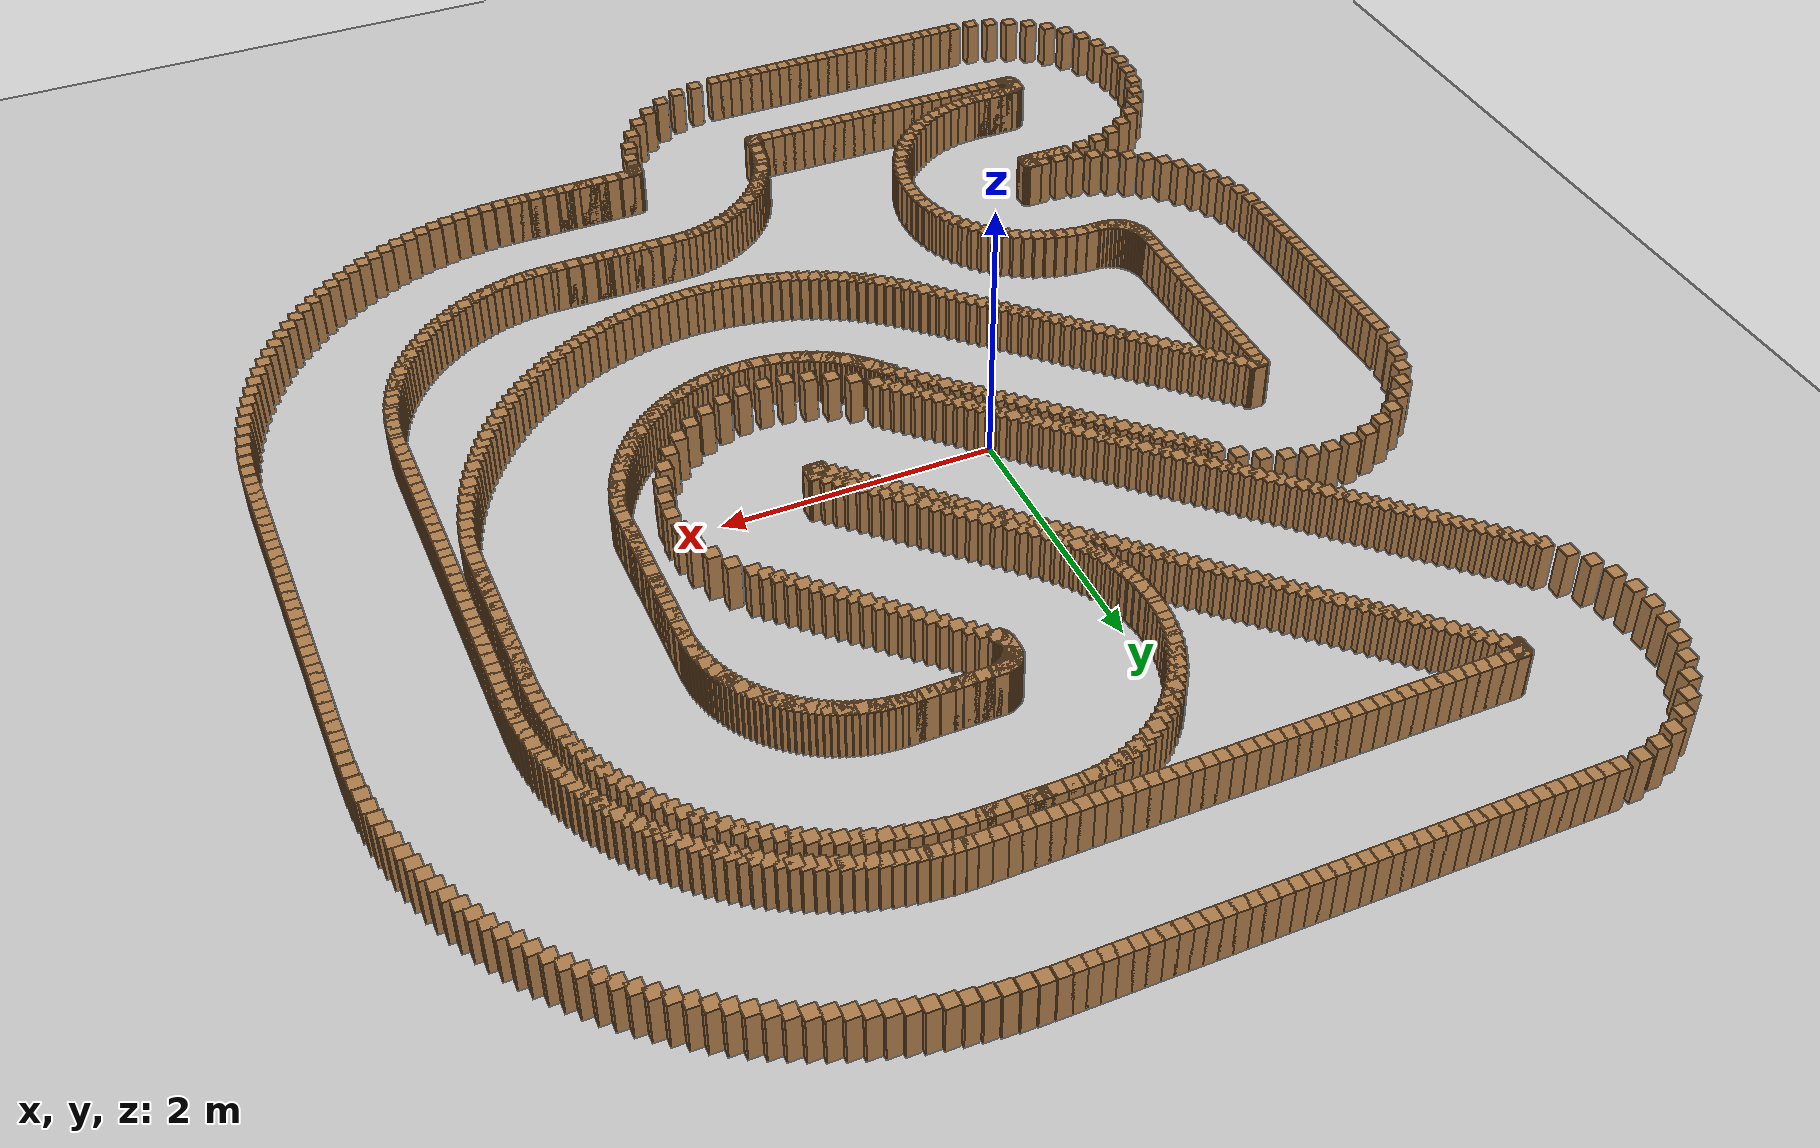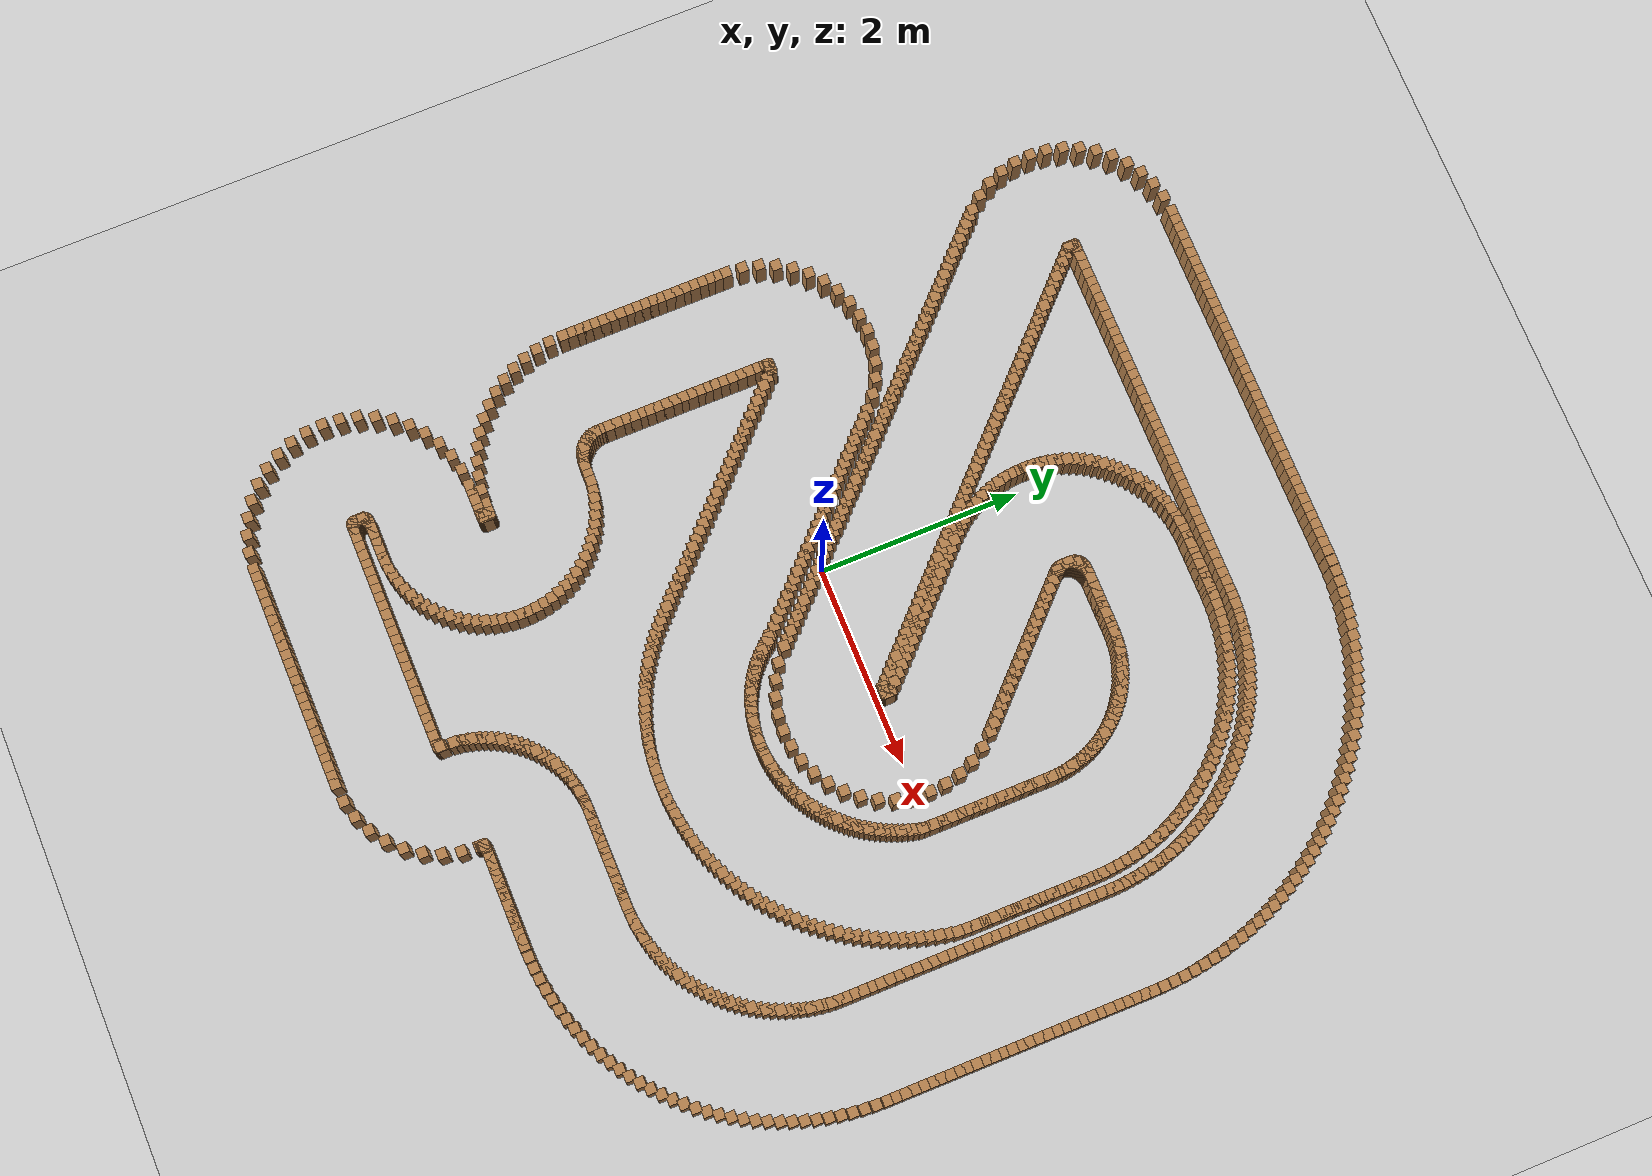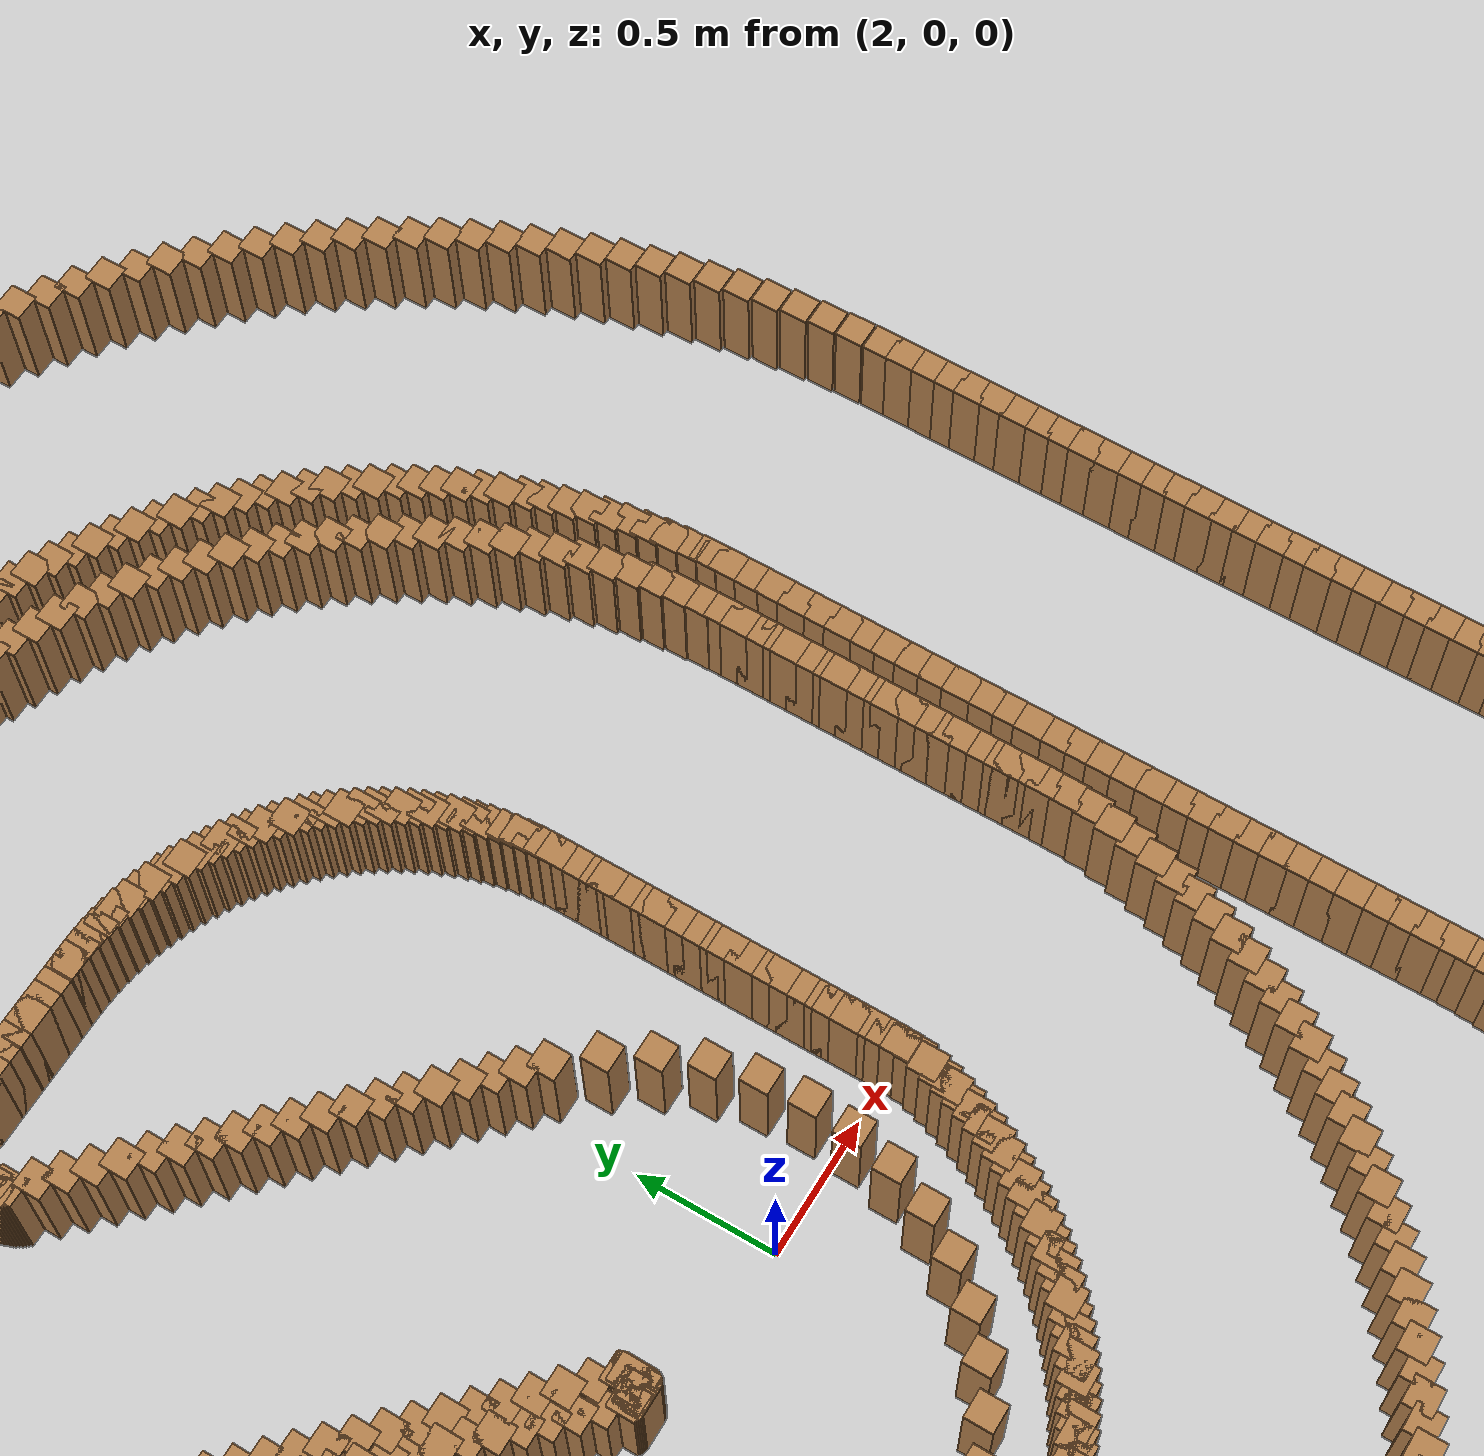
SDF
<sdf version="1.6">
 <world name="default">
  <light name="sun" type="directional">
   <pose>0 0 10 0 -0 0</pose>
   <diffuse>0.8 0.8 0.8 1</diffuse>
   <specular>0.2 0.2 0.2 1</specular>
   <attenuation>
    <range>1000</range>
    <constant>0.9</constant>
    <linear>0.01</linear>
    <quadratic>0.001</quadratic>
   </attenuation>
   <direction>-0.5 0.1 -0.9</direction>
  </light>
  <model name="ground_plane">
   <static>1</static>
   <link name="link">
    <collision name="collision">
     <geometry><plane><normal>0 0 1</normal><size>100 100</size></plane></geometry>
     <surface><friction><ode><mu>100</mu><mu2>50</mu2></ode></friction></surface>
    </collision>
    <visual name="visual">
     <cast_shadows>0</cast_shadows>
     <geometry><plane><normal>0 0 1</normal><size>100 100</size></plane></geometry>
     <material>
      <script><uri>file://media/materials/scripts/gazebo.material</uri><name>Gazebo/Grey</name></script>
     </material>
    </visual>
   </link>
  </model>
  <gravity>0 0 -9.8</gravity>
  <magnetic_field>6e-06 2.3e-05 -4.2e-05</magnetic_field>
  <atmosphere type="adiabatic"/>
  <physics name="default_physics" default="0" type="ode">
   <max_step_size>0.01</max_step_size>
   <real_time_factor>10.</real_time_factor>
   <real_time_update_rate>1000</real_time_update_rate>
  </physics>
  <scene><ambient>0.4 0.4 0.4 1</ambient><background>0.7 0.7 0.7 1</background><shadows>1</shadows></scene>
  <spherical_coordinates>
   <surface_model>EARTH_WGS84</surface_model>
   <latitude_deg>0</latitude_deg>
   <longitude_deg>0</longitude_deg>
   <elevation>0</elevation>
   <heading_deg>0</heading_deg>
  </spherical_coordinates>
  <model name="track">
   <link name="inner_0">
    <pose>-1.932240 3.320853 0.000000 0 -0 0</pose>
    <collision name="collision"><geometry><box><size>0.1 0.1 0.7</size></box></geometry></collision>
    <visual name="visual">
     <geometry><box><size>0.1 0.1 0.7</size></box></geometry>
     <material>
      <script><uri>file://media/materials/scripts/gazebo.material</uri><name>Gazebo/Wood</name></script>
     </material>
    </visual>
   </link>
   <link name="inner_1">
    <pose>-1.876353 3.264966 0.000000 0 -0 0</pose>
    <collision name="collision"><geometry><box><size>0.1 0.1 0.7</size></box></geometry></collision>
    <visual name="visual">
     <geometry><box><size>0.1 0.1 0.7</size></box></geometry>
     <material>
      <script><uri>file://media/materials/scripts/gazebo.material</uri><name>Gazebo/Wood</name></script>
     </material>
    </visual>
   </link>
   <link name="inner_2">
    <pose>-1.820467 3.209080 0.000000 0 -0 0</pose>
    <collision name="collision"><geometry><box><size>0.1 0.1 0.7</size></box></geometry></collision>
    <visual name="visual">
     <geometry><box><size>0.1 0.1 0.7</size></box></geometry>
     <material>
      <script><uri>file://media/materials/scripts/gazebo.material</uri><name>Gazebo/Wood</name></script>
     </material>
    </visual>
   </link>
   <link name="inner_3">
    <pose>-1.764580 3.153193 0.000000 0 -0 0</pose>
    <collision name="collision"><geometry><box><size>0.1 0.1 0.7</size></box></geometry></collision>
    <visual name="visual">
     <geometry><box><size>0.1 0.1 0.7</size></box></geometry>
     <material>
      <script><uri>file://media/materials/scripts/gazebo.material</uri><name>Gazebo/Wood</name></script>
     </material>
    </visual>
   </link>
   <link name="inner_4">
    <pose>-1.708694 3.097307 0.000000 0 -0 0</pose>
    <collision name="collision"><geometry><box><size>0.1 0.1 0.7</size></box></geometry></collision>
    <visual name="visual">
     <geometry><box><size>0.1 0.1 0.7</size></box></geometry>
     <material>
      <script><uri>file://media/materials/scripts/gazebo.material</uri><name>Gazebo/Wood</name></script>
     </material>
    </visual>
   </link>
   <link name="inner_5">
    <pose>-1.652808 3.041421 0.000000 0 -0 0</pose>
    <collision name="collision"><geometry><box><size>0.1 0.1 0.7</size></box></geometry></collision>
    <visual name="visual">
     <geometry><box><size>0.1 0.1 0.7</size></box></geometry>
     <material>
      <script><uri>file://media/materials/scripts/gazebo.material</uri><name>Gazebo/Wood</name></script>
     </material>
    </visual>
   </link>
   <link name="inner_6">
    <pose>-1.596921 2.985534 0.000000 0 -0 0</pose>
    <collision name="collision"><geometry><box><size>0.1 0.1 0.7</size></box></geometry></collision>
    <visual name="visual">
     <geometry><box><size>0.1 0.1 0.7</size></box></geometry>
     <material>
      <script><uri>file://media/materials/scripts/gazebo.material</uri><name>Gazebo/Wood</name></script>
     </material>
    </visual>
   </link>
   <link name="inner_7">
    <pose>-1.541035 2.929648 0.000000 0 -0 0</pose>
    <collision name="collision"><geometry><box><size>0.1 0.1 0.7</size></box></geometry></collision>
    <visual name="visual">
     <geometry><box><size>0.1 0.1 0.7</size></box></geometry>
     <material>
      <script><uri>file://media/materials/scripts/gazebo.material</uri><name>Gazebo/Wood</name></script>
     </material>
    </visual>
   </link>
   <link name="inner_8">
    <pose>-1.485148 2.873761 0.000000 0 -0 0</pose>
    <collision name="collision"><geometry><box><size>0.1 0.1 0.7</size></box></geometry></collision>
    <visual name="visual">
     <geometry><box><size>0.1 0.1 0.7</size></box></geometry>
     <material>
      <script><uri>file://media/materials/scripts/gazebo.material</uri><name>Gazebo/Wood</name></script>
     </material>
    </visual>
   </link>
   <link name="inner_9">
    <pose>-1.429262 2.817875 0.000000 0 -0 0</pose>
    <collision name="collision"><geometry><box><size>0.1 0.1 0.7</size></box></geometry></collision>
    <visual name="visual">
     <geometry><box><size>0.1 0.1 0.7</size></box></geometry>
     <material>
      <script><uri>file://media/materials/scripts/gazebo.material</uri><name>Gazebo/Wood</name></script>
     </material>
    </visual>
   </link>
   <link name="inner_10">
    <pose>-1.373376 2.761989 0.000000 0 -0 0</pose>
    <collision name="collision"><geometry><box><size>0.1 0.1 0.7</size></box></geometry></collision>
    <visual name="visual">
     <geometry><box><size>0.1 0.1 0.7</size></box></geometry>
     <material>
      <script><uri>file://media/materials/scripts/gazebo.material</uri><name>Gazebo/Wood</name></script>
     </material>
    </visual>
   </link>
   <link name="inner_11">
    <pose>-1.317489 2.706102 0.000000 0 -0 0</pose>
    <collision name="collision"><geometry><box><size>0.1 0.1 0.7</size></box></geometry></collision>
    <visual name="visual">
     <geometry><box><size>0.1 0.1 0.7</size></box></geometry>
     <material>
      <script><uri>file://media/materials/scripts/gazebo.material</uri><name>Gazebo/Wood</name></script>
     </material>
    </visual>
   </link>
   <link name="inner_12">
    <pose>-1.261603 2.650216 0.000000 0 -0 0</pose>
    <collision name="collision"><geometry><box><size>0.1 0.1 0.7</size></box></geometry></collision>
    <visual name="visual">
     <geometry><box><size>0.1 0.1 0.7</size></box></geometry>
     <material>
      <script><uri>file://media/materials/scripts/gazebo.material</uri><name>Gazebo/Wood</name></script>
     </material>
    </visual>
   </link>
   <link name="inner_13">
    <pose>-1.205716 2.594329 0.000000 0 -0 0</pose>
    <collision name="collision"><geometry><box><size>0.1 0.1 0.7</size></box></geometry></collision>
    <visual name="visual">
     <geometry><box><size>0.1 0.1 0.7</size></box></geometry>
     <material>
      <script><uri>file://media/materials/scripts/gazebo.material</uri><name>Gazebo/Wood</name></script>
     </material>
    </visual>
   </link>
   <link name="inner_14">
    <pose>-1.149830 2.538443 0.000000 0 -0 0</pose>
    <collision name="collision"><geometry><box><size>0.1 0.1 0.7</size></box></geometry></collision>
    <visual name="visual">
     <geometry><box><size>0.1 0.1 0.7</size></box></geometry>
     <material>
      <script><uri>file://media/materials/scripts/gazebo.material</uri><name>Gazebo/Wood</name></script>
     </material>
    </visual>
   </link>
   <link name="inner_15">
    <pose>-1.093944 2.482557 0.000000 0 -0 0</pose>
    <collision name="collision"><geometry><box><size>0.1 0.1 0.7</size></box></geometry></collision>
    <visual name="visual">
     <geometry><box><size>0.1 0.1 0.7</size></box></geometry>
     <material>
      <script><uri>file://media/materials/scripts/gazebo.material</uri><name>Gazebo/Wood</name></script>
     </material>
    </visual>
   </link>
   <link name="inner_16">
    <pose>-1.038057 2.426670 0.000000 0 -0 0</pose>
    <collision name="collision"><geometry><box><size>0.1 0.1 0.7</size></box></geometry></collision>
    <visual name="visual">
     <geometry><box><size>0.1 0.1 0.7</size></box></geometry>
     <material>
      <script><uri>file://media/materials/scripts/gazebo.material</uri><name>Gazebo/Wood</name></script>
     </material>
    </visual>
   </link>
   <link name="inner_17">
    <pose>-0.982171 2.370784 0.000000 0 -0 0</pose>
    <collision name="collision"><geometry><box><size>0.1 0.1 0.7</size></box></geometry></collision>
    <visual name="visual">
     <geometry><box><size>0.1 0.1 0.7</size></box></geometry>
     <material>
      <script><uri>file://media/materials/scripts/gazebo.material</uri><name>Gazebo/Wood</name></script>
     </material>
    </visual>
   </link>
   <link name="inner_18">
    <pose>-0.926284 2.314897 0.000000 0 -0 0</pose>
    <collision name="collision"><geometry><box><size>0.1 0.1 0.7</size></box></geometry></collision>
    <visual name="visual">
     <geometry><box><size>0.1 0.1 0.7</size></box></geometry>
     <material>
      <script><uri>file://media/materials/scripts/gazebo.material</uri><name>Gazebo/Wood</name></script>
     </material>
    </visual>
   </link>
   <link name="inner_19">
    <pose>-0.870398 2.259011 0.000000 0 -0 0</pose>
    <collision name="collision"><geometry><box><size>0.1 0.1 0.7</size></box></geometry></collision>
    <visual name="visual">
     <geometry><box><size>0.1 0.1 0.7</size></box></geometry>
     <material>
      <script><uri>file://media/materials/scripts/gazebo.material</uri><name>Gazebo/Wood</name></script>
     </material>
    </visual>
   </link>
   <link name="inner_20">
    <pose>-0.814512 2.203125 0.000000 0 -0 0</pose>
    <collision name="collision"><geometry><box><size>0.1 0.1 0.7</size></box></geometry></collision>
    <visual name="visual">
     <geometry><box><size>0.1 0.1 0.7</size></box></geometry>
     <material>
      <script><uri>file://media/materials/scripts/gazebo.material</uri><name>Gazebo/Wood</name></script>
     </material>
    </visual>
   </link>
   <link name="inner_21">
    <pose>-0.758625 2.147238 0.000000 0 -0 0</pose>
    <collision name="collision"><geometry><box><size>0.1 0.1 0.7</size></box></geometry></collision>
    <visual name="visual">
     <geometry><box><size>0.1 0.1 0.7</size></box></geometry>
     <material>
      <script><uri>file://media/materials/scripts/gazebo.material</uri><name>Gazebo/Wood</name></script>
     </material>
    </visual>
   </link>
   <link name="inner_22">
    <pose>-0.702739 2.091352 0.000000 0 -0 0</pose>
    <collision name="collision"><geometry><box><size>0.1 0.1 0.7</size></box></geometry></collision>
    <visual name="visual">
     <geometry><box><size>0.1 0.1 0.7</size></box></geometry>
     <material>
      <script><uri>file://media/materials/scripts/gazebo.material</uri><name>Gazebo/Wood</name></script>
     </material>
    </visual>
   </link>
   <link name="inner_23">
    <pose>-0.646852 2.035465 0.000000 0 -0 0</pose>
    <collision name="collision"><geometry><box><size>0.1 0.1 0.7</size></box></geometry></collision>
    <visual name="visual">
     <geometry><box><size>0.1 0.1 0.7</size></box></geometry>
     <material>
      <script><uri>file://media/materials/scripts/gazebo.material</uri><name>Gazebo/Wood</name></script>
     </material>
    </visual>
   </link>
   <link name="inner_24">
    <pose>-0.590966 1.979579 0.000000 0 -0 0</pose>
    <collision name="collision"><geometry><box><size>0.1 0.1 0.7</size></box></geometry></collision>
    <visual name="visual">
     <geometry><box><size>0.1 0.1 0.7</size></box></geometry>
     <material>
      <script><uri>file://media/materials/scripts/gazebo.material</uri><name>Gazebo/Wood</name></script>
     </material>
    </visual>
   </link>
   <link name="inner_25">
    <pose>-0.535080 1.923693 0.000000 0 -0 0</pose>
    <collision name="collision"><geometry><box><size>0.1 0.1 0.7</size></box></geometry></collision>
    <visual name="visual">
     <geometry><box><size>0.1 0.1 0.7</size></box></geometry>
     <material>
      <script><uri>file://media/materials/scripts/gazebo.material</uri><name>Gazebo/Wood</name></script>
     </material>
    </visual>
   </link>
   <link name="inner_26">
    <pose>-0.479193 1.867806 0.000000 0 -0 0</pose>
    <collision name="collision"><geometry><box><size>0.1 0.1 0.7</size></box></geometry></collision>
    <visual name="visual">
     <geometry><box><size>0.1 0.1 0.7</size></box></geometry>
     <material>
      <script><uri>file://media/materials/scripts/gazebo.material</uri><name>Gazebo/Wood</name></script>
     </material>
    </visual>
   </link>
   <link name="inner_27">
    <pose>-0.423307 1.811920 0.000000 0 -0 0</pose>
    <collision name="collision"><geometry><box><size>0.1 0.1 0.7</size></box></geometry></collision>
    <visual name="visual">
     <geometry><box><size>0.1 0.1 0.7</size></box></geometry>
     <material>
      <script><uri>file://media/materials/scripts/gazebo.material</uri><name>Gazebo/Wood</name></script>
     </material>
    </visual>
   </link>
   <link name="inner_28">
    <pose>-0.367420 1.756033 0.000000 0 -0 0</pose>
    <collision name="collision"><geometry><box><size>0.1 0.1 0.7</size></box></geometry></collision>
    <visual name="visual">
     <geometry><box><size>0.1 0.1 0.7</size></box></geometry>
     <material>
      <script><uri>file://media/materials/scripts/gazebo.material</uri><name>Gazebo/Wood</name></script>
     </material>
    </visual>
   </link>
   <link name="inner_29">
    <pose>-0.311534 1.700147 0.000000 0 -0 0</pose>
    <collision name="collision"><geometry><box><size>0.1 0.1 0.7</size></box></geometry></collision>
    <visual name="visual">
     <geometry><box><size>0.1 0.1 0.7</size></box></geometry>
     <material>
      <script><uri>file://media/materials/scripts/gazebo.material</uri><name>Gazebo/Wood</name></script>
     </material>
    </visual>
   </link>
   <link name="inner_30">
    <pose>-0.255648 1.644261 0.000000 0 -0 0</pose>
    <collision name="collision"><geometry><box><size>0.1 0.1 0.7</size></box></geometry></collision>
    <visual name="visual">
     <geometry><box><size>0.1 0.1 0.7</size></box></geometry>
     <material>
      <script><uri>file://media/materials/scripts/gazebo.material</uri><name>Gazebo/Wood</name></script>
     </material>
    </visual>
   </link>
   <link name="inner_31">
    <pose>-0.199761 1.588374 0.000000 0 -0 0</pose>
    <collision name="collision"><geometry><box><size>0.1 0.1 0.7</size></box></geometry></collision>
    <visual name="visual">
     <geometry><box><size>0.1 0.1 0.7</size></box></geometry>
     <material>
      <script><uri>file://media/materials/scripts/gazebo.material</uri><name>Gazebo/Wood</name></script>
     </material>
    </visual>
   </link>
   <link name="inner_32">
    <pose>-0.143875 1.532488 0.000000 0 -0 0</pose>
    <collision name="collision"><geometry><box><size>0.1 0.1 0.7</size></box></geometry></collision>
    <visual name="visual">
     <geometry><box><size>0.1 0.1 0.7</size></box></geometry>
     <material>
      <script><uri>file://media/materials/scripts/gazebo.material</uri><name>Gazebo/Wood</name></script>
     </material>
    </visual>
   </link>
   <link name="inner_33">
    <pose>-0.087989 1.476601 0.000000 0 -0 0</pose>
    <collision name="collision"><geometry><box><size>0.1 0.1 0.7</size></box></geometry></collision>
    <visual name="visual">
     <geometry><box><size>0.1 0.1 0.7</size></box></geometry>
     <material>
      <script><uri>file://media/materials/scripts/gazebo.material</uri><name>Gazebo/Wood</name></script>
     </material>
    </visual>
   </link>
   <link name="inner_34">
    <pose>-0.032102 1.420715 0.000000 0 -0 0</pose>
    <collision name="collision"><geometry><box><size>0.1 0.1 0.7</size></box></geometry></collision>
    <visual name="visual">
     <geometry><box><size>0.1 0.1 0.7</size></box></geometry>
     <material>
      <script><uri>file://media/materials/scripts/gazebo.material</uri><name>Gazebo/Wood</name></script>
     </material>
    </visual>
   </link>
   <link name="inner_35">
    <pose>0.023784 1.364829 0.000000 0 -0 0</pose>
    <collision name="collision"><geometry><box><size>0.1 0.1 0.7</size></box></geometry></collision>
    <visual name="visual">
     <geometry><box><size>0.1 0.1 0.7</size></box></geometry>
     <material>
      <script><uri>file://media/materials/scripts/gazebo.material</uri><name>Gazebo/Wood</name></script>
     </material>
    </visual>
   </link>
   <link name="inner_36">
    <pose>0.079671 1.308942 0.000000 0 -0 0</pose>
    <collision name="collision"><geometry><box><size>0.1 0.1 0.7</size></box></geometry></collision>
    <visual name="visual">
     <geometry><box><size>0.1 0.1 0.7</size></box></geometry>
     <material>
      <script><uri>file://media/materials/scripts/gazebo.material</uri><name>Gazebo/Wood</name></script>
     </material>
    </visual>
   </link>
   <link name="inner_37">
    <pose>0.135557 1.253056 0.000000 0 -0 0</pose>
    <collision name="collision"><geometry><box><size>0.1 0.1 0.7</size></box></geometry></collision>
    <visual name="visual">
     <geometry><box><size>0.1 0.1 0.7</size></box></geometry>
     <material>
      <script><uri>file://media/materials/scripts/gazebo.material</uri><name>Gazebo/Wood</name></script>
     </material>
    </visual>
   </link>
   <link name="inner_38">
    <pose>0.191443 1.197170 0.000000 0 -0 0</pose>
    <collision name="collision"><geometry><box><size>0.1 0.1 0.7</size></box></geometry></collision>
    <visual name="visual">
     <geometry><box><size>0.1 0.1 0.7</size></box></geometry>
     <material>
      <script><uri>file://media/materials/scripts/gazebo.material</uri><name>Gazebo/Wood</name></script>
     </material>
    </visual>
   </link>
   <link name="inner_39">
    <pose>0.247330 1.141283 0.000000 0 -0 0</pose>
    <collision name="collision"><geometry><box><size>0.1 0.1 0.7</size></box></geometry></collision>
    <visual name="visual">
     <geometry><box><size>0.1 0.1 0.7</size></box></geometry>
     <material>
      <script><uri>file://media/materials/scripts/gazebo.material</uri><name>Gazebo/Wood</name></script>
     </material>
    </visual>
   </link>
   <link name="inner_40">
    <pose>0.303216 1.085397 0.000000 0 -0 0</pose>
    <collision name="collision"><geometry><box><size>0.1 0.1 0.7</size></box></geometry></collision>
    <visual name="visual">
     <geometry><box><size>0.1 0.1 0.7</size></box></geometry>
     <material>
      <script><uri>file://media/materials/scripts/gazebo.material</uri><name>Gazebo/Wood</name></script>
     </material>
    </visual>
   </link>
   <link name="inner_41">
    <pose>0.359103 1.029510 0.000000 0 -0 0</pose>
    <collision name="collision"><geometry><box><size>0.1 0.1 0.7</size></box></geometry></collision>
    <visual name="visual">
     <geometry><box><size>0.1 0.1 0.7</size></box></geometry>
     <material>
      <script><uri>file://media/materials/scripts/gazebo.material</uri><name>Gazebo/Wood</name></script>
     </material>
    </visual>
   </link>
   <link name="inner_42">
    <pose>0.414989 0.973624 0.000000 0 -0 0</pose>
    <collision name="collision"><geometry><box><size>0.1 0.1 0.7</size></box></geometry></collision>
    <visual name="visual">
     <geometry><box><size>0.1 0.1 0.7</size></box></geometry>
     <material>
      <script><uri>file://media/materials/scripts/gazebo.material</uri><name>Gazebo/Wood</name></script>
     </material>
    </visual>
   </link>
   <link name="inner_43">
    <pose>0.470875 0.917738 0.000000 0 -0 0</pose>
    <collision name="collision"><geometry><box><size>0.1 0.1 0.7</size></box></geometry></collision>
    <visual name="visual">
     <geometry><box><size>0.1 0.1 0.7</size></box></geometry>
     <material>
      <script><uri>file://media/materials/scripts/gazebo.material</uri><name>Gazebo/Wood</name></script>
     </material>
    </visual>
   </link>
   <link name="inner_44">
    <pose>0.526762 0.861851 0.000000 0 -0 0</pose>
    <collision name="collision"><geometry><box><size>0.1 0.1 0.7</size></box></geometry></collision>
    <visual name="visual">
     <geometry><box><size>0.1 0.1 0.7</size></box></geometry>
     <material>
      <script><uri>file://media/materials/scripts/gazebo.material</uri><name>Gazebo/Wood</name></script>
     </material>
    </visual>
   </link>
   <link name="inner_45">
    <pose>0.582648 0.805965 0.000000 0 -0 0</pose>
    <collision name="collision"><geometry><box><size>0.1 0.1 0.7</size></box></geometry></collision>
    <visual name="visual">
     <geometry><box><size>0.1 0.1 0.7</size></box></geometry>
     <material>
      <script><uri>file://media/materials/scripts/gazebo.material</uri><name>Gazebo/Wood</name></script>
     </material>
    </visual>
   </link>
   <link name="inner_46">
    <pose>0.638535 0.750078 0.000000 0 -0 0</pose>
    <collision name="collision"><geometry><box><size>0.1 0.1 0.7</size></box></geometry></collision>
    <visual name="visual">
     <geometry><box><size>0.1 0.1 0.7</size></box></geometry>
     <material>
      <script><uri>file://media/materials/scripts/gazebo.material</uri><name>Gazebo/Wood</name></script>
     </material>
    </visual>
   </link>
   <link name="inner_47">
    <pose>0.694421 0.694192 0.000000 0 -0 0</pose>
    <collision name="collision"><geometry><box><size>0.1 0.1 0.7</size></box></geometry></collision>
    <visual name="visual">
     <geometry><box><size>0.1 0.1 0.7</size></box></geometry>
     <material>
      <script><uri>file://media/materials/scripts/gazebo.material</uri><name>Gazebo/Wood</name></script>
     </material>
    </visual>
   </link>
   <link name="inner_48">
    <pose>0.750307 0.638306 0.000000 0 -0 0</pose>
    <collision name="collision"><geometry><box><size>0.1 0.1 0.7</size></box></geometry></collision>
    <visual name="visual">
     <geometry><box><size>0.1 0.1 0.7</size></box></geometry>
     <material>
      <script><uri>file://media/materials/scripts/gazebo.material</uri><name>Gazebo/Wood</name></script>
     </material>
    </visual>
   </link>
   <link name="inner_49">
    <pose>0.806194 0.582419 0.000000 0 -0 0</pose>
    <collision name="collision"><geometry><box><size>0.1 0.1 0.7</size></box></geometry></collision>
    <visual name="visual">
     <geometry><box><size>0.1 0.1 0.7</size></box></geometry>
     <material>
      <script><uri>file://media/materials/scripts/gazebo.material</uri><name>Gazebo/Wood</name></script>
     </material>
    </visual>
   </link>
   <link name="inner_50">
    <pose>0.862080 0.526533 0.000000 0 -0 0</pose>
    <collision name="collision"><geometry><box><size>0.1 0.1 0.7</size></box></geometry></collision>
    <visual name="visual">
     <geometry><box><size>0.1 0.1 0.7</size></box></geometry>
     <material>
      <script><uri>file://media/materials/scripts/gazebo.material</uri><name>Gazebo/Wood</name></script>
     </material>
    </visual>
   </link>
   <link name="inner_51">
    <pose>0.917967 0.470646 0.000000 0 -0 0</pose>
    <collision name="collision"><geometry><box><size>0.1 0.1 0.7</size></box></geometry></collision>
    <visual name="visual">
     <geometry><box><size>0.1 0.1 0.7</size></box></geometry>
     <material>
      <script><uri>file://media/materials/scripts/gazebo.material</uri><name>Gazebo/Wood</name></script>
     </material>
    </visual>
   </link>
   <link name="inner_52">
    <pose>0.973853 0.414760 0.000000 0 -0 0</pose>
    <collision name="collision"><geometry><box><size>0.1 0.1 0.7</size></box></geometry></collision>
    <visual name="visual">
     <geometry><box><size>0.1 0.1 0.7</size></box></geometry>
     <material>
      <script><uri>file://media/materials/scripts/gazebo.material</uri><name>Gazebo/Wood</name></script>
     </material>
    </visual>
   </link>
   <link name="inner_53">
    <pose>1.029739 0.358874 0.000000 0 -0 0</pose>
    <collision name="collision"><geometry><box><size>0.1 0.1 0.7</size></box></geometry></collision>
    <visual name="visual">
     <geometry><box><size>0.1 0.1 0.7</size></box></geometry>
     <material>
      <script><uri>file://media/materials/scripts/gazebo.material</uri><name>Gazebo/Wood</name></script>
     </material>
    </visual>
   </link>
   <link name="inner_54">
    <pose>1.085626 0.302987 0.000000 0 -0 0</pose>
    <collision name="collision"><geometry><box><size>0.1 0.1 0.7</size></box></geometry></collision>
    <visual name="visual">
     <geometry><box><size>0.1 0.1 0.7</size></box></geometry>
     <material>
      <script><uri>file://media/materials/scripts/gazebo.material</uri><name>Gazebo/Wood</name></script>
     </material>
    </visual>
   </link>
   <link name="inner_55">
    <pose>1.141512 0.247101 0.000000 0 -0 0</pose>
    <collision name="collision"><geometry><box><size>0.1 0.1 0.7</size></box></geometry></collision>
    <visual name="visual">
     <geometry><box><size>0.1 0.1 0.7</size></box></geometry>
     <material>
      <script><uri>file://media/materials/scripts/gazebo.material</uri><name>Gazebo/Wood</name></script>
     </material>
    </visual>
   </link>
   <link name="inner_56">
    <pose>1.197399 0.191214 0.000000 0 -0 0</pose>
    <collision name="collision"><geometry><box><size>0.1 0.1 0.7</size></box></geometry></collision>
    <visual name="visual">
     <geometry><box><size>0.1 0.1 0.7</size></box></geometry>
     <material>
      <script><uri>file://media/materials/scripts/gazebo.material</uri><name>Gazebo/Wood</name></script>
     </material>
    </visual>
   </link>
   <link name="inner_57">
    <pose>1.253285 0.135328 0.000000 0 -0 0</pose>
    <collision name="collision"><geometry><box><size>0.1 0.1 0.7</size></box></geometry></collision>
    <visual name="visual">
     <geometry><box><size>0.1 0.1 0.7</size></box></geometry>
     <material>
      <script><uri>file://media/materials/scripts/gazebo.material</uri><name>Gazebo/Wood</name></script>
     </material>
    </visual>
   </link>
   <link name="inner_58">
    <pose>1.309171 0.079442 0.000000 0 -0 0</pose>
    <collision name="collision"><geometry><box><size>0.1 0.1 0.7</size></box></geometry></collision>
    <visual name="visual">
     <geometry><box><size>0.1 0.1 0.7</size></box></geometry>
     <material>
      <script><uri>file://media/materials/scripts/gazebo.material</uri><name>Gazebo/Wood</name></script>
     </material>
    </visual>
   </link>
   <link name="inner_59">
    <pose>1.314009 0.075310 0.000000 0 -0 0</pose>
    <collision name="collision"><geometry><box><size>0.1 0.1 0.7</size></box></geometry></collision>
    <visual name="visual">
     <geometry><box><size>0.1 0.1 0.7</size></box></geometry>
     <material>
      <script><uri>file://media/materials/scripts/gazebo.material</uri><name>Gazebo/Wood</name></script>
     </material>
    </visual>
   </link>
   <link name="inner_60">
    <pose>1.319433 0.071986 0.000000 0 -0 0</pose>
    <collision name="collision"><geometry><box><size>0.1 0.1 0.7</size></box></geometry></collision>
    <visual name="visual">
     <geometry><box><size>0.1 0.1 0.7</size></box></geometry>
     <material>
      <script><uri>file://media/materials/scripts/gazebo.material</uri><name>Gazebo/Wood</name></script>
     </material>
    </visual>
   </link>
   <link name="inner_61">
    <pose>1.325310 0.069552 0.000000 0 -0 0</pose>
    <collision name="collision"><geometry><box><size>0.1 0.1 0.7</size></box></geometry></collision>
    <visual name="visual">
     <geometry><box><size>0.1 0.1 0.7</size></box></geometry>
     <material>
      <script><uri>file://media/materials/scripts/gazebo.material</uri><name>Gazebo/Wood</name></script>
     </material>
    </visual>
   </link>
   <link name="inner_62">
    <pose>1.331496 0.068067 0.000000 0 -0 0</pose>
    <collision name="collision"><geometry><box><size>0.1 0.1 0.7</size></box></geometry></collision>
    <visual name="visual">
     <geometry><box><size>0.1 0.1 0.7</size></box></geometry>
     <material>
      <script><uri>file://media/materials/scripts/gazebo.material</uri><name>Gazebo/Wood</name></script>
     </material>
    </visual>
   </link>
   <link name="inner_63">
    <pose>1.337838 0.067568 0.000000 0 -0 0</pose>
    <collision name="collision"><geometry><box><size>0.1 0.1 0.7</size></box></geometry></collision>
    <visual name="visual">
     <geometry><box><size>0.1 0.1 0.7</size></box></geometry>
     <material>
      <script><uri>file://media/materials/scripts/gazebo.material</uri><name>Gazebo/Wood</name></script>
     </material>
    </visual>
   </link>
   <link name="inner_64">
    <pose>1.344180 0.068067 0.000000 0 -0 0</pose>
    <collision name="collision"><geometry><box><size>0.1 0.1 0.7</size></box></geometry></collision>
    <visual name="visual">
     <geometry><box><size>0.1 0.1 0.7</size></box></geometry>
     <material>
      <script><uri>file://media/materials/scripts/gazebo.material</uri><name>Gazebo/Wood</name></script>
     </material>
    </visual>
   </link>
   <link name="inner_65">
    <pose>1.350366 0.069552 0.000000 0 -0 0</pose>
    <collision name="collision"><geometry><box><size>0.1 0.1 0.7</size></box></geometry></collision>
    <visual name="visual">
     <geometry><box><size>0.1 0.1 0.7</size></box></geometry>
     <material>
      <script><uri>file://media/materials/scripts/gazebo.material</uri><name>Gazebo/Wood</name></script>
     </material>
    </visual>
   </link>
   <link name="inner_66">
    <pose>1.356243 0.071986 0.000000 0 -0 0</pose>
    <collision name="collision"><geometry><box><size>0.1 0.1 0.7</size></box></geometry></collision>
    <visual name="visual">
     <geometry><box><size>0.1 0.1 0.7</size></box></geometry>
     <material>
      <script><uri>file://media/materials/scripts/gazebo.material</uri><name>Gazebo/Wood</name></script>
     </material>
    </visual>
   </link>
   <link name="inner_67">
    <pose>1.361667 0.075310 0.000000 0 -0 0</pose>
    <collision name="collision"><geometry><box><size>0.1 0.1 0.7</size></box></geometry></collision>
    <visual name="visual">
     <geometry><box><size>0.1 0.1 0.7</size></box></geometry>
     <material>
      <script><uri>file://media/materials/scripts/gazebo.material</uri><name>Gazebo/Wood</name></script>
     </material>
    </visual>
   </link>
   <link name="inner_68">
    <pose>1.366504 0.079442 0.000000 0 -0 0</pose>
    <collision name="collision"><geometry><box><size>0.1 0.1 0.7</size></box></geometry></collision>
    <visual name="visual">
     <geometry><box><size>0.1 0.1 0.7</size></box></geometry>
     <material>
      <script><uri>file://media/materials/scripts/gazebo.material</uri><name>Gazebo/Wood</name></script>
     </material>
    </visual>
   </link>
   <link name="inner_69">
    <pose>1.370636 0.084279 0.000000 0 -0 0</pose>
    <collision name="collision"><geometry><box><size>0.1 0.1 0.7</size></box></geometry></collision>
    <visual name="visual">
     <geometry><box><size>0.1 0.1 0.7</size></box></geometry>
     <material>
      <script><uri>file://media/materials/scripts/gazebo.material</uri><name>Gazebo/Wood</name></script>
     </material>
    </visual>
   </link>
   <link name="inner_70">
    <pose>1.373960 0.089703 0.000000 0 -0 0</pose>
    <collision name="collision"><geometry><box><size>0.1 0.1 0.7</size></box></geometry></collision>
    <visual name="visual">
     <geometry><box><size>0.1 0.1 0.7</size></box></geometry>
     <material>
      <script><uri>file://media/materials/scripts/gazebo.material</uri><name>Gazebo/Wood</name></script>
     </material>
    </visual>
   </link>
   <link name="inner_71">
    <pose>1.376394 0.095580 0.000000 0 -0 0</pose>
    <collision name="collision"><geometry><box><size>0.1 0.1 0.7</size></box></geometry></collision>
    <visual name="visual">
     <geometry><box><size>0.1 0.1 0.7</size></box></geometry>
     <material>
      <script><uri>file://media/materials/scripts/gazebo.material</uri><name>Gazebo/Wood</name></script>
     </material>
    </visual>
   </link>
   <link name="inner_72">
    <pose>1.377879 0.101766 0.000000 0 -0 0</pose>
    <collision name="collision"><geometry><box><size>0.1 0.1 0.7</size></box></geometry></collision>
    <visual name="visual">
     <geometry><box><size>0.1 0.1 0.7</size></box></geometry>
     <material>
      <script><uri>file://media/materials/scripts/gazebo.material</uri><name>Gazebo/Wood</name></script>
     </material>
    </visual>
   </link>
   <link name="inner_73">
    <pose>1.378378 0.108108 0.000000 0 -0 0</pose>
    <collision name="collision"><geometry><box><size>0.1 0.1 0.7</size></box></geometry></collision>
    <visual name="visual">
     <geometry><box><size>0.1 0.1 0.7</size></box></geometry>
     <material>
      <script><uri>file://media/materials/scripts/gazebo.material</uri><name>Gazebo/Wood</name></script>
     </material>
    </visual>
   </link>
   <link name="inner_74">
    <pose>1.377879 0.114450 0.000000 0 -0 0</pose>
    <collision name="collision"><geometry><box><size>0.1 0.1 0.7</size></box></geometry></collision>
    <visual name="visual">
     <geometry><box><size>0.1 0.1 0.7</size></box></geometry>
     <material>
      <script><uri>file://media/materials/scripts/gazebo.material</uri><name>Gazebo/Wood</name></script>
     </material>
    </visual>
   </link>
   <link name="inner_75">
    <pose>1.376394 0.120636 0.000000 0 -0 0</pose>
    <collision name="collision"><geometry><box><size>0.1 0.1 0.7</size></box></geometry></collision>
    <visual name="visual">
     <geometry><box><size>0.1 0.1 0.7</size></box></geometry>
     <material>
      <script><uri>file://media/materials/scripts/gazebo.material</uri><name>Gazebo/Wood</name></script>
     </material>
    </visual>
   </link>
   <link name="inner_76">
    <pose>1.373960 0.126513 0.000000 0 -0 0</pose>
    <collision name="collision"><geometry><box><size>0.1 0.1 0.7</size></box></geometry></collision>
    <visual name="visual">
     <geometry><box><size>0.1 0.1 0.7</size></box></geometry>
     <material>
      <script><uri>file://media/materials/scripts/gazebo.material</uri><name>Gazebo/Wood</name></script>
     </material>
    </visual>
   </link>
   <link name="inner_77">
    <pose>1.370636 0.131937 0.000000 0 -0 0</pose>
    <collision name="collision"><geometry><box><size>0.1 0.1 0.7</size></box></geometry></collision>
    <visual name="visual">
     <geometry><box><size>0.1 0.1 0.7</size></box></geometry>
     <material>
      <script><uri>file://media/materials/scripts/gazebo.material</uri><name>Gazebo/Wood</name></script>
     </material>
    </visual>
   </link>
   <link name="inner_78">
    <pose>1.366504 0.136775 0.000000 0 -0 0</pose>
    <collision name="collision"><geometry><box><size>0.1 0.1 0.7</size></box></geometry></collision>
    <visual name="visual">
     <geometry><box><size>0.1 0.1 0.7</size></box></geometry>
     <material>
      <script><uri>file://media/materials/scripts/gazebo.material</uri><name>Gazebo/Wood</name></script>
     </material>
    </visual>
   </link>
   <link name="inner_79">
    <pose>1.305290 0.197989 0.000000 0 -0 0</pose>
    <collision name="collision"><geometry><box><size>0.1 0.1 0.7</size></box></geometry></collision>
    <visual name="visual">
     <geometry><box><size>0.1 0.1 0.7</size></box></geometry>
     <material>
      <script><uri>file://media/materials/scripts/gazebo.material</uri><name>Gazebo/Wood</name></script>
     </material>
    </visual>
   </link>
   <link name="inner_80">
    <pose>1.244075 0.259203 0.000000 0 -0 0</pose>
    <collision name="collision"><geometry><box><size>0.1 0.1 0.7</size></box></geometry></collision>
    <visual name="visual">
     <geometry><box><size>0.1 0.1 0.7</size></box></geometry>
     <material>
      <script><uri>file://media/materials/scripts/gazebo.material</uri><name>Gazebo/Wood</name></script>
     </material>
    </visual>
   </link>
   <link name="inner_81">
    <pose>1.182861 0.320418 0.000000 0 -0 0</pose>
    <collision name="collision"><geometry><box><size>0.1 0.1 0.7</size></box></geometry></collision>
    <visual name="visual">
     <geometry><box><size>0.1 0.1 0.7</size></box></geometry>
     <material>
      <script><uri>file://media/materials/scripts/gazebo.material</uri><name>Gazebo/Wood</name></script>
     </material>
    </visual>
   </link>
   <link name="inner_82">
    <pose>1.121647 0.381632 0.000000 0 -0 0</pose>
    <collision name="collision"><geometry><box><size>0.1 0.1 0.7</size></box></geometry></collision>
    <visual name="visual">
     <geometry><box><size>0.1 0.1 0.7</size></box></geometry>
     <material>
      <script><uri>file://media/materials/scripts/gazebo.material</uri><name>Gazebo/Wood</name></script>
     </material>
    </visual>
   </link>
   <link name="inner_83">
    <pose>1.060432 0.442847 0.000000 0 -0 0</pose>
    <collision name="collision"><geometry><box><size>0.1 0.1 0.7</size></box></geometry></collision>
    <visual name="visual">
     <geometry><box><size>0.1 0.1 0.7</size></box></geometry>
     <material>
      <script><uri>file://media/materials/scripts/gazebo.material</uri><name>Gazebo/Wood</name></script>
     </material>
    </visual>
   </link>
   <link name="inner_84">
    <pose>0.999218 0.504061 0.000000 0 -0 0</pose>
    <collision name="collision"><geometry><box><size>0.1 0.1 0.7</size></box></geometry></collision>
    <visual name="visual">
     <geometry><box><size>0.1 0.1 0.7</size></box></geometry>
     <material>
      <script><uri>file://media/materials/scripts/gazebo.material</uri><name>Gazebo/Wood</name></script>
     </material>
    </visual>
   </link>
   <link name="inner_85">
    <pose>0.938003 0.565276 0.000000 0 -0 0</pose>
    <collision name="collision"><geometry><box><size>0.1 0.1 0.7</size></box></geometry></collision>
    <visual name="visual">
     <geometry><box><size>0.1 0.1 0.7</size></box></geometry>
     <material>
      <script><uri>file://media/materials/scripts/gazebo.material</uri><name>Gazebo/Wood</name></script>
     </material>
    </visual>
   </link>
   <link name="inner_86">
    <pose>0.876789 0.626490 0.000000 0 -0 0</pose>
    <collision name="collision"><geometry><box><size>0.1 0.1 0.7</size></box></geometry></collision>
    <visual name="visual">
     <geometry><box><size>0.1 0.1 0.7</size></box></geometry>
     <material>
      <script><uri>file://media/materials/scripts/gazebo.material</uri><name>Gazebo/Wood</name></script>
     </material>
    </visual>
   </link>
   <link name="inner_87">
    <pose>0.815574 0.687705 0.000000 0 -0 0</pose>
    <collision name="collision"><geometry><box><size>0.1 0.1 0.7</size></box></geometry></collision>
    <visual name="visual">
     <geometry><box><size>0.1 0.1 0.7</size></box></geometry>
     <material>
      <script><uri>file://media/materials/scripts/gazebo.material</uri><name>Gazebo/Wood</name></script>
     </material>
    </visual>
   </link>
   <link name="inner_88">
    <pose>0.754360 0.748919 0.000000 0 -0 0</pose>
    <collision name="collision"><geometry><box><size>0.1 0.1 0.7</size></box></geometry></collision>
    <visual name="visual">
     <geometry><box><size>0.1 0.1 0.7</size></box></geometry>
     <material>
      <script><uri>file://media/materials/scripts/gazebo.material</uri><name>Gazebo/Wood</name></script>
     </material>
    </visual>
   </link>
   <link name="inner_89">
    <pose>0.693146 0.810133 0.000000 0 -0 0</pose>
    <collision name="collision"><geometry><box><size>0.1 0.1 0.7</size></box></geometry></collision>
    <visual name="visual">
     <geometry><box><size>0.1 0.1 0.7</size></box></geometry>
     <material>
      <script><uri>file://media/materials/scripts/gazebo.material</uri><name>Gazebo/Wood</name></script>
     </material>
    </visual>
   </link>
   <link name="inner_90">
    <pose>0.631931 0.871348 0.000000 0 -0 0</pose>
    <collision name="collision"><geometry><box><size>0.1 0.1 0.7</size></box></geometry></collision>
    <visual name="visual">
     <geometry><box><size>0.1 0.1 0.7</size></box></geometry>
     <material>
      <script><uri>file://media/materials/scripts/gazebo.material</uri><name>Gazebo/Wood</name></script>
     </material>
    </visual>
   </link>
   <link name="inner_91">
    <pose>0.570717 0.932562 0.000000 0 -0 0</pose>
    <collision name="collision"><geometry><box><size>0.1 0.1 0.7</size></box></geometry></collision>
    <visual name="visual">
     <geometry><box><size>0.1 0.1 0.7</size></box></geometry>
     <material>
      <script><uri>file://media/materials/scripts/gazebo.material</uri><name>Gazebo/Wood</name></script>
     </material>
    </visual>
   </link>
   <link name="inner_92">
    <pose>0.509502 0.993777 0.000000 0 -0 0</pose>
    <collision name="collision"><geometry><box><size>0.1 0.1 0.7</size></box></geometry></collision>
    <visual name="visual">
     <geometry><box><size>0.1 0.1 0.7</size></box></geometry>
     <material>
      <script><uri>file://media/materials/scripts/gazebo.material</uri><name>Gazebo/Wood</name></script>
     </material>
    </visual>
   </link>
   <link name="inner_93">
    <pose>0.448288 1.054991 0.000000 0 -0 0</pose>
    <collision name="collision"><geometry><box><size>0.1 0.1 0.7</size></box></geometry></collision>
    <visual name="visual">
     <geometry><box><size>0.1 0.1 0.7</size></box></geometry>
     <material>
      <script><uri>file://media/materials/scripts/gazebo.material</uri><name>Gazebo/Wood</name></script>
     </material>
    </visual>
   </link>
   <link name="inner_94">
    <pose>0.387073 1.116206 0.000000 0 -0 0</pose>
    <collision name="collision"><geometry><box><size>0.1 0.1 0.7</size></box></geometry></collision>
    <visual name="visual">
     <geometry><box><size>0.1 0.1 0.7</size></box></geometry>
     <material>
      <script><uri>file://media/materials/scripts/gazebo.material</uri><name>Gazebo/Wood</name></script>
     </material>
    </visual>
   </link>
   <link name="inner_95">
    <pose>0.325859 1.177420 0.000000 0 -0 0</pose>
    <collision name="collision"><geometry><box><size>0.1 0.1 0.7</size></box></geometry></collision>
    <visual name="visual">
     <geometry><box><size>0.1 0.1 0.7</size></box></geometry>
     <material>
      <script><uri>file://media/materials/scripts/gazebo.material</uri><name>Gazebo/Wood</name></script>
     </material>
    </visual>
   </link>
   <link name="inner_96">
    <pose>0.264644 1.238634 0.000000 0 -0 0</pose>
    <collision name="collision"><geometry><box><size>0.1 0.1 0.7</size></box></geometry></collision>
    <visual name="visual">
     <geometry><box><size>0.1 0.1 0.7</size></box></geometry>
     <material>
      <script><uri>file://media/materials/scripts/gazebo.material</uri><name>Gazebo/Wood</name></script>
     </material>
    </visual>
   </link>
   <link name="inner_97">
    <pose>0.203430 1.299849 0.000000 0 -0 0</pose>
    <collision name="collision"><geometry><box><size>0.1 0.1 0.7</size></box></geometry></collision>
    <visual name="visual">
     <geometry><box><size>0.1 0.1 0.7</size></box></geometry>
     <material>
      <script><uri>file://media/materials/scripts/gazebo.material</uri><name>Gazebo/Wood</name></script>
     </material>
    </visual>
   </link>
   <link name="inner_98">
    <pose>0.155312 1.350966 0.000000 0 -0 0</pose>
    <collision name="collision"><geometry><box><size>0.1 0.1 0.7</size></box></geometry></collision>
    <visual name="visual">
     <geometry><box><size>0.1 0.1 0.7</size></box></geometry>
     <material>
      <script><uri>file://media/materials/scripts/gazebo.material</uri><name>Gazebo/Wood</name></script>
     </material>
    </visual>
   </link>
   <link name="inner_99">
    <pose>0.110368 1.404894 0.000000 0 -0 0</pose>
    <collision name="collision"><geometry><box><size>0.1 0.1 0.7</size></box></geometry></collision>
    <visual name="visual">
     <geometry><box><size>0.1 0.1 0.7</size></box></geometry>
     <material>
      <script><uri>file://media/materials/scripts/gazebo.material</uri><name>Gazebo/Wood</name></script>
     </material>
    </visual>
   </link>
   <link name="inner_100">
    <pose>0.068762 1.461438 0.000000 0 -0 0</pose>
    <collision name="collision"><geometry><box><size>0.1 0.1 0.7</size></box></geometry></collision>
    <visual name="visual">
     <geometry><box><size>0.1 0.1 0.7</size></box></geometry>
     <material>
      <script><uri>file://media/materials/scripts/gazebo.material</uri><name>Gazebo/Wood</name></script>
     </material>
    </visual>
   </link>
   <link name="inner_101">
    <pose>0.030646 1.520391 0.000000 0 -0 0</pose>
    <collision name="collision"><geometry><box><size>0.1 0.1 0.7</size></box></geometry></collision>
    <visual name="visual">
     <geometry><box><size>0.1 0.1 0.7</size></box></geometry>
     <material>
      <script><uri>file://media/materials/scripts/gazebo.material</uri><name>Gazebo/Wood</name></script>
     </material>
    </visual>
   </link>
   <link name="inner_102">
    <pose>-0.003841 1.581538 0.000000 0 -0 0</pose>
    <collision name="collision"><geometry><box><size>0.1 0.1 0.7</size></box></geometry></collision>
    <visual name="visual">
     <geometry><box><size>0.1 0.1 0.7</size></box></geometry>
     <material>
      <script><uri>file://media/materials/scripts/gazebo.material</uri><name>Gazebo/Wood</name></script>
     </material>
    </visual>
   </link>
   <link name="inner_103">
    <pose>-0.034573 1.644655 0.000000 0 -0 0</pose>
    <collision name="collision"><geometry><box><size>0.1 0.1 0.7</size></box></geometry></collision>
    <visual name="visual">
     <geometry><box><size>0.1 0.1 0.7</size></box></geometry>
     <material>
      <script><uri>file://media/materials/scripts/gazebo.material</uri><name>Gazebo/Wood</name></script>
     </material>
    </visual>
   </link>
   <link name="inner_104">
    <pose>-0.061438 1.709513 0.000000 0 -0 0</pose>
    <collision name="collision"><geometry><box><size>0.1 0.1 0.7</size></box></geometry></collision>
    <visual name="visual">
     <geometry><box><size>0.1 0.1 0.7</size></box></geometry>
     <material>
      <script><uri>file://media/materials/scripts/gazebo.material</uri><name>Gazebo/Wood</name></script>
     </material>
    </visual>
   </link>
   <link name="inner_105">
    <pose>-0.084338 1.775875 0.000000 0 -0 0</pose>
    <collision name="collision"><geometry><box><size>0.1 0.1 0.7</size></box></geometry></collision>
    <visual name="visual">
     <geometry><box><size>0.1 0.1 0.7</size></box></geometry>
     <material>
      <script><uri>file://media/materials/scripts/gazebo.material</uri><name>Gazebo/Wood</name></script>
     </material>
    </visual>
   </link>
   <link name="inner_106">
    <pose>-0.103189 1.843498 0.000000 0 -0 0</pose>
    <collision name="collision"><geometry><box><size>0.1 0.1 0.7</size></box></geometry></collision>
    <visual name="visual">
     <geometry><box><size>0.1 0.1 0.7</size></box></geometry>
     <material>
      <script><uri>file://media/materials/scripts/gazebo.material</uri><name>Gazebo/Wood</name></script>
     </material>
    </visual>
   </link>
   <link name="inner_107">
    <pose>-0.117923 1.912136 0.000000 0 -0 0</pose>
    <collision name="collision"><geometry><box><size>0.1 0.1 0.7</size></box></geometry></collision>
    <visual name="visual">
     <geometry><box><size>0.1 0.1 0.7</size></box></geometry>
     <material>
      <script><uri>file://media/materials/scripts/gazebo.material</uri><name>Gazebo/Wood</name></script>
     </material>
    </visual>
   </link>
   <link name="inner_108">
    <pose>-0.128486 1.981538 0.000000 0 -0 0</pose>
    <collision name="collision"><geometry><box><size>0.1 0.1 0.7</size></box></geometry></collision>
    <visual name="visual">
     <geometry><box><size>0.1 0.1 0.7</size></box></geometry>
     <material>
      <script><uri>file://media/materials/scripts/gazebo.material</uri><name>Gazebo/Wood</name></script>
     </material>
    </visual>
   </link>
   <link name="inner_109">
    <pose>-0.134839 2.051452 0.000000 0 -0 0</pose>
    <collision name="collision"><geometry><box><size>0.1 0.1 0.7</size></box></geometry></collision>
    <visual name="visual">
     <geometry><box><size>0.1 0.1 0.7</size></box></geometry>
     <material>
      <script><uri>file://media/materials/scripts/gazebo.material</uri><name>Gazebo/Wood</name></script>
     </material>
    </visual>
   </link>
   <link name="inner_110">
    <pose>-0.136959 2.121622 0.000000 0 -0 0</pose>
    <collision name="collision"><geometry><box><size>0.1 0.1 0.7</size></box></geometry></collision>
    <visual name="visual">
     <geometry><box><size>0.1 0.1 0.7</size></box></geometry>
     <material>
      <script><uri>file://media/materials/scripts/gazebo.material</uri><name>Gazebo/Wood</name></script>
     </material>
    </visual>
   </link>
   <link name="inner_111">
    <pose>-0.134839 2.191791 0.000000 0 -0 0</pose>
    <collision name="collision"><geometry><box><size>0.1 0.1 0.7</size></box></geometry></collision>
    <visual name="visual">
     <geometry><box><size>0.1 0.1 0.7</size></box></geometry>
     <material>
      <script><uri>file://media/materials/scripts/gazebo.material</uri><name>Gazebo/Wood</name></script>
     </material>
    </visual>
   </link>
   <link name="inner_112">
    <pose>-0.128486 2.261705 0.000000 0 -0 0</pose>
    <collision name="collision"><geometry><box><size>0.1 0.1 0.7</size></box></geometry></collision>
    <visual name="visual">
     <geometry><box><size>0.1 0.1 0.7</size></box></geometry>
     <material>
      <script><uri>file://media/materials/scripts/gazebo.material</uri><name>Gazebo/Wood</name></script>
     </material>
    </visual>
   </link>
   <link name="inner_113">
    <pose>-0.117923 2.331107 0.000000 0 -0 0</pose>
    <collision name="collision"><geometry><box><size>0.1 0.1 0.7</size></box></geometry></collision>
    <visual name="visual">
     <geometry><box><size>0.1 0.1 0.7</size></box></geometry>
     <material>
      <script><uri>file://media/materials/scripts/gazebo.material</uri><name>Gazebo/Wood</name></script>
     </material>
    </visual>
   </link>
   <link name="inner_114">
    <pose>-0.103189 2.399745 0.000000 0 -0 0</pose>
    <collision name="collision"><geometry><box><size>0.1 0.1 0.7</size></box></geometry></collision>
    <visual name="visual">
     <geometry><box><size>0.1 0.1 0.7</size></box></geometry>
     <material>
      <script><uri>file://media/materials/scripts/gazebo.material</uri><name>Gazebo/Wood</name></script>
     </material>
    </visual>
   </link>
   <link name="inner_115">
    <pose>-0.084338 2.467368 0.000000 0 -0 0</pose>
    <collision name="collision"><geometry><box><size>0.1 0.1 0.7</size></box></geometry></collision>
    <visual name="visual">
     <geometry><box><size>0.1 0.1 0.7</size></box></geometry>
     <material>
      <script><uri>file://media/materials/scripts/gazebo.material</uri><name>Gazebo/Wood</name></script>
     </material>
    </visual>
   </link>
   <link name="inner_116">
    <pose>-0.061438 2.533730 0.000000 0 -0 0</pose>
    <collision name="collision"><geometry><box><size>0.1 0.1 0.7</size></box></geometry></collision>
    <visual name="visual">
     <geometry><box><size>0.1 0.1 0.7</size></box></geometry>
     <material>
      <script><uri>file://media/materials/scripts/gazebo.material</uri><name>Gazebo/Wood</name></script>
     </material>
    </visual>
   </link>
   <link name="inner_117">
    <pose>-0.034573 2.598588 0.000000 0 -0 0</pose>
    <collision name="collision"><geometry><box><size>0.1 0.1 0.7</size></box></geometry></collision>
    <visual name="visual">
     <geometry><box><size>0.1 0.1 0.7</size></box></geometry>
     <material>
      <script><uri>file://media/materials/scripts/gazebo.material</uri><name>Gazebo/Wood</name></script>
     </material>
    </visual>
   </link>
   <link name="inner_118">
    <pose>-0.003841 2.661705 0.000000 0 -0 0</pose>
    <collision name="collision"><geometry><box><size>0.1 0.1 0.7</size></box></geometry></collision>
    <visual name="visual">
     <geometry><box><size>0.1 0.1 0.7</size></box></geometry>
     <material>
      <script><uri>file://media/materials/scripts/gazebo.material</uri><name>Gazebo/Wood</name></script>
     </material>
    </visual>
   </link>
   <link name="inner_119">
    <pose>0.030646 2.722852 0.000000 0 -0 0</pose>
    <collision name="collision"><geometry><box><size>0.1 0.1 0.7</size></box></geometry></collision>
    <visual name="visual">
     <geometry><box><size>0.1 0.1 0.7</size></box></geometry>
     <material>
      <script><uri>file://media/materials/scripts/gazebo.material</uri><name>Gazebo/Wood</name></script>
     </material>
    </visual>
   </link>
   <link name="inner_120">
    <pose>0.068762 2.781805 0.000000 0 -0 0</pose>
    <collision name="collision"><geometry><box><size>0.1 0.1 0.7</size></box></geometry></collision>
    <visual name="visual">
     <geometry><box><size>0.1 0.1 0.7</size></box></geometry>
     <material>
      <script><uri>file://media/materials/scripts/gazebo.material</uri><name>Gazebo/Wood</name></script>
     </material>
    </visual>
   </link>
   <link name="inner_121">
    <pose>0.110368 2.838349 0.000000 0 -0 0</pose>
    <collision name="collision"><geometry><box><size>0.1 0.1 0.7</size></box></geometry></collision>
    <visual name="visual">
     <geometry><box><size>0.1 0.1 0.7</size></box></geometry>
     <material>
      <script><uri>file://media/materials/scripts/gazebo.material</uri><name>Gazebo/Wood</name></script>
     </material>
    </visual>
   </link>
   <link name="inner_122">
    <pose>0.155312 2.892278 0.000000 0 -0 0</pose>
    <collision name="collision"><geometry><box><size>0.1 0.1 0.7</size></box></geometry></collision>
    <visual name="visual">
     <geometry><box><size>0.1 0.1 0.7</size></box></geometry>
     <material>
      <script><uri>file://media/materials/scripts/gazebo.material</uri><name>Gazebo/Wood</name></script>
     </material>
    </visual>
   </link>
   <link name="inner_123">
    <pose>0.203430 2.943394 0.000000 0 -0 0</pose>
    <collision name="collision"><geometry><box><size>0.1 0.1 0.7</size></box></geometry></collision>
    <visual name="visual">
     <geometry><box><size>0.1 0.1 0.7</size></box></geometry>
     <material>
      <script><uri>file://media/materials/scripts/gazebo.material</uri><name>Gazebo/Wood</name></script>
     </material>
    </visual>
   </link>
   <link name="inner_124">
    <pose>0.254547 2.991512 0.000000 0 -0 0</pose>
    <collision name="collision"><geometry><box><size>0.1 0.1 0.7</size></box></geometry></collision>
    <visual name="visual">
     <geometry><box><size>0.1 0.1 0.7</size></box></geometry>
     <material>
      <script><uri>file://media/materials/scripts/gazebo.material</uri><name>Gazebo/Wood</name></script>
     </material>
    </visual>
   </link>
   <link name="inner_125">
    <pose>0.308475 3.036456 0.000000 0 -0 0</pose>
    <collision name="collision"><geometry><box><size>0.1 0.1 0.7</size></box></geometry></collision>
    <visual name="visual">
     <geometry><box><size>0.1 0.1 0.7</size></box></geometry>
     <material>
      <script><uri>file://media/materials/scripts/gazebo.material</uri><name>Gazebo/Wood</name></script>
     </material>
    </visual>
   </link>
   <link name="inner_126">
    <pose>0.365019 3.078062 0.000000 0 -0 0</pose>
    <collision name="collision"><geometry><box><size>0.1 0.1 0.7</size></box></geometry></collision>
    <visual name="visual">
     <geometry><box><size>0.1 0.1 0.7</size></box></geometry>
     <material>
      <script><uri>file://media/materials/scripts/gazebo.material</uri><name>Gazebo/Wood</name></script>
     </material>
    </visual>
   </link>
   <link name="inner_127">
    <pose>0.423972 3.116178 0.000000 0 -0 0</pose>
    <collision name="collision"><geometry><box><size>0.1 0.1 0.7</size></box></geometry></collision>
    <visual name="visual">
     <geometry><box><size>0.1 0.1 0.7</size></box></geometry>
     <material>
      <script><uri>file://media/materials/scripts/gazebo.material</uri><name>Gazebo/Wood</name></script>
     </material>
    </visual>
   </link>
   <link name="inner_128">
    <pose>0.485119 3.150665 0.000000 0 -0 0</pose>
    <collision name="collision"><geometry><box><size>0.1 0.1 0.7</size></box></geometry></collision>
    <visual name="visual">
     <geometry><box><size>0.1 0.1 0.7</size></box></geometry>
     <material>
      <script><uri>file://media/materials/scripts/gazebo.material</uri><name>Gazebo/Wood</name></script>
     </material>
    </visual>
   </link>
   <link name="inner_129">
    <pose>0.548237 3.181397 0.000000 0 -0 0</pose>
    <collision name="collision"><geometry><box><size>0.1 0.1 0.7</size></box></geometry></collision>
    <visual name="visual">
     <geometry><box><size>0.1 0.1 0.7</size></box></geometry>
     <material>
      <script><uri>file://media/materials/scripts/gazebo.material</uri><name>Gazebo/Wood</name></script>
     </material>
    </visual>
   </link>
   <link name="inner_130">
    <pose>0.613094 3.208262 0.000000 0 -0 0</pose>
    <collision name="collision"><geometry><box><size>0.1 0.1 0.7</size></box></geometry></collision>
    <visual name="visual">
     <geometry><box><size>0.1 0.1 0.7</size></box></geometry>
     <material>
      <script><uri>file://media/materials/scripts/gazebo.material</uri><name>Gazebo/Wood</name></script>
     </material>
    </visual>
   </link>
   <link name="inner_131">
    <pose>0.679456 3.231162 0.000000 0 -0 0</pose>
    <collision name="collision"><geometry><box><size>0.1 0.1 0.7</size></box></geometry></collision>
    <visual name="visual">
     <geometry><box><size>0.1 0.1 0.7</size></box></geometry>
     <material>
      <script><uri>file://media/materials/scripts/gazebo.material</uri><name>Gazebo/Wood</name></script>
     </material>
    </visual>
   </link>
   <link name="inner_132">
    <pose>0.747079 3.250013 0.000000 0 -0 0</pose>
    <collision name="collision"><geometry><box><size>0.1 0.1 0.7</size></box></geometry></collision>
    <visual name="visual">
     <geometry><box><size>0.1 0.1 0.7</size></box></geometry>
     <material>
      <script><uri>file://media/materials/scripts/gazebo.material</uri><name>Gazebo/Wood</name></script>
     </material>
    </visual>
   </link>
   <link name="inner_133">
    <pose>0.815717 3.264747 0.000000 0 -0 0</pose>
    <collision name="collision"><geometry><box><size>0.1 0.1 0.7</size></box></geometry></collision>
    <visual name="visual">
     <geometry><box><size>0.1 0.1 0.7</size></box></geometry>
     <material>
      <script><uri>file://media/materials/scripts/gazebo.material</uri><name>Gazebo/Wood</name></script>
     </material>
    </visual>
   </link>
   <link name="inner_134">
    <pose>0.885120 3.275310 0.000000 0 -0 0</pose>
    <collision name="collision"><geometry><box><size>0.1 0.1 0.7</size></box></geometry></collision>
    <visual name="visual">
     <geometry><box><size>0.1 0.1 0.7</size></box></geometry>
     <material>
      <script><uri>file://media/materials/scripts/gazebo.material</uri><name>Gazebo/Wood</name></script>
     </material>
    </visual>
   </link>
   <link name="inner_135">
    <pose>0.955033 3.281663 0.000000 0 -0 0</pose>
    <collision name="collision"><geometry><box><size>0.1 0.1 0.7</size></box></geometry></collision>
    <visual name="visual">
     <geometry><box><size>0.1 0.1 0.7</size></box></geometry>
     <material>
      <script><uri>file://media/materials/scripts/gazebo.material</uri><name>Gazebo/Wood</name></script>
     </material>
    </visual>
   </link>
   <link name="inner_136">
    <pose>1.025203 3.283784 0.000000 0 -0 0</pose>
    <collision name="collision"><geometry><box><size>0.1 0.1 0.7</size></box></geometry></collision>
    <visual name="visual">
     <geometry><box><size>0.1 0.1 0.7</size></box></geometry>
     <material>
      <script><uri>file://media/materials/scripts/gazebo.material</uri><name>Gazebo/Wood</name></script>
     </material>
    </visual>
   </link>
   <link name="inner_137">
    <pose>1.076966 3.283784 0.000000 0 -0 0</pose>
    <collision name="collision"><geometry><box><size>0.1 0.1 0.7</size></box></geometry></collision>
    <visual name="visual">
     <geometry><box><size>0.1 0.1 0.7</size></box></geometry>
     <material>
      <script><uri>file://media/materials/scripts/gazebo.material</uri><name>Gazebo/Wood</name></script>
     </material>
    </visual>
   </link>
   <link name="inner_138">
    <pose>1.128729 3.283784 0.000000 0 -0 0</pose>
    <collision name="collision"><geometry><box><size>0.1 0.1 0.7</size></box></geometry></collision>
    <visual name="visual">
     <geometry><box><size>0.1 0.1 0.7</size></box></geometry>
     <material>
      <script><uri>file://media/materials/scripts/gazebo.material</uri><name>Gazebo/Wood</name></script>
     </material>
    </visual>
   </link>
   <link name="inner_139">
    <pose>1.180491 3.283784 0.000000 0 -0 0</pose>
    <collision name="collision"><geometry><box><size>0.1 0.1 0.7</size></box></geometry></collision>
    <visual name="visual">
     <geometry><box><size>0.1 0.1 0.7</size></box></geometry>
     <material>
      <script><uri>file://media/materials/scripts/gazebo.material</uri><name>Gazebo/Wood</name></script>
     </material>
    </visual>
   </link>
   <link name="inner_140">
    <pose>1.232254 3.283784 0.000000 0 -0 0</pose>
    <collision name="collision"><geometry><box><size>0.1 0.1 0.7</size></box></geometry></collision>
    <visual name="visual">
     <geometry><box><size>0.1 0.1 0.7</size></box></geometry>
     <material>
      <script><uri>file://media/materials/scripts/gazebo.material</uri><name>Gazebo/Wood</name></script>
     </material>
    </visual>
   </link>
   <link name="inner_141">
    <pose>1.284017 3.283784 0.000000 0 -0 0</pose>
    <collision name="collision"><geometry><box><size>0.1 0.1 0.7</size></box></geometry></collision>
    <visual name="visual">
     <geometry><box><size>0.1 0.1 0.7</size></box></geometry>
     <material>
      <script><uri>file://media/materials/scripts/gazebo.material</uri><name>Gazebo/Wood</name></script>
     </material>
    </visual>
   </link>
   <link name="inner_142">
    <pose>1.335780 3.283784 0.000000 0 -0 0</pose>
    <collision name="collision"><geometry><box><size>0.1 0.1 0.7</size></box></geometry></collision>
    <visual name="visual">
     <geometry><box><size>0.1 0.1 0.7</size></box></geometry>
     <material>
      <script><uri>file://media/materials/scripts/gazebo.material</uri><name>Gazebo/Wood</name></script>
     </material>
    </visual>
   </link>
   <link name="inner_143">
    <pose>1.387543 3.283784 0.000000 0 -0 0</pose>
    <collision name="collision"><geometry><box><size>0.1 0.1 0.7</size></box></geometry></collision>
    <visual name="visual">
     <geometry><box><size>0.1 0.1 0.7</size></box></geometry>
     <material>
      <script><uri>file://media/materials/scripts/gazebo.material</uri><name>Gazebo/Wood</name></script>
     </material>
    </visual>
   </link>
   <link name="inner_144">
    <pose>1.439306 3.283784 0.000000 0 -0 0</pose>
    <collision name="collision"><geometry><box><size>0.1 0.1 0.7</size></box></geometry></collision>
    <visual name="visual">
     <geometry><box><size>0.1 0.1 0.7</size></box></geometry>
     <material>
      <script><uri>file://media/materials/scripts/gazebo.material</uri><name>Gazebo/Wood</name></script>
     </material>
    </visual>
   </link>
   <link name="inner_145">
    <pose>1.491069 3.283784 0.000000 0 -0 0</pose>
    <collision name="collision"><geometry><box><size>0.1 0.1 0.7</size></box></geometry></collision>
    <visual name="visual">
     <geometry><box><size>0.1 0.1 0.7</size></box></geometry>
     <material>
      <script><uri>file://media/materials/scripts/gazebo.material</uri><name>Gazebo/Wood</name></script>
     </material>
    </visual>
   </link>
   <link name="inner_146">
    <pose>1.542832 3.283784 0.000000 0 -0 0</pose>
    <collision name="collision"><geometry><box><size>0.1 0.1 0.7</size></box></geometry></collision>
    <visual name="visual">
     <geometry><box><size>0.1 0.1 0.7</size></box></geometry>
     <material>
      <script><uri>file://media/materials/scripts/gazebo.material</uri><name>Gazebo/Wood</name></script>
     </material>
    </visual>
   </link>
   <link name="inner_147">
    <pose>1.594595 3.283784 0.000000 0 -0 0</pose>
    <collision name="collision"><geometry><box><size>0.1 0.1 0.7</size></box></geometry></collision>
    <visual name="visual">
     <geometry><box><size>0.1 0.1 0.7</size></box></geometry>
     <material>
      <script><uri>file://media/materials/scripts/gazebo.material</uri><name>Gazebo/Wood</name></script>
     </material>
    </visual>
   </link>
   <link name="inner_148">
    <pose>1.678391 3.282096 0.000000 0 -0 0</pose>
    <collision name="collision"><geometry><box><size>0.1 0.1 0.7</size></box></geometry></collision>
    <visual name="visual">
     <geometry><box><size>0.1 0.1 0.7</size></box></geometry>
     <material>
      <script><uri>file://media/materials/scripts/gazebo.material</uri><name>Gazebo/Wood</name></script>
     </material>
    </visual>
   </link>
   <link name="inner_149">
    <pose>1.762052 3.277035 0.000000 0 -0 0</pose>
    <collision name="collision"><geometry><box><size>0.1 0.1 0.7</size></box></geometry></collision>
    <visual name="visual">
     <geometry><box><size>0.1 0.1 0.7</size></box></geometry>
     <material>
      <script><uri>file://media/materials/scripts/gazebo.material</uri><name>Gazebo/Wood</name></script>
     </material>
    </visual>
   </link>
   <link name="inner_150">
    <pose>1.845441 3.268610 0.000000 0 -0 0</pose>
    <collision name="collision"><geometry><box><size>0.1 0.1 0.7</size></box></geometry></collision>
    <visual name="visual">
     <geometry><box><size>0.1 0.1 0.7</size></box></geometry>
     <material>
      <script><uri>file://media/materials/scripts/gazebo.material</uri><name>Gazebo/Wood</name></script>
     </material>
    </visual>
   </link>
   <link name="inner_151">
    <pose>1.928423 3.256834 0.000000 0 -0 0</pose>
    <collision name="collision"><geometry><box><size>0.1 0.1 0.7</size></box></geometry></collision>
    <visual name="visual">
     <geometry><box><size>0.1 0.1 0.7</size></box></geometry>
     <material>
      <script><uri>file://media/materials/scripts/gazebo.material</uri><name>Gazebo/Wood</name></script>
     </material>
    </visual>
   </link>
   <link name="inner_152">
    <pose>2.010864 3.241726 0.000000 0 -0 0</pose>
    <collision name="collision"><geometry><box><size>0.1 0.1 0.7</size></box></geometry></collision>
    <visual name="visual">
     <geometry><box><size>0.1 0.1 0.7</size></box></geometry>
     <material>
      <script><uri>file://media/materials/scripts/gazebo.material</uri><name>Gazebo/Wood</name></script>
     </material>
    </visual>
   </link>
   <link name="inner_153">
    <pose>2.092630 3.223311 0.000000 0 -0 0</pose>
    <collision name="collision"><geometry><box><size>0.1 0.1 0.7</size></box></geometry></collision>
    <visual name="visual">
     <geometry><box><size>0.1 0.1 0.7</size></box></geometry>
     <material>
      <script><uri>file://media/materials/scripts/gazebo.material</uri><name>Gazebo/Wood</name></script>
     </material>
    </visual>
   </link>
   <link name="inner_154">
    <pose>2.173588 3.201619 0.000000 0 -0 0</pose>
    <collision name="collision"><geometry><box><size>0.1 0.1 0.7</size></box></geometry></collision>
    <visual name="visual">
     <geometry><box><size>0.1 0.1 0.7</size></box></geometry>
     <material>
      <script><uri>file://media/materials/scripts/gazebo.material</uri><name>Gazebo/Wood</name></script>
     </material>
    </visual>
   </link>
   <link name="inner_155">
    <pose>2.253606 3.176684 0.000000 0 -0 0</pose>
    <collision name="collision"><geometry><box><size>0.1 0.1 0.7</size></box></geometry></collision>
    <visual name="visual">
     <geometry><box><size>0.1 0.1 0.7</size></box></geometry>
     <material>
      <script><uri>file://media/materials/scripts/gazebo.material</uri><name>Gazebo/Wood</name></script>
     </material>
    </visual>
   </link>
   <link name="inner_156">
    <pose>2.332556 3.148547 0.000000 0 -0 0</pose>
    <collision name="collision"><geometry><box><size>0.1 0.1 0.7</size></box></geometry></collision>
    <visual name="visual">
     <geometry><box><size>0.1 0.1 0.7</size></box></geometry>
     <material>
      <script><uri>file://media/materials/scripts/gazebo.material</uri><name>Gazebo/Wood</name></script>
     </material>
    </visual>
   </link>
   <link name="inner_157">
    <pose>2.410309 3.117255 0.000000 0 -0 0</pose>
    <collision name="collision"><geometry><box><size>0.1 0.1 0.7</size></box></geometry></collision>
    <visual name="visual">
     <geometry><box><size>0.1 0.1 0.7</size></box></geometry>
     <material>
      <script><uri>file://media/materials/scripts/gazebo.material</uri><name>Gazebo/Wood</name></script>
     </material>
    </visual>
   </link>
   <link name="inner_158">
    <pose>2.486739 3.082856 0.000000 0 -0 0</pose>
    <collision name="collision"><geometry><box><size>0.1 0.1 0.7</size></box></geometry></collision>
    <visual name="visual">
     <geometry><box><size>0.1 0.1 0.7</size></box></geometry>
     <material>
      <script><uri>file://media/materials/scripts/gazebo.material</uri><name>Gazebo/Wood</name></script>
     </material>
    </visual>
   </link>
   <link name="inner_159">
    <pose>2.561721 3.045408 0.000000 0 -0 0</pose>
    <collision name="collision"><geometry><box><size>0.1 0.1 0.7</size></box></geometry></collision>
    <visual name="visual">
     <geometry><box><size>0.1 0.1 0.7</size></box></geometry>
     <material>
      <script><uri>file://media/materials/scripts/gazebo.material</uri><name>Gazebo/Wood</name></script>
     </material>
    </visual>
   </link>
   <link name="inner_160">
    <pose>2.635135 3.004972 0.000000 0 -0 0</pose>
    <collision name="collision"><geometry><box><size>0.1 0.1 0.7</size></box></geometry></collision>
    <visual name="visual">
     <geometry><box><size>0.1 0.1 0.7</size></box></geometry>
     <material>
      <script><uri>file://media/materials/scripts/gazebo.material</uri><name>Gazebo/Wood</name></script>
     </material>
    </visual>
   </link>
   <link name="inner_161">
    <pose>2.706861 2.961612 0.000000 0 -0 0</pose>
    <collision name="collision"><geometry><box><size>0.1 0.1 0.7</size></box></geometry></collision>
    <visual name="visual">
     <geometry><box><size>0.1 0.1 0.7</size></box></geometry>
     <material>
      <script><uri>file://media/materials/scripts/gazebo.material</uri><name>Gazebo/Wood</name></script>
     </material>
    </visual>
   </link>
   <link name="inner_162">
    <pose>2.776783 2.915399 0.000000 0 -0 0</pose>
    <collision name="collision"><geometry><box><size>0.1 0.1 0.7</size></box></geometry></collision>
    <visual name="visual">
     <geometry><box><size>0.1 0.1 0.7</size></box></geometry>
     <material>
      <script><uri>file://media/materials/scripts/gazebo.material</uri><name>Gazebo/Wood</name></script>
     </material>
    </visual>
   </link>
   <link name="inner_163">
    <pose>2.844788 2.866408 0.000000 0 -0 0</pose>
    <collision name="collision"><geometry><box><size>0.1 0.1 0.7</size></box></geometry></collision>
    <visual name="visual">
     <geometry><box><size>0.1 0.1 0.7</size></box></geometry>
     <material>
      <script><uri>file://media/materials/scripts/gazebo.material</uri><name>Gazebo/Wood</name></script>
     </material>
    </visual>
   </link>
   <link name="inner_164">
    <pose>2.910765 2.814718 0.000000 0 -0 0</pose>
    <collision name="collision"><geometry><box><size>0.1 0.1 0.7</size></box></geometry></collision>
    <visual name="visual">
     <geometry><box><size>0.1 0.1 0.7</size></box></geometry>
     <material>
      <script><uri>file://media/materials/scripts/gazebo.material</uri><name>Gazebo/Wood</name></script>
     </material>
    </visual>
   </link>
   <link name="inner_165">
    <pose>2.974607 2.760414 0.000000 0 -0 0</pose>
    <collision name="collision"><geometry><box><size>0.1 0.1 0.7</size></box></geometry></collision>
    <visual name="visual">
     <geometry><box><size>0.1 0.1 0.7</size></box></geometry>
     <material>
      <script><uri>file://media/materials/scripts/gazebo.material</uri><name>Gazebo/Wood</name></script>
     </material>
    </visual>
   </link>
   <link name="inner_166">
    <pose>3.036210 2.703583 0.000000 0 -0 0</pose>
    <collision name="collision"><geometry><box><size>0.1 0.1 0.7</size></box></geometry></collision>
    <visual name="visual">
     <geometry><box><size>0.1 0.1 0.7</size></box></geometry>
     <material>
      <script><uri>file://media/materials/scripts/gazebo.material</uri><name>Gazebo/Wood</name></script>
     </material>
    </visual>
   </link>
   <link name="inner_167">
    <pose>3.095475 2.644318 0.000000 0 -0 0</pose>
    <collision name="collision"><geometry><box><size>0.1 0.1 0.7</size></box></geometry></collision>
    <visual name="visual">
     <geometry><box><size>0.1 0.1 0.7</size></box></geometry>
     <material>
      <script><uri>file://media/materials/scripts/gazebo.material</uri><name>Gazebo/Wood</name></script>
     </material>
    </visual>
   </link>
   <link name="inner_168">
    <pose>3.152306 2.582715 0.000000 0 -0 0</pose>
    <collision name="collision"><geometry><box><size>0.1 0.1 0.7</size></box></geometry></collision>
    <visual name="visual">
     <geometry><box><size>0.1 0.1 0.7</size></box></geometry>
     <material>
      <script><uri>file://media/materials/scripts/gazebo.material</uri><name>Gazebo/Wood</name></script>
     </material>
    </visual>
   </link>
   <link name="inner_169">
    <pose>3.206610 2.518873 0.000000 0 -0 0</pose>
    <collision name="collision"><geometry><box><size>0.1 0.1 0.7</size></box></geometry></collision>
    <visual name="visual">
     <geometry><box><size>0.1 0.1 0.7</size></box></geometry>
     <material>
      <script><uri>file://media/materials/scripts/gazebo.material</uri><name>Gazebo/Wood</name></script>
     </material>
    </visual>
   </link>
   <link name="inner_170">
    <pose>3.258300 2.452896 0.000000 0 -0 0</pose>
    <collision name="collision"><geometry><box><size>0.1 0.1 0.7</size></box></geometry></collision>
    <visual name="visual">
     <geometry><box><size>0.1 0.1 0.7</size></box></geometry>
     <material>
      <script><uri>file://media/materials/scripts/gazebo.material</uri><name>Gazebo/Wood</name></script>
     </material>
    </visual>
   </link>
   <link name="inner_171">
    <pose>3.307291 2.384891 0.000000 0 -0 0</pose>
    <collision name="collision"><geometry><box><size>0.1 0.1 0.7</size></box></geometry></collision>
    <visual name="visual">
     <geometry><box><size>0.1 0.1 0.7</size></box></geometry>
     <material>
      <script><uri>file://media/materials/scripts/gazebo.material</uri><name>Gazebo/Wood</name></script>
     </material>
    </visual>
   </link>
   <link name="inner_172">
    <pose>3.353504 2.314969 0.000000 0 -0 0</pose>
    <collision name="collision"><geometry><box><size>0.1 0.1 0.7</size></box></geometry></collision>
    <visual name="visual">
     <geometry><box><size>0.1 0.1 0.7</size></box></geometry>
     <material>
      <script><uri>file://media/materials/scripts/gazebo.material</uri><name>Gazebo/Wood</name></script>
     </material>
    </visual>
   </link>
   <link name="inner_173">
    <pose>3.396864 2.243243 0.000000 0 -0 0</pose>
    <collision name="collision"><geometry><box><size>0.1 0.1 0.7</size></box></geometry></collision>
    <visual name="visual">
     <geometry><box><size>0.1 0.1 0.7</size></box></geometry>
     <material>
      <script><uri>file://media/materials/scripts/gazebo.material</uri><name>Gazebo/Wood</name></script>
     </material>
    </visual>
   </link>
   <link name="inner_174">
    <pose>3.437300 2.169829 0.000000 0 -0 0</pose>
    <collision name="collision"><geometry><box><size>0.1 0.1 0.7</size></box></geometry></collision>
    <visual name="visual">
     <geometry><box><size>0.1 0.1 0.7</size></box></geometry>
     <material>
      <script><uri>file://media/materials/scripts/gazebo.material</uri><name>Gazebo/Wood</name></script>
     </material>
    </visual>
   </link>
   <link name="inner_175">
    <pose>3.474748 2.094847 0.000000 0 -0 0</pose>
    <collision name="collision"><geometry><box><size>0.1 0.1 0.7</size></box></geometry></collision>
    <visual name="visual">
     <geometry><box><size>0.1 0.1 0.7</size></box></geometry>
     <material>
      <script><uri>file://media/materials/scripts/gazebo.material</uri><name>Gazebo/Wood</name></script>
     </material>
    </visual>
   </link>
   <link name="inner_176">
    <pose>3.509146 2.018417 0.000000 0 -0 0</pose>
    <collision name="collision"><geometry><box><size>0.1 0.1 0.7</size></box></geometry></collision>
    <visual name="visual">
     <geometry><box><size>0.1 0.1 0.7</size></box></geometry>
     <material>
      <script><uri>file://media/materials/scripts/gazebo.material</uri><name>Gazebo/Wood</name></script>
     </material>
    </visual>
   </link>
   <link name="inner_177">
    <pose>3.540439 1.940664 0.000000 0 -0 0</pose>
    <collision name="collision"><geometry><box><size>0.1 0.1 0.7</size></box></geometry></collision>
    <visual name="visual">
     <geometry><box><size>0.1 0.1 0.7</size></box></geometry>
     <material>
      <script><uri>file://media/materials/scripts/gazebo.material</uri><name>Gazebo/Wood</name></script>
     </material>
    </visual>
   </link>
   <link name="inner_178">
    <pose>3.568576 1.861714 0.000000 0 -0 0</pose>
    <collision name="collision"><geometry><box><size>0.1 0.1 0.7</size></box></geometry></collision>
    <visual name="visual">
     <geometry><box><size>0.1 0.1 0.7</size></box></geometry>
     <material>
      <script><uri>file://media/materials/scripts/gazebo.material</uri><name>Gazebo/Wood</name></script>
     </material>
    </visual>
   </link>
   <link name="inner_179">
    <pose>3.593511 1.781696 0.000000 0 -0 0</pose>
    <collision name="collision"><geometry><box><size>0.1 0.1 0.7</size></box></geometry></collision>
    <visual name="visual">
     <geometry><box><size>0.1 0.1 0.7</size></box></geometry>
     <material>
      <script><uri>file://media/materials/scripts/gazebo.material</uri><name>Gazebo/Wood</name></script>
     </material>
    </visual>
   </link>
   <link name="inner_180">
    <pose>3.615203 1.700738 0.000000 0 -0 0</pose>
    <collision name="collision"><geometry><box><size>0.1 0.1 0.7</size></box></geometry></collision>
    <visual name="visual">
     <geometry><box><size>0.1 0.1 0.7</size></box></geometry>
     <material>
      <script><uri>file://media/materials/scripts/gazebo.material</uri><name>Gazebo/Wood</name></script>
     </material>
    </visual>
   </link>
   <link name="inner_181">
    <pose>3.633618 1.618972 0.000000 0 -0 0</pose>
    <collision name="collision"><geometry><box><size>0.1 0.1 0.7</size></box></geometry></collision>
    <visual name="visual">
     <geometry><box><size>0.1 0.1 0.7</size></box></geometry>
     <material>
      <script><uri>file://media/materials/scripts/gazebo.material</uri><name>Gazebo/Wood</name></script>
     </material>
    </visual>
   </link>
   <link name="inner_182">
    <pose>3.648726 1.536532 0.000000 0 -0 0</pose>
    <collision name="collision"><geometry><box><size>0.1 0.1 0.7</size></box></geometry></collision>
    <visual name="visual">
     <geometry><box><size>0.1 0.1 0.7</size></box></geometry>
     <material>
      <script><uri>file://media/materials/scripts/gazebo.material</uri><name>Gazebo/Wood</name></script>
     </material>
    </visual>
   </link>
   <link name="inner_183">
    <pose>3.660502 1.453549 0.000000 0 -0 0</pose>
    <collision name="collision"><geometry><box><size>0.1 0.1 0.7</size></box></geometry></collision>
    <visual name="visual">
     <geometry><box><size>0.1 0.1 0.7</size></box></geometry>
     <material>
      <script><uri>file://media/materials/scripts/gazebo.material</uri><name>Gazebo/Wood</name></script>
     </material>
    </visual>
   </link>
   <link name="inner_184">
    <pose>3.668927 1.370160 0.000000 0 -0 0</pose>
    <collision name="collision"><geometry><box><size>0.1 0.1 0.7</size></box></geometry></collision>
    <visual name="visual">
     <geometry><box><size>0.1 0.1 0.7</size></box></geometry>
     <material>
      <script><uri>file://media/materials/scripts/gazebo.material</uri><name>Gazebo/Wood</name></script>
     </material>
    </visual>
   </link>
   <link name="inner_185">
    <pose>3.673988 1.286499 0.000000 0 -0 0</pose>
    <collision name="collision"><geometry><box><size>0.1 0.1 0.7</size></box></geometry></collision>
    <visual name="visual">
     <geometry><box><size>0.1 0.1 0.7</size></box></geometry>
     <material>
      <script><uri>file://media/materials/scripts/gazebo.material</uri><name>Gazebo/Wood</name></script>
     </material>
    </visual>
   </link>
   <link name="inner_186">
    <pose>3.675676 1.202703 0.000000 0 -0 0</pose>
    <collision name="collision"><geometry><box><size>0.1 0.1 0.7</size></box></geometry></collision>
    <visual name="visual">
     <geometry><box><size>0.1 0.1 0.7</size></box></geometry>
     <material>
      <script><uri>file://media/materials/scripts/gazebo.material</uri><name>Gazebo/Wood</name></script>
     </material>
    </visual>
   </link>
   <link name="inner_187">
    <pose>3.675676 1.140114 0.000000 0 -0 0</pose>
    <collision name="collision"><geometry><box><size>0.1 0.1 0.7</size></box></geometry></collision>
    <visual name="visual">
     <geometry><box><size>0.1 0.1 0.7</size></box></geometry>
     <material>
      <script><uri>file://media/materials/scripts/gazebo.material</uri><name>Gazebo/Wood</name></script>
     </material>
    </visual>
   </link>
   <link name="inner_188">
    <pose>3.675676 1.077525 0.000000 0 -0 0</pose>
    <collision name="collision"><geometry><box><size>0.1 0.1 0.7</size></box></geometry></collision>
    <visual name="visual">
     <geometry><box><size>0.1 0.1 0.7</size></box></geometry>
     <material>
      <script><uri>file://media/materials/scripts/gazebo.material</uri><name>Gazebo/Wood</name></script>
     </material>
    </visual>
   </link>
   <link name="inner_189">
    <pose>3.675676 1.014936 0.000000 0 -0 0</pose>
    <collision name="collision"><geometry><box><size>0.1 0.1 0.7</size></box></geometry></collision>
    <visual name="visual">
     <geometry><box><size>0.1 0.1 0.7</size></box></geometry>
     <material>
      <script><uri>file://media/materials/scripts/gazebo.material</uri><name>Gazebo/Wood</name></script>
     </material>
    </visual>
   </link>
   <link name="inner_190">
    <pose>3.675676 0.952347 0.000000 0 -0 0</pose>
    <collision name="collision"><geometry><box><size>0.1 0.1 0.7</size></box></geometry></collision>
    <visual name="visual">
     <geometry><box><size>0.1 0.1 0.7</size></box></geometry>
     <material>
      <script><uri>file://media/materials/scripts/gazebo.material</uri><name>Gazebo/Wood</name></script>
     </material>
    </visual>
   </link>
   <link name="inner_191">
    <pose>3.675676 0.889758 0.000000 0 -0 0</pose>
    <collision name="collision"><geometry><box><size>0.1 0.1 0.7</size></box></geometry></collision>
    <visual name="visual">
     <geometry><box><size>0.1 0.1 0.7</size></box></geometry>
     <material>
      <script><uri>file://media/materials/scripts/gazebo.material</uri><name>Gazebo/Wood</name></script>
     </material>
    </visual>
   </link>
   <link name="inner_192">
    <pose>3.675676 0.827169 0.000000 0 -0 0</pose>
    <collision name="collision"><geometry><box><size>0.1 0.1 0.7</size></box></geometry></collision>
    <visual name="visual">
     <geometry><box><size>0.1 0.1 0.7</size></box></geometry>
     <material>
      <script><uri>file://media/materials/scripts/gazebo.material</uri><name>Gazebo/Wood</name></script>
     </material>
    </visual>
   </link>
   <link name="inner_193">
    <pose>3.675676 0.764580 0.000000 0 -0 0</pose>
    <collision name="collision"><geometry><box><size>0.1 0.1 0.7</size></box></geometry></collision>
    <visual name="visual">
     <geometry><box><size>0.1 0.1 0.7</size></box></geometry>
     <material>
      <script><uri>file://media/materials/scripts/gazebo.material</uri><name>Gazebo/Wood</name></script>
     </material>
    </visual>
   </link>
   <link name="inner_194">
    <pose>3.675676 0.701991 0.000000 0 -0 0</pose>
    <collision name="collision"><geometry><box><size>0.1 0.1 0.7</size></box></geometry></collision>
    <visual name="visual">
     <geometry><box><size>0.1 0.1 0.7</size></box></geometry>
     <material>
      <script><uri>file://media/materials/scripts/gazebo.material</uri><name>Gazebo/Wood</name></script>
     </material>
    </visual>
   </link>
   <link name="inner_195">
    <pose>3.675676 0.639403 0.000000 0 -0 0</pose>
    <collision name="collision"><geometry><box><size>0.1 0.1 0.7</size></box></geometry></collision>
    <visual name="visual">
     <geometry><box><size>0.1 0.1 0.7</size></box></geometry>
     <material>
      <script><uri>file://media/materials/scripts/gazebo.material</uri><name>Gazebo/Wood</name></script>
     </material>
    </visual>
   </link>
   <link name="inner_196">
    <pose>3.675676 0.576814 0.000000 0 -0 0</pose>
    <collision name="collision"><geometry><box><size>0.1 0.1 0.7</size></box></geometry></collision>
    <visual name="visual">
     <geometry><box><size>0.1 0.1 0.7</size></box></geometry>
     <material>
      <script><uri>file://media/materials/scripts/gazebo.material</uri><name>Gazebo/Wood</name></script>
     </material>
    </visual>
   </link>
   <link name="inner_197">
    <pose>3.675676 0.514225 0.000000 0 -0 0</pose>
    <collision name="collision"><geometry><box><size>0.1 0.1 0.7</size></box></geometry></collision>
    <visual name="visual">
     <geometry><box><size>0.1 0.1 0.7</size></box></geometry>
     <material>
      <script><uri>file://media/materials/scripts/gazebo.material</uri><name>Gazebo/Wood</name></script>
     </material>
    </visual>
   </link>
   <link name="inner_198">
    <pose>3.675676 0.451636 0.000000 0 -0 0</pose>
    <collision name="collision"><geometry><box><size>0.1 0.1 0.7</size></box></geometry></collision>
    <visual name="visual">
     <geometry><box><size>0.1 0.1 0.7</size></box></geometry>
     <material>
      <script><uri>file://media/materials/scripts/gazebo.material</uri><name>Gazebo/Wood</name></script>
     </material>
    </visual>
   </link>
   <link name="inner_199">
    <pose>3.675676 0.389047 0.000000 0 -0 0</pose>
    <collision name="collision"><geometry><box><size>0.1 0.1 0.7</size></box></geometry></collision>
    <visual name="visual">
     <geometry><box><size>0.1 0.1 0.7</size></box></geometry>
     <material>
      <script><uri>file://media/materials/scripts/gazebo.material</uri><name>Gazebo/Wood</name></script>
     </material>
    </visual>
   </link>
   <link name="inner_200">
    <pose>3.675676 0.326458 0.000000 0 -0 0</pose>
    <collision name="collision"><geometry><box><size>0.1 0.1 0.7</size></box></geometry></collision>
    <visual name="visual">
     <geometry><box><size>0.1 0.1 0.7</size></box></geometry>
     <material>
      <script><uri>file://media/materials/scripts/gazebo.material</uri><name>Gazebo/Wood</name></script>
     </material>
    </visual>
   </link>
   <link name="inner_201">
    <pose>3.675676 0.263869 0.000000 0 -0 0</pose>
    <collision name="collision"><geometry><box><size>0.1 0.1 0.7</size></box></geometry></collision>
    <visual name="visual">
     <geometry><box><size>0.1 0.1 0.7</size></box></geometry>
     <material>
      <script><uri>file://media/materials/scripts/gazebo.material</uri><name>Gazebo/Wood</name></script>
     </material>
    </visual>
   </link>
   <link name="inner_202">
    <pose>3.675676 0.201280 0.000000 0 -0 0</pose>
    <collision name="collision"><geometry><box><size>0.1 0.1 0.7</size></box></geometry></collision>
    <visual name="visual">
     <geometry><box><size>0.1 0.1 0.7</size></box></geometry>
     <material>
      <script><uri>file://media/materials/scripts/gazebo.material</uri><name>Gazebo/Wood</name></script>
     </material>
    </visual>
   </link>
   <link name="inner_203">
    <pose>3.675676 0.138691 0.000000 0 -0 0</pose>
    <collision name="collision"><geometry><box><size>0.1 0.1 0.7</size></box></geometry></collision>
    <visual name="visual">
     <geometry><box><size>0.1 0.1 0.7</size></box></geometry>
     <material>
      <script><uri>file://media/materials/scripts/gazebo.material</uri><name>Gazebo/Wood</name></script>
     </material>
    </visual>
   </link>
   <link name="inner_204">
    <pose>3.675676 0.076102 0.000000 0 -0 0</pose>
    <collision name="collision"><geometry><box><size>0.1 0.1 0.7</size></box></geometry></collision>
    <visual name="visual">
     <geometry><box><size>0.1 0.1 0.7</size></box></geometry>
     <material>
      <script><uri>file://media/materials/scripts/gazebo.material</uri><name>Gazebo/Wood</name></script>
     </material>
    </visual>
   </link>
   <link name="inner_205">
    <pose>3.675676 0.013514 0.000000 0 -0 0</pose>
    <collision name="collision"><geometry><box><size>0.1 0.1 0.7</size></box></geometry></collision>
    <visual name="visual">
     <geometry><box><size>0.1 0.1 0.7</size></box></geometry>
     <material>
      <script><uri>file://media/materials/scripts/gazebo.material</uri><name>Gazebo/Wood</name></script>
     </material>
    </visual>
   </link>
   <link name="inner_206">
    <pose>3.674210 -0.072301 0.000000 0 -0 0</pose>
    <collision name="collision"><geometry><box><size>0.1 0.1 0.7</size></box></geometry></collision>
    <visual name="visual">
     <geometry><box><size>0.1 0.1 0.7</size></box></geometry>
     <material>
      <script><uri>file://media/materials/scripts/gazebo.material</uri><name>Gazebo/Wood</name></script>
     </material>
    </visual>
   </link>
   <link name="inner_207">
    <pose>3.669816 -0.158015 0.000000 0 -0 0</pose>
    <collision name="collision"><geometry><box><size>0.1 0.1 0.7</size></box></geometry></collision>
    <visual name="visual">
     <geometry><box><size>0.1 0.1 0.7</size></box></geometry>
     <material>
      <script><uri>file://media/materials/scripts/gazebo.material</uri><name>Gazebo/Wood</name></script>
     </material>
    </visual>
   </link>
   <link name="inner_208">
    <pose>3.654846 -0.242742 0.000000 0 -0 0</pose>
    <collision name="collision"><geometry><box><size>0.1 0.1 0.7</size></box></geometry></collision>
    <visual name="visual">
     <geometry><box><size>0.1 0.1 0.7</size></box></geometry>
     <material>
      <script><uri>file://media/materials/scripts/gazebo.material</uri><name>Gazebo/Wood</name></script>
     </material>
    </visual>
   </link>
   <link name="inner_209">
    <pose>3.637023 -0.326648 0.000000 0 -0 0</pose>
    <collision name="collision"><geometry><box><size>0.1 0.1 0.7</size></box></geometry></collision>
    <visual name="visual">
     <geometry><box><size>0.1 0.1 0.7</size></box></geometry>
     <material>
      <script><uri>file://media/materials/scripts/gazebo.material</uri><name>Gazebo/Wood</name></script>
     </material>
    </visual>
   </link>
   <link name="inner_210">
    <pose>3.616387 -0.409638 0.000000 0 -0 0</pose>
    <collision name="collision"><geometry><box><size>0.1 0.1 0.7</size></box></geometry></collision>
    <visual name="visual">
     <geometry><box><size>0.1 0.1 0.7</size></box></geometry>
     <material>
      <script><uri>file://media/materials/scripts/gazebo.material</uri><name>Gazebo/Wood</name></script>
     </material>
    </visual>
   </link>
   <link name="inner_211">
    <pose>3.592978 -0.491616 0.000000 0 -0 0</pose>
    <collision name="collision"><geometry><box><size>0.1 0.1 0.7</size></box></geometry></collision>
    <visual name="visual">
     <geometry><box><size>0.1 0.1 0.7</size></box></geometry>
     <material>
      <script><uri>file://media/materials/scripts/gazebo.material</uri><name>Gazebo/Wood</name></script>
     </material>
    </visual>
   </link>
   <link name="inner_212">
    <pose>3.566841 -0.572491 0.000000 0 -0 0</pose>
    <collision name="collision"><geometry><box><size>0.1 0.1 0.7</size></box></geometry></collision>
    <visual name="visual">
     <geometry><box><size>0.1 0.1 0.7</size></box></geometry>
     <material>
      <script><uri>file://media/materials/scripts/gazebo.material</uri><name>Gazebo/Wood</name></script>
     </material>
    </visual>
   </link>
   <link name="inner_213">
    <pose>3.538025 -0.652172 0.000000 0 -0 0</pose>
    <collision name="collision"><geometry><box><size>0.1 0.1 0.7</size></box></geometry></collision>
    <visual name="visual">
     <geometry><box><size>0.1 0.1 0.7</size></box></geometry>
     <material>
      <script><uri>file://media/materials/scripts/gazebo.material</uri><name>Gazebo/Wood</name></script>
     </material>
    </visual>
   </link>
   <link name="inner_214">
    <pose>3.506581 -0.730572 0.000000 0 -0 0</pose>
    <collision name="collision"><geometry><box><size>0.1 0.1 0.7</size></box></geometry></collision>
    <visual name="visual">
     <geometry><box><size>0.1 0.1 0.7</size></box></geometry>
     <material>
      <script><uri>file://media/materials/scripts/gazebo.material</uri><name>Gazebo/Wood</name></script>
     </material>
    </visual>
   </link>
   <link name="inner_215">
    <pose>3.472562 -0.807603 0.000000 0 -0 0</pose>
    <collision name="collision"><geometry><box><size>0.1 0.1 0.7</size></box></geometry></collision>
    <visual name="visual">
     <geometry><box><size>0.1 0.1 0.7</size></box></geometry>
     <material>
      <script><uri>file://media/materials/scripts/gazebo.material</uri><name>Gazebo/Wood</name></script>
     </material>
    </visual>
   </link>
   <link name="inner_216">
    <pose>3.436026 -0.883182 0.000000 0 -0 0</pose>
    <collision name="collision"><geometry><box><size>0.1 0.1 0.7</size></box></geometry></collision>
    <visual name="visual">
     <geometry><box><size>0.1 0.1 0.7</size></box></geometry>
     <material>
      <script><uri>file://media/materials/scripts/gazebo.material</uri><name>Gazebo/Wood</name></script>
     </material>
    </visual>
   </link>
   <link name="inner_217">
    <pose>3.397030 -0.957227 0.000000 0 -0 0</pose>
    <collision name="collision"><geometry><box><size>0.1 0.1 0.7</size></box></geometry></collision>
    <visual name="visual">
     <geometry><box><size>0.1 0.1 0.7</size></box></geometry>
     <material>
      <script><uri>file://media/materials/scripts/gazebo.material</uri><name>Gazebo/Wood</name></script>
     </material>
    </visual>
   </link>
   <link name="inner_218">
    <pose>3.355639 -1.029658 0.000000 0 -0 0</pose>
    <collision name="collision"><geometry><box><size>0.1 0.1 0.7</size></box></geometry></collision>
    <visual name="visual">
     <geometry><box><size>0.1 0.1 0.7</size></box></geometry>
     <material>
      <script><uri>file://media/materials/scripts/gazebo.material</uri><name>Gazebo/Wood</name></script>
     </material>
    </visual>
   </link>
   <link name="inner_219">
    <pose>3.311915 -1.100399 0.000000 0 -0 0</pose>
    <collision name="collision"><geometry><box><size>0.1 0.1 0.7</size></box></geometry></collision>
    <visual name="visual">
     <geometry><box><size>0.1 0.1 0.7</size></box></geometry>
     <material>
      <script><uri>file://media/materials/scripts/gazebo.material</uri><name>Gazebo/Wood</name></script>
     </material>
    </visual>
   </link>
   <link name="inner_220">
    <pose>3.265926 -1.169374 0.000000 0 -0 0</pose>
    <collision name="collision"><geometry><box><size>0.1 0.1 0.7</size></box></geometry></collision>
    <visual name="visual">
     <geometry><box><size>0.1 0.1 0.7</size></box></geometry>
     <material>
      <script><uri>file://media/materials/scripts/gazebo.material</uri><name>Gazebo/Wood</name></script>
     </material>
    </visual>
   </link>
   <link name="inner_221">
    <pose>3.217742 -1.236513 0.000000 0 -0 0</pose>
    <collision name="collision"><geometry><box><size>0.1 0.1 0.7</size></box></geometry></collision>
    <visual name="visual">
     <geometry><box><size>0.1 0.1 0.7</size></box></geometry>
     <material>
      <script><uri>file://media/materials/scripts/gazebo.material</uri><name>Gazebo/Wood</name></script>
     </material>
    </visual>
   </link>
   <link name="inner_222">
    <pose>3.167435 -1.301745 0.000000 0 -0 0</pose>
    <collision name="collision"><geometry><box><size>0.1 0.1 0.7</size></box></geometry></collision>
    <visual name="visual">
     <geometry><box><size>0.1 0.1 0.7</size></box></geometry>
     <material>
      <script><uri>file://media/materials/scripts/gazebo.material</uri><name>Gazebo/Wood</name></script>
     </material>
    </visual>
   </link>
   <link name="inner_223">
    <pose>3.115077 -1.365004 0.000000 0 -0 0</pose>
    <collision name="collision"><geometry><box><size>0.1 0.1 0.7</size></box></geometry></collision>
    <visual name="visual">
     <geometry><box><size>0.1 0.1 0.7</size></box></geometry>
     <material>
      <script><uri>file://media/materials/scripts/gazebo.material</uri><name>Gazebo/Wood</name></script>
     </material>
    </visual>
   </link>
   <link name="inner_224">
    <pose>3.060745 -1.426227 0.000000 0 -0 0</pose>
    <collision name="collision"><geometry><box><size>0.1 0.1 0.7</size></box></geometry></collision>
    <visual name="visual">
     <geometry><box><size>0.1 0.1 0.7</size></box></geometry>
     <material>
      <script><uri>file://media/materials/scripts/gazebo.material</uri><name>Gazebo/Wood</name></script>
     </material>
    </visual>
   </link>
   <link name="inner_225">
    <pose>3.004517 -1.485353 0.000000 0 -0 0</pose>
    <collision name="collision"><geometry><box><size>0.1 0.1 0.7</size></box></geometry></collision>
    <visual name="visual">
     <geometry><box><size>0.1 0.1 0.7</size></box></geometry>
     <material>
      <script><uri>file://media/materials/scripts/gazebo.material</uri><name>Gazebo/Wood</name></script>
     </material>
    </visual>
   </link>
   <link name="inner_226">
    <pose>2.946472 -1.542324 0.000000 0 -0 0</pose>
    <collision name="collision"><geometry><box><size>0.1 0.1 0.7</size></box></geometry></collision>
    <visual name="visual">
     <geometry><box><size>0.1 0.1 0.7</size></box></geometry>
     <material>
      <script><uri>file://media/materials/scripts/gazebo.material</uri><name>Gazebo/Wood</name></script>
     </material>
    </visual>
   </link>
   <link name="inner_227">
    <pose>2.886692 -1.597085 0.000000 0 -0 0</pose>
    <collision name="collision"><geometry><box><size>0.1 0.1 0.7</size></box></geometry></collision>
    <visual name="visual">
     <geometry><box><size>0.1 0.1 0.7</size></box></geometry>
     <material>
      <script><uri>file://media/materials/scripts/gazebo.material</uri><name>Gazebo/Wood</name></script>
     </material>
    </visual>
   </link>
   <link name="inner_228">
    <pose>2.825260 -1.649584 0.000000 0 -0 0</pose>
    <collision name="collision"><geometry><box><size>0.1 0.1 0.7</size></box></geometry></collision>
    <visual name="visual">
     <geometry><box><size>0.1 0.1 0.7</size></box></geometry>
     <material>
      <script><uri>file://media/materials/scripts/gazebo.material</uri><name>Gazebo/Wood</name></script>
     </material>
    </visual>
   </link>
   <link name="inner_229">
    <pose>2.762260 -1.699773 0.000000 0 -0 0</pose>
    <collision name="collision"><geometry><box><size>0.1 0.1 0.7</size></box></geometry></collision>
    <visual name="visual">
     <geometry><box><size>0.1 0.1 0.7</size></box></geometry>
     <material>
      <script><uri>file://media/materials/scripts/gazebo.material</uri><name>Gazebo/Wood</name></script>
     </material>
    </visual>
   </link>
   <link name="inner_230">
    <pose>2.697778 -1.747605 0.000000 0 -0 0</pose>
    <collision name="collision"><geometry><box><size>0.1 0.1 0.7</size></box></geometry></collision>
    <visual name="visual">
     <geometry><box><size>0.1 0.1 0.7</size></box></geometry>
     <material>
      <script><uri>file://media/materials/scripts/gazebo.material</uri><name>Gazebo/Wood</name></script>
     </material>
    </visual>
   </link>
   <link name="inner_231">
    <pose>2.631902 -1.793039 0.000000 0 -0 0</pose>
    <collision name="collision"><geometry><box><size>0.1 0.1 0.7</size></box></geometry></collision>
    <visual name="visual">
     <geometry><box><size>0.1 0.1 0.7</size></box></geometry>
     <material>
      <script><uri>file://media/materials/scripts/gazebo.material</uri><name>Gazebo/Wood</name></script>
     </material>
    </visual>
   </link>
   <link name="inner_232">
    <pose>2.564719 -1.836035 0.000000 0 -0 0</pose>
    <collision name="collision"><geometry><box><size>0.1 0.1 0.7</size></box></geometry></collision>
    <visual name="visual">
     <geometry><box><size>0.1 0.1 0.7</size></box></geometry>
     <material>
      <script><uri>file://media/materials/scripts/gazebo.material</uri><name>Gazebo/Wood</name></script>
     </material>
    </visual>
   </link>
   <link name="inner_233">
    <pose>2.496320 -1.876557 0.000000 0 -0 0</pose>
    <collision name="collision"><geometry><box><size>0.1 0.1 0.7</size></box></geometry></collision>
    <visual name="visual">
     <geometry><box><size>0.1 0.1 0.7</size></box></geometry>
     <material>
      <script><uri>file://media/materials/scripts/gazebo.material</uri><name>Gazebo/Wood</name></script>
     </material>
    </visual>
   </link>
   <link name="inner_234">
    <pose>2.426794 -1.914573 0.000000 0 -0 0</pose>
    <collision name="collision"><geometry><box><size>0.1 0.1 0.7</size></box></geometry></collision>
    <visual name="visual">
     <geometry><box><size>0.1 0.1 0.7</size></box></geometry>
     <material>
      <script><uri>file://media/materials/scripts/gazebo.material</uri><name>Gazebo/Wood</name></script>
     </material>
    </visual>
   </link>
   <link name="inner_235">
    <pose>2.356233 -1.950052 0.000000 0 -0 0</pose>
    <collision name="collision"><geometry><box><size>0.1 0.1 0.7</size></box></geometry></collision>
    <visual name="visual">
     <geometry><box><size>0.1 0.1 0.7</size></box></geometry>
     <material>
      <script><uri>file://media/materials/scripts/gazebo.material</uri><name>Gazebo/Wood</name></script>
     </material>
    </visual>
   </link>
   <link name="inner_236">
    <pose>2.284729 -1.982970 0.000000 0 -0 0</pose>
    <collision name="collision"><geometry><box><size>0.1 0.1 0.7</size></box></geometry></collision>
    <visual name="visual">
     <geometry><box><size>0.1 0.1 0.7</size></box></geometry>
     <material>
      <script><uri>file://media/materials/scripts/gazebo.material</uri><name>Gazebo/Wood</name></script>
     </material>
    </visual>
   </link>
   <link name="inner_237">
    <pose>2.212373 -2.013301 0.000000 0 -0 0</pose>
    <collision name="collision"><geometry><box><size>0.1 0.1 0.7</size></box></geometry></collision>
    <visual name="visual">
     <geometry><box><size>0.1 0.1 0.7</size></box></geometry>
     <material>
      <script><uri>file://media/materials/scripts/gazebo.material</uri><name>Gazebo/Wood</name></script>
     </material>
    </visual>
   </link>
   <link name="inner_238">
    <pose>2.139259 -2.041028 0.000000 0 -0 0</pose>
    <collision name="collision"><geometry><box><size>0.1 0.1 0.7</size></box></geometry></collision>
    <visual name="visual">
     <geometry><box><size>0.1 0.1 0.7</size></box></geometry>
     <material>
      <script><uri>file://media/materials/scripts/gazebo.material</uri><name>Gazebo/Wood</name></script>
     </material>
    </visual>
   </link>
   <link name="inner_239">
    <pose>2.065481 -2.066134 0.000000 0 -0 0</pose>
    <collision name="collision"><geometry><box><size>0.1 0.1 0.7</size></box></geometry></collision>
    <visual name="visual">
     <geometry><box><size>0.1 0.1 0.7</size></box></geometry>
     <material>
      <script><uri>file://media/materials/scripts/gazebo.material</uri><name>Gazebo/Wood</name></script>
     </material>
    </visual>
   </link>
   <link name="inner_240">
    <pose>1.991131 -2.088606 0.000000 0 -0 0</pose>
    <collision name="collision"><geometry><box><size>0.1 0.1 0.7</size></box></geometry></collision>
    <visual name="visual">
     <geometry><box><size>0.1 0.1 0.7</size></box></geometry>
     <material>
      <script><uri>file://media/materials/scripts/gazebo.material</uri><name>Gazebo/Wood</name></script>
     </material>
    </visual>
   </link>
   <link name="inner_241">
    <pose>1.916303 -2.108435 0.000000 0 -0 0</pose>
    <collision name="collision"><geometry><box><size>0.1 0.1 0.7</size></box></geometry></collision>
    <visual name="visual">
     <geometry><box><size>0.1 0.1 0.7</size></box></geometry>
     <material>
      <script><uri>file://media/materials/scripts/gazebo.material</uri><name>Gazebo/Wood</name></script>
     </material>
    </visual>
   </link>
   <link name="inner_242">
    <pose>1.841090 -2.125613 0.000000 0 -0 0</pose>
    <collision name="collision"><geometry><box><size>0.1 0.1 0.7</size></box></geometry></collision>
    <visual name="visual">
     <geometry><box><size>0.1 0.1 0.7</size></box></geometry>
     <material>
      <script><uri>file://media/materials/scripts/gazebo.material</uri><name>Gazebo/Wood</name></script>
     </material>
    </visual>
   </link>
   <link name="inner_243">
    <pose>1.765587 -2.140138 0.000000 0 -0 0</pose>
    <collision name="collision"><geometry><box><size>0.1 0.1 0.7</size></box></geometry></collision>
    <visual name="visual">
     <geometry><box><size>0.1 0.1 0.7</size></box></geometry>
     <material>
      <script><uri>file://media/materials/scripts/gazebo.material</uri><name>Gazebo/Wood</name></script>
     </material>
    </visual>
   </link>
   <link name="inner_244">
    <pose>1.689886 -2.152011 0.000000 0 -0 0</pose>
    <collision name="collision"><geometry><box><size>0.1 0.1 0.7</size></box></geometry></collision>
    <visual name="visual">
     <geometry><box><size>0.1 0.1 0.7</size></box></geometry>
     <material>
      <script><uri>file://media/materials/scripts/gazebo.material</uri><name>Gazebo/Wood</name></script>
     </material>
    </visual>
   </link>
   <link name="inner_245">
    <pose>1.614080 -2.161234 0.000000 0 -0 0</pose>
    <collision name="collision"><geometry><box><size>0.1 0.1 0.7</size></box></geometry></collision>
    <visual name="visual">
     <geometry><box><size>0.1 0.1 0.7</size></box></geometry>
     <material>
      <script><uri>file://media/materials/scripts/gazebo.material</uri><name>Gazebo/Wood</name></script>
     </material>
    </visual>
   </link>
   <link name="inner_246">
    <pose>1.538261 -2.167814 0.000000 0 -0 0</pose>
    <collision name="collision"><geometry><box><size>0.1 0.1 0.7</size></box></geometry></collision>
    <visual name="visual">
     <geometry><box><size>0.1 0.1 0.7</size></box></geometry>
     <material>
      <script><uri>file://media/materials/scripts/gazebo.material</uri><name>Gazebo/Wood</name></script>
     </material>
    </visual>
   </link>
   <link name="inner_247">
    <pose>1.462521 -2.171763 0.000000 0 -0 0</pose>
    <collision name="collision"><geometry><box><size>0.1 0.1 0.7</size></box></geometry></collision>
    <visual name="visual">
     <geometry><box><size>0.1 0.1 0.7</size></box></geometry>
     <material>
      <script><uri>file://media/materials/scripts/gazebo.material</uri><name>Gazebo/Wood</name></script>
     </material>
    </visual>
   </link>
   <link name="inner_248">
    <pose>1.386952 -2.173091 0.000000 0 -0 0</pose>
    <collision name="collision"><geometry><box><size>0.1 0.1 0.7</size></box></geometry></collision>
    <visual name="visual">
     <geometry><box><size>0.1 0.1 0.7</size></box></geometry>
     <material>
      <script><uri>file://media/materials/scripts/gazebo.material</uri><name>Gazebo/Wood</name></script>
     </material>
    </visual>
   </link>
   <link name="inner_249">
    <pose>1.311643 -2.171817 0.000000 0 -0 0</pose>
    <collision name="collision"><geometry><box><size>0.1 0.1 0.7</size></box></geometry></collision>
    <visual name="visual">
     <geometry><box><size>0.1 0.1 0.7</size></box></geometry>
     <material>
      <script><uri>file://media/materials/scripts/gazebo.material</uri><name>Gazebo/Wood</name></script>
     </material>
    </visual>
   </link>
   <link name="inner_250">
    <pose>1.236683 -2.167958 0.000000 0 -0 0</pose>
    <collision name="collision"><geometry><box><size>0.1 0.1 0.7</size></box></geometry></collision>
    <visual name="visual">
     <geometry><box><size>0.1 0.1 0.7</size></box></geometry>
     <material>
      <script><uri>file://media/materials/scripts/gazebo.material</uri><name>Gazebo/Wood</name></script>
     </material>
    </visual>
   </link>
   <link name="inner_251">
    <pose>1.162162 -2.161538 0.000000 0 -0 0</pose>
    <collision name="collision"><geometry><box><size>0.1 0.1 0.7</size></box></geometry></collision>
    <visual name="visual">
     <geometry><box><size>0.1 0.1 0.7</size></box></geometry>
     <material>
      <script><uri>file://media/materials/scripts/gazebo.material</uri><name>Gazebo/Wood</name></script>
     </material>
    </visual>
   </link>
   <link name="inner_252">
    <pose>1.088166 -2.152583 0.000000 0 -0 0</pose>
    <collision name="collision"><geometry><box><size>0.1 0.1 0.7</size></box></geometry></collision>
    <visual name="visual">
     <geometry><box><size>0.1 0.1 0.7</size></box></geometry>
     <material>
      <script><uri>file://media/materials/scripts/gazebo.material</uri><name>Gazebo/Wood</name></script>
     </material>
    </visual>
   </link>
   <link name="inner_253">
    <pose>1.014781 -2.141119 0.000000 0 -0 0</pose>
    <collision name="collision"><geometry><box><size>0.1 0.1 0.7</size></box></geometry></collision>
    <visual name="visual">
     <geometry><box><size>0.1 0.1 0.7</size></box></geometry>
     <material>
      <script><uri>file://media/materials/scripts/gazebo.material</uri><name>Gazebo/Wood</name></script>
     </material>
    </visual>
   </link>
   <link name="inner_254">
    <pose>0.942092 -2.127179 0.000000 0 -0 0</pose>
    <collision name="collision"><geometry><box><size>0.1 0.1 0.7</size></box></geometry></collision>
    <visual name="visual">
     <geometry><box><size>0.1 0.1 0.7</size></box></geometry>
     <material>
      <script><uri>file://media/materials/scripts/gazebo.material</uri><name>Gazebo/Wood</name></script>
     </material>
    </visual>
   </link>
   <link name="inner_255">
    <pose>0.870182 -2.110797 0.000000 0 -0 0</pose>
    <collision name="collision"><geometry><box><size>0.1 0.1 0.7</size></box></geometry></collision>
    <visual name="visual">
     <geometry><box><size>0.1 0.1 0.7</size></box></geometry>
     <material>
      <script><uri>file://media/materials/scripts/gazebo.material</uri><name>Gazebo/Wood</name></script>
     </material>
    </visual>
   </link>
   <link name="inner_256">
    <pose>0.799133 -2.092010 0.000000 0 -0 0</pose>
    <collision name="collision"><geometry><box><size>0.1 0.1 0.7</size></box></geometry></collision>
    <visual name="visual">
     <geometry><box><size>0.1 0.1 0.7</size></box></geometry>
     <material>
      <script><uri>file://media/materials/scripts/gazebo.material</uri><name>Gazebo/Wood</name></script>
     </material>
    </visual>
   </link>
   <link name="inner_257">
    <pose>0.729025 -2.070857 0.000000 0 -0 0</pose>
    <collision name="collision"><geometry><box><size>0.1 0.1 0.7</size></box></geometry></collision>
    <visual name="visual">
     <geometry><box><size>0.1 0.1 0.7</size></box></geometry>
     <material>
      <script><uri>file://media/materials/scripts/gazebo.material</uri><name>Gazebo/Wood</name></script>
     </material>
    </visual>
   </link>
   <link name="inner_258">
    <pose>0.659936 -2.047380 0.000000 0 -0 0</pose>
    <collision name="collision"><geometry><box><size>0.1 0.1 0.7</size></box></geometry></collision>
    <visual name="visual">
     <geometry><box><size>0.1 0.1 0.7</size></box></geometry>
     <material>
      <script><uri>file://media/materials/scripts/gazebo.material</uri><name>Gazebo/Wood</name></script>
     </material>
    </visual>
   </link>
   <link name="inner_259">
    <pose>0.591943 -2.021625 0.000000 0 -0 0</pose>
    <collision name="collision"><geometry><box><size>0.1 0.1 0.7</size></box></geometry></collision>
    <visual name="visual">
     <geometry><box><size>0.1 0.1 0.7</size></box></geometry>
     <material>
      <script><uri>file://media/materials/scripts/gazebo.material</uri><name>Gazebo/Wood</name></script>
     </material>
    </visual>
   </link>
   <link name="inner_260">
    <pose>0.525121 -1.993639 0.000000 0 -0 0</pose>
    <collision name="collision"><geometry><box><size>0.1 0.1 0.7</size></box></geometry></collision>
    <visual name="visual">
     <geometry><box><size>0.1 0.1 0.7</size></box></geometry>
     <material>
      <script><uri>file://media/materials/scripts/gazebo.material</uri><name>Gazebo/Wood</name></script>
     </material>
    </visual>
   </link>
   <link name="inner_261">
    <pose>0.459542 -1.963471 0.000000 0 -0 0</pose>
    <collision name="collision"><geometry><box><size>0.1 0.1 0.7</size></box></geometry></collision>
    <visual name="visual">
     <geometry><box><size>0.1 0.1 0.7</size></box></geometry>
     <material>
      <script><uri>file://media/materials/scripts/gazebo.material</uri><name>Gazebo/Wood</name></script>
     </material>
    </visual>
   </link>
   <link name="inner_262">
    <pose>0.395277 -1.931175 0.000000 0 -0 0</pose>
    <collision name="collision"><geometry><box><size>0.1 0.1 0.7</size></box></geometry></collision>
    <visual name="visual">
     <geometry><box><size>0.1 0.1 0.7</size></box></geometry>
     <material>
      <script><uri>file://media/materials/scripts/gazebo.material</uri><name>Gazebo/Wood</name></script>
     </material>
    </visual>
   </link>
   <link name="inner_263">
    <pose>0.332395 -1.896803 0.000000 0 -0 0</pose>
    <collision name="collision"><geometry><box><size>0.1 0.1 0.7</size></box></geometry></collision>
    <visual name="visual">
     <geometry><box><size>0.1 0.1 0.7</size></box></geometry>
     <material>
      <script><uri>file://media/materials/scripts/gazebo.material</uri><name>Gazebo/Wood</name></script>
     </material>
    </visual>
   </link>
   <link name="inner_264">
    <pose>0.270962 -1.860413 0.000000 0 -0 0</pose>
    <collision name="collision"><geometry><box><size>0.1 0.1 0.7</size></box></geometry></collision>
    <visual name="visual">
     <geometry><box><size>0.1 0.1 0.7</size></box></geometry>
     <material>
      <script><uri>file://media/materials/scripts/gazebo.material</uri><name>Gazebo/Wood</name></script>
     </material>
    </visual>
   </link>
   <link name="inner_265">
    <pose>0.211042 -1.822065 0.000000 0 -0 0</pose>
    <collision name="collision"><geometry><box><size>0.1 0.1 0.7</size></box></geometry></collision>
    <visual name="visual">
     <geometry><box><size>0.1 0.1 0.7</size></box></geometry>
     <material>
      <script><uri>file://media/materials/scripts/gazebo.material</uri><name>Gazebo/Wood</name></script>
     </material>
    </visual>
   </link>
   <link name="inner_266">
    <pose>0.152698 -1.781817 0.000000 0 -0 0</pose>
    <collision name="collision"><geometry><box><size>0.1 0.1 0.7</size></box></geometry></collision>
    <visual name="visual">
     <geometry><box><size>0.1 0.1 0.7</size></box></geometry>
     <material>
      <script><uri>file://media/materials/scripts/gazebo.material</uri><name>Gazebo/Wood</name></script>
     </material>
    </visual>
   </link>
   <link name="inner_267">
    <pose>0.095989 -1.739734 0.000000 0 -0 0</pose>
    <collision name="collision"><geometry><box><size>0.1 0.1 0.7</size></box></geometry></collision>
    <visual name="visual">
     <geometry><box><size>0.1 0.1 0.7</size></box></geometry>
     <material>
      <script><uri>file://media/materials/scripts/gazebo.material</uri><name>Gazebo/Wood</name></script>
     </material>
    </visual>
   </link>
   <link name="inner_268">
    <pose>0.040971 -1.695879 0.000000 0 -0 0</pose>
    <collision name="collision"><geometry><box><size>0.1 0.1 0.7</size></box></geometry></collision>
    <visual name="visual">
     <geometry><box><size>0.1 0.1 0.7</size></box></geometry>
     <material>
      <script><uri>file://media/materials/scripts/gazebo.material</uri><name>Gazebo/Wood</name></script>
     </material>
    </visual>
   </link>
   <link name="inner_269">
    <pose>-0.012299 -1.650320 0.000000 0 -0 0</pose>
    <collision name="collision"><geometry><box><size>0.1 0.1 0.7</size></box></geometry></collision>
    <visual name="visual">
     <geometry><box><size>0.1 0.1 0.7</size></box></geometry>
     <material>
      <script><uri>file://media/materials/scripts/gazebo.material</uri><name>Gazebo/Wood</name></script>
     </material>
    </visual>
   </link>
   <link name="inner_270">
    <pose>-0.063772 -1.603123 0.000000 0 -0 0</pose>
    <collision name="collision"><geometry><box><size>0.1 0.1 0.7</size></box></geometry></collision>
    <visual name="visual">
     <geometry><box><size>0.1 0.1 0.7</size></box></geometry>
     <material>
      <script><uri>file://media/materials/scripts/gazebo.material</uri><name>Gazebo/Wood</name></script>
     </material>
    </visual>
   </link>
   <link name="inner_271">
    <pose>-0.113396 -1.554359 0.000000 0 -0 0</pose>
    <collision name="collision"><geometry><box><size>0.1 0.1 0.7</size></box></geometry></collision>
    <visual name="visual">
     <geometry><box><size>0.1 0.1 0.7</size></box></geometry>
     <material>
      <script><uri>file://media/materials/scripts/gazebo.material</uri><name>Gazebo/Wood</name></script>
     </material>
    </visual>
   </link>
   <link name="inner_272">
    <pose>-0.161126 -1.504098 0.000000 0 -0 0</pose>
    <collision name="collision"><geometry><box><size>0.1 0.1 0.7</size></box></geometry></collision>
    <visual name="visual">
     <geometry><box><size>0.1 0.1 0.7</size></box></geometry>
     <material>
      <script><uri>file://media/materials/scripts/gazebo.material</uri><name>Gazebo/Wood</name></script>
     </material>
    </visual>
   </link>
   <link name="inner_273">
    <pose>-0.212168 -1.458035 0.000000 0 -0 0</pose>
    <collision name="collision"><geometry><box><size>0.1 0.1 0.7</size></box></geometry></collision>
    <visual name="visual">
     <geometry><box><size>0.1 0.1 0.7</size></box></geometry>
     <material>
      <script><uri>file://media/materials/scripts/gazebo.material</uri><name>Gazebo/Wood</name></script>
     </material>
    </visual>
   </link>
   <link name="inner_274">
    <pose>-0.261607 -1.410256 0.000000 0 -0 0</pose>
    <collision name="collision"><geometry><box><size>0.1 0.1 0.7</size></box></geometry></collision>
    <visual name="visual">
     <geometry><box><size>0.1 0.1 0.7</size></box></geometry>
     <material>
      <script><uri>file://media/materials/scripts/gazebo.material</uri><name>Gazebo/Wood</name></script>
     </material>
    </visual>
   </link>
   <link name="inner_275">
    <pose>-0.316542 -1.352604 0.000000 0 -0 0</pose>
    <collision name="collision"><geometry><box><size>0.1 0.1 0.7</size></box></geometry></collision>
    <visual name="visual">
     <geometry><box><size>0.1 0.1 0.7</size></box></geometry>
     <material>
      <script><uri>file://media/materials/scripts/gazebo.material</uri><name>Gazebo/Wood</name></script>
     </material>
    </visual>
   </link>
   <link name="inner_276">
    <pose>-0.374194 -1.294952 0.000000 0 -0 0</pose>
    <collision name="collision"><geometry><box><size>0.1 0.1 0.7</size></box></geometry></collision>
    <visual name="visual">
     <geometry><box><size>0.1 0.1 0.7</size></box></geometry>
     <material>
      <script><uri>file://media/materials/scripts/gazebo.material</uri><name>Gazebo/Wood</name></script>
     </material>
    </visual>
   </link>
   <link name="inner_277">
    <pose>-0.431846 -1.237300 0.000000 0 -0 0</pose>
    <collision name="collision"><geometry><box><size>0.1 0.1 0.7</size></box></geometry></collision>
    <visual name="visual">
     <geometry><box><size>0.1 0.1 0.7</size></box></geometry>
     <material>
      <script><uri>file://media/materials/scripts/gazebo.material</uri><name>Gazebo/Wood</name></script>
     </material>
    </visual>
   </link>
   <link name="inner_278">
    <pose>-0.489498 -1.179648 0.000000 0 -0 0</pose>
    <collision name="collision"><geometry><box><size>0.1 0.1 0.7</size></box></geometry></collision>
    <visual name="visual">
     <geometry><box><size>0.1 0.1 0.7</size></box></geometry>
     <material>
      <script><uri>file://media/materials/scripts/gazebo.material</uri><name>Gazebo/Wood</name></script>
     </material>
    </visual>
   </link>
   <link name="inner_279">
    <pose>-0.547150 -1.121997 0.000000 0 -0 0</pose>
    <collision name="collision"><geometry><box><size>0.1 0.1 0.7</size></box></geometry></collision>
    <visual name="visual">
     <geometry><box><size>0.1 0.1 0.7</size></box></geometry>
     <material>
      <script><uri>file://media/materials/scripts/gazebo.material</uri><name>Gazebo/Wood</name></script>
     </material>
    </visual>
   </link>
   <link name="inner_280">
    <pose>-0.604801 -1.064345 0.000000 0 -0 0</pose>
    <collision name="collision"><geometry><box><size>0.1 0.1 0.7</size></box></geometry></collision>
    <visual name="visual">
     <geometry><box><size>0.1 0.1 0.7</size></box></geometry>
     <material>
      <script><uri>file://media/materials/scripts/gazebo.material</uri><name>Gazebo/Wood</name></script>
     </material>
    </visual>
   </link>
   <link name="inner_281">
    <pose>-0.662453 -1.006693 0.000000 0 -0 0</pose>
    <collision name="collision"><geometry><box><size>0.1 0.1 0.7</size></box></geometry></collision>
    <visual name="visual">
     <geometry><box><size>0.1 0.1 0.7</size></box></geometry>
     <material>
      <script><uri>file://media/materials/scripts/gazebo.material</uri><name>Gazebo/Wood</name></script>
     </material>
    </visual>
   </link>
   <link name="inner_282">
    <pose>-0.720105 -0.949041 0.000000 0 -0 0</pose>
    <collision name="collision"><geometry><box><size>0.1 0.1 0.7</size></box></geometry></collision>
    <visual name="visual">
     <geometry><box><size>0.1 0.1 0.7</size></box></geometry>
     <material>
      <script><uri>file://media/materials/scripts/gazebo.material</uri><name>Gazebo/Wood</name></script>
     </material>
    </visual>
   </link>
   <link name="inner_283">
    <pose>-0.777757 -0.891389 0.000000 0 -0 0</pose>
    <collision name="collision"><geometry><box><size>0.1 0.1 0.7</size></box></geometry></collision>
    <visual name="visual">
     <geometry><box><size>0.1 0.1 0.7</size></box></geometry>
     <material>
      <script><uri>file://media/materials/scripts/gazebo.material</uri><name>Gazebo/Wood</name></script>
     </material>
    </visual>
   </link>
   <link name="inner_284">
    <pose>-0.835409 -0.833737 0.000000 0 -0 0</pose>
    <collision name="collision"><geometry><box><size>0.1 0.1 0.7</size></box></geometry></collision>
    <visual name="visual">
     <geometry><box><size>0.1 0.1 0.7</size></box></geometry>
     <material>
      <script><uri>file://media/materials/scripts/gazebo.material</uri><name>Gazebo/Wood</name></script>
     </material>
    </visual>
   </link>
   <link name="inner_285">
    <pose>-0.893060 -0.776086 0.000000 0 -0 0</pose>
    <collision name="collision"><geometry><box><size>0.1 0.1 0.7</size></box></geometry></collision>
    <visual name="visual">
     <geometry><box><size>0.1 0.1 0.7</size></box></geometry>
     <material>
      <script><uri>file://media/materials/scripts/gazebo.material</uri><name>Gazebo/Wood</name></script>
     </material>
    </visual>
   </link>
   <link name="inner_286">
    <pose>-0.950712 -0.718434 0.000000 0 -0 0</pose>
    <collision name="collision"><geometry><box><size>0.1 0.1 0.7</size></box></geometry></collision>
    <visual name="visual">
     <geometry><box><size>0.1 0.1 0.7</size></box></geometry>
     <material>
      <script><uri>file://media/materials/scripts/gazebo.material</uri><name>Gazebo/Wood</name></script>
     </material>
    </visual>
   </link>
   <link name="inner_287">
    <pose>-1.008364 -0.660782 0.000000 0 -0 0</pose>
    <collision name="collision"><geometry><box><size>0.1 0.1 0.7</size></box></geometry></collision>
    <visual name="visual">
     <geometry><box><size>0.1 0.1 0.7</size></box></geometry>
     <material>
      <script><uri>file://media/materials/scripts/gazebo.material</uri><name>Gazebo/Wood</name></script>
     </material>
    </visual>
   </link>
   <link name="inner_288">
    <pose>-1.066016 -0.603130 0.000000 0 -0 0</pose>
    <collision name="collision"><geometry><box><size>0.1 0.1 0.7</size></box></geometry></collision>
    <visual name="visual">
     <geometry><box><size>0.1 0.1 0.7</size></box></geometry>
     <material>
      <script><uri>file://media/materials/scripts/gazebo.material</uri><name>Gazebo/Wood</name></script>
     </material>
    </visual>
   </link>
   <link name="inner_289">
    <pose>-1.123668 -0.545478 0.000000 0 -0 0</pose>
    <collision name="collision"><geometry><box><size>0.1 0.1 0.7</size></box></geometry></collision>
    <visual name="visual">
     <geometry><box><size>0.1 0.1 0.7</size></box></geometry>
     <material>
      <script><uri>file://media/materials/scripts/gazebo.material</uri><name>Gazebo/Wood</name></script>
     </material>
    </visual>
   </link>
   <link name="inner_290">
    <pose>-1.181319 -0.487827 0.000000 0 -0 0</pose>
    <collision name="collision"><geometry><box><size>0.1 0.1 0.7</size></box></geometry></collision>
    <visual name="visual">
     <geometry><box><size>0.1 0.1 0.7</size></box></geometry>
     <material>
      <script><uri>file://media/materials/scripts/gazebo.material</uri><name>Gazebo/Wood</name></script>
     </material>
    </visual>
   </link>
   <link name="inner_291">
    <pose>-1.238971 -0.430175 0.000000 0 -0 0</pose>
    <collision name="collision"><geometry><box><size>0.1 0.1 0.7</size></box></geometry></collision>
    <visual name="visual">
     <geometry><box><size>0.1 0.1 0.7</size></box></geometry>
     <material>
      <script><uri>file://media/materials/scripts/gazebo.material</uri><name>Gazebo/Wood</name></script>
     </material>
    </visual>
   </link>
   <link name="inner_292">
    <pose>-1.296623 -0.372523 0.000000 0 -0 0</pose>
    <collision name="collision"><geometry><box><size>0.1 0.1 0.7</size></box></geometry></collision>
    <visual name="visual">
     <geometry><box><size>0.1 0.1 0.7</size></box></geometry>
     <material>
      <script><uri>file://media/materials/scripts/gazebo.material</uri><name>Gazebo/Wood</name></script>
     </material>
    </visual>
   </link>
   <link name="inner_293">
    <pose>-1.354275 -0.314871 0.000000 0 -0 0</pose>
    <collision name="collision"><geometry><box><size>0.1 0.1 0.7</size></box></geometry></collision>
    <visual name="visual">
     <geometry><box><size>0.1 0.1 0.7</size></box></geometry>
     <material>
      <script><uri>file://media/materials/scripts/gazebo.material</uri><name>Gazebo/Wood</name></script>
     </material>
    </visual>
   </link>
   <link name="inner_294">
    <pose>-1.411927 -0.257219 0.000000 0 -0 0</pose>
    <collision name="collision"><geometry><box><size>0.1 0.1 0.7</size></box></geometry></collision>
    <visual name="visual">
     <geometry><box><size>0.1 0.1 0.7</size></box></geometry>
     <material>
      <script><uri>file://media/materials/scripts/gazebo.material</uri><name>Gazebo/Wood</name></script>
     </material>
    </visual>
   </link>
   <link name="inner_295">
    <pose>-1.469579 -0.199568 0.000000 0 -0 0</pose>
    <collision name="collision"><geometry><box><size>0.1 0.1 0.7</size></box></geometry></collision>
    <visual name="visual">
     <geometry><box><size>0.1 0.1 0.7</size></box></geometry>
     <material>
      <script><uri>file://media/materials/scripts/gazebo.material</uri><name>Gazebo/Wood</name></script>
     </material>
    </visual>
   </link>
   <link name="inner_296">
    <pose>-1.527230 -0.141916 0.000000 0 -0 0</pose>
    <collision name="collision"><geometry><box><size>0.1 0.1 0.7</size></box></geometry></collision>
    <visual name="visual">
     <geometry><box><size>0.1 0.1 0.7</size></box></geometry>
     <material>
      <script><uri>file://media/materials/scripts/gazebo.material</uri><name>Gazebo/Wood</name></script>
     </material>
    </visual>
   </link>
   <link name="inner_297">
    <pose>-1.584882 -0.084264 0.000000 0 -0 0</pose>
    <collision name="collision"><geometry><box><size>0.1 0.1 0.7</size></box></geometry></collision>
    <visual name="visual">
     <geometry><box><size>0.1 0.1 0.7</size></box></geometry>
     <material>
      <script><uri>file://media/materials/scripts/gazebo.material</uri><name>Gazebo/Wood</name></script>
     </material>
    </visual>
   </link>
   <link name="inner_298">
    <pose>-1.642534 -0.026612 0.000000 0 -0 0</pose>
    <collision name="collision"><geometry><box><size>0.1 0.1 0.7</size></box></geometry></collision>
    <visual name="visual">
     <geometry><box><size>0.1 0.1 0.7</size></box></geometry>
     <material>
      <script><uri>file://media/materials/scripts/gazebo.material</uri><name>Gazebo/Wood</name></script>
     </material>
    </visual>
   </link>
   <link name="inner_299">
    <pose>-1.700186 0.031040 0.000000 0 -0 0</pose>
    <collision name="collision"><geometry><box><size>0.1 0.1 0.7</size></box></geometry></collision>
    <visual name="visual">
     <geometry><box><size>0.1 0.1 0.7</size></box></geometry>
     <material>
      <script><uri>file://media/materials/scripts/gazebo.material</uri><name>Gazebo/Wood</name></script>
     </material>
    </visual>
   </link>
   <link name="inner_300">
    <pose>-1.757838 0.088691 0.000000 0 -0 0</pose>
    <collision name="collision"><geometry><box><size>0.1 0.1 0.7</size></box></geometry></collision>
    <visual name="visual">
     <geometry><box><size>0.1 0.1 0.7</size></box></geometry>
     <material>
      <script><uri>file://media/materials/scripts/gazebo.material</uri><name>Gazebo/Wood</name></script>
     </material>
    </visual>
   </link>
   <link name="inner_301">
    <pose>-1.815489 0.146343 0.000000 0 -0 0</pose>
    <collision name="collision"><geometry><box><size>0.1 0.1 0.7</size></box></geometry></collision>
    <visual name="visual">
     <geometry><box><size>0.1 0.1 0.7</size></box></geometry>
     <material>
      <script><uri>file://media/materials/scripts/gazebo.material</uri><name>Gazebo/Wood</name></script>
     </material>
    </visual>
   </link>
   <link name="inner_302">
    <pose>-1.873141 0.203995 0.000000 0 -0 0</pose>
    <collision name="collision"><geometry><box><size>0.1 0.1 0.7</size></box></geometry></collision>
    <visual name="visual">
     <geometry><box><size>0.1 0.1 0.7</size></box></geometry>
     <material>
      <script><uri>file://media/materials/scripts/gazebo.material</uri><name>Gazebo/Wood</name></script>
     </material>
    </visual>
   </link>
   <link name="inner_303">
    <pose>-1.930793 0.261647 0.000000 0 -0 0</pose>
    <collision name="collision"><geometry><box><size>0.1 0.1 0.7</size></box></geometry></collision>
    <visual name="visual">
     <geometry><box><size>0.1 0.1 0.7</size></box></geometry>
     <material>
      <script><uri>file://media/materials/scripts/gazebo.material</uri><name>Gazebo/Wood</name></script>
     </material>
    </visual>
   </link>
   <link name="inner_304">
    <pose>-1.935630 0.265778 0.000000 0 -0 0</pose>
    <collision name="collision"><geometry><box><size>0.1 0.1 0.7</size></box></geometry></collision>
    <visual name="visual">
     <geometry><box><size>0.1 0.1 0.7</size></box></geometry>
     <material>
      <script><uri>file://media/materials/scripts/gazebo.material</uri><name>Gazebo/Wood</name></script>
     </material>
    </visual>
   </link>
   <link name="inner_305">
    <pose>-1.941054 0.269102 0.000000 0 -0 0</pose>
    <collision name="collision"><geometry><box><size>0.1 0.1 0.7</size></box></geometry></collision>
    <visual name="visual">
     <geometry><box><size>0.1 0.1 0.7</size></box></geometry>
     <material>
      <script><uri>file://media/materials/scripts/gazebo.material</uri><name>Gazebo/Wood</name></script>
     </material>
    </visual>
   </link>
   <link name="inner_306">
    <pose>-1.946932 0.271537 0.000000 0 -0 0</pose>
    <collision name="collision"><geometry><box><size>0.1 0.1 0.7</size></box></geometry></collision>
    <visual name="visual">
     <geometry><box><size>0.1 0.1 0.7</size></box></geometry>
     <material>
      <script><uri>file://media/materials/scripts/gazebo.material</uri><name>Gazebo/Wood</name></script>
     </material>
    </visual>
   </link>
   <link name="inner_307">
    <pose>-1.953118 0.273022 0.000000 0 -0 0</pose>
    <collision name="collision"><geometry><box><size>0.1 0.1 0.7</size></box></geometry></collision>
    <visual name="visual">
     <geometry><box><size>0.1 0.1 0.7</size></box></geometry>
     <material>
      <script><uri>file://media/materials/scripts/gazebo.material</uri><name>Gazebo/Wood</name></script>
     </material>
    </visual>
   </link>
   <link name="inner_308">
    <pose>-1.959459 0.273521 0.000000 0 -0 0</pose>
    <collision name="collision"><geometry><box><size>0.1 0.1 0.7</size></box></geometry></collision>
    <visual name="visual">
     <geometry><box><size>0.1 0.1 0.7</size></box></geometry>
     <material>
      <script><uri>file://media/materials/scripts/gazebo.material</uri><name>Gazebo/Wood</name></script>
     </material>
    </visual>
   </link>
   <link name="inner_309">
    <pose>-1.965801 0.273022 0.000000 0 -0 0</pose>
    <collision name="collision"><geometry><box><size>0.1 0.1 0.7</size></box></geometry></collision>
    <visual name="visual">
     <geometry><box><size>0.1 0.1 0.7</size></box></geometry>
     <material>
      <script><uri>file://media/materials/scripts/gazebo.material</uri><name>Gazebo/Wood</name></script>
     </material>
    </visual>
   </link>
   <link name="inner_310">
    <pose>-1.971987 0.271537 0.000000 0 -0 0</pose>
    <collision name="collision"><geometry><box><size>0.1 0.1 0.7</size></box></geometry></collision>
    <visual name="visual">
     <geometry><box><size>0.1 0.1 0.7</size></box></geometry>
     <material>
      <script><uri>file://media/materials/scripts/gazebo.material</uri><name>Gazebo/Wood</name></script>
     </material>
    </visual>
   </link>
   <link name="inner_311">
    <pose>-1.977864 0.269102 0.000000 0 -0 0</pose>
    <collision name="collision"><geometry><box><size>0.1 0.1 0.7</size></box></geometry></collision>
    <visual name="visual">
     <geometry><box><size>0.1 0.1 0.7</size></box></geometry>
     <material>
      <script><uri>file://media/materials/scripts/gazebo.material</uri><name>Gazebo/Wood</name></script>
     </material>
    </visual>
   </link>
   <link name="inner_312">
    <pose>-1.983289 0.265778 0.000000 0 -0 0</pose>
    <collision name="collision"><geometry><box><size>0.1 0.1 0.7</size></box></geometry></collision>
    <visual name="visual">
     <geometry><box><size>0.1 0.1 0.7</size></box></geometry>
     <material>
      <script><uri>file://media/materials/scripts/gazebo.material</uri><name>Gazebo/Wood</name></script>
     </material>
    </visual>
   </link>
   <link name="inner_313">
    <pose>-1.988126 0.261647 0.000000 0 -0 0</pose>
    <collision name="collision"><geometry><box><size>0.1 0.1 0.7</size></box></geometry></collision>
    <visual name="visual">
     <geometry><box><size>0.1 0.1 0.7</size></box></geometry>
     <material>
      <script><uri>file://media/materials/scripts/gazebo.material</uri><name>Gazebo/Wood</name></script>
     </material>
    </visual>
   </link>
   <link name="inner_314">
    <pose>-1.992257 0.256810 0.000000 0 -0 0</pose>
    <collision name="collision"><geometry><box><size>0.1 0.1 0.7</size></box></geometry></collision>
    <visual name="visual">
     <geometry><box><size>0.1 0.1 0.7</size></box></geometry>
     <material>
      <script><uri>file://media/materials/scripts/gazebo.material</uri><name>Gazebo/Wood</name></script>
     </material>
    </visual>
   </link>
   <link name="inner_315">
    <pose>-1.995581 0.251385 0.000000 0 -0 0</pose>
    <collision name="collision"><geometry><box><size>0.1 0.1 0.7</size></box></geometry></collision>
    <visual name="visual">
     <geometry><box><size>0.1 0.1 0.7</size></box></geometry>
     <material>
      <script><uri>file://media/materials/scripts/gazebo.material</uri><name>Gazebo/Wood</name></script>
     </material>
    </visual>
   </link>
   <link name="inner_316">
    <pose>-1.998016 0.245508 0.000000 0 -0 0</pose>
    <collision name="collision"><geometry><box><size>0.1 0.1 0.7</size></box></geometry></collision>
    <visual name="visual">
     <geometry><box><size>0.1 0.1 0.7</size></box></geometry>
     <material>
      <script><uri>file://media/materials/scripts/gazebo.material</uri><name>Gazebo/Wood</name></script>
     </material>
    </visual>
   </link>
   <link name="inner_317">
    <pose>-1.999501 0.239322 0.000000 0 -0 0</pose>
    <collision name="collision"><geometry><box><size>0.1 0.1 0.7</size></box></geometry></collision>
    <visual name="visual">
     <geometry><box><size>0.1 0.1 0.7</size></box></geometry>
     <material>
      <script><uri>file://media/materials/scripts/gazebo.material</uri><name>Gazebo/Wood</name></script>
     </material>
    </visual>
   </link>
   <link name="inner_318">
    <pose>-2.000000 0.232980 0.000000 0 -0 0</pose>
    <collision name="collision"><geometry><box><size>0.1 0.1 0.7</size></box></geometry></collision>
    <visual name="visual">
     <geometry><box><size>0.1 0.1 0.7</size></box></geometry>
     <material>
      <script><uri>file://media/materials/scripts/gazebo.material</uri><name>Gazebo/Wood</name></script>
     </material>
    </visual>
   </link>
   <link name="inner_319">
    <pose>-2.000000 0.149034 0.000000 0 -0 0</pose>
    <collision name="collision"><geometry><box><size>0.1 0.1 0.7</size></box></geometry></collision>
    <visual name="visual">
     <geometry><box><size>0.1 0.1 0.7</size></box></geometry>
     <material>
      <script><uri>file://media/materials/scripts/gazebo.material</uri><name>Gazebo/Wood</name></script>
     </material>
    </visual>
   </link>
   <link name="inner_320">
    <pose>-2.000000 0.065088 0.000000 0 -0 0</pose>
    <collision name="collision"><geometry><box><size>0.1 0.1 0.7</size></box></geometry></collision>
    <visual name="visual">
     <geometry><box><size>0.1 0.1 0.7</size></box></geometry>
     <material>
      <script><uri>file://media/materials/scripts/gazebo.material</uri><name>Gazebo/Wood</name></script>
     </material>
    </visual>
   </link>
   <link name="inner_321">
    <pose>-2.000000 -0.018859 0.000000 0 -0 0</pose>
    <collision name="collision"><geometry><box><size>0.1 0.1 0.7</size></box></geometry></collision>
    <visual name="visual">
     <geometry><box><size>0.1 0.1 0.7</size></box></geometry>
     <material>
      <script><uri>file://media/materials/scripts/gazebo.material</uri><name>Gazebo/Wood</name></script>
     </material>
    </visual>
   </link>
   <link name="inner_322">
    <pose>-2.000000 -0.102805 0.000000 0 -0 0</pose>
    <collision name="collision"><geometry><box><size>0.1 0.1 0.7</size></box></geometry></collision>
    <visual name="visual">
     <geometry><box><size>0.1 0.1 0.7</size></box></geometry>
     <material>
      <script><uri>file://media/materials/scripts/gazebo.material</uri><name>Gazebo/Wood</name></script>
     </material>
    </visual>
   </link>
   <link name="inner_323">
    <pose>-2.000000 -0.186751 0.000000 0 -0 0</pose>
    <collision name="collision"><geometry><box><size>0.1 0.1 0.7</size></box></geometry></collision>
    <visual name="visual">
     <geometry><box><size>0.1 0.1 0.7</size></box></geometry>
     <material>
      <script><uri>file://media/materials/scripts/gazebo.material</uri><name>Gazebo/Wood</name></script>
     </material>
    </visual>
   </link>
   <link name="inner_324">
    <pose>-2.000000 -0.270698 0.000000 0 -0 0</pose>
    <collision name="collision"><geometry><box><size>0.1 0.1 0.7</size></box></geometry></collision>
    <visual name="visual">
     <geometry><box><size>0.1 0.1 0.7</size></box></geometry>
     <material>
      <script><uri>file://media/materials/scripts/gazebo.material</uri><name>Gazebo/Wood</name></script>
     </material>
    </visual>
   </link>
   <link name="inner_325">
    <pose>-2.000000 -0.354644 0.000000 0 -0 0</pose>
    <collision name="collision"><geometry><box><size>0.1 0.1 0.7</size></box></geometry></collision>
    <visual name="visual">
     <geometry><box><size>0.1 0.1 0.7</size></box></geometry>
     <material>
      <script><uri>file://media/materials/scripts/gazebo.material</uri><name>Gazebo/Wood</name></script>
     </material>
    </visual>
   </link>
   <link name="inner_326">
    <pose>-2.000000 -0.438590 0.000000 0 -0 0</pose>
    <collision name="collision"><geometry><box><size>0.1 0.1 0.7</size></box></geometry></collision>
    <visual name="visual">
     <geometry><box><size>0.1 0.1 0.7</size></box></geometry>
     <material>
      <script><uri>file://media/materials/scripts/gazebo.material</uri><name>Gazebo/Wood</name></script>
     </material>
    </visual>
   </link>
   <link name="inner_327">
    <pose>-2.000000 -0.522536 0.000000 0 -0 0</pose>
    <collision name="collision"><geometry><box><size>0.1 0.1 0.7</size></box></geometry></collision>
    <visual name="visual">
     <geometry><box><size>0.1 0.1 0.7</size></box></geometry>
     <material>
      <script><uri>file://media/materials/scripts/gazebo.material</uri><name>Gazebo/Wood</name></script>
     </material>
    </visual>
   </link>
   <link name="inner_328">
    <pose>-2.000000 -0.606483 0.000000 0 -0 0</pose>
    <collision name="collision"><geometry><box><size>0.1 0.1 0.7</size></box></geometry></collision>
    <visual name="visual">
     <geometry><box><size>0.1 0.1 0.7</size></box></geometry>
     <material>
      <script><uri>file://media/materials/scripts/gazebo.material</uri><name>Gazebo/Wood</name></script>
     </material>
    </visual>
   </link>
   <link name="inner_329">
    <pose>-2.000000 -0.690429 0.000000 0 -0 0</pose>
    <collision name="collision"><geometry><box><size>0.1 0.1 0.7</size></box></geometry></collision>
    <visual name="visual">
     <geometry><box><size>0.1 0.1 0.7</size></box></geometry>
     <material>
      <script><uri>file://media/materials/scripts/gazebo.material</uri><name>Gazebo/Wood</name></script>
     </material>
    </visual>
   </link>
   <link name="inner_330">
    <pose>-2.000000 -0.774375 0.000000 0 -0 0</pose>
    <collision name="collision"><geometry><box><size>0.1 0.1 0.7</size></box></geometry></collision>
    <visual name="visual">
     <geometry><box><size>0.1 0.1 0.7</size></box></geometry>
     <material>
      <script><uri>file://media/materials/scripts/gazebo.material</uri><name>Gazebo/Wood</name></script>
     </material>
    </visual>
   </link>
   <link name="inner_331">
    <pose>-2.000000 -0.858322 0.000000 0 -0 0</pose>
    <collision name="collision"><geometry><box><size>0.1 0.1 0.7</size></box></geometry></collision>
    <visual name="visual">
     <geometry><box><size>0.1 0.1 0.7</size></box></geometry>
     <material>
      <script><uri>file://media/materials/scripts/gazebo.material</uri><name>Gazebo/Wood</name></script>
     </material>
    </visual>
   </link>
   <link name="inner_332">
    <pose>-2.000000 -0.942268 0.000000 0 -0 0</pose>
    <collision name="collision"><geometry><box><size>0.1 0.1 0.7</size></box></geometry></collision>
    <visual name="visual">
     <geometry><box><size>0.1 0.1 0.7</size></box></geometry>
     <material>
      <script><uri>file://media/materials/scripts/gazebo.material</uri><name>Gazebo/Wood</name></script>
     </material>
    </visual>
   </link>
   <link name="inner_333">
    <pose>-2.000000 -1.026214 0.000000 0 -0 0</pose>
    <collision name="collision"><geometry><box><size>0.1 0.1 0.7</size></box></geometry></collision>
    <visual name="visual">
     <geometry><box><size>0.1 0.1 0.7</size></box></geometry>
     <material>
      <script><uri>file://media/materials/scripts/gazebo.material</uri><name>Gazebo/Wood</name></script>
     </material>
    </visual>
   </link>
   <link name="inner_334">
    <pose>-2.000000 -1.110161 0.000000 0 -0 0</pose>
    <collision name="collision"><geometry><box><size>0.1 0.1 0.7</size></box></geometry></collision>
    <visual name="visual">
     <geometry><box><size>0.1 0.1 0.7</size></box></geometry>
     <material>
      <script><uri>file://media/materials/scripts/gazebo.material</uri><name>Gazebo/Wood</name></script>
     </material>
    </visual>
   </link>
   <link name="inner_335">
    <pose>-2.000000 -1.194107 0.000000 0 -0 0</pose>
    <collision name="collision"><geometry><box><size>0.1 0.1 0.7</size></box></geometry></collision>
    <visual name="visual">
     <geometry><box><size>0.1 0.1 0.7</size></box></geometry>
     <material>
      <script><uri>file://media/materials/scripts/gazebo.material</uri><name>Gazebo/Wood</name></script>
     </material>
    </visual>
   </link>
   <link name="inner_336">
    <pose>-2.000000 -1.278053 0.000000 0 -0 0</pose>
    <collision name="collision"><geometry><box><size>0.1 0.1 0.7</size></box></geometry></collision>
    <visual name="visual">
     <geometry><box><size>0.1 0.1 0.7</size></box></geometry>
     <material>
      <script><uri>file://media/materials/scripts/gazebo.material</uri><name>Gazebo/Wood</name></script>
     </material>
    </visual>
   </link>
   <link name="inner_337">
    <pose>-2.000000 -1.362000 0.000000 0 -0 0</pose>
    <collision name="collision"><geometry><box><size>0.1 0.1 0.7</size></box></geometry></collision>
    <visual name="visual">
     <geometry><box><size>0.1 0.1 0.7</size></box></geometry>
     <material>
      <script><uri>file://media/materials/scripts/gazebo.material</uri><name>Gazebo/Wood</name></script>
     </material>
    </visual>
   </link>
   <link name="inner_338">
    <pose>-2.000000 -1.445946 0.000000 0 -0 0</pose>
    <collision name="collision"><geometry><box><size>0.1 0.1 0.7</size></box></geometry></collision>
    <visual name="visual">
     <geometry><box><size>0.1 0.1 0.7</size></box></geometry>
     <material>
      <script><uri>file://media/materials/scripts/gazebo.material</uri><name>Gazebo/Wood</name></script>
     </material>
    </visual>
   </link>
   <link name="inner_339">
    <pose>-1.998301 -1.476207 0.000000 0 -0 0</pose>
    <collision name="collision"><geometry><box><size>0.1 0.1 0.7</size></box></geometry></collision>
    <visual name="visual">
     <geometry><box><size>0.1 0.1 0.7</size></box></geometry>
     <material>
      <script><uri>file://media/materials/scripts/gazebo.material</uri><name>Gazebo/Wood</name></script>
     </material>
    </visual>
   </link>
   <link name="inner_340">
    <pose>-1.993224 -1.506087 0.000000 0 -0 0</pose>
    <collision name="collision"><geometry><box><size>0.1 0.1 0.7</size></box></geometry></collision>
    <visual name="visual">
     <geometry><box><size>0.1 0.1 0.7</size></box></geometry>
     <material>
      <script><uri>file://media/materials/scripts/gazebo.material</uri><name>Gazebo/Wood</name></script>
     </material>
    </visual>
   </link>
   <link name="inner_341">
    <pose>-1.984833 -1.535211 0.000000 0 -0 0</pose>
    <collision name="collision"><geometry><box><size>0.1 0.1 0.7</size></box></geometry></collision>
    <visual name="visual">
     <geometry><box><size>0.1 0.1 0.7</size></box></geometry>
     <material>
      <script><uri>file://media/materials/scripts/gazebo.material</uri><name>Gazebo/Wood</name></script>
     </material>
    </visual>
   </link>
   <link name="inner_342">
    <pose>-1.973235 -1.563212 0.000000 0 -0 0</pose>
    <collision name="collision"><geometry><box><size>0.1 0.1 0.7</size></box></geometry></collision>
    <visual name="visual">
     <geometry><box><size>0.1 0.1 0.7</size></box></geometry>
     <material>
      <script><uri>file://media/materials/scripts/gazebo.material</uri><name>Gazebo/Wood</name></script>
     </material>
    </visual>
   </link>
   <link name="inner_343">
    <pose>-1.958574 -1.589738 0.000000 0 -0 0</pose>
    <collision name="collision"><geometry><box><size>0.1 0.1 0.7</size></box></geometry></collision>
    <visual name="visual">
     <geometry><box><size>0.1 0.1 0.7</size></box></geometry>
     <material>
      <script><uri>file://media/materials/scripts/gazebo.material</uri><name>Gazebo/Wood</name></script>
     </material>
    </visual>
   </link>
   <link name="inner_344">
    <pose>-1.941036 -1.614457 0.000000 0 -0 0</pose>
    <collision name="collision"><geometry><box><size>0.1 0.1 0.7</size></box></geometry></collision>
    <visual name="visual">
     <geometry><box><size>0.1 0.1 0.7</size></box></geometry>
     <material>
      <script><uri>file://media/materials/scripts/gazebo.material</uri><name>Gazebo/Wood</name></script>
     </material>
    </visual>
   </link>
   <link name="inner_345">
    <pose>-1.920840 -1.637056 0.000000 0 -0 0</pose>
    <collision name="collision"><geometry><box><size>0.1 0.1 0.7</size></box></geometry></collision>
    <visual name="visual">
     <geometry><box><size>0.1 0.1 0.7</size></box></geometry>
     <material>
      <script><uri>file://media/materials/scripts/gazebo.material</uri><name>Gazebo/Wood</name></script>
     </material>
    </visual>
   </link>
   <link name="inner_346">
    <pose>-1.898240 -1.657252 0.000000 0 -0 0</pose>
    <collision name="collision"><geometry><box><size>0.1 0.1 0.7</size></box></geometry></collision>
    <visual name="visual">
     <geometry><box><size>0.1 0.1 0.7</size></box></geometry>
     <material>
      <script><uri>file://media/materials/scripts/gazebo.material</uri><name>Gazebo/Wood</name></script>
     </material>
    </visual>
   </link>
   <link name="inner_347">
    <pose>-1.873522 -1.674790 0.000000 0 -0 0</pose>
    <collision name="collision"><geometry><box><size>0.1 0.1 0.7</size></box></geometry></collision>
    <visual name="visual">
     <geometry><box><size>0.1 0.1 0.7</size></box></geometry>
     <material>
      <script><uri>file://media/materials/scripts/gazebo.material</uri><name>Gazebo/Wood</name></script>
     </material>
    </visual>
   </link>
   <link name="inner_348">
    <pose>-1.846996 -1.689451 0.000000 0 -0 0</pose>
    <collision name="collision"><geometry><box><size>0.1 0.1 0.7</size></box></geometry></collision>
    <visual name="visual">
     <geometry><box><size>0.1 0.1 0.7</size></box></geometry>
     <material>
      <script><uri>file://media/materials/scripts/gazebo.material</uri><name>Gazebo/Wood</name></script>
     </material>
    </visual>
   </link>
   <link name="inner_349">
    <pose>-1.818994 -1.701050 0.000000 0 -0 0</pose>
    <collision name="collision"><geometry><box><size>0.1 0.1 0.7</size></box></geometry></collision>
    <visual name="visual">
     <geometry><box><size>0.1 0.1 0.7</size></box></geometry>
     <material>
      <script><uri>file://media/materials/scripts/gazebo.material</uri><name>Gazebo/Wood</name></script>
     </material>
    </visual>
   </link>
   <link name="inner_350">
    <pose>-1.789871 -1.709440 0.000000 0 -0 0</pose>
    <collision name="collision"><geometry><box><size>0.1 0.1 0.7</size></box></geometry></collision>
    <visual name="visual">
     <geometry><box><size>0.1 0.1 0.7</size></box></geometry>
     <material>
      <script><uri>file://media/materials/scripts/gazebo.material</uri><name>Gazebo/Wood</name></script>
     </material>
    </visual>
   </link>
   <link name="inner_351">
    <pose>-1.759990 -1.714517 0.000000 0 -0 0</pose>
    <collision name="collision"><geometry><box><size>0.1 0.1 0.7</size></box></geometry></collision>
    <visual name="visual">
     <geometry><box><size>0.1 0.1 0.7</size></box></geometry>
     <material>
      <script><uri>file://media/materials/scripts/gazebo.material</uri><name>Gazebo/Wood</name></script>
     </material>
    </visual>
   </link>
   <link name="inner_352">
    <pose>-1.729730 -1.716216 0.000000 0 -0 0</pose>
    <collision name="collision"><geometry><box><size>0.1 0.1 0.7</size></box></geometry></collision>
    <visual name="visual">
     <geometry><box><size>0.1 0.1 0.7</size></box></geometry>
     <material>
      <script><uri>file://media/materials/scripts/gazebo.material</uri><name>Gazebo/Wood</name></script>
     </material>
    </visual>
   </link>
   <link name="inner_353">
    <pose>-1.648649 -1.716216 0.000000 0 -0 0</pose>
    <collision name="collision"><geometry><box><size>0.1 0.1 0.7</size></box></geometry></collision>
    <visual name="visual">
     <geometry><box><size>0.1 0.1 0.7</size></box></geometry>
     <material>
      <script><uri>file://media/materials/scripts/gazebo.material</uri><name>Gazebo/Wood</name></script>
     </material>
    </visual>
   </link>
   <link name="inner_354">
    <pose>-1.564920 -1.719590 0.000000 0 -0 0</pose>
    <collision name="collision"><geometry><box><size>0.1 0.1 0.7</size></box></geometry></collision>
    <visual name="visual">
     <geometry><box><size>0.1 0.1 0.7</size></box></geometry>
     <material>
      <script><uri>file://media/materials/scripts/gazebo.material</uri><name>Gazebo/Wood</name></script>
     </material>
    </visual>
   </link>
   <link name="inner_355">
    <pose>-1.481734 -1.729691 0.000000 0 -0 0</pose>
    <collision name="collision"><geometry><box><size>0.1 0.1 0.7</size></box></geometry></collision>
    <visual name="visual">
     <geometry><box><size>0.1 0.1 0.7</size></box></geometry>
     <material>
      <script><uri>file://media/materials/scripts/gazebo.material</uri><name>Gazebo/Wood</name></script>
     </material>
    </visual>
   </link>
   <link name="inner_356">
    <pose>-1.399631 -1.746452 0.000000 0 -0 0</pose>
    <collision name="collision"><geometry><box><size>0.1 0.1 0.7</size></box></geometry></collision>
    <visual name="visual">
     <geometry><box><size>0.1 0.1 0.7</size></box></geometry>
     <material>
      <script><uri>file://media/materials/scripts/gazebo.material</uri><name>Gazebo/Wood</name></script>
     </material>
    </visual>
   </link>
   <link name="inner_357">
    <pose>-1.319143 -1.769766 0.000000 0 -0 0</pose>
    <collision name="collision"><geometry><box><size>0.1 0.1 0.7</size></box></geometry></collision>
    <visual name="visual">
     <geometry><box><size>0.1 0.1 0.7</size></box></geometry>
     <material>
      <script><uri>file://media/materials/scripts/gazebo.material</uri><name>Gazebo/Wood</name></script>
     </material>
    </visual>
   </link>
   <link name="inner_358">
    <pose>-1.240792 -1.799481 0.000000 0 -0 0</pose>
    <collision name="collision"><geometry><box><size>0.1 0.1 0.7</size></box></geometry></collision>
    <visual name="visual">
     <geometry><box><size>0.1 0.1 0.7</size></box></geometry>
     <material>
      <script><uri>file://media/materials/scripts/gazebo.material</uri><name>Gazebo/Wood</name></script>
     </material>
    </visual>
   </link>
   <link name="inner_359">
    <pose>-1.165085 -1.835404 0.000000 0 -0 0</pose>
    <collision name="collision"><geometry><box><size>0.1 0.1 0.7</size></box></geometry></collision>
    <visual name="visual">
     <geometry><box><size>0.1 0.1 0.7</size></box></geometry>
     <material>
      <script><uri>file://media/materials/scripts/gazebo.material</uri><name>Gazebo/Wood</name></script>
     </material>
    </visual>
   </link>
   <link name="inner_360">
    <pose>-1.092515 -1.877302 0.000000 0 -0 0</pose>
    <collision name="collision"><geometry><box><size>0.1 0.1 0.7</size></box></geometry></collision>
    <visual name="visual">
     <geometry><box><size>0.1 0.1 0.7</size></box></geometry>
     <material>
      <script><uri>file://media/materials/scripts/gazebo.material</uri><name>Gazebo/Wood</name></script>
     </material>
    </visual>
   </link>
   <link name="inner_361">
    <pose>-1.023552 -1.924904 0.000000 0 -0 0</pose>
    <collision name="collision"><geometry><box><size>0.1 0.1 0.7</size></box></geometry></collision>
    <visual name="visual">
     <geometry><box><size>0.1 0.1 0.7</size></box></geometry>
     <material>
      <script><uri>file://media/materials/scripts/gazebo.material</uri><name>Gazebo/Wood</name></script>
     </material>
    </visual>
   </link>
   <link name="inner_362">
    <pose>-0.958643 -1.977901 0.000000 0 -0 0</pose>
    <collision name="collision"><geometry><box><size>0.1 0.1 0.7</size></box></geometry></collision>
    <visual name="visual">
     <geometry><box><size>0.1 0.1 0.7</size></box></geometry>
     <material>
      <script><uri>file://media/materials/scripts/gazebo.material</uri><name>Gazebo/Wood</name></script>
     </material>
    </visual>
   </link>
   <link name="inner_363">
    <pose>-0.898208 -2.035949 0.000000 0 -0 0</pose>
    <collision name="collision"><geometry><box><size>0.1 0.1 0.7</size></box></geometry></collision>
    <visual name="visual">
     <geometry><box><size>0.1 0.1 0.7</size></box></geometry>
     <material>
      <script><uri>file://media/materials/scripts/gazebo.material</uri><name>Gazebo/Wood</name></script>
     </material>
    </visual>
   </link>
   <link name="inner_364">
    <pose>-0.842641 -2.098672 0.000000 0 -0 0</pose>
    <collision name="collision"><geometry><box><size>0.1 0.1 0.7</size></box></geometry></collision>
    <visual name="visual">
     <geometry><box><size>0.1 0.1 0.7</size></box></geometry>
     <material>
      <script><uri>file://media/materials/scripts/gazebo.material</uri><name>Gazebo/Wood</name></script>
     </material>
    </visual>
   </link>
   <link name="inner_365">
    <pose>-0.792301 -2.165662 0.000000 0 -0 0</pose>
    <collision name="collision"><geometry><box><size>0.1 0.1 0.7</size></box></geometry></collision>
    <visual name="visual">
     <geometry><box><size>0.1 0.1 0.7</size></box></geometry>
     <material>
      <script><uri>file://media/materials/scripts/gazebo.material</uri><name>Gazebo/Wood</name></script>
     </material>
    </visual>
   </link>
   <link name="inner_366">
    <pose>-0.747514 -2.236486 0.000000 0 -0 0</pose>
    <collision name="collision"><geometry><box><size>0.1 0.1 0.7</size></box></geometry></collision>
    <visual name="visual">
     <geometry><box><size>0.1 0.1 0.7</size></box></geometry>
     <material>
      <script><uri>file://media/materials/scripts/gazebo.material</uri><name>Gazebo/Wood</name></script>
     </material>
    </visual>
   </link>
   <link name="inner_367">
    <pose>-0.708572 -2.310685 0.000000 0 -0 0</pose>
    <collision name="collision"><geometry><box><size>0.1 0.1 0.7</size></box></geometry></collision>
    <visual name="visual">
     <geometry><box><size>0.1 0.1 0.7</size></box></geometry>
     <material>
      <script><uri>file://media/materials/scripts/gazebo.material</uri><name>Gazebo/Wood</name></script>
     </material>
    </visual>
   </link>
   <link name="inner_368">
    <pose>-0.675726 -2.387776 0.000000 0 -0 0</pose>
    <collision name="collision"><geometry><box><size>0.1 0.1 0.7</size></box></geometry></collision>
    <visual name="visual">
     <geometry><box><size>0.1 0.1 0.7</size></box></geometry>
     <material>
      <script><uri>file://media/materials/scripts/gazebo.material</uri><name>Gazebo/Wood</name></script>
     </material>
    </visual>
   </link>
   <link name="inner_369">
    <pose>-0.649191 -2.467260 0.000000 0 -0 0</pose>
    <collision name="collision"><geometry><box><size>0.1 0.1 0.7</size></box></geometry></collision>
    <visual name="visual">
     <geometry><box><size>0.1 0.1 0.7</size></box></geometry>
     <material>
      <script><uri>file://media/materials/scripts/gazebo.material</uri><name>Gazebo/Wood</name></script>
     </material>
    </visual>
   </link>
   <link name="inner_370">
    <pose>-0.629137 -2.548622 0.000000 0 -0 0</pose>
    <collision name="collision"><geometry><box><size>0.1 0.1 0.7</size></box></geometry></collision>
    <visual name="visual">
     <geometry><box><size>0.1 0.1 0.7</size></box></geometry>
     <material>
      <script><uri>file://media/materials/scripts/gazebo.material</uri><name>Gazebo/Wood</name></script>
     </material>
    </visual>
   </link>
   <link name="inner_371">
    <pose>-0.615695 -2.631333 0.000000 0 -0 0</pose>
    <collision name="collision"><geometry><box><size>0.1 0.1 0.7</size></box></geometry></collision>
    <visual name="visual">
     <geometry><box><size>0.1 0.1 0.7</size></box></geometry>
     <material>
      <script><uri>file://media/materials/scripts/gazebo.material</uri><name>Gazebo/Wood</name></script>
     </material>
    </visual>
   </link>
   <link name="inner_372">
    <pose>-0.608952 -2.714858 0.000000 0 -0 0</pose>
    <collision name="collision"><geometry><box><size>0.1 0.1 0.7</size></box></geometry></collision>
    <visual name="visual">
     <geometry><box><size>0.1 0.1 0.7</size></box></geometry>
     <material>
      <script><uri>file://media/materials/scripts/gazebo.material</uri><name>Gazebo/Wood</name></script>
     </material>
    </visual>
   </link>
   <link name="inner_373">
    <pose>-0.608952 -2.798655 0.000000 0 -0 0</pose>
    <collision name="collision"><geometry><box><size>0.1 0.1 0.7</size></box></geometry></collision>
    <visual name="visual">
     <geometry><box><size>0.1 0.1 0.7</size></box></geometry>
     <material>
      <script><uri>file://media/materials/scripts/gazebo.material</uri><name>Gazebo/Wood</name></script>
     </material>
    </visual>
   </link>
   <link name="inner_374">
    <pose>-0.615695 -2.882180 0.000000 0 -0 0</pose>
    <collision name="collision"><geometry><box><size>0.1 0.1 0.7</size></box></geometry></collision>
    <visual name="visual">
     <geometry><box><size>0.1 0.1 0.7</size></box></geometry>
     <material>
      <script><uri>file://media/materials/scripts/gazebo.material</uri><name>Gazebo/Wood</name></script>
     </material>
    </visual>
   </link>
   <link name="inner_375">
    <pose>-0.629137 -2.964892 0.000000 0 -0 0</pose>
    <collision name="collision"><geometry><box><size>0.1 0.1 0.7</size></box></geometry></collision>
    <visual name="visual">
     <geometry><box><size>0.1 0.1 0.7</size></box></geometry>
     <material>
      <script><uri>file://media/materials/scripts/gazebo.material</uri><name>Gazebo/Wood</name></script>
     </material>
    </visual>
   </link>
   <link name="inner_376">
    <pose>-0.649191 -3.046253 0.000000 0 -0 0</pose>
    <collision name="collision"><geometry><box><size>0.1 0.1 0.7</size></box></geometry></collision>
    <visual name="visual">
     <geometry><box><size>0.1 0.1 0.7</size></box></geometry>
     <material>
      <script><uri>file://media/materials/scripts/gazebo.material</uri><name>Gazebo/Wood</name></script>
     </material>
    </visual>
   </link>
   <link name="inner_377">
    <pose>-0.675726 -3.125738 0.000000 0 -0 0</pose>
    <collision name="collision"><geometry><box><size>0.1 0.1 0.7</size></box></geometry></collision>
    <visual name="visual">
     <geometry><box><size>0.1 0.1 0.7</size></box></geometry>
     <material>
      <script><uri>file://media/materials/scripts/gazebo.material</uri><name>Gazebo/Wood</name></script>
     </material>
    </visual>
   </link>
   <link name="inner_378">
    <pose>-0.708572 -3.202829 0.000000 0 -0 0</pose>
    <collision name="collision"><geometry><box><size>0.1 0.1 0.7</size></box></geometry></collision>
    <visual name="visual">
     <geometry><box><size>0.1 0.1 0.7</size></box></geometry>
     <material>
      <script><uri>file://media/materials/scripts/gazebo.material</uri><name>Gazebo/Wood</name></script>
     </material>
    </visual>
   </link>
   <link name="inner_379">
    <pose>-0.747514 -3.277027 0.000000 0 -0 0</pose>
    <collision name="collision"><geometry><box><size>0.1 0.1 0.7</size></box></geometry></collision>
    <visual name="visual">
     <geometry><box><size>0.1 0.1 0.7</size></box></geometry>
     <material>
      <script><uri>file://media/materials/scripts/gazebo.material</uri><name>Gazebo/Wood</name></script>
     </material>
    </visual>
   </link>
   <link name="inner_380">
    <pose>-0.792301 -3.347851 0.000000 0 -0 0</pose>
    <collision name="collision"><geometry><box><size>0.1 0.1 0.7</size></box></geometry></collision>
    <visual name="visual">
     <geometry><box><size>0.1 0.1 0.7</size></box></geometry>
     <material>
      <script><uri>file://media/materials/scripts/gazebo.material</uri><name>Gazebo/Wood</name></script>
     </material>
    </visual>
   </link>
   <link name="inner_381">
    <pose>-0.842641 -3.414842 0.000000 0 -0 0</pose>
    <collision name="collision"><geometry><box><size>0.1 0.1 0.7</size></box></geometry></collision>
    <visual name="visual">
     <geometry><box><size>0.1 0.1 0.7</size></box></geometry>
     <material>
      <script><uri>file://media/materials/scripts/gazebo.material</uri><name>Gazebo/Wood</name></script>
     </material>
    </visual>
   </link>
   <link name="inner_382">
    <pose>-0.898208 -3.477565 0.000000 0 -0 0</pose>
    <collision name="collision"><geometry><box><size>0.1 0.1 0.7</size></box></geometry></collision>
    <visual name="visual">
     <geometry><box><size>0.1 0.1 0.7</size></box></geometry>
     <material>
      <script><uri>file://media/materials/scripts/gazebo.material</uri><name>Gazebo/Wood</name></script>
     </material>
    </visual>
   </link>
   <link name="inner_383">
    <pose>-0.958643 -3.535613 0.000000 0 -0 0</pose>
    <collision name="collision"><geometry><box><size>0.1 0.1 0.7</size></box></geometry></collision>
    <visual name="visual">
     <geometry><box><size>0.1 0.1 0.7</size></box></geometry>
     <material>
      <script><uri>file://media/materials/scripts/gazebo.material</uri><name>Gazebo/Wood</name></script>
     </material>
    </visual>
   </link>
   <link name="inner_384">
    <pose>-1.023552 -3.588609 0.000000 0 -0 0</pose>
    <collision name="collision"><geometry><box><size>0.1 0.1 0.7</size></box></geometry></collision>
    <visual name="visual">
     <geometry><box><size>0.1 0.1 0.7</size></box></geometry>
     <material>
      <script><uri>file://media/materials/scripts/gazebo.material</uri><name>Gazebo/Wood</name></script>
     </material>
    </visual>
   </link>
   <link name="inner_385">
    <pose>-1.092515 -3.636211 0.000000 0 -0 0</pose>
    <collision name="collision"><geometry><box><size>0.1 0.1 0.7</size></box></geometry></collision>
    <visual name="visual">
     <geometry><box><size>0.1 0.1 0.7</size></box></geometry>
     <material>
      <script><uri>file://media/materials/scripts/gazebo.material</uri><name>Gazebo/Wood</name></script>
     </material>
    </visual>
   </link>
   <link name="inner_386">
    <pose>-1.165085 -3.678110 0.000000 0 -0 0</pose>
    <collision name="collision"><geometry><box><size>0.1 0.1 0.7</size></box></geometry></collision>
    <visual name="visual">
     <geometry><box><size>0.1 0.1 0.7</size></box></geometry>
     <material>
      <script><uri>file://media/materials/scripts/gazebo.material</uri><name>Gazebo/Wood</name></script>
     </material>
    </visual>
   </link>
   <link name="inner_387">
    <pose>-1.240792 -3.714033 0.000000 0 -0 0</pose>
    <collision name="collision"><geometry><box><size>0.1 0.1 0.7</size></box></geometry></collision>
    <visual name="visual">
     <geometry><box><size>0.1 0.1 0.7</size></box></geometry>
     <material>
      <script><uri>file://media/materials/scripts/gazebo.material</uri><name>Gazebo/Wood</name></script>
     </material>
    </visual>
   </link>
   <link name="inner_388">
    <pose>-1.319143 -3.743747 0.000000 0 -0 0</pose>
    <collision name="collision"><geometry><box><size>0.1 0.1 0.7</size></box></geometry></collision>
    <visual name="visual">
     <geometry><box><size>0.1 0.1 0.7</size></box></geometry>
     <material>
      <script><uri>file://media/materials/scripts/gazebo.material</uri><name>Gazebo/Wood</name></script>
     </material>
    </visual>
   </link>
   <link name="inner_389">
    <pose>-1.399631 -3.767061 0.000000 0 -0 0</pose>
    <collision name="collision"><geometry><box><size>0.1 0.1 0.7</size></box></geometry></collision>
    <visual name="visual">
     <geometry><box><size>0.1 0.1 0.7</size></box></geometry>
     <material>
      <script><uri>file://media/materials/scripts/gazebo.material</uri><name>Gazebo/Wood</name></script>
     </material>
    </visual>
   </link>
   <link name="inner_390">
    <pose>-1.481734 -3.783823 0.000000 0 -0 0</pose>
    <collision name="collision"><geometry><box><size>0.1 0.1 0.7</size></box></geometry></collision>
    <visual name="visual">
     <geometry><box><size>0.1 0.1 0.7</size></box></geometry>
     <material>
      <script><uri>file://media/materials/scripts/gazebo.material</uri><name>Gazebo/Wood</name></script>
     </material>
    </visual>
   </link>
   <link name="inner_391">
    <pose>-1.564920 -3.793923 0.000000 0 -0 0</pose>
    <collision name="collision"><geometry><box><size>0.1 0.1 0.7</size></box></geometry></collision>
    <visual name="visual">
     <geometry><box><size>0.1 0.1 0.7</size></box></geometry>
     <material>
      <script><uri>file://media/materials/scripts/gazebo.material</uri><name>Gazebo/Wood</name></script>
     </material>
    </visual>
   </link>
   <link name="inner_392">
    <pose>-1.648649 -3.797297 0.000000 0 -0 0</pose>
    <collision name="collision"><geometry><box><size>0.1 0.1 0.7</size></box></geometry></collision>
    <visual name="visual">
     <geometry><box><size>0.1 0.1 0.7</size></box></geometry>
     <material>
      <script><uri>file://media/materials/scripts/gazebo.material</uri><name>Gazebo/Wood</name></script>
     </material>
    </visual>
   </link>
   <link name="inner_393">
    <pose>-1.700450 -3.797297 0.000000 0 -0 0</pose>
    <collision name="collision"><geometry><box><size>0.1 0.1 0.7</size></box></geometry></collision>
    <visual name="visual">
     <geometry><box><size>0.1 0.1 0.7</size></box></geometry>
     <material>
      <script><uri>file://media/materials/scripts/gazebo.material</uri><name>Gazebo/Wood</name></script>
     </material>
    </visual>
   </link>
   <link name="inner_394">
    <pose>-1.752252 -3.797297 0.000000 0 -0 0</pose>
    <collision name="collision"><geometry><box><size>0.1 0.1 0.7</size></box></geometry></collision>
    <visual name="visual">
     <geometry><box><size>0.1 0.1 0.7</size></box></geometry>
     <material>
      <script><uri>file://media/materials/scripts/gazebo.material</uri><name>Gazebo/Wood</name></script>
     </material>
    </visual>
   </link>
   <link name="inner_395">
    <pose>-1.804054 -3.797297 0.000000 0 -0 0</pose>
    <collision name="collision"><geometry><box><size>0.1 0.1 0.7</size></box></geometry></collision>
    <visual name="visual">
     <geometry><box><size>0.1 0.1 0.7</size></box></geometry>
     <material>
      <script><uri>file://media/materials/scripts/gazebo.material</uri><name>Gazebo/Wood</name></script>
     </material>
    </visual>
   </link>
   <link name="inner_396">
    <pose>-1.855856 -3.797297 0.000000 0 -0 0</pose>
    <collision name="collision"><geometry><box><size>0.1 0.1 0.7</size></box></geometry></collision>
    <visual name="visual">
     <geometry><box><size>0.1 0.1 0.7</size></box></geometry>
     <material>
      <script><uri>file://media/materials/scripts/gazebo.material</uri><name>Gazebo/Wood</name></script>
     </material>
    </visual>
   </link>
   <link name="inner_397">
    <pose>-1.907658 -3.797297 0.000000 0 -0 0</pose>
    <collision name="collision"><geometry><box><size>0.1 0.1 0.7</size></box></geometry></collision>
    <visual name="visual">
     <geometry><box><size>0.1 0.1 0.7</size></box></geometry>
     <material>
      <script><uri>file://media/materials/scripts/gazebo.material</uri><name>Gazebo/Wood</name></script>
     </material>
    </visual>
   </link>
   <link name="inner_398">
    <pose>-1.959459 -3.797297 0.000000 0 -0 0</pose>
    <collision name="collision"><geometry><box><size>0.1 0.1 0.7</size></box></geometry></collision>
    <visual name="visual">
     <geometry><box><size>0.1 0.1 0.7</size></box></geometry>
     <material>
      <script><uri>file://media/materials/scripts/gazebo.material</uri><name>Gazebo/Wood</name></script>
     </material>
    </visual>
   </link>
   <link name="inner_399">
    <pose>-1.972143 -3.798296 0.000000 0 -0 0</pose>
    <collision name="collision"><geometry><box><size>0.1 0.1 0.7</size></box></geometry></collision>
    <visual name="visual">
     <geometry><box><size>0.1 0.1 0.7</size></box></geometry>
     <material>
      <script><uri>file://media/materials/scripts/gazebo.material</uri><name>Gazebo/Wood</name></script>
     </material>
    </visual>
   </link>
   <link name="inner_400">
    <pose>-1.984515 -3.801266 0.000000 0 -0 0</pose>
    <collision name="collision"><geometry><box><size>0.1 0.1 0.7</size></box></geometry></collision>
    <visual name="visual">
     <geometry><box><size>0.1 0.1 0.7</size></box></geometry>
     <material>
      <script><uri>file://media/materials/scripts/gazebo.material</uri><name>Gazebo/Wood</name></script>
     </material>
    </visual>
   </link>
   <link name="inner_401">
    <pose>-1.996269 -3.806135 0.000000 0 -0 0</pose>
    <collision name="collision"><geometry><box><size>0.1 0.1 0.7</size></box></geometry></collision>
    <visual name="visual">
     <geometry><box><size>0.1 0.1 0.7</size></box></geometry>
     <material>
      <script><uri>file://media/materials/scripts/gazebo.material</uri><name>Gazebo/Wood</name></script>
     </material>
    </visual>
   </link>
   <link name="inner_402">
    <pose>-2.007118 -3.812782 0.000000 0 -0 0</pose>
    <collision name="collision"><geometry><box><size>0.1 0.1 0.7</size></box></geometry></collision>
    <visual name="visual">
     <geometry><box><size>0.1 0.1 0.7</size></box></geometry>
     <material>
      <script><uri>file://media/materials/scripts/gazebo.material</uri><name>Gazebo/Wood</name></script>
     </material>
    </visual>
   </link>
   <link name="inner_403">
    <pose>-2.016792 -3.821045 0.000000 0 -0 0</pose>
    <collision name="collision"><geometry><box><size>0.1 0.1 0.7</size></box></geometry></collision>
    <visual name="visual">
     <geometry><box><size>0.1 0.1 0.7</size></box></geometry>
     <material>
      <script><uri>file://media/materials/scripts/gazebo.material</uri><name>Gazebo/Wood</name></script>
     </material>
    </visual>
   </link>
   <link name="inner_404">
    <pose>-2.025055 -3.830720 0.000000 0 -0 0</pose>
    <collision name="collision"><geometry><box><size>0.1 0.1 0.7</size></box></geometry></collision>
    <visual name="visual">
     <geometry><box><size>0.1 0.1 0.7</size></box></geometry>
     <material>
      <script><uri>file://media/materials/scripts/gazebo.material</uri><name>Gazebo/Wood</name></script>
     </material>
    </visual>
   </link>
   <link name="inner_405">
    <pose>-2.031703 -3.841568 0.000000 0 -0 0</pose>
    <collision name="collision"><geometry><box><size>0.1 0.1 0.7</size></box></geometry></collision>
    <visual name="visual">
     <geometry><box><size>0.1 0.1 0.7</size></box></geometry>
     <material>
      <script><uri>file://media/materials/scripts/gazebo.material</uri><name>Gazebo/Wood</name></script>
     </material>
    </visual>
   </link>
   <link name="inner_406">
    <pose>-2.036572 -3.853323 0.000000 0 -0 0</pose>
    <collision name="collision"><geometry><box><size>0.1 0.1 0.7</size></box></geometry></collision>
    <visual name="visual">
     <geometry><box><size>0.1 0.1 0.7</size></box></geometry>
     <material>
      <script><uri>file://media/materials/scripts/gazebo.material</uri><name>Gazebo/Wood</name></script>
     </material>
    </visual>
   </link>
   <link name="inner_407">
    <pose>-2.039542 -3.865695 0.000000 0 -0 0</pose>
    <collision name="collision"><geometry><box><size>0.1 0.1 0.7</size></box></geometry></collision>
    <visual name="visual">
     <geometry><box><size>0.1 0.1 0.7</size></box></geometry>
     <material>
      <script><uri>file://media/materials/scripts/gazebo.material</uri><name>Gazebo/Wood</name></script>
     </material>
    </visual>
   </link>
   <link name="inner_408">
    <pose>-2.040541 -3.878378 0.000000 0 -0 0</pose>
    <collision name="collision"><geometry><box><size>0.1 0.1 0.7</size></box></geometry></collision>
    <visual name="visual">
     <geometry><box><size>0.1 0.1 0.7</size></box></geometry>
     <material>
      <script><uri>file://media/materials/scripts/gazebo.material</uri><name>Gazebo/Wood</name></script>
     </material>
    </visual>
   </link>
   <link name="inner_409">
    <pose>-2.039542 -3.891062 0.000000 0 -0 0</pose>
    <collision name="collision"><geometry><box><size>0.1 0.1 0.7</size></box></geometry></collision>
    <visual name="visual">
     <geometry><box><size>0.1 0.1 0.7</size></box></geometry>
     <material>
      <script><uri>file://media/materials/scripts/gazebo.material</uri><name>Gazebo/Wood</name></script>
     </material>
    </visual>
   </link>
   <link name="inner_410">
    <pose>-2.036572 -3.903434 0.000000 0 -0 0</pose>
    <collision name="collision"><geometry><box><size>0.1 0.1 0.7</size></box></geometry></collision>
    <visual name="visual">
     <geometry><box><size>0.1 0.1 0.7</size></box></geometry>
     <material>
      <script><uri>file://media/materials/scripts/gazebo.material</uri><name>Gazebo/Wood</name></script>
     </material>
    </visual>
   </link>
   <link name="inner_411">
    <pose>-2.031703 -3.915188 0.000000 0 -0 0</pose>
    <collision name="collision"><geometry><box><size>0.1 0.1 0.7</size></box></geometry></collision>
    <visual name="visual">
     <geometry><box><size>0.1 0.1 0.7</size></box></geometry>
     <material>
      <script><uri>file://media/materials/scripts/gazebo.material</uri><name>Gazebo/Wood</name></script>
     </material>
    </visual>
   </link>
   <link name="inner_412">
    <pose>-2.025055 -3.926037 0.000000 0 -0 0</pose>
    <collision name="collision"><geometry><box><size>0.1 0.1 0.7</size></box></geometry></collision>
    <visual name="visual">
     <geometry><box><size>0.1 0.1 0.7</size></box></geometry>
     <material>
      <script><uri>file://media/materials/scripts/gazebo.material</uri><name>Gazebo/Wood</name></script>
     </material>
    </visual>
   </link>
   <link name="inner_413">
    <pose>-2.016792 -3.935711 0.000000 0 -0 0</pose>
    <collision name="collision"><geometry><box><size>0.1 0.1 0.7</size></box></geometry></collision>
    <visual name="visual">
     <geometry><box><size>0.1 0.1 0.7</size></box></geometry>
     <material>
      <script><uri>file://media/materials/scripts/gazebo.material</uri><name>Gazebo/Wood</name></script>
     </material>
    </visual>
   </link>
   <link name="inner_414">
    <pose>-2.007118 -3.943974 0.000000 0 -0 0</pose>
    <collision name="collision"><geometry><box><size>0.1 0.1 0.7</size></box></geometry></collision>
    <visual name="visual">
     <geometry><box><size>0.1 0.1 0.7</size></box></geometry>
     <material>
      <script><uri>file://media/materials/scripts/gazebo.material</uri><name>Gazebo/Wood</name></script>
     </material>
    </visual>
   </link>
   <link name="inner_415">
    <pose>-1.996269 -3.950622 0.000000 0 -0 0</pose>
    <collision name="collision"><geometry><box><size>0.1 0.1 0.7</size></box></geometry></collision>
    <visual name="visual">
     <geometry><box><size>0.1 0.1 0.7</size></box></geometry>
     <material>
      <script><uri>file://media/materials/scripts/gazebo.material</uri><name>Gazebo/Wood</name></script>
     </material>
    </visual>
   </link>
   <link name="inner_416">
    <pose>-1.984515 -3.955491 0.000000 0 -0 0</pose>
    <collision name="collision"><geometry><box><size>0.1 0.1 0.7</size></box></geometry></collision>
    <visual name="visual">
     <geometry><box><size>0.1 0.1 0.7</size></box></geometry>
     <material>
      <script><uri>file://media/materials/scripts/gazebo.material</uri><name>Gazebo/Wood</name></script>
     </material>
    </visual>
   </link>
   <link name="inner_417">
    <pose>-1.972143 -3.958461 0.000000 0 -0 0</pose>
    <collision name="collision"><geometry><box><size>0.1 0.1 0.7</size></box></geometry></collision>
    <visual name="visual">
     <geometry><box><size>0.1 0.1 0.7</size></box></geometry>
     <material>
      <script><uri>file://media/materials/scripts/gazebo.material</uri><name>Gazebo/Wood</name></script>
     </material>
    </visual>
   </link>
   <link name="inner_418">
    <pose>-1.959459 -3.959459 0.000000 0 -0 0</pose>
    <collision name="collision"><geometry><box><size>0.1 0.1 0.7</size></box></geometry></collision>
    <visual name="visual">
     <geometry><box><size>0.1 0.1 0.7</size></box></geometry>
     <material>
      <script><uri>file://media/materials/scripts/gazebo.material</uri><name>Gazebo/Wood</name></script>
     </material>
    </visual>
   </link>
   <link name="inner_419">
    <pose>-1.871351 -3.959459 0.000000 0 -0 0</pose>
    <collision name="collision"><geometry><box><size>0.1 0.1 0.7</size></box></geometry></collision>
    <visual name="visual">
     <geometry><box><size>0.1 0.1 0.7</size></box></geometry>
     <material>
      <script><uri>file://media/materials/scripts/gazebo.material</uri><name>Gazebo/Wood</name></script>
     </material>
    </visual>
   </link>
   <link name="inner_420">
    <pose>-1.783243 -3.959459 0.000000 0 -0 0</pose>
    <collision name="collision"><geometry><box><size>0.1 0.1 0.7</size></box></geometry></collision>
    <visual name="visual">
     <geometry><box><size>0.1 0.1 0.7</size></box></geometry>
     <material>
      <script><uri>file://media/materials/scripts/gazebo.material</uri><name>Gazebo/Wood</name></script>
     </material>
    </visual>
   </link>
   <link name="inner_421">
    <pose>-1.695135 -3.959459 0.000000 0 -0 0</pose>
    <collision name="collision"><geometry><box><size>0.1 0.1 0.7</size></box></geometry></collision>
    <visual name="visual">
     <geometry><box><size>0.1 0.1 0.7</size></box></geometry>
     <material>
      <script><uri>file://media/materials/scripts/gazebo.material</uri><name>Gazebo/Wood</name></script>
     </material>
    </visual>
   </link>
   <link name="inner_422">
    <pose>-1.607027 -3.959459 0.000000 0 -0 0</pose>
    <collision name="collision"><geometry><box><size>0.1 0.1 0.7</size></box></geometry></collision>
    <visual name="visual">
     <geometry><box><size>0.1 0.1 0.7</size></box></geometry>
     <material>
      <script><uri>file://media/materials/scripts/gazebo.material</uri><name>Gazebo/Wood</name></script>
     </material>
    </visual>
   </link>
   <link name="inner_423">
    <pose>-1.518919 -3.959459 0.000000 0 -0 0</pose>
    <collision name="collision"><geometry><box><size>0.1 0.1 0.7</size></box></geometry></collision>
    <visual name="visual">
     <geometry><box><size>0.1 0.1 0.7</size></box></geometry>
     <material>
      <script><uri>file://media/materials/scripts/gazebo.material</uri><name>Gazebo/Wood</name></script>
     </material>
    </visual>
   </link>
   <link name="inner_424">
    <pose>-1.430811 -3.959459 0.000000 0 -0 0</pose>
    <collision name="collision"><geometry><box><size>0.1 0.1 0.7</size></box></geometry></collision>
    <visual name="visual">
     <geometry><box><size>0.1 0.1 0.7</size></box></geometry>
     <material>
      <script><uri>file://media/materials/scripts/gazebo.material</uri><name>Gazebo/Wood</name></script>
     </material>
    </visual>
   </link>
   <link name="inner_425">
    <pose>-1.342703 -3.959459 0.000000 0 -0 0</pose>
    <collision name="collision"><geometry><box><size>0.1 0.1 0.7</size></box></geometry></collision>
    <visual name="visual">
     <geometry><box><size>0.1 0.1 0.7</size></box></geometry>
     <material>
      <script><uri>file://media/materials/scripts/gazebo.material</uri><name>Gazebo/Wood</name></script>
     </material>
    </visual>
   </link>
   <link name="inner_426">
    <pose>-1.254595 -3.959459 0.000000 0 -0 0</pose>
    <collision name="collision"><geometry><box><size>0.1 0.1 0.7</size></box></geometry></collision>
    <visual name="visual">
     <geometry><box><size>0.1 0.1 0.7</size></box></geometry>
     <material>
      <script><uri>file://media/materials/scripts/gazebo.material</uri><name>Gazebo/Wood</name></script>
     </material>
    </visual>
   </link>
   <link name="inner_427">
    <pose>-1.166486 -3.959459 0.000000 0 -0 0</pose>
    <collision name="collision"><geometry><box><size>0.1 0.1 0.7</size></box></geometry></collision>
    <visual name="visual">
     <geometry><box><size>0.1 0.1 0.7</size></box></geometry>
     <material>
      <script><uri>file://media/materials/scripts/gazebo.material</uri><name>Gazebo/Wood</name></script>
     </material>
    </visual>
   </link>
   <link name="inner_428">
    <pose>-1.078378 -3.959459 0.000000 0 -0 0</pose>
    <collision name="collision"><geometry><box><size>0.1 0.1 0.7</size></box></geometry></collision>
    <visual name="visual">
     <geometry><box><size>0.1 0.1 0.7</size></box></geometry>
     <material>
      <script><uri>file://media/materials/scripts/gazebo.material</uri><name>Gazebo/Wood</name></script>
     </material>
    </visual>
   </link>
   <link name="inner_429">
    <pose>-0.990270 -3.959459 0.000000 0 -0 0</pose>
    <collision name="collision"><geometry><box><size>0.1 0.1 0.7</size></box></geometry></collision>
    <visual name="visual">
     <geometry><box><size>0.1 0.1 0.7</size></box></geometry>
     <material>
      <script><uri>file://media/materials/scripts/gazebo.material</uri><name>Gazebo/Wood</name></script>
     </material>
    </visual>
   </link>
   <link name="inner_430">
    <pose>-0.902162 -3.959459 0.000000 0 -0 0</pose>
    <collision name="collision"><geometry><box><size>0.1 0.1 0.7</size></box></geometry></collision>
    <visual name="visual">
     <geometry><box><size>0.1 0.1 0.7</size></box></geometry>
     <material>
      <script><uri>file://media/materials/scripts/gazebo.material</uri><name>Gazebo/Wood</name></script>
     </material>
    </visual>
   </link>
   <link name="inner_431">
    <pose>-0.814054 -3.959459 0.000000 0 -0 0</pose>
    <collision name="collision"><geometry><box><size>0.1 0.1 0.7</size></box></geometry></collision>
    <visual name="visual">
     <geometry><box><size>0.1 0.1 0.7</size></box></geometry>
     <material>
      <script><uri>file://media/materials/scripts/gazebo.material</uri><name>Gazebo/Wood</name></script>
     </material>
    </visual>
   </link>
   <link name="inner_432">
    <pose>-0.725946 -3.959459 0.000000 0 -0 0</pose>
    <collision name="collision"><geometry><box><size>0.1 0.1 0.7</size></box></geometry></collision>
    <visual name="visual">
     <geometry><box><size>0.1 0.1 0.7</size></box></geometry>
     <material>
      <script><uri>file://media/materials/scripts/gazebo.material</uri><name>Gazebo/Wood</name></script>
     </material>
    </visual>
   </link>
   <link name="inner_433">
    <pose>-0.637838 -3.959459 0.000000 0 -0 0</pose>
    <collision name="collision"><geometry><box><size>0.1 0.1 0.7</size></box></geometry></collision>
    <visual name="visual">
     <geometry><box><size>0.1 0.1 0.7</size></box></geometry>
     <material>
      <script><uri>file://media/materials/scripts/gazebo.material</uri><name>Gazebo/Wood</name></script>
     </material>
    </visual>
   </link>
   <link name="inner_434">
    <pose>-0.549730 -3.959459 0.000000 0 -0 0</pose>
    <collision name="collision"><geometry><box><size>0.1 0.1 0.7</size></box></geometry></collision>
    <visual name="visual">
     <geometry><box><size>0.1 0.1 0.7</size></box></geometry>
     <material>
      <script><uri>file://media/materials/scripts/gazebo.material</uri><name>Gazebo/Wood</name></script>
     </material>
    </visual>
   </link>
   <link name="inner_435">
    <pose>-0.461622 -3.959459 0.000000 0 -0 0</pose>
    <collision name="collision"><geometry><box><size>0.1 0.1 0.7</size></box></geometry></collision>
    <visual name="visual">
     <geometry><box><size>0.1 0.1 0.7</size></box></geometry>
     <material>
      <script><uri>file://media/materials/scripts/gazebo.material</uri><name>Gazebo/Wood</name></script>
     </material>
    </visual>
   </link>
   <link name="inner_436">
    <pose>-0.373514 -3.959459 0.000000 0 -0 0</pose>
    <collision name="collision"><geometry><box><size>0.1 0.1 0.7</size></box></geometry></collision>
    <visual name="visual">
     <geometry><box><size>0.1 0.1 0.7</size></box></geometry>
     <material>
      <script><uri>file://media/materials/scripts/gazebo.material</uri><name>Gazebo/Wood</name></script>
     </material>
    </visual>
   </link>
   <link name="inner_437">
    <pose>-0.285405 -3.959459 0.000000 0 -0 0</pose>
    <collision name="collision"><geometry><box><size>0.1 0.1 0.7</size></box></geometry></collision>
    <visual name="visual">
     <geometry><box><size>0.1 0.1 0.7</size></box></geometry>
     <material>
      <script><uri>file://media/materials/scripts/gazebo.material</uri><name>Gazebo/Wood</name></script>
     </material>
    </visual>
   </link>
   <link name="inner_438">
    <pose>-0.197297 -3.959459 0.000000 0 -0 0</pose>
    <collision name="collision"><geometry><box><size>0.1 0.1 0.7</size></box></geometry></collision>
    <visual name="visual">
     <geometry><box><size>0.1 0.1 0.7</size></box></geometry>
     <material>
      <script><uri>file://media/materials/scripts/gazebo.material</uri><name>Gazebo/Wood</name></script>
     </material>
    </visual>
   </link>
   <link name="inner_439">
    <pose>-0.109189 -3.959459 0.000000 0 -0 0</pose>
    <collision name="collision"><geometry><box><size>0.1 0.1 0.7</size></box></geometry></collision>
    <visual name="visual">
     <geometry><box><size>0.1 0.1 0.7</size></box></geometry>
     <material>
      <script><uri>file://media/materials/scripts/gazebo.material</uri><name>Gazebo/Wood</name></script>
     </material>
    </visual>
   </link>
   <link name="inner_440">
    <pose>-0.021081 -3.959459 0.000000 0 -0 0</pose>
    <collision name="collision"><geometry><box><size>0.1 0.1 0.7</size></box></geometry></collision>
    <visual name="visual">
     <geometry><box><size>0.1 0.1 0.7</size></box></geometry>
     <material>
      <script><uri>file://media/materials/scripts/gazebo.material</uri><name>Gazebo/Wood</name></script>
     </material>
    </visual>
   </link>
   <link name="inner_441">
    <pose>0.067027 -3.959459 0.000000 0 -0 0</pose>
    <collision name="collision"><geometry><box><size>0.1 0.1 0.7</size></box></geometry></collision>
    <visual name="visual">
     <geometry><box><size>0.1 0.1 0.7</size></box></geometry>
     <material>
      <script><uri>file://media/materials/scripts/gazebo.material</uri><name>Gazebo/Wood</name></script>
     </material>
    </visual>
   </link>
   <link name="inner_442">
    <pose>0.155135 -3.959459 0.000000 0 -0 0</pose>
    <collision name="collision"><geometry><box><size>0.1 0.1 0.7</size></box></geometry></collision>
    <visual name="visual">
     <geometry><box><size>0.1 0.1 0.7</size></box></geometry>
     <material>
      <script><uri>file://media/materials/scripts/gazebo.material</uri><name>Gazebo/Wood</name></script>
     </material>
    </visual>
   </link>
   <link name="inner_443">
    <pose>0.243243 -3.959459 0.000000 0 -0 0</pose>
    <collision name="collision"><geometry><box><size>0.1 0.1 0.7</size></box></geometry></collision>
    <visual name="visual">
     <geometry><box><size>0.1 0.1 0.7</size></box></geometry>
     <material>
      <script><uri>file://media/materials/scripts/gazebo.material</uri><name>Gazebo/Wood</name></script>
     </material>
    </visual>
   </link>
   <link name="inner_444">
    <pose>0.251094 -3.958844 0.000000 0 -0 0</pose>
    <collision name="collision"><geometry><box><size>0.1 0.1 0.7</size></box></geometry></collision>
    <visual name="visual">
     <geometry><box><size>0.1 0.1 0.7</size></box></geometry>
     <material>
      <script><uri>file://media/materials/scripts/gazebo.material</uri><name>Gazebo/Wood</name></script>
     </material>
    </visual>
   </link>
   <link name="inner_445">
    <pose>0.259812 -3.956474 0.000000 0 -0 0</pose>
    <collision name="collision"><geometry><box><size>0.1 0.1 0.7</size></box></geometry></collision>
    <visual name="visual">
     <geometry><box><size>0.1 0.1 0.7</size></box></geometry>
     <material>
      <script><uri>file://media/materials/scripts/gazebo.material</uri><name>Gazebo/Wood</name></script>
     </material>
    </visual>
   </link>
   <link name="inner_446">
    <pose>0.263514 -3.954028 0.000000 0 -0 0</pose>
    <collision name="collision"><geometry><box><size>0.1 0.1 0.7</size></box></geometry></collision>
    <visual name="visual">
     <geometry><box><size>0.1 0.1 0.7</size></box></geometry>
     <material>
      <script><uri>file://media/materials/scripts/gazebo.material</uri><name>Gazebo/Wood</name></script>
     </material>
    </visual>
   </link>
   <link name="inner_447">
    <pose>0.269302 -3.949975 0.000000 0 -0 0</pose>
    <collision name="collision"><geometry><box><size>0.1 0.1 0.7</size></box></geometry></collision>
    <visual name="visual">
     <geometry><box><size>0.1 0.1 0.7</size></box></geometry>
     <material>
      <script><uri>file://media/materials/scripts/gazebo.material</uri><name>Gazebo/Wood</name></script>
     </material>
    </visual>
   </link>
   <link name="inner_448">
    <pose>0.274299 -3.944978 0.000000 0 -0 0</pose>
    <collision name="collision"><geometry><box><size>0.1 0.1 0.7</size></box></geometry></collision>
    <visual name="visual">
     <geometry><box><size>0.1 0.1 0.7</size></box></geometry>
     <material>
      <script><uri>file://media/materials/scripts/gazebo.material</uri><name>Gazebo/Wood</name></script>
     </material>
    </visual>
   </link>
   <link name="inner_449">
    <pose>0.278352 -3.939189 0.000000 0 -0 0</pose>
    <collision name="collision"><geometry><box><size>0.1 0.1 0.7</size></box></geometry></collision>
    <visual name="visual">
     <geometry><box><size>0.1 0.1 0.7</size></box></geometry>
     <material>
      <script><uri>file://media/materials/scripts/gazebo.material</uri><name>Gazebo/Wood</name></script>
     </material>
    </visual>
   </link>
   <link name="inner_450">
    <pose>0.278636 -3.938190 0.000000 0 -0 0</pose>
    <collision name="collision"><geometry><box><size>0.1 0.1 0.7</size></box></geometry></collision>
    <visual name="visual">
     <geometry><box><size>0.1 0.1 0.7</size></box></geometry>
     <material>
      <script><uri>file://media/materials/scripts/gazebo.material</uri><name>Gazebo/Wood</name></script>
     </material>
    </visual>
   </link>
   <link name="inner_451">
    <pose>0.282357 -3.934067 0.000000 0 -0 0</pose>
    <collision name="collision"><geometry><box><size>0.1 0.1 0.7</size></box></geometry></collision>
    <visual name="visual">
     <geometry><box><size>0.1 0.1 0.7</size></box></geometry>
     <material>
      <script><uri>file://media/materials/scripts/gazebo.material</uri><name>Gazebo/Wood</name></script>
     </material>
    </visual>
   </link>
   <link name="inner_452">
    <pose>0.285405 -3.918919 0.000000 0 -0 0</pose>
    <collision name="collision"><geometry><box><size>0.1 0.1 0.7</size></box></geometry></collision>
    <visual name="visual">
     <geometry><box><size>0.1 0.1 0.7</size></box></geometry>
     <material>
      <script><uri>file://media/materials/scripts/gazebo.material</uri><name>Gazebo/Wood</name></script>
     </material>
    </visual>
   </link>
   <link name="inner_453">
    <pose>0.289883 -3.806417 0.000000 0 -0 0</pose>
    <collision name="collision"><geometry><box><size>0.1 0.1 0.7</size></box></geometry></collision>
    <visual name="visual">
     <geometry><box><size>0.1 0.1 0.7</size></box></geometry>
     <material>
      <script><uri>file://media/materials/scripts/gazebo.material</uri><name>Gazebo/Wood</name></script>
     </material>
    </visual>
   </link>
   <link name="inner_454">
    <pose>0.297491 -3.750578 0.000000 0 -0 0</pose>
    <collision name="collision"><geometry><box><size>0.1 0.1 0.7</size></box></geometry></collision>
    <visual name="visual">
     <geometry><box><size>0.1 0.1 0.7</size></box></geometry>
     <material>
      <script><uri>file://media/materials/scripts/gazebo.material</uri><name>Gazebo/Wood</name></script>
     </material>
    </visual>
   </link>
   <link name="inner_455">
    <pose>0.308111 -3.695233 0.000000 0 -0 0</pose>
    <collision name="collision"><geometry><box><size>0.1 0.1 0.7</size></box></geometry></collision>
    <visual name="visual">
     <geometry><box><size>0.1 0.1 0.7</size></box></geometry>
     <material>
      <script><uri>file://media/materials/scripts/gazebo.material</uri><name>Gazebo/Wood</name></script>
     </material>
    </visual>
   </link>
   <link name="inner_456">
    <pose>0.321711 -3.640545 0.000000 0 -0 0</pose>
    <collision name="collision"><geometry><box><size>0.1 0.1 0.7</size></box></geometry></collision>
    <visual name="visual">
     <geometry><box><size>0.1 0.1 0.7</size></box></geometry>
     <material>
      <script><uri>file://media/materials/scripts/gazebo.material</uri><name>Gazebo/Wood</name></script>
     </material>
    </visual>
   </link>
   <link name="inner_457">
    <pose>0.338253 -3.586673 0.000000 0 -0 0</pose>
    <collision name="collision"><geometry><box><size>0.1 0.1 0.7</size></box></geometry></collision>
    <visual name="visual">
     <geometry><box><size>0.1 0.1 0.7</size></box></geometry>
     <material>
      <script><uri>file://media/materials/scripts/gazebo.material</uri><name>Gazebo/Wood</name></script>
     </material>
    </visual>
   </link>
   <link name="inner_458">
    <pose>0.357686 -3.533775 0.000000 0 -0 0</pose>
    <collision name="collision"><geometry><box><size>0.1 0.1 0.7</size></box></geometry></collision>
    <visual name="visual">
     <geometry><box><size>0.1 0.1 0.7</size></box></geometry>
     <material>
      <script><uri>file://media/materials/scripts/gazebo.material</uri><name>Gazebo/Wood</name></script>
     </material>
    </visual>
   </link>
   <link name="inner_459">
    <pose>0.379955 -3.482007 0.000000 0 -0 0</pose>
    <collision name="collision"><geometry><box><size>0.1 0.1 0.7</size></box></geometry></collision>
    <visual name="visual">
     <geometry><box><size>0.1 0.1 0.7</size></box></geometry>
     <material>
      <script><uri>file://media/materials/scripts/gazebo.material</uri><name>Gazebo/Wood</name></script>
     </material>
    </visual>
   </link>
   <link name="inner_460">
    <pose>0.404994 -3.431521 0.000000 0 -0 0</pose>
    <collision name="collision"><geometry><box><size>0.1 0.1 0.7</size></box></geometry></collision>
    <visual name="visual">
     <geometry><box><size>0.1 0.1 0.7</size></box></geometry>
     <material>
      <script><uri>file://media/materials/scripts/gazebo.material</uri><name>Gazebo/Wood</name></script>
     </material>
    </visual>
   </link>
   <link name="inner_461">
    <pose>0.432730 -3.382464 0.000000 0 -0 0</pose>
    <collision name="collision"><geometry><box><size>0.1 0.1 0.7</size></box></geometry></collision>
    <visual name="visual">
     <geometry><box><size>0.1 0.1 0.7</size></box></geometry>
     <material>
      <script><uri>file://media/materials/scripts/gazebo.material</uri><name>Gazebo/Wood</name></script>
     </material>
    </visual>
   </link>
   <link name="inner_462">
    <pose>0.463080 -3.334981 0.000000 0 -0 0</pose>
    <collision name="collision"><geometry><box><size>0.1 0.1 0.7</size></box></geometry></collision>
    <visual name="visual">
     <geometry><box><size>0.1 0.1 0.7</size></box></geometry>
     <material>
      <script><uri>file://media/materials/scripts/gazebo.material</uri><name>Gazebo/Wood</name></script>
     </material>
    </visual>
   </link>
   <link name="inner_463">
    <pose>0.495957 -3.289211 0.000000 0 -0 0</pose>
    <collision name="collision"><geometry><box><size>0.1 0.1 0.7</size></box></geometry></collision>
    <visual name="visual">
     <geometry><box><size>0.1 0.1 0.7</size></box></geometry>
     <material>
      <script><uri>file://media/materials/scripts/gazebo.material</uri><name>Gazebo/Wood</name></script>
     </material>
    </visual>
   </link>
   <link name="inner_464">
    <pose>0.531264 -3.245287 0.000000 0 -0 0</pose>
    <collision name="collision"><geometry><box><size>0.1 0.1 0.7</size></box></geometry></collision>
    <visual name="visual">
     <geometry><box><size>0.1 0.1 0.7</size></box></geometry>
     <material>
      <script><uri>file://media/materials/scripts/gazebo.material</uri><name>Gazebo/Wood</name></script>
     </material>
    </visual>
   </link>
   <link name="inner_465">
    <pose>0.568897 -3.203340 0.000000 0 -0 0</pose>
    <collision name="collision"><geometry><box><size>0.1 0.1 0.7</size></box></geometry></collision>
    <visual name="visual">
     <geometry><box><size>0.1 0.1 0.7</size></box></geometry>
     <material>
      <script><uri>file://media/materials/scripts/gazebo.material</uri><name>Gazebo/Wood</name></script>
     </material>
    </visual>
   </link>
   <link name="inner_466">
    <pose>0.608745 -3.163491 0.000000 0 -0 0</pose>
    <collision name="collision"><geometry><box><size>0.1 0.1 0.7</size></box></geometry></collision>
    <visual name="visual">
     <geometry><box><size>0.1 0.1 0.7</size></box></geometry>
     <material>
      <script><uri>file://media/materials/scripts/gazebo.material</uri><name>Gazebo/Wood</name></script>
     </material>
    </visual>
   </link>
   <link name="inner_467">
    <pose>0.650693 -3.125858 0.000000 0 -0 0</pose>
    <collision name="collision"><geometry><box><size>0.1 0.1 0.7</size></box></geometry></collision>
    <visual name="visual">
     <geometry><box><size>0.1 0.1 0.7</size></box></geometry>
     <material>
      <script><uri>file://media/materials/scripts/gazebo.material</uri><name>Gazebo/Wood</name></script>
     </material>
    </visual>
   </link>
   <link name="inner_468">
    <pose>0.694616 -3.090552 0.000000 0 -0 0</pose>
    <collision name="collision"><geometry><box><size>0.1 0.1 0.7</size></box></geometry></collision>
    <visual name="visual">
     <geometry><box><size>0.1 0.1 0.7</size></box></geometry>
     <material>
      <script><uri>file://media/materials/scripts/gazebo.material</uri><name>Gazebo/Wood</name></script>
     </material>
    </visual>
   </link>
   <link name="inner_469">
    <pose>0.740386 -3.057675 0.000000 0 -0 0</pose>
    <collision name="collision"><geometry><box><size>0.1 0.1 0.7</size></box></geometry></collision>
    <visual name="visual">
     <geometry><box><size>0.1 0.1 0.7</size></box></geometry>
     <material>
      <script><uri>file://media/materials/scripts/gazebo.material</uri><name>Gazebo/Wood</name></script>
     </material>
    </visual>
   </link>
   <link name="inner_470">
    <pose>0.787870 -3.027324 0.000000 0 -0 0</pose>
    <collision name="collision"><geometry><box><size>0.1 0.1 0.7</size></box></geometry></collision>
    <visual name="visual">
     <geometry><box><size>0.1 0.1 0.7</size></box></geometry>
     <material>
      <script><uri>file://media/materials/scripts/gazebo.material</uri><name>Gazebo/Wood</name></script>
     </material>
    </visual>
   </link>
   <link name="inner_471">
    <pose>0.836926 -2.999589 0.000000 0 -0 0</pose>
    <collision name="collision"><geometry><box><size>0.1 0.1 0.7</size></box></geometry></collision>
    <visual name="visual">
     <geometry><box><size>0.1 0.1 0.7</size></box></geometry>
     <material>
      <script><uri>file://media/materials/scripts/gazebo.material</uri><name>Gazebo/Wood</name></script>
     </material>
    </visual>
   </link>
   <link name="inner_472">
    <pose>0.887413 -2.974550 0.000000 0 -0 0</pose>
    <collision name="collision"><geometry><box><size>0.1 0.1 0.7</size></box></geometry></collision>
    <visual name="visual">
     <geometry><box><size>0.1 0.1 0.7</size></box></geometry>
     <material>
      <script><uri>file://media/materials/scripts/gazebo.material</uri><name>Gazebo/Wood</name></script>
     </material>
    </visual>
   </link>
   <link name="inner_473">
    <pose>0.939181 -2.952281 0.000000 0 -0 0</pose>
    <collision name="collision"><geometry><box><size>0.1 0.1 0.7</size></box></geometry></collision>
    <visual name="visual">
     <geometry><box><size>0.1 0.1 0.7</size></box></geometry>
     <material>
      <script><uri>file://media/materials/scripts/gazebo.material</uri><name>Gazebo/Wood</name></script>
     </material>
    </visual>
   </link>
   <link name="inner_474">
    <pose>0.992078 -2.932847 0.000000 0 -0 0</pose>
    <collision name="collision"><geometry><box><size>0.1 0.1 0.7</size></box></geometry></collision>
    <visual name="visual">
     <geometry><box><size>0.1 0.1 0.7</size></box></geometry>
     <material>
      <script><uri>file://media/materials/scripts/gazebo.material</uri><name>Gazebo/Wood</name></script>
     </material>
    </visual>
   </link>
   <link name="inner_475">
    <pose>1.045950 -2.916306 0.000000 0 -0 0</pose>
    <collision name="collision"><geometry><box><size>0.1 0.1 0.7</size></box></geometry></collision>
    <visual name="visual">
     <geometry><box><size>0.1 0.1 0.7</size></box></geometry>
     <material>
      <script><uri>file://media/materials/scripts/gazebo.material</uri><name>Gazebo/Wood</name></script>
     </material>
    </visual>
   </link>
   <link name="inner_476">
    <pose>1.100639 -2.902706 0.000000 0 -0 0</pose>
    <collision name="collision"><geometry><box><size>0.1 0.1 0.7</size></box></geometry></collision>
    <visual name="visual">
     <geometry><box><size>0.1 0.1 0.7</size></box></geometry>
     <material>
      <script><uri>file://media/materials/scripts/gazebo.material</uri><name>Gazebo/Wood</name></script>
     </material>
    </visual>
   </link>
   <link name="inner_477">
    <pose>1.155984 -2.892086 0.000000 0 -0 0</pose>
    <collision name="collision"><geometry><box><size>0.1 0.1 0.7</size></box></geometry></collision>
    <visual name="visual">
     <geometry><box><size>0.1 0.1 0.7</size></box></geometry>
     <material>
      <script><uri>file://media/materials/scripts/gazebo.material</uri><name>Gazebo/Wood</name></script>
     </material>
    </visual>
   </link>
   <link name="inner_478">
    <pose>1.211822 -2.884478 0.000000 0 -0 0</pose>
    <collision name="collision"><geometry><box><size>0.1 0.1 0.7</size></box></geometry></collision>
    <visual name="visual">
     <geometry><box><size>0.1 0.1 0.7</size></box></geometry>
     <material>
      <script><uri>file://media/materials/scripts/gazebo.material</uri><name>Gazebo/Wood</name></script>
     </material>
    </visual>
   </link>
   <link name="inner_479">
    <pose>1.267991 -2.879904 0.000000 0 -0 0</pose>
    <collision name="collision"><geometry><box><size>0.1 0.1 0.7</size></box></geometry></collision>
    <visual name="visual">
     <geometry><box><size>0.1 0.1 0.7</size></box></geometry>
     <material>
      <script><uri>file://media/materials/scripts/gazebo.material</uri><name>Gazebo/Wood</name></script>
     </material>
    </visual>
   </link>
   <link name="inner_480">
    <pose>1.324324 -2.878378 0.000000 0 -0 0</pose>
    <collision name="collision"><geometry><box><size>0.1 0.1 0.7</size></box></geometry></collision>
    <visual name="visual">
     <geometry><box><size>0.1 0.1 0.7</size></box></geometry>
     <material>
      <script><uri>file://media/materials/scripts/gazebo.material</uri><name>Gazebo/Wood</name></script>
     </material>
    </visual>
   </link>
   <link name="inner_481">
    <pose>1.381558 -2.878378 0.000000 0 -0 0</pose>
    <collision name="collision"><geometry><box><size>0.1 0.1 0.7</size></box></geometry></collision>
    <visual name="visual">
     <geometry><box><size>0.1 0.1 0.7</size></box></geometry>
     <material>
      <script><uri>file://media/materials/scripts/gazebo.material</uri><name>Gazebo/Wood</name></script>
     </material>
    </visual>
   </link>
   <link name="inner_482">
    <pose>1.438792 -2.878378 0.000000 0 -0 0</pose>
    <collision name="collision"><geometry><box><size>0.1 0.1 0.7</size></box></geometry></collision>
    <visual name="visual">
     <geometry><box><size>0.1 0.1 0.7</size></box></geometry>
     <material>
      <script><uri>file://media/materials/scripts/gazebo.material</uri><name>Gazebo/Wood</name></script>
     </material>
    </visual>
   </link>
   <link name="inner_483">
    <pose>1.496025 -2.878378 0.000000 0 -0 0</pose>
    <collision name="collision"><geometry><box><size>0.1 0.1 0.7</size></box></geometry></collision>
    <visual name="visual">
     <geometry><box><size>0.1 0.1 0.7</size></box></geometry>
     <material>
      <script><uri>file://media/materials/scripts/gazebo.material</uri><name>Gazebo/Wood</name></script>
     </material>
    </visual>
   </link>
   <link name="inner_484">
    <pose>1.553259 -2.878378 0.000000 0 -0 0</pose>
    <collision name="collision"><geometry><box><size>0.1 0.1 0.7</size></box></geometry></collision>
    <visual name="visual">
     <geometry><box><size>0.1 0.1 0.7</size></box></geometry>
     <material>
      <script><uri>file://media/materials/scripts/gazebo.material</uri><name>Gazebo/Wood</name></script>
     </material>
    </visual>
   </link>
   <link name="inner_485">
    <pose>1.610493 -2.878378 0.000000 0 -0 0</pose>
    <collision name="collision"><geometry><box><size>0.1 0.1 0.7</size></box></geometry></collision>
    <visual name="visual">
     <geometry><box><size>0.1 0.1 0.7</size></box></geometry>
     <material>
      <script><uri>file://media/materials/scripts/gazebo.material</uri><name>Gazebo/Wood</name></script>
     </material>
    </visual>
   </link>
   <link name="inner_486">
    <pose>1.667727 -2.878378 0.000000 0 -0 0</pose>
    <collision name="collision"><geometry><box><size>0.1 0.1 0.7</size></box></geometry></collision>
    <visual name="visual">
     <geometry><box><size>0.1 0.1 0.7</size></box></geometry>
     <material>
      <script><uri>file://media/materials/scripts/gazebo.material</uri><name>Gazebo/Wood</name></script>
     </material>
    </visual>
   </link>
   <link name="inner_487">
    <pose>1.724960 -2.878378 0.000000 0 -0 0</pose>
    <collision name="collision"><geometry><box><size>0.1 0.1 0.7</size></box></geometry></collision>
    <visual name="visual">
     <geometry><box><size>0.1 0.1 0.7</size></box></geometry>
     <material>
      <script><uri>file://media/materials/scripts/gazebo.material</uri><name>Gazebo/Wood</name></script>
     </material>
    </visual>
   </link>
   <link name="inner_488">
    <pose>1.782194 -2.878378 0.000000 0 -0 0</pose>
    <collision name="collision"><geometry><box><size>0.1 0.1 0.7</size></box></geometry></collision>
    <visual name="visual">
     <geometry><box><size>0.1 0.1 0.7</size></box></geometry>
     <material>
      <script><uri>file://media/materials/scripts/gazebo.material</uri><name>Gazebo/Wood</name></script>
     </material>
    </visual>
   </link>
   <link name="inner_489">
    <pose>1.839428 -2.878378 0.000000 0 -0 0</pose>
    <collision name="collision"><geometry><box><size>0.1 0.1 0.7</size></box></geometry></collision>
    <visual name="visual">
     <geometry><box><size>0.1 0.1 0.7</size></box></geometry>
     <material>
      <script><uri>file://media/materials/scripts/gazebo.material</uri><name>Gazebo/Wood</name></script>
     </material>
    </visual>
   </link>
   <link name="inner_490">
    <pose>1.896661 -2.878378 0.000000 0 -0 0</pose>
    <collision name="collision"><geometry><box><size>0.1 0.1 0.7</size></box></geometry></collision>
    <visual name="visual">
     <geometry><box><size>0.1 0.1 0.7</size></box></geometry>
     <material>
      <script><uri>file://media/materials/scripts/gazebo.material</uri><name>Gazebo/Wood</name></script>
     </material>
    </visual>
   </link>
   <link name="inner_491">
    <pose>1.953895 -2.878378 0.000000 0 -0 0</pose>
    <collision name="collision"><geometry><box><size>0.1 0.1 0.7</size></box></geometry></collision>
    <visual name="visual">
     <geometry><box><size>0.1 0.1 0.7</size></box></geometry>
     <material>
      <script><uri>file://media/materials/scripts/gazebo.material</uri><name>Gazebo/Wood</name></script>
     </material>
    </visual>
   </link>
   <link name="inner_492">
    <pose>2.011129 -2.878378 0.000000 0 -0 0</pose>
    <collision name="collision"><geometry><box><size>0.1 0.1 0.7</size></box></geometry></collision>
    <visual name="visual">
     <geometry><box><size>0.1 0.1 0.7</size></box></geometry>
     <material>
      <script><uri>file://media/materials/scripts/gazebo.material</uri><name>Gazebo/Wood</name></script>
     </material>
    </visual>
   </link>
   <link name="inner_493">
    <pose>2.068362 -2.878378 0.000000 0 -0 0</pose>
    <collision name="collision"><geometry><box><size>0.1 0.1 0.7</size></box></geometry></collision>
    <visual name="visual">
     <geometry><box><size>0.1 0.1 0.7</size></box></geometry>
     <material>
      <script><uri>file://media/materials/scripts/gazebo.material</uri><name>Gazebo/Wood</name></script>
     </material>
    </visual>
   </link>
   <link name="inner_494">
    <pose>2.125596 -2.878378 0.000000 0 -0 0</pose>
    <collision name="collision"><geometry><box><size>0.1 0.1 0.7</size></box></geometry></collision>
    <visual name="visual">
     <geometry><box><size>0.1 0.1 0.7</size></box></geometry>
     <material>
      <script><uri>file://media/materials/scripts/gazebo.material</uri><name>Gazebo/Wood</name></script>
     </material>
    </visual>
   </link>
   <link name="inner_495">
    <pose>2.182830 -2.878378 0.000000 0 -0 0</pose>
    <collision name="collision"><geometry><box><size>0.1 0.1 0.7</size></box></geometry></collision>
    <visual name="visual">
     <geometry><box><size>0.1 0.1 0.7</size></box></geometry>
     <material>
      <script><uri>file://media/materials/scripts/gazebo.material</uri><name>Gazebo/Wood</name></script>
     </material>
    </visual>
   </link>
   <link name="inner_496">
    <pose>2.240064 -2.878378 0.000000 0 -0 0</pose>
    <collision name="collision"><geometry><box><size>0.1 0.1 0.7</size></box></geometry></collision>
    <visual name="visual">
     <geometry><box><size>0.1 0.1 0.7</size></box></geometry>
     <material>
      <script><uri>file://media/materials/scripts/gazebo.material</uri><name>Gazebo/Wood</name></script>
     </material>
    </visual>
   </link>
   <link name="inner_497">
    <pose>2.297297 -2.878378 0.000000 0 -0 0</pose>
    <collision name="collision"><geometry><box><size>0.1 0.1 0.7</size></box></geometry></collision>
    <visual name="visual">
     <geometry><box><size>0.1 0.1 0.7</size></box></geometry>
     <material>
      <script><uri>file://media/materials/scripts/gazebo.material</uri><name>Gazebo/Wood</name></script>
     </material>
    </visual>
   </link>
   <link name="inner_498">
    <pose>2.364495 -2.876912 0.000000 0 -0 0</pose>
    <collision name="collision"><geometry><box><size>0.1 0.1 0.7</size></box></geometry></collision>
    <visual name="visual">
     <geometry><box><size>0.1 0.1 0.7</size></box></geometry>
     <material>
      <script><uri>file://media/materials/scripts/gazebo.material</uri><name>Gazebo/Wood</name></script>
     </material>
    </visual>
   </link>
   <link name="inner_499">
    <pose>2.431564 -2.872516 0.000000 0 -0 0</pose>
    <collision name="collision"><geometry><box><size>0.1 0.1 0.7</size></box></geometry></collision>
    <visual name="visual">
     <geometry><box><size>0.1 0.1 0.7</size></box></geometry>
     <material>
      <script><uri>file://media/materials/scripts/gazebo.material</uri><name>Gazebo/Wood</name></script>
     </material>
    </visual>
   </link>
   <link name="inner_500">
    <pose>2.498378 -2.865199 0.000000 0 -0 0</pose>
    <collision name="collision"><geometry><box><size>0.1 0.1 0.7</size></box></geometry></collision>
    <visual name="visual">
     <geometry><box><size>0.1 0.1 0.7</size></box></geometry>
     <material>
      <script><uri>file://media/materials/scripts/gazebo.material</uri><name>Gazebo/Wood</name></script>
     </material>
    </visual>
   </link>
   <link name="inner_501">
    <pose>2.564809 -2.854974 0.000000 0 -0 0</pose>
    <collision name="collision"><geometry><box><size>0.1 0.1 0.7</size></box></geometry></collision>
    <visual name="visual">
     <geometry><box><size>0.1 0.1 0.7</size></box></geometry>
     <material>
      <script><uri>file://media/materials/scripts/gazebo.material</uri><name>Gazebo/Wood</name></script>
     </material>
    </visual>
   </link>
   <link name="inner_502">
    <pose>2.630731 -2.841861 0.000000 0 -0 0</pose>
    <collision name="collision"><geometry><box><size>0.1 0.1 0.7</size></box></geometry></collision>
    <visual name="visual">
     <geometry><box><size>0.1 0.1 0.7</size></box></geometry>
     <material>
      <script><uri>file://media/materials/scripts/gazebo.material</uri><name>Gazebo/Wood</name></script>
     </material>
    </visual>
   </link>
   <link name="inner_503">
    <pose>2.696019 -2.825886 0.000000 0 -0 0</pose>
    <collision name="collision"><geometry><box><size>0.1 0.1 0.7</size></box></geometry></collision>
    <visual name="visual">
     <geometry><box><size>0.1 0.1 0.7</size></box></geometry>
     <material>
      <script><uri>file://media/materials/scripts/gazebo.material</uri><name>Gazebo/Wood</name></script>
     </material>
    </visual>
   </link>
   <link name="inner_504">
    <pose>2.760547 -2.807077 0.000000 0 -0 0</pose>
    <collision name="collision"><geometry><box><size>0.1 0.1 0.7</size></box></geometry></collision>
    <visual name="visual">
     <geometry><box><size>0.1 0.1 0.7</size></box></geometry>
     <material>
      <script><uri>file://media/materials/scripts/gazebo.material</uri><name>Gazebo/Wood</name></script>
     </material>
    </visual>
   </link>
   <link name="inner_505">
    <pose>2.824193 -2.785472 0.000000 0 -0 0</pose>
    <collision name="collision"><geometry><box><size>0.1 0.1 0.7</size></box></geometry></collision>
    <visual name="visual">
     <geometry><box><size>0.1 0.1 0.7</size></box></geometry>
     <material>
      <script><uri>file://media/materials/scripts/gazebo.material</uri><name>Gazebo/Wood</name></script>
     </material>
    </visual>
   </link>
   <link name="inner_506">
    <pose>2.886837 -2.761112 0.000000 0 -0 0</pose>
    <collision name="collision"><geometry><box><size>0.1 0.1 0.7</size></box></geometry></collision>
    <visual name="visual">
     <geometry><box><size>0.1 0.1 0.7</size></box></geometry>
     <material>
      <script><uri>file://media/materials/scripts/gazebo.material</uri><name>Gazebo/Wood</name></script>
     </material>
    </visual>
   </link>
   <link name="inner_507">
    <pose>2.948358 -2.734042 0.000000 0 -0 0</pose>
    <collision name="collision"><geometry><box><size>0.1 0.1 0.7</size></box></geometry></collision>
    <visual name="visual">
     <geometry><box><size>0.1 0.1 0.7</size></box></geometry>
     <material>
      <script><uri>file://media/materials/scripts/gazebo.material</uri><name>Gazebo/Wood</name></script>
     </material>
    </visual>
   </link>
   <link name="inner_508">
    <pose>3.008640 -2.704314 0.000000 0 -0 0</pose>
    <collision name="collision"><geometry><box><size>0.1 0.1 0.7</size></box></geometry></collision>
    <visual name="visual">
     <geometry><box><size>0.1 0.1 0.7</size></box></geometry>
     <material>
      <script><uri>file://media/materials/scripts/gazebo.material</uri><name>Gazebo/Wood</name></script>
     </material>
    </visual>
   </link>
   <link name="inner_509">
    <pose>3.067568 -2.671985 0.000000 0 -0 0</pose>
    <collision name="collision"><geometry><box><size>0.1 0.1 0.7</size></box></geometry></collision>
    <visual name="visual">
     <geometry><box><size>0.1 0.1 0.7</size></box></geometry>
     <material>
      <script><uri>file://media/materials/scripts/gazebo.material</uri><name>Gazebo/Wood</name></script>
     </material>
    </visual>
   </link>
   <link name="inner_510">
    <pose>3.125029 -2.637117 0.000000 0 -0 0</pose>
    <collision name="collision"><geometry><box><size>0.1 0.1 0.7</size></box></geometry></collision>
    <visual name="visual">
     <geometry><box><size>0.1 0.1 0.7</size></box></geometry>
     <material>
      <script><uri>file://media/materials/scripts/gazebo.material</uri><name>Gazebo/Wood</name></script>
     </material>
    </visual>
   </link>
   <link name="inner_511">
    <pose>3.180915 -2.599775 0.000000 0 -0 0</pose>
    <collision name="collision"><geometry><box><size>0.1 0.1 0.7</size></box></geometry></collision>
    <visual name="visual">
     <geometry><box><size>0.1 0.1 0.7</size></box></geometry>
     <material>
      <script><uri>file://media/materials/scripts/gazebo.material</uri><name>Gazebo/Wood</name></script>
     </material>
    </visual>
   </link>
   <link name="inner_512">
    <pose>3.235119 -2.560031 0.000000 0 -0 0</pose>
    <collision name="collision"><geometry><box><size>0.1 0.1 0.7</size></box></geometry></collision>
    <visual name="visual">
     <geometry><box><size>0.1 0.1 0.7</size></box></geometry>
     <material>
      <script><uri>file://media/materials/scripts/gazebo.material</uri><name>Gazebo/Wood</name></script>
     </material>
    </visual>
   </link>
   <link name="inner_513">
    <pose>3.287538 -2.517960 0.000000 0 -0 0</pose>
    <collision name="collision"><geometry><box><size>0.1 0.1 0.7</size></box></geometry></collision>
    <visual name="visual">
     <geometry><box><size>0.1 0.1 0.7</size></box></geometry>
     <material>
      <script><uri>file://media/materials/scripts/gazebo.material</uri><name>Gazebo/Wood</name></script>
     </material>
    </visual>
   </link>
   <link name="inner_514">
    <pose>3.338071 -2.473643 0.000000 0 -0 0</pose>
    <collision name="collision"><geometry><box><size>0.1 0.1 0.7</size></box></geometry></collision>
    <visual name="visual">
     <geometry><box><size>0.1 0.1 0.7</size></box></geometry>
     <material>
      <script><uri>file://media/materials/scripts/gazebo.material</uri><name>Gazebo/Wood</name></script>
     </material>
    </visual>
   </link>
   <link name="inner_515">
    <pose>3.386624 -2.427165 0.000000 0 -0 0</pose>
    <collision name="collision"><geometry><box><size>0.1 0.1 0.7</size></box></geometry></collision>
    <visual name="visual">
     <geometry><box><size>0.1 0.1 0.7</size></box></geometry>
     <material>
      <script><uri>file://media/materials/scripts/gazebo.material</uri><name>Gazebo/Wood</name></script>
     </material>
    </visual>
   </link>
   <link name="inner_516">
    <pose>3.433103 -2.378612 0.000000 0 -0 0</pose>
    <collision name="collision"><geometry><box><size>0.1 0.1 0.7</size></box></geometry></collision>
    <visual name="visual">
     <geometry><box><size>0.1 0.1 0.7</size></box></geometry>
     <material>
      <script><uri>file://media/materials/scripts/gazebo.material</uri><name>Gazebo/Wood</name></script>
     </material>
    </visual>
   </link>
   <link name="inner_517">
    <pose>3.477420 -2.328078 0.000000 0 -0 0</pose>
    <collision name="collision"><geometry><box><size>0.1 0.1 0.7</size></box></geometry></collision>
    <visual name="visual">
     <geometry><box><size>0.1 0.1 0.7</size></box></geometry>
     <material>
      <script><uri>file://media/materials/scripts/gazebo.material</uri><name>Gazebo/Wood</name></script>
     </material>
    </visual>
   </link>
   <link name="inner_518">
    <pose>3.519490 -2.275659 0.000000 0 -0 0</pose>
    <collision name="collision"><geometry><box><size>0.1 0.1 0.7</size></box></geometry></collision>
    <visual name="visual">
     <geometry><box><size>0.1 0.1 0.7</size></box></geometry>
     <material>
      <script><uri>file://media/materials/scripts/gazebo.material</uri><name>Gazebo/Wood</name></script>
     </material>
    </visual>
   </link>
   <link name="inner_519">
    <pose>3.559234 -2.221456 0.000000 0 -0 0</pose>
    <collision name="collision"><geometry><box><size>0.1 0.1 0.7</size></box></geometry></collision>
    <visual name="visual">
     <geometry><box><size>0.1 0.1 0.7</size></box></geometry>
     <material>
      <script><uri>file://media/materials/scripts/gazebo.material</uri><name>Gazebo/Wood</name></script>
     </material>
    </visual>
   </link>
   <link name="inner_520">
    <pose>3.596576 -2.165570 0.000000 0 -0 0</pose>
    <collision name="collision"><geometry><box><size>0.1 0.1 0.7</size></box></geometry></collision>
    <visual name="visual">
     <geometry><box><size>0.1 0.1 0.7</size></box></geometry>
     <material>
      <script><uri>file://media/materials/scripts/gazebo.material</uri><name>Gazebo/Wood</name></script>
     </material>
    </visual>
   </link>
   <link name="inner_521">
    <pose>3.631445 -2.108108 0.000000 0 -0 0</pose>
    <collision name="collision"><geometry><box><size>0.1 0.1 0.7</size></box></geometry></collision>
    <visual name="visual">
     <geometry><box><size>0.1 0.1 0.7</size></box></geometry>
     <material>
      <script><uri>file://media/materials/scripts/gazebo.material</uri><name>Gazebo/Wood</name></script>
     </material>
    </visual>
   </link>
   <link name="inner_522">
    <pose>3.663773 -2.049180 0.000000 0 -0 0</pose>
    <collision name="collision"><geometry><box><size>0.1 0.1 0.7</size></box></geometry></collision>
    <visual name="visual">
     <geometry><box><size>0.1 0.1 0.7</size></box></geometry>
     <material>
      <script><uri>file://media/materials/scripts/gazebo.material</uri><name>Gazebo/Wood</name></script>
     </material>
    </visual>
   </link>
   <link name="inner_523">
    <pose>3.693501 -1.988898 0.000000 0 -0 0</pose>
    <collision name="collision"><geometry><box><size>0.1 0.1 0.7</size></box></geometry></collision>
    <visual name="visual">
     <geometry><box><size>0.1 0.1 0.7</size></box></geometry>
     <material>
      <script><uri>file://media/materials/scripts/gazebo.material</uri><name>Gazebo/Wood</name></script>
     </material>
    </visual>
   </link>
   <link name="inner_524">
    <pose>3.720571 -1.927377 0.000000 0 -0 0</pose>
    <collision name="collision"><geometry><box><size>0.1 0.1 0.7</size></box></geometry></collision>
    <visual name="visual">
     <geometry><box><size>0.1 0.1 0.7</size></box></geometry>
     <material>
      <script><uri>file://media/materials/scripts/gazebo.material</uri><name>Gazebo/Wood</name></script>
     </material>
    </visual>
   </link>
   <link name="inner_525">
    <pose>3.744932 -1.864734 0.000000 0 -0 0</pose>
    <collision name="collision"><geometry><box><size>0.1 0.1 0.7</size></box></geometry></collision>
    <visual name="visual">
     <geometry><box><size>0.1 0.1 0.7</size></box></geometry>
     <material>
      <script><uri>file://media/materials/scripts/gazebo.material</uri><name>Gazebo/Wood</name></script>
     </material>
    </visual>
   </link>
   <link name="inner_526">
    <pose>3.766537 -1.801087 0.000000 0 -0 0</pose>
    <collision name="collision"><geometry><box><size>0.1 0.1 0.7</size></box></geometry></collision>
    <visual name="visual">
     <geometry><box><size>0.1 0.1 0.7</size></box></geometry>
     <material>
      <script><uri>file://media/materials/scripts/gazebo.material</uri><name>Gazebo/Wood</name></script>
     </material>
    </visual>
   </link>
   <link name="inner_527">
    <pose>3.785345 -1.736559 0.000000 0 -0 0</pose>
    <collision name="collision"><geometry><box><size>0.1 0.1 0.7</size></box></geometry></collision>
    <visual name="visual">
     <geometry><box><size>0.1 0.1 0.7</size></box></geometry>
     <material>
      <script><uri>file://media/materials/scripts/gazebo.material</uri><name>Gazebo/Wood</name></script>
     </material>
    </visual>
   </link>
   <link name="inner_528">
    <pose>3.801321 -1.671272 0.000000 0 -0 0</pose>
    <collision name="collision"><geometry><box><size>0.1 0.1 0.7</size></box></geometry></collision>
    <visual name="visual">
     <geometry><box><size>0.1 0.1 0.7</size></box></geometry>
     <material>
      <script><uri>file://media/materials/scripts/gazebo.material</uri><name>Gazebo/Wood</name></script>
     </material>
    </visual>
   </link>
   <link name="inner_529">
    <pose>3.814434 -1.605350 0.000000 0 -0 0</pose>
    <collision name="collision"><geometry><box><size>0.1 0.1 0.7</size></box></geometry></collision>
    <visual name="visual">
     <geometry><box><size>0.1 0.1 0.7</size></box></geometry>
     <material>
      <script><uri>file://media/materials/scripts/gazebo.material</uri><name>Gazebo/Wood</name></script>
     </material>
    </visual>
   </link>
   <link name="inner_530">
    <pose>3.824658 -1.538919 0.000000 0 -0 0</pose>
    <collision name="collision"><geometry><box><size>0.1 0.1 0.7</size></box></geometry></collision>
    <visual name="visual">
     <geometry><box><size>0.1 0.1 0.7</size></box></geometry>
     <material>
      <script><uri>file://media/materials/scripts/gazebo.material</uri><name>Gazebo/Wood</name></script>
     </material>
    </visual>
   </link>
   <link name="inner_531">
    <pose>3.831976 -1.472105 0.000000 0 -0 0</pose>
    <collision name="collision"><geometry><box><size>0.1 0.1 0.7</size></box></geometry></collision>
    <visual name="visual">
     <geometry><box><size>0.1 0.1 0.7</size></box></geometry>
     <material>
      <script><uri>file://media/materials/scripts/gazebo.material</uri><name>Gazebo/Wood</name></script>
     </material>
    </visual>
   </link>
   <link name="inner_532">
    <pose>3.836372 -1.405035 0.000000 0 -0 0</pose>
    <collision name="collision"><geometry><box><size>0.1 0.1 0.7</size></box></geometry></collision>
    <visual name="visual">
     <geometry><box><size>0.1 0.1 0.7</size></box></geometry>
     <material>
      <script><uri>file://media/materials/scripts/gazebo.material</uri><name>Gazebo/Wood</name></script>
     </material>
    </visual>
   </link>
   <link name="inner_533">
    <pose>3.837838 -1.337838 0.000000 0 -0 0</pose>
    <collision name="collision"><geometry><box><size>0.1 0.1 0.7</size></box></geometry></collision>
    <visual name="visual">
     <geometry><box><size>0.1 0.1 0.7</size></box></geometry>
     <material>
      <script><uri>file://media/materials/scripts/gazebo.material</uri><name>Gazebo/Wood</name></script>
     </material>
    </visual>
   </link>
   <link name="inner_534">
    <pose>3.837838 -1.250450 0.000000 0 -0 0</pose>
    <collision name="collision"><geometry><box><size>0.1 0.1 0.7</size></box></geometry></collision>
    <visual name="visual">
     <geometry><box><size>0.1 0.1 0.7</size></box></geometry>
     <material>
      <script><uri>file://media/materials/scripts/gazebo.material</uri><name>Gazebo/Wood</name></script>
     </material>
    </visual>
   </link>
   <link name="inner_535">
    <pose>3.837838 -1.163063 0.000000 0 -0 0</pose>
    <collision name="collision"><geometry><box><size>0.1 0.1 0.7</size></box></geometry></collision>
    <visual name="visual">
     <geometry><box><size>0.1 0.1 0.7</size></box></geometry>
     <material>
      <script><uri>file://media/materials/scripts/gazebo.material</uri><name>Gazebo/Wood</name></script>
     </material>
    </visual>
   </link>
   <link name="inner_536">
    <pose>3.837838 -1.075676 0.000000 0 -0 0</pose>
    <collision name="collision"><geometry><box><size>0.1 0.1 0.7</size></box></geometry></collision>
    <visual name="visual">
     <geometry><box><size>0.1 0.1 0.7</size></box></geometry>
     <material>
      <script><uri>file://media/materials/scripts/gazebo.material</uri><name>Gazebo/Wood</name></script>
     </material>
    </visual>
   </link>
   <link name="inner_537">
    <pose>3.837838 -0.988288 0.000000 0 -0 0</pose>
    <collision name="collision"><geometry><box><size>0.1 0.1 0.7</size></box></geometry></collision>
    <visual name="visual">
     <geometry><box><size>0.1 0.1 0.7</size></box></geometry>
     <material>
      <script><uri>file://media/materials/scripts/gazebo.material</uri><name>Gazebo/Wood</name></script>
     </material>
    </visual>
   </link>
   <link name="inner_538">
    <pose>3.837838 -0.900901 0.000000 0 -0 0</pose>
    <collision name="collision"><geometry><box><size>0.1 0.1 0.7</size></box></geometry></collision>
    <visual name="visual">
     <geometry><box><size>0.1 0.1 0.7</size></box></geometry>
     <material>
      <script><uri>file://media/materials/scripts/gazebo.material</uri><name>Gazebo/Wood</name></script>
     </material>
    </visual>
   </link>
   <link name="inner_539">
    <pose>3.837838 -0.813514 0.000000 0 -0 0</pose>
    <collision name="collision"><geometry><box><size>0.1 0.1 0.7</size></box></geometry></collision>
    <visual name="visual">
     <geometry><box><size>0.1 0.1 0.7</size></box></geometry>
     <material>
      <script><uri>file://media/materials/scripts/gazebo.material</uri><name>Gazebo/Wood</name></script>
     </material>
    </visual>
   </link>
   <link name="inner_540">
    <pose>3.837838 -0.726126 0.000000 0 -0 0</pose>
    <collision name="collision"><geometry><box><size>0.1 0.1 0.7</size></box></geometry></collision>
    <visual name="visual">
     <geometry><box><size>0.1 0.1 0.7</size></box></geometry>
     <material>
      <script><uri>file://media/materials/scripts/gazebo.material</uri><name>Gazebo/Wood</name></script>
     </material>
    </visual>
   </link>
   <link name="inner_541">
    <pose>3.837838 -0.638739 0.000000 0 -0 0</pose>
    <collision name="collision"><geometry><box><size>0.1 0.1 0.7</size></box></geometry></collision>
    <visual name="visual">
     <geometry><box><size>0.1 0.1 0.7</size></box></geometry>
     <material>
      <script><uri>file://media/materials/scripts/gazebo.material</uri><name>Gazebo/Wood</name></script>
     </material>
    </visual>
   </link>
   <link name="inner_542">
    <pose>3.837838 -0.551351 0.000000 0 -0 0</pose>
    <collision name="collision"><geometry><box><size>0.1 0.1 0.7</size></box></geometry></collision>
    <visual name="visual">
     <geometry><box><size>0.1 0.1 0.7</size></box></geometry>
     <material>
      <script><uri>file://media/materials/scripts/gazebo.material</uri><name>Gazebo/Wood</name></script>
     </material>
    </visual>
   </link>
   <link name="inner_543">
    <pose>3.837838 -0.463964 0.000000 0 -0 0</pose>
    <collision name="collision"><geometry><box><size>0.1 0.1 0.7</size></box></geometry></collision>
    <visual name="visual">
     <geometry><box><size>0.1 0.1 0.7</size></box></geometry>
     <material>
      <script><uri>file://media/materials/scripts/gazebo.material</uri><name>Gazebo/Wood</name></script>
     </material>
    </visual>
   </link>
   <link name="inner_544">
    <pose>3.837838 -0.376577 0.000000 0 -0 0</pose>
    <collision name="collision"><geometry><box><size>0.1 0.1 0.7</size></box></geometry></collision>
    <visual name="visual">
     <geometry><box><size>0.1 0.1 0.7</size></box></geometry>
     <material>
      <script><uri>file://media/materials/scripts/gazebo.material</uri><name>Gazebo/Wood</name></script>
     </material>
    </visual>
   </link>
   <link name="inner_545">
    <pose>3.837838 -0.289189 0.000000 0 -0 0</pose>
    <collision name="collision"><geometry><box><size>0.1 0.1 0.7</size></box></geometry></collision>
    <visual name="visual">
     <geometry><box><size>0.1 0.1 0.7</size></box></geometry>
     <material>
      <script><uri>file://media/materials/scripts/gazebo.material</uri><name>Gazebo/Wood</name></script>
     </material>
    </visual>
   </link>
   <link name="inner_546">
    <pose>3.837838 -0.201802 0.000000 0 -0 0</pose>
    <collision name="collision"><geometry><box><size>0.1 0.1 0.7</size></box></geometry></collision>
    <visual name="visual">
     <geometry><box><size>0.1 0.1 0.7</size></box></geometry>
     <material>
      <script><uri>file://media/materials/scripts/gazebo.material</uri><name>Gazebo/Wood</name></script>
     </material>
    </visual>
   </link>
   <link name="inner_547">
    <pose>3.837838 -0.114414 0.000000 0 -0 0</pose>
    <collision name="collision"><geometry><box><size>0.1 0.1 0.7</size></box></geometry></collision>
    <visual name="visual">
     <geometry><box><size>0.1 0.1 0.7</size></box></geometry>
     <material>
      <script><uri>file://media/materials/scripts/gazebo.material</uri><name>Gazebo/Wood</name></script>
     </material>
    </visual>
   </link>
   <link name="inner_548">
    <pose>3.837838 -0.027027 0.000000 0 -0 0</pose>
    <collision name="collision"><geometry><box><size>0.1 0.1 0.7</size></box></geometry></collision>
    <visual name="visual">
     <geometry><box><size>0.1 0.1 0.7</size></box></geometry>
     <material>
      <script><uri>file://media/materials/scripts/gazebo.material</uri><name>Gazebo/Wood</name></script>
     </material>
    </visual>
   </link>
   <link name="inner_549">
    <pose>3.837838 0.060360 0.000000 0 -0 0</pose>
    <collision name="collision"><geometry><box><size>0.1 0.1 0.7</size></box></geometry></collision>
    <visual name="visual">
     <geometry><box><size>0.1 0.1 0.7</size></box></geometry>
     <material>
      <script><uri>file://media/materials/scripts/gazebo.material</uri><name>Gazebo/Wood</name></script>
     </material>
    </visual>
   </link>
   <link name="inner_550">
    <pose>3.837838 0.147748 0.000000 0 -0 0</pose>
    <collision name="collision"><geometry><box><size>0.1 0.1 0.7</size></box></geometry></collision>
    <visual name="visual">
     <geometry><box><size>0.1 0.1 0.7</size></box></geometry>
     <material>
      <script><uri>file://media/materials/scripts/gazebo.material</uri><name>Gazebo/Wood</name></script>
     </material>
    </visual>
   </link>
   <link name="inner_551">
    <pose>3.837838 0.235135 0.000000 0 -0 0</pose>
    <collision name="collision"><geometry><box><size>0.1 0.1 0.7</size></box></geometry></collision>
    <visual name="visual">
     <geometry><box><size>0.1 0.1 0.7</size></box></geometry>
     <material>
      <script><uri>file://media/materials/scripts/gazebo.material</uri><name>Gazebo/Wood</name></script>
     </material>
    </visual>
   </link>
   <link name="inner_552">
    <pose>3.837838 0.322523 0.000000 0 -0 0</pose>
    <collision name="collision"><geometry><box><size>0.1 0.1 0.7</size></box></geometry></collision>
    <visual name="visual">
     <geometry><box><size>0.1 0.1 0.7</size></box></geometry>
     <material>
      <script><uri>file://media/materials/scripts/gazebo.material</uri><name>Gazebo/Wood</name></script>
     </material>
    </visual>
   </link>
   <link name="inner_553">
    <pose>3.837838 0.409910 0.000000 0 -0 0</pose>
    <collision name="collision"><geometry><box><size>0.1 0.1 0.7</size></box></geometry></collision>
    <visual name="visual">
     <geometry><box><size>0.1 0.1 0.7</size></box></geometry>
     <material>
      <script><uri>file://media/materials/scripts/gazebo.material</uri><name>Gazebo/Wood</name></script>
     </material>
    </visual>
   </link>
   <link name="inner_554">
    <pose>3.837838 0.497297 0.000000 0 -0 0</pose>
    <collision name="collision"><geometry><box><size>0.1 0.1 0.7</size></box></geometry></collision>
    <visual name="visual">
     <geometry><box><size>0.1 0.1 0.7</size></box></geometry>
     <material>
      <script><uri>file://media/materials/scripts/gazebo.material</uri><name>Gazebo/Wood</name></script>
     </material>
    </visual>
   </link>
   <link name="inner_555">
    <pose>3.837838 0.584685 0.000000 0 -0 0</pose>
    <collision name="collision"><geometry><box><size>0.1 0.1 0.7</size></box></geometry></collision>
    <visual name="visual">
     <geometry><box><size>0.1 0.1 0.7</size></box></geometry>
     <material>
      <script><uri>file://media/materials/scripts/gazebo.material</uri><name>Gazebo/Wood</name></script>
     </material>
    </visual>
   </link>
   <link name="inner_556">
    <pose>3.837838 0.672072 0.000000 0 -0 0</pose>
    <collision name="collision"><geometry><box><size>0.1 0.1 0.7</size></box></geometry></collision>
    <visual name="visual">
     <geometry><box><size>0.1 0.1 0.7</size></box></geometry>
     <material>
      <script><uri>file://media/materials/scripts/gazebo.material</uri><name>Gazebo/Wood</name></script>
     </material>
    </visual>
   </link>
   <link name="inner_557">
    <pose>3.837838 0.759459 0.000000 0 -0 0</pose>
    <collision name="collision"><geometry><box><size>0.1 0.1 0.7</size></box></geometry></collision>
    <visual name="visual">
     <geometry><box><size>0.1 0.1 0.7</size></box></geometry>
     <material>
      <script><uri>file://media/materials/scripts/gazebo.material</uri><name>Gazebo/Wood</name></script>
     </material>
    </visual>
   </link>
   <link name="inner_558">
    <pose>3.837838 0.846847 0.000000 0 -0 0</pose>
    <collision name="collision"><geometry><box><size>0.1 0.1 0.7</size></box></geometry></collision>
    <visual name="visual">
     <geometry><box><size>0.1 0.1 0.7</size></box></geometry>
     <material>
      <script><uri>file://media/materials/scripts/gazebo.material</uri><name>Gazebo/Wood</name></script>
     </material>
    </visual>
   </link>
   <link name="inner_559">
    <pose>3.837838 0.934234 0.000000 0 -0 0</pose>
    <collision name="collision"><geometry><box><size>0.1 0.1 0.7</size></box></geometry></collision>
    <visual name="visual">
     <geometry><box><size>0.1 0.1 0.7</size></box></geometry>
     <material>
      <script><uri>file://media/materials/scripts/gazebo.material</uri><name>Gazebo/Wood</name></script>
     </material>
    </visual>
   </link>
   <link name="inner_560">
    <pose>3.837838 1.021622 0.000000 0 -0 0</pose>
    <collision name="collision"><geometry><box><size>0.1 0.1 0.7</size></box></geometry></collision>
    <visual name="visual">
     <geometry><box><size>0.1 0.1 0.7</size></box></geometry>
     <material>
      <script><uri>file://media/materials/scripts/gazebo.material</uri><name>Gazebo/Wood</name></script>
     </material>
    </visual>
   </link>
   <link name="inner_561">
    <pose>3.837838 1.109009 0.000000 0 -0 0</pose>
    <collision name="collision"><geometry><box><size>0.1 0.1 0.7</size></box></geometry></collision>
    <visual name="visual">
     <geometry><box><size>0.1 0.1 0.7</size></box></geometry>
     <material>
      <script><uri>file://media/materials/scripts/gazebo.material</uri><name>Gazebo/Wood</name></script>
     </material>
    </visual>
   </link>
   <link name="inner_562">
    <pose>3.837838 1.196396 0.000000 0 -0 0</pose>
    <collision name="collision"><geometry><box><size>0.1 0.1 0.7</size></box></geometry></collision>
    <visual name="visual">
     <geometry><box><size>0.1 0.1 0.7</size></box></geometry>
     <material>
      <script><uri>file://media/materials/scripts/gazebo.material</uri><name>Gazebo/Wood</name></script>
     </material>
    </visual>
   </link>
   <link name="inner_563">
    <pose>3.837838 1.283784 0.000000 0 -0 0</pose>
    <collision name="collision"><geometry><box><size>0.1 0.1 0.7</size></box></geometry></collision>
    <visual name="visual">
     <geometry><box><size>0.1 0.1 0.7</size></box></geometry>
     <material>
      <script><uri>file://media/materials/scripts/gazebo.material</uri><name>Gazebo/Wood</name></script>
     </material>
    </visual>
   </link>
   <link name="inner_564">
    <pose>3.836630 1.356032 0.000000 0 -0 0</pose>
    <collision name="collision"><geometry><box><size>0.1 0.1 0.7</size></box></geometry></collision>
    <visual name="visual">
     <geometry><box><size>0.1 0.1 0.7</size></box></geometry>
     <material>
      <script><uri>file://media/materials/scripts/gazebo.material</uri><name>Gazebo/Wood</name></script>
     </material>
    </visual>
   </link>
   <link name="inner_565">
    <pose>3.833009 1.428200 0.000000 0 -0 0</pose>
    <collision name="collision"><geometry><box><size>0.1 0.1 0.7</size></box></geometry></collision>
    <visual name="visual">
     <geometry><box><size>0.1 0.1 0.7</size></box></geometry>
     <material>
      <script><uri>file://media/materials/scripts/gazebo.material</uri><name>Gazebo/Wood</name></script>
     </material>
    </visual>
   </link>
   <link name="inner_566">
    <pose>3.826979 1.500207 0.000000 0 -0 0</pose>
    <collision name="collision"><geometry><box><size>0.1 0.1 0.7</size></box></geometry></collision>
    <visual name="visual">
     <geometry><box><size>0.1 0.1 0.7</size></box></geometry>
     <material>
      <script><uri>file://media/materials/scripts/gazebo.material</uri><name>Gazebo/Wood</name></script>
     </material>
    </visual>
   </link>
   <link name="inner_567">
    <pose>3.818546 1.571972 0.000000 0 -0 0</pose>
    <collision name="collision"><geometry><box><size>0.1 0.1 0.7</size></box></geometry></collision>
    <visual name="visual">
     <geometry><box><size>0.1 0.1 0.7</size></box></geometry>
     <material>
      <script><uri>file://media/materials/scripts/gazebo.material</uri><name>Gazebo/Wood</name></script>
     </material>
    </visual>
   </link>
   <link name="inner_568">
    <pose>3.807719 1.643415 0.000000 0 -0 0</pose>
    <collision name="collision"><geometry><box><size>0.1 0.1 0.7</size></box></geometry></collision>
    <visual name="visual">
     <geometry><box><size>0.1 0.1 0.7</size></box></geometry>
     <material>
      <script><uri>file://media/materials/scripts/gazebo.material</uri><name>Gazebo/Wood</name></script>
     </material>
    </visual>
   </link>
   <link name="inner_569">
    <pose>3.794512 1.714456 0.000000 0 -0 0</pose>
    <collision name="collision"><geometry><box><size>0.1 0.1 0.7</size></box></geometry></collision>
    <visual name="visual">
     <geometry><box><size>0.1 0.1 0.7</size></box></geometry>
     <material>
      <script><uri>file://media/materials/scripts/gazebo.material</uri><name>Gazebo/Wood</name></script>
     </material>
    </visual>
   </link>
   <link name="inner_570">
    <pose>3.778938 1.785017 0.000000 0 -0 0</pose>
    <collision name="collision"><geometry><box><size>0.1 0.1 0.7</size></box></geometry></collision>
    <visual name="visual">
     <geometry><box><size>0.1 0.1 0.7</size></box></geometry>
     <material>
      <script><uri>file://media/materials/scripts/gazebo.material</uri><name>Gazebo/Wood</name></script>
     </material>
    </visual>
   </link>
   <link name="inner_571">
    <pose>3.761014 1.855017 0.000000 0 -0 0</pose>
    <collision name="collision"><geometry><box><size>0.1 0.1 0.7</size></box></geometry></collision>
    <visual name="visual">
     <geometry><box><size>0.1 0.1 0.7</size></box></geometry>
     <material>
      <script><uri>file://media/materials/scripts/gazebo.material</uri><name>Gazebo/Wood</name></script>
     </material>
    </visual>
   </link>
   <link name="inner_572">
    <pose>3.740762 1.924380 0.000000 0 -0 0</pose>
    <collision name="collision"><geometry><box><size>0.1 0.1 0.7</size></box></geometry></collision>
    <visual name="visual">
     <geometry><box><size>0.1 0.1 0.7</size></box></geometry>
     <material>
      <script><uri>file://media/materials/scripts/gazebo.material</uri><name>Gazebo/Wood</name></script>
     </material>
    </visual>
   </link>
   <link name="inner_573">
    <pose>3.718203 1.993027 0.000000 0 -0 0</pose>
    <collision name="collision"><geometry><box><size>0.1 0.1 0.7</size></box></geometry></collision>
    <visual name="visual">
     <geometry><box><size>0.1 0.1 0.7</size></box></geometry>
     <material>
      <script><uri>file://media/materials/scripts/gazebo.material</uri><name>Gazebo/Wood</name></script>
     </material>
    </visual>
   </link>
   <link name="inner_574">
    <pose>3.693363 2.060882 0.000000 0 -0 0</pose>
    <collision name="collision"><geometry><box><size>0.1 0.1 0.7</size></box></geometry></collision>
    <visual name="visual">
     <geometry><box><size>0.1 0.1 0.7</size></box></geometry>
     <material>
      <script><uri>file://media/materials/scripts/gazebo.material</uri><name>Gazebo/Wood</name></script>
     </material>
    </visual>
   </link>
   <link name="inner_575">
    <pose>3.666270 2.127869 0.000000 0 -0 0</pose>
    <collision name="collision"><geometry><box><size>0.1 0.1 0.7</size></box></geometry></collision>
    <visual name="visual">
     <geometry><box><size>0.1 0.1 0.7</size></box></geometry>
     <material>
      <script><uri>file://media/materials/scripts/gazebo.material</uri><name>Gazebo/Wood</name></script>
     </material>
    </visual>
   </link>
   <link name="inner_576">
    <pose>3.636953 2.193913 0.000000 0 -0 0</pose>
    <collision name="collision"><geometry><box><size>0.1 0.1 0.7</size></box></geometry></collision>
    <visual name="visual">
     <geometry><box><size>0.1 0.1 0.7</size></box></geometry>
     <material>
      <script><uri>file://media/materials/scripts/gazebo.material</uri><name>Gazebo/Wood</name></script>
     </material>
    </visual>
   </link>
   <link name="inner_577">
    <pose>3.605446 2.258941 0.000000 0 -0 0</pose>
    <collision name="collision"><geometry><box><size>0.1 0.1 0.7</size></box></geometry></collision>
    <visual name="visual">
     <geometry><box><size>0.1 0.1 0.7</size></box></geometry>
     <material>
      <script><uri>file://media/materials/scripts/gazebo.material</uri><name>Gazebo/Wood</name></script>
     </material>
    </visual>
   </link>
   <link name="inner_578">
    <pose>3.571784 2.322879 0.000000 0 -0 0</pose>
    <collision name="collision"><geometry><box><size>0.1 0.1 0.7</size></box></geometry></collision>
    <visual name="visual">
     <geometry><box><size>0.1 0.1 0.7</size></box></geometry>
     <material>
      <script><uri>file://media/materials/scripts/gazebo.material</uri><name>Gazebo/Wood</name></script>
     </material>
    </visual>
   </link>
   <link name="inner_579">
    <pose>3.536003 2.385658 0.000000 0 -0 0</pose>
    <collision name="collision"><geometry><box><size>0.1 0.1 0.7</size></box></geometry></collision>
    <visual name="visual">
     <geometry><box><size>0.1 0.1 0.7</size></box></geometry>
     <material>
      <script><uri>file://media/materials/scripts/gazebo.material</uri><name>Gazebo/Wood</name></script>
     </material>
    </visual>
   </link>
   <link name="inner_580">
    <pose>3.498145 2.447205 0.000000 0 -0 0</pose>
    <collision name="collision"><geometry><box><size>0.1 0.1 0.7</size></box></geometry></collision>
    <visual name="visual">
     <geometry><box><size>0.1 0.1 0.7</size></box></geometry>
     <material>
      <script><uri>file://media/materials/scripts/gazebo.material</uri><name>Gazebo/Wood</name></script>
     </material>
    </visual>
   </link>
   <link name="inner_581">
    <pose>3.458252 2.507453 0.000000 0 -0 0</pose>
    <collision name="collision"><geometry><box><size>0.1 0.1 0.7</size></box></geometry></collision>
    <visual name="visual">
     <geometry><box><size>0.1 0.1 0.7</size></box></geometry>
     <material>
      <script><uri>file://media/materials/scripts/gazebo.material</uri><name>Gazebo/Wood</name></script>
     </material>
    </visual>
   </link>
   <link name="inner_582">
    <pose>3.416368 2.566335 0.000000 0 -0 0</pose>
    <collision name="collision"><geometry><box><size>0.1 0.1 0.7</size></box></geometry></collision>
    <visual name="visual">
     <geometry><box><size>0.1 0.1 0.7</size></box></geometry>
     <material>
      <script><uri>file://media/materials/scripts/gazebo.material</uri><name>Gazebo/Wood</name></script>
     </material>
    </visual>
   </link>
   <link name="inner_583">
    <pose>3.372539 2.623784 0.000000 0 -0 0</pose>
    <collision name="collision"><geometry><box><size>0.1 0.1 0.7</size></box></geometry></collision>
    <visual name="visual">
     <geometry><box><size>0.1 0.1 0.7</size></box></geometry>
     <material>
      <script><uri>file://media/materials/scripts/gazebo.material</uri><name>Gazebo/Wood</name></script>
     </material>
    </visual>
   </link>
   <link name="inner_584">
    <pose>3.326816 2.679736 0.000000 0 -0 0</pose>
    <collision name="collision"><geometry><box><size>0.1 0.1 0.7</size></box></geometry></collision>
    <visual name="visual">
     <geometry><box><size>0.1 0.1 0.7</size></box></geometry>
     <material>
      <script><uri>file://media/materials/scripts/gazebo.material</uri><name>Gazebo/Wood</name></script>
     </material>
    </visual>
   </link>
   <link name="inner_585">
    <pose>3.279248 2.734129 0.000000 0 -0 0</pose>
    <collision name="collision"><geometry><box><size>0.1 0.1 0.7</size></box></geometry></collision>
    <visual name="visual">
     <geometry><box><size>0.1 0.1 0.7</size></box></geometry>
     <material>
      <script><uri>file://media/materials/scripts/gazebo.material</uri><name>Gazebo/Wood</name></script>
     </material>
    </visual>
   </link>
   <link name="inner_586">
    <pose>3.229889 2.786903 0.000000 0 -0 0</pose>
    <collision name="collision"><geometry><box><size>0.1 0.1 0.7</size></box></geometry></collision>
    <visual name="visual">
     <geometry><box><size>0.1 0.1 0.7</size></box></geometry>
     <material>
      <script><uri>file://media/materials/scripts/gazebo.material</uri><name>Gazebo/Wood</name></script>
     </material>
    </visual>
   </link>
   <link name="inner_587">
    <pose>3.178794 2.837997 0.000000 0 -0 0</pose>
    <collision name="collision"><geometry><box><size>0.1 0.1 0.7</size></box></geometry></collision>
    <visual name="visual">
     <geometry><box><size>0.1 0.1 0.7</size></box></geometry>
     <material>
      <script><uri>file://media/materials/scripts/gazebo.material</uri><name>Gazebo/Wood</name></script>
     </material>
    </visual>
   </link>
   <link name="inner_588">
    <pose>3.126021 2.887356 0.000000 0 -0 0</pose>
    <collision name="collision"><geometry><box><size>0.1 0.1 0.7</size></box></geometry></collision>
    <visual name="visual">
     <geometry><box><size>0.1 0.1 0.7</size></box></geometry>
     <material>
      <script><uri>file://media/materials/scripts/gazebo.material</uri><name>Gazebo/Wood</name></script>
     </material>
    </visual>
   </link>
   <link name="inner_589">
    <pose>3.071628 2.934924 0.000000 0 -0 0</pose>
    <collision name="collision"><geometry><box><size>0.1 0.1 0.7</size></box></geometry></collision>
    <visual name="visual">
     <geometry><box><size>0.1 0.1 0.7</size></box></geometry>
     <material>
      <script><uri>file://media/materials/scripts/gazebo.material</uri><name>Gazebo/Wood</name></script>
     </material>
    </visual>
   </link>
   <link name="inner_590">
    <pose>3.015675 2.980647 0.000000 0 -0 0</pose>
    <collision name="collision"><geometry><box><size>0.1 0.1 0.7</size></box></geometry></collision>
    <visual name="visual">
     <geometry><box><size>0.1 0.1 0.7</size></box></geometry>
     <material>
      <script><uri>file://media/materials/scripts/gazebo.material</uri><name>Gazebo/Wood</name></script>
     </material>
    </visual>
   </link>
   <link name="inner_591">
    <pose>2.958226 3.024476 0.000000 0 -0 0</pose>
    <collision name="collision"><geometry><box><size>0.1 0.1 0.7</size></box></geometry></collision>
    <visual name="visual">
     <geometry><box><size>0.1 0.1 0.7</size></box></geometry>
     <material>
      <script><uri>file://media/materials/scripts/gazebo.material</uri><name>Gazebo/Wood</name></script>
     </material>
    </visual>
   </link>
   <link name="inner_592">
    <pose>2.899345 3.066360 0.000000 0 -0 0</pose>
    <collision name="collision"><geometry><box><size>0.1 0.1 0.7</size></box></geometry></collision>
    <visual name="visual">
     <geometry><box><size>0.1 0.1 0.7</size></box></geometry>
     <material>
      <script><uri>file://media/materials/scripts/gazebo.material</uri><name>Gazebo/Wood</name></script>
     </material>
    </visual>
   </link>
   <link name="inner_593">
    <pose>2.839097 3.106254 0.000000 0 -0 0</pose>
    <collision name="collision"><geometry><box><size>0.1 0.1 0.7</size></box></geometry></collision>
    <visual name="visual">
     <geometry><box><size>0.1 0.1 0.7</size></box></geometry>
     <material>
      <script><uri>file://media/materials/scripts/gazebo.material</uri><name>Gazebo/Wood</name></script>
     </material>
    </visual>
   </link>
   <link name="inner_594">
    <pose>2.777549 3.144112 0.000000 0 -0 0</pose>
    <collision name="collision"><geometry><box><size>0.1 0.1 0.7</size></box></geometry></collision>
    <visual name="visual">
     <geometry><box><size>0.1 0.1 0.7</size></box></geometry>
     <material>
      <script><uri>file://media/materials/scripts/gazebo.material</uri><name>Gazebo/Wood</name></script>
     </material>
    </visual>
   </link>
   <link name="inner_595">
    <pose>2.714771 3.179892 0.000000 0 -0 0</pose>
    <collision name="collision"><geometry><box><size>0.1 0.1 0.7</size></box></geometry></collision>
    <visual name="visual">
     <geometry><box><size>0.1 0.1 0.7</size></box></geometry>
     <material>
      <script><uri>file://media/materials/scripts/gazebo.material</uri><name>Gazebo/Wood</name></script>
     </material>
    </visual>
   </link>
   <link name="inner_596">
    <pose>2.650833 3.213554 0.000000 0 -0 0</pose>
    <collision name="collision"><geometry><box><size>0.1 0.1 0.7</size></box></geometry></collision>
    <visual name="visual">
     <geometry><box><size>0.1 0.1 0.7</size></box></geometry>
     <material>
      <script><uri>file://media/materials/scripts/gazebo.material</uri><name>Gazebo/Wood</name></script>
     </material>
    </visual>
   </link>
   <link name="inner_597">
    <pose>2.585805 3.245061 0.000000 0 -0 0</pose>
    <collision name="collision"><geometry><box><size>0.1 0.1 0.7</size></box></geometry></collision>
    <visual name="visual">
     <geometry><box><size>0.1 0.1 0.7</size></box></geometry>
     <material>
      <script><uri>file://media/materials/scripts/gazebo.material</uri><name>Gazebo/Wood</name></script>
     </material>
    </visual>
   </link>
   <link name="inner_598">
    <pose>2.519761 3.274378 0.000000 0 -0 0</pose>
    <collision name="collision"><geometry><box><size>0.1 0.1 0.7</size></box></geometry></collision>
    <visual name="visual">
     <geometry><box><size>0.1 0.1 0.7</size></box></geometry>
     <material>
      <script><uri>file://media/materials/scripts/gazebo.material</uri><name>Gazebo/Wood</name></script>
     </material>
    </visual>
   </link>
   <link name="inner_599">
    <pose>2.452774 3.301472 0.000000 0 -0 0</pose>
    <collision name="collision"><geometry><box><size>0.1 0.1 0.7</size></box></geometry></collision>
    <visual name="visual">
     <geometry><box><size>0.1 0.1 0.7</size></box></geometry>
     <material>
      <script><uri>file://media/materials/scripts/gazebo.material</uri><name>Gazebo/Wood</name></script>
     </material>
    </visual>
   </link>
   <link name="inner_600">
    <pose>2.384919 3.326312 0.000000 0 -0 0</pose>
    <collision name="collision"><geometry><box><size>0.1 0.1 0.7</size></box></geometry></collision>
    <visual name="visual">
     <geometry><box><size>0.1 0.1 0.7</size></box></geometry>
     <material>
      <script><uri>file://media/materials/scripts/gazebo.material</uri><name>Gazebo/Wood</name></script>
     </material>
    </visual>
   </link>
   <link name="inner_601">
    <pose>2.316272 3.348870 0.000000 0 -0 0</pose>
    <collision name="collision"><geometry><box><size>0.1 0.1 0.7</size></box></geometry></collision>
    <visual name="visual">
     <geometry><box><size>0.1 0.1 0.7</size></box></geometry>
     <material>
      <script><uri>file://media/materials/scripts/gazebo.material</uri><name>Gazebo/Wood</name></script>
     </material>
    </visual>
   </link>
   <link name="inner_602">
    <pose>2.246909 3.369123 0.000000 0 -0 0</pose>
    <collision name="collision"><geometry><box><size>0.1 0.1 0.7</size></box></geometry></collision>
    <visual name="visual">
     <geometry><box><size>0.1 0.1 0.7</size></box></geometry>
     <material>
      <script><uri>file://media/materials/scripts/gazebo.material</uri><name>Gazebo/Wood</name></script>
     </material>
    </visual>
   </link>
   <link name="inner_603">
    <pose>2.176908 3.387046 0.000000 0 -0 0</pose>
    <collision name="collision"><geometry><box><size>0.1 0.1 0.7</size></box></geometry></collision>
    <visual name="visual">
     <geometry><box><size>0.1 0.1 0.7</size></box></geometry>
     <material>
      <script><uri>file://media/materials/scripts/gazebo.material</uri><name>Gazebo/Wood</name></script>
     </material>
    </visual>
   </link>
   <link name="inner_604">
    <pose>2.106348 3.402620 0.000000 0 -0 0</pose>
    <collision name="collision"><geometry><box><size>0.1 0.1 0.7</size></box></geometry></collision>
    <visual name="visual">
     <geometry><box><size>0.1 0.1 0.7</size></box></geometry>
     <material>
      <script><uri>file://media/materials/scripts/gazebo.material</uri><name>Gazebo/Wood</name></script>
     </material>
    </visual>
   </link>
   <link name="inner_605">
    <pose>2.035307 3.415828 0.000000 0 -0 0</pose>
    <collision name="collision"><geometry><box><size>0.1 0.1 0.7</size></box></geometry></collision>
    <visual name="visual">
     <geometry><box><size>0.1 0.1 0.7</size></box></geometry>
     <material>
      <script><uri>file://media/materials/scripts/gazebo.material</uri><name>Gazebo/Wood</name></script>
     </material>
    </visual>
   </link>
   <link name="inner_606">
    <pose>1.963864 3.426654 0.000000 0 -0 0</pose>
    <collision name="collision"><geometry><box><size>0.1 0.1 0.7</size></box></geometry></collision>
    <visual name="visual">
     <geometry><box><size>0.1 0.1 0.7</size></box></geometry>
     <material>
      <script><uri>file://media/materials/scripts/gazebo.material</uri><name>Gazebo/Wood</name></script>
     </material>
    </visual>
   </link>
   <link name="inner_607">
    <pose>1.892099 3.435087 0.000000 0 -0 0</pose>
    <collision name="collision"><geometry><box><size>0.1 0.1 0.7</size></box></geometry></collision>
    <visual name="visual">
     <geometry><box><size>0.1 0.1 0.7</size></box></geometry>
     <material>
      <script><uri>file://media/materials/scripts/gazebo.material</uri><name>Gazebo/Wood</name></script>
     </material>
    </visual>
   </link>
   <link name="inner_608">
    <pose>1.820092 3.441118 0.000000 0 -0 0</pose>
    <collision name="collision"><geometry><box><size>0.1 0.1 0.7</size></box></geometry></collision>
    <visual name="visual">
     <geometry><box><size>0.1 0.1 0.7</size></box></geometry>
     <material>
      <script><uri>file://media/materials/scripts/gazebo.material</uri><name>Gazebo/Wood</name></script>
     </material>
    </visual>
   </link>
   <link name="inner_609">
    <pose>1.747924 3.444739 0.000000 0 -0 0</pose>
    <collision name="collision"><geometry><box><size>0.1 0.1 0.7</size></box></geometry></collision>
    <visual name="visual">
     <geometry><box><size>0.1 0.1 0.7</size></box></geometry>
     <material>
      <script><uri>file://media/materials/scripts/gazebo.material</uri><name>Gazebo/Wood</name></script>
     </material>
    </visual>
   </link>
   <link name="inner_610">
    <pose>1.675676 3.445946 0.000000 0 -0 0</pose>
    <collision name="collision"><geometry><box><size>0.1 0.1 0.7</size></box></geometry></collision>
    <visual name="visual">
     <geometry><box><size>0.1 0.1 0.7</size></box></geometry>
     <material>
      <script><uri>file://media/materials/scripts/gazebo.material</uri><name>Gazebo/Wood</name></script>
     </material>
    </visual>
   </link>
   <link name="inner_611">
    <pose>1.584797 3.445946 0.000000 0 -0 0</pose>
    <collision name="collision"><geometry><box><size>0.1 0.1 0.7</size></box></geometry></collision>
    <visual name="visual">
     <geometry><box><size>0.1 0.1 0.7</size></box></geometry>
     <material>
      <script><uri>file://media/materials/scripts/gazebo.material</uri><name>Gazebo/Wood</name></script>
     </material>
    </visual>
   </link>
   <link name="inner_612">
    <pose>1.493919 3.445946 0.000000 0 -0 0</pose>
    <collision name="collision"><geometry><box><size>0.1 0.1 0.7</size></box></geometry></collision>
    <visual name="visual">
     <geometry><box><size>0.1 0.1 0.7</size></box></geometry>
     <material>
      <script><uri>file://media/materials/scripts/gazebo.material</uri><name>Gazebo/Wood</name></script>
     </material>
    </visual>
   </link>
   <link name="inner_613">
    <pose>1.403041 3.445946 0.000000 0 -0 0</pose>
    <collision name="collision"><geometry><box><size>0.1 0.1 0.7</size></box></geometry></collision>
    <visual name="visual">
     <geometry><box><size>0.1 0.1 0.7</size></box></geometry>
     <material>
      <script><uri>file://media/materials/scripts/gazebo.material</uri><name>Gazebo/Wood</name></script>
     </material>
    </visual>
   </link>
   <link name="inner_614">
    <pose>1.312162 3.445946 0.000000 0 -0 0</pose>
    <collision name="collision"><geometry><box><size>0.1 0.1 0.7</size></box></geometry></collision>
    <visual name="visual">
     <geometry><box><size>0.1 0.1 0.7</size></box></geometry>
     <material>
      <script><uri>file://media/materials/scripts/gazebo.material</uri><name>Gazebo/Wood</name></script>
     </material>
    </visual>
   </link>
   <link name="inner_615">
    <pose>1.221284 3.445946 0.000000 0 -0 0</pose>
    <collision name="collision"><geometry><box><size>0.1 0.1 0.7</size></box></geometry></collision>
    <visual name="visual">
     <geometry><box><size>0.1 0.1 0.7</size></box></geometry>
     <material>
      <script><uri>file://media/materials/scripts/gazebo.material</uri><name>Gazebo/Wood</name></script>
     </material>
    </visual>
   </link>
   <link name="inner_616">
    <pose>1.130405 3.445946 0.000000 0 -0 0</pose>
    <collision name="collision"><geometry><box><size>0.1 0.1 0.7</size></box></geometry></collision>
    <visual name="visual">
     <geometry><box><size>0.1 0.1 0.7</size></box></geometry>
     <material>
      <script><uri>file://media/materials/scripts/gazebo.material</uri><name>Gazebo/Wood</name></script>
     </material>
    </visual>
   </link>
   <link name="inner_617">
    <pose>1.039527 3.445946 0.000000 0 -0 0</pose>
    <collision name="collision"><geometry><box><size>0.1 0.1 0.7</size></box></geometry></collision>
    <visual name="visual">
     <geometry><box><size>0.1 0.1 0.7</size></box></geometry>
     <material>
      <script><uri>file://media/materials/scripts/gazebo.material</uri><name>Gazebo/Wood</name></script>
     </material>
    </visual>
   </link>
   <link name="inner_618">
    <pose>0.948649 3.445946 0.000000 0 -0 0</pose>
    <collision name="collision"><geometry><box><size>0.1 0.1 0.7</size></box></geometry></collision>
    <visual name="visual">
     <geometry><box><size>0.1 0.1 0.7</size></box></geometry>
     <material>
      <script><uri>file://media/materials/scripts/gazebo.material</uri><name>Gazebo/Wood</name></script>
     </material>
    </visual>
   </link>
   <link name="inner_619">
    <pose>0.857770 3.445946 0.000000 0 -0 0</pose>
    <collision name="collision"><geometry><box><size>0.1 0.1 0.7</size></box></geometry></collision>
    <visual name="visual">
     <geometry><box><size>0.1 0.1 0.7</size></box></geometry>
     <material>
      <script><uri>file://media/materials/scripts/gazebo.material</uri><name>Gazebo/Wood</name></script>
     </material>
    </visual>
   </link>
   <link name="inner_620">
    <pose>0.766892 3.445946 0.000000 0 -0 0</pose>
    <collision name="collision"><geometry><box><size>0.1 0.1 0.7</size></box></geometry></collision>
    <visual name="visual">
     <geometry><box><size>0.1 0.1 0.7</size></box></geometry>
     <material>
      <script><uri>file://media/materials/scripts/gazebo.material</uri><name>Gazebo/Wood</name></script>
     </material>
    </visual>
   </link>
   <link name="inner_621">
    <pose>0.676014 3.445946 0.000000 0 -0 0</pose>
    <collision name="collision"><geometry><box><size>0.1 0.1 0.7</size></box></geometry></collision>
    <visual name="visual">
     <geometry><box><size>0.1 0.1 0.7</size></box></geometry>
     <material>
      <script><uri>file://media/materials/scripts/gazebo.material</uri><name>Gazebo/Wood</name></script>
     </material>
    </visual>
   </link>
   <link name="inner_622">
    <pose>0.585135 3.445946 0.000000 0 -0 0</pose>
    <collision name="collision"><geometry><box><size>0.1 0.1 0.7</size></box></geometry></collision>
    <visual name="visual">
     <geometry><box><size>0.1 0.1 0.7</size></box></geometry>
     <material>
      <script><uri>file://media/materials/scripts/gazebo.material</uri><name>Gazebo/Wood</name></script>
     </material>
    </visual>
   </link>
   <link name="inner_623">
    <pose>0.494257 3.445946 0.000000 0 -0 0</pose>
    <collision name="collision"><geometry><box><size>0.1 0.1 0.7</size></box></geometry></collision>
    <visual name="visual">
     <geometry><box><size>0.1 0.1 0.7</size></box></geometry>
     <material>
      <script><uri>file://media/materials/scripts/gazebo.material</uri><name>Gazebo/Wood</name></script>
     </material>
    </visual>
   </link>
   <link name="inner_624">
    <pose>0.403378 3.445946 0.000000 0 -0 0</pose>
    <collision name="collision"><geometry><box><size>0.1 0.1 0.7</size></box></geometry></collision>
    <visual name="visual">
     <geometry><box><size>0.1 0.1 0.7</size></box></geometry>
     <material>
      <script><uri>file://media/materials/scripts/gazebo.material</uri><name>Gazebo/Wood</name></script>
     </material>
    </visual>
   </link>
   <link name="inner_625">
    <pose>0.312500 3.445946 0.000000 0 -0 0</pose>
    <collision name="collision"><geometry><box><size>0.1 0.1 0.7</size></box></geometry></collision>
    <visual name="visual">
     <geometry><box><size>0.1 0.1 0.7</size></box></geometry>
     <material>
      <script><uri>file://media/materials/scripts/gazebo.material</uri><name>Gazebo/Wood</name></script>
     </material>
    </visual>
   </link>
   <link name="inner_626">
    <pose>0.221622 3.445946 0.000000 0 -0 0</pose>
    <collision name="collision"><geometry><box><size>0.1 0.1 0.7</size></box></geometry></collision>
    <visual name="visual">
     <geometry><box><size>0.1 0.1 0.7</size></box></geometry>
     <material>
      <script><uri>file://media/materials/scripts/gazebo.material</uri><name>Gazebo/Wood</name></script>
     </material>
    </visual>
   </link>
   <link name="inner_627">
    <pose>0.130743 3.445946 0.000000 0 -0 0</pose>
    <collision name="collision"><geometry><box><size>0.1 0.1 0.7</size></box></geometry></collision>
    <visual name="visual">
     <geometry><box><size>0.1 0.1 0.7</size></box></geometry>
     <material>
      <script><uri>file://media/materials/scripts/gazebo.material</uri><name>Gazebo/Wood</name></script>
     </material>
    </visual>
   </link>
   <link name="inner_628">
    <pose>0.039865 3.445946 0.000000 0 -0 0</pose>
    <collision name="collision"><geometry><box><size>0.1 0.1 0.7</size></box></geometry></collision>
    <visual name="visual">
     <geometry><box><size>0.1 0.1 0.7</size></box></geometry>
     <material>
      <script><uri>file://media/materials/scripts/gazebo.material</uri><name>Gazebo/Wood</name></script>
     </material>
    </visual>
   </link>
   <link name="inner_629">
    <pose>-0.051014 3.445946 0.000000 0 -0 0</pose>
    <collision name="collision"><geometry><box><size>0.1 0.1 0.7</size></box></geometry></collision>
    <visual name="visual">
     <geometry><box><size>0.1 0.1 0.7</size></box></geometry>
     <material>
      <script><uri>file://media/materials/scripts/gazebo.material</uri><name>Gazebo/Wood</name></script>
     </material>
    </visual>
   </link>
   <link name="inner_630">
    <pose>-0.141892 3.445946 0.000000 0 -0 0</pose>
    <collision name="collision"><geometry><box><size>0.1 0.1 0.7</size></box></geometry></collision>
    <visual name="visual">
     <geometry><box><size>0.1 0.1 0.7</size></box></geometry>
     <material>
      <script><uri>file://media/materials/scripts/gazebo.material</uri><name>Gazebo/Wood</name></script>
     </material>
    </visual>
   </link>
   <link name="inner_631">
    <pose>-0.232770 3.445946 0.000000 0 -0 0</pose>
    <collision name="collision"><geometry><box><size>0.1 0.1 0.7</size></box></geometry></collision>
    <visual name="visual">
     <geometry><box><size>0.1 0.1 0.7</size></box></geometry>
     <material>
      <script><uri>file://media/materials/scripts/gazebo.material</uri><name>Gazebo/Wood</name></script>
     </material>
    </visual>
   </link>
   <link name="inner_632">
    <pose>-0.323649 3.445946 0.000000 0 -0 0</pose>
    <collision name="collision"><geometry><box><size>0.1 0.1 0.7</size></box></geometry></collision>
    <visual name="visual">
     <geometry><box><size>0.1 0.1 0.7</size></box></geometry>
     <material>
      <script><uri>file://media/materials/scripts/gazebo.material</uri><name>Gazebo/Wood</name></script>
     </material>
    </visual>
   </link>
   <link name="inner_633">
    <pose>-0.414527 3.445946 0.000000 0 -0 0</pose>
    <collision name="collision"><geometry><box><size>0.1 0.1 0.7</size></box></geometry></collision>
    <visual name="visual">
     <geometry><box><size>0.1 0.1 0.7</size></box></geometry>
     <material>
      <script><uri>file://media/materials/scripts/gazebo.material</uri><name>Gazebo/Wood</name></script>
     </material>
    </visual>
   </link>
   <link name="inner_634">
    <pose>-0.505405 3.445946 0.000000 0 -0 0</pose>
    <collision name="collision"><geometry><box><size>0.1 0.1 0.7</size></box></geometry></collision>
    <visual name="visual">
     <geometry><box><size>0.1 0.1 0.7</size></box></geometry>
     <material>
      <script><uri>file://media/materials/scripts/gazebo.material</uri><name>Gazebo/Wood</name></script>
     </material>
    </visual>
   </link>
   <link name="inner_635">
    <pose>-0.596284 3.445946 0.000000 0 -0 0</pose>
    <collision name="collision"><geometry><box><size>0.1 0.1 0.7</size></box></geometry></collision>
    <visual name="visual">
     <geometry><box><size>0.1 0.1 0.7</size></box></geometry>
     <material>
      <script><uri>file://media/materials/scripts/gazebo.material</uri><name>Gazebo/Wood</name></script>
     </material>
    </visual>
   </link>
   <link name="inner_636">
    <pose>-0.687162 3.445946 0.000000 0 -0 0</pose>
    <collision name="collision"><geometry><box><size>0.1 0.1 0.7</size></box></geometry></collision>
    <visual name="visual">
     <geometry><box><size>0.1 0.1 0.7</size></box></geometry>
     <material>
      <script><uri>file://media/materials/scripts/gazebo.material</uri><name>Gazebo/Wood</name></script>
     </material>
    </visual>
   </link>
   <link name="inner_637">
    <pose>-0.778041 3.445946 0.000000 0 -0 0</pose>
    <collision name="collision"><geometry><box><size>0.1 0.1 0.7</size></box></geometry></collision>
    <visual name="visual">
     <geometry><box><size>0.1 0.1 0.7</size></box></geometry>
     <material>
      <script><uri>file://media/materials/scripts/gazebo.material</uri><name>Gazebo/Wood</name></script>
     </material>
    </visual>
   </link>
   <link name="inner_638">
    <pose>-0.868919 3.445946 0.000000 0 -0 0</pose>
    <collision name="collision"><geometry><box><size>0.1 0.1 0.7</size></box></geometry></collision>
    <visual name="visual">
     <geometry><box><size>0.1 0.1 0.7</size></box></geometry>
     <material>
      <script><uri>file://media/materials/scripts/gazebo.material</uri><name>Gazebo/Wood</name></script>
     </material>
    </visual>
   </link>
   <link name="inner_639">
    <pose>-0.959797 3.445946 0.000000 0 -0 0</pose>
    <collision name="collision"><geometry><box><size>0.1 0.1 0.7</size></box></geometry></collision>
    <visual name="visual">
     <geometry><box><size>0.1 0.1 0.7</size></box></geometry>
     <material>
      <script><uri>file://media/materials/scripts/gazebo.material</uri><name>Gazebo/Wood</name></script>
     </material>
    </visual>
   </link>
   <link name="inner_640">
    <pose>-1.050676 3.445946 0.000000 0 -0 0</pose>
    <collision name="collision"><geometry><box><size>0.1 0.1 0.7</size></box></geometry></collision>
    <visual name="visual">
     <geometry><box><size>0.1 0.1 0.7</size></box></geometry>
     <material>
      <script><uri>file://media/materials/scripts/gazebo.material</uri><name>Gazebo/Wood</name></script>
     </material>
    </visual>
   </link>
   <link name="inner_641">
    <pose>-1.141554 3.445946 0.000000 0 -0 0</pose>
    <collision name="collision"><geometry><box><size>0.1 0.1 0.7</size></box></geometry></collision>
    <visual name="visual">
     <geometry><box><size>0.1 0.1 0.7</size></box></geometry>
     <material>
      <script><uri>file://media/materials/scripts/gazebo.material</uri><name>Gazebo/Wood</name></script>
     </material>
    </visual>
   </link>
   <link name="inner_642">
    <pose>-1.232432 3.445946 0.000000 0 -0 0</pose>
    <collision name="collision"><geometry><box><size>0.1 0.1 0.7</size></box></geometry></collision>
    <visual name="visual">
     <geometry><box><size>0.1 0.1 0.7</size></box></geometry>
     <material>
      <script><uri>file://media/materials/scripts/gazebo.material</uri><name>Gazebo/Wood</name></script>
     </material>
    </visual>
   </link>
   <link name="inner_643">
    <pose>-1.323311 3.445946 0.000000 0 -0 0</pose>
    <collision name="collision"><geometry><box><size>0.1 0.1 0.7</size></box></geometry></collision>
    <visual name="visual">
     <geometry><box><size>0.1 0.1 0.7</size></box></geometry>
     <material>
      <script><uri>file://media/materials/scripts/gazebo.material</uri><name>Gazebo/Wood</name></script>
     </material>
    </visual>
   </link>
   <link name="inner_644">
    <pose>-1.414189 3.445946 0.000000 0 -0 0</pose>
    <collision name="collision"><geometry><box><size>0.1 0.1 0.7</size></box></geometry></collision>
    <visual name="visual">
     <geometry><box><size>0.1 0.1 0.7</size></box></geometry>
     <material>
      <script><uri>file://media/materials/scripts/gazebo.material</uri><name>Gazebo/Wood</name></script>
     </material>
    </visual>
   </link>
   <link name="inner_645">
    <pose>-1.505068 3.445946 0.000000 0 -0 0</pose>
    <collision name="collision"><geometry><box><size>0.1 0.1 0.7</size></box></geometry></collision>
    <visual name="visual">
     <geometry><box><size>0.1 0.1 0.7</size></box></geometry>
     <material>
      <script><uri>file://media/materials/scripts/gazebo.material</uri><name>Gazebo/Wood</name></script>
     </material>
    </visual>
   </link>
   <link name="inner_646">
    <pose>-1.595946 3.445946 0.000000 0 -0 0</pose>
    <collision name="collision"><geometry><box><size>0.1 0.1 0.7</size></box></geometry></collision>
    <visual name="visual">
     <geometry><box><size>0.1 0.1 0.7</size></box></geometry>
     <material>
      <script><uri>file://media/materials/scripts/gazebo.material</uri><name>Gazebo/Wood</name></script>
     </material>
    </visual>
   </link>
   <link name="inner_647">
    <pose>-1.686824 3.445946 0.000000 0 -0 0</pose>
    <collision name="collision"><geometry><box><size>0.1 0.1 0.7</size></box></geometry></collision>
    <visual name="visual">
     <geometry><box><size>0.1 0.1 0.7</size></box></geometry>
     <material>
      <script><uri>file://media/materials/scripts/gazebo.material</uri><name>Gazebo/Wood</name></script>
     </material>
    </visual>
   </link>
   <link name="inner_648">
    <pose>-1.777703 3.445946 0.000000 0 -0 0</pose>
    <collision name="collision"><geometry><box><size>0.1 0.1 0.7</size></box></geometry></collision>
    <visual name="visual">
     <geometry><box><size>0.1 0.1 0.7</size></box></geometry>
     <material>
      <script><uri>file://media/materials/scripts/gazebo.material</uri><name>Gazebo/Wood</name></script>
     </material>
    </visual>
   </link>
   <link name="inner_649">
    <pose>-1.868581 3.445946 0.000000 0 -0 0</pose>
    <collision name="collision"><geometry><box><size>0.1 0.1 0.7</size></box></geometry></collision>
    <visual name="visual">
     <geometry><box><size>0.1 0.1 0.7</size></box></geometry>
     <material>
      <script><uri>file://media/materials/scripts/gazebo.material</uri><name>Gazebo/Wood</name></script>
     </material>
    </visual>
   </link>
   <link name="inner_650">
    <pose>-1.959459 3.445946 0.000000 0 -0 0</pose>
    <collision name="collision"><geometry><box><size>0.1 0.1 0.7</size></box></geometry></collision>
    <visual name="visual">
     <geometry><box><size>0.1 0.1 0.7</size></box></geometry>
     <material>
      <script><uri>file://media/materials/scripts/gazebo.material</uri><name>Gazebo/Wood</name></script>
     </material>
    </visual>
   </link>
   <link name="inner_651">
    <pose>-1.965801 3.445447 0.000000 0 -0 0</pose>
    <collision name="collision"><geometry><box><size>0.1 0.1 0.7</size></box></geometry></collision>
    <visual name="visual">
     <geometry><box><size>0.1 0.1 0.7</size></box></geometry>
     <material>
      <script><uri>file://media/materials/scripts/gazebo.material</uri><name>Gazebo/Wood</name></script>
     </material>
    </visual>
   </link>
   <link name="inner_652">
    <pose>-1.971987 3.443962 0.000000 0 -0 0</pose>
    <collision name="collision"><geometry><box><size>0.1 0.1 0.7</size></box></geometry></collision>
    <visual name="visual">
     <geometry><box><size>0.1 0.1 0.7</size></box></geometry>
     <material>
      <script><uri>file://media/materials/scripts/gazebo.material</uri><name>Gazebo/Wood</name></script>
     </material>
    </visual>
   </link>
   <link name="inner_653">
    <pose>-1.977864 3.441527 0.000000 0 -0 0</pose>
    <collision name="collision"><geometry><box><size>0.1 0.1 0.7</size></box></geometry></collision>
    <visual name="visual">
     <geometry><box><size>0.1 0.1 0.7</size></box></geometry>
     <material>
      <script><uri>file://media/materials/scripts/gazebo.material</uri><name>Gazebo/Wood</name></script>
     </material>
    </visual>
   </link>
   <link name="inner_654">
    <pose>-1.983289 3.438203 0.000000 0 -0 0</pose>
    <collision name="collision"><geometry><box><size>0.1 0.1 0.7</size></box></geometry></collision>
    <visual name="visual">
     <geometry><box><size>0.1 0.1 0.7</size></box></geometry>
     <material>
      <script><uri>file://media/materials/scripts/gazebo.material</uri><name>Gazebo/Wood</name></script>
     </material>
    </visual>
   </link>
   <link name="inner_655">
    <pose>-1.988126 3.434072 0.000000 0 -0 0</pose>
    <collision name="collision"><geometry><box><size>0.1 0.1 0.7</size></box></geometry></collision>
    <visual name="visual">
     <geometry><box><size>0.1 0.1 0.7</size></box></geometry>
     <material>
      <script><uri>file://media/materials/scripts/gazebo.material</uri><name>Gazebo/Wood</name></script>
     </material>
    </visual>
   </link>
   <link name="inner_656">
    <pose>-1.992257 3.429235 0.000000 0 -0 0</pose>
    <collision name="collision"><geometry><box><size>0.1 0.1 0.7</size></box></geometry></collision>
    <visual name="visual">
     <geometry><box><size>0.1 0.1 0.7</size></box></geometry>
     <material>
      <script><uri>file://media/materials/scripts/gazebo.material</uri><name>Gazebo/Wood</name></script>
     </material>
    </visual>
   </link>
   <link name="inner_657">
    <pose>-1.995581 3.423810 0.000000 0 -0 0</pose>
    <collision name="collision"><geometry><box><size>0.1 0.1 0.7</size></box></geometry></collision>
    <visual name="visual">
     <geometry><box><size>0.1 0.1 0.7</size></box></geometry>
     <material>
      <script><uri>file://media/materials/scripts/gazebo.material</uri><name>Gazebo/Wood</name></script>
     </material>
    </visual>
   </link>
   <link name="inner_658">
    <pose>-1.998016 3.417933 0.000000 0 -0 0</pose>
    <collision name="collision"><geometry><box><size>0.1 0.1 0.7</size></box></geometry></collision>
    <visual name="visual">
     <geometry><box><size>0.1 0.1 0.7</size></box></geometry>
     <material>
      <script><uri>file://media/materials/scripts/gazebo.material</uri><name>Gazebo/Wood</name></script>
     </material>
    </visual>
   </link>
   <link name="inner_659">
    <pose>-1.999501 3.411747 0.000000 0 -0 0</pose>
    <collision name="collision"><geometry><box><size>0.1 0.1 0.7</size></box></geometry></collision>
    <visual name="visual">
     <geometry><box><size>0.1 0.1 0.7</size></box></geometry>
     <material>
      <script><uri>file://media/materials/scripts/gazebo.material</uri><name>Gazebo/Wood</name></script>
     </material>
    </visual>
   </link>
   <link name="inner_660">
    <pose>-2.000000 3.405405 0.000000 0 -0 0</pose>
    <collision name="collision"><geometry><box><size>0.1 0.1 0.7</size></box></geometry></collision>
    <visual name="visual">
     <geometry><box><size>0.1 0.1 0.7</size></box></geometry>
     <material>
      <script><uri>file://media/materials/scripts/gazebo.material</uri><name>Gazebo/Wood</name></script>
     </material>
    </visual>
   </link>
   <link name="inner_661">
    <pose>-1.999501 3.399063 0.000000 0 -0 0</pose>
    <collision name="collision"><geometry><box><size>0.1 0.1 0.7</size></box></geometry></collision>
    <visual name="visual">
     <geometry><box><size>0.1 0.1 0.7</size></box></geometry>
     <material>
      <script><uri>file://media/materials/scripts/gazebo.material</uri><name>Gazebo/Wood</name></script>
     </material>
    </visual>
   </link>
   <link name="inner_662">
    <pose>-1.998016 3.392878 0.000000 0 -0 0</pose>
    <collision name="collision"><geometry><box><size>0.1 0.1 0.7</size></box></geometry></collision>
    <visual name="visual">
     <geometry><box><size>0.1 0.1 0.7</size></box></geometry>
     <material>
      <script><uri>file://media/materials/scripts/gazebo.material</uri><name>Gazebo/Wood</name></script>
     </material>
    </visual>
   </link>
   <link name="inner_663">
    <pose>-1.995581 3.387000 0.000000 0 -0 0</pose>
    <collision name="collision"><geometry><box><size>0.1 0.1 0.7</size></box></geometry></collision>
    <visual name="visual">
     <geometry><box><size>0.1 0.1 0.7</size></box></geometry>
     <material>
      <script><uri>file://media/materials/scripts/gazebo.material</uri><name>Gazebo/Wood</name></script>
     </material>
    </visual>
   </link>
   <link name="inner_664">
    <pose>-1.992257 3.381576 0.000000 0 -0 0</pose>
    <collision name="collision"><geometry><box><size>0.1 0.1 0.7</size></box></geometry></collision>
    <visual name="visual">
     <geometry><box><size>0.1 0.1 0.7</size></box></geometry>
     <material>
      <script><uri>file://media/materials/scripts/gazebo.material</uri><name>Gazebo/Wood</name></script>
     </material>
    </visual>
   </link>
   <link name="inner_665">
    <pose>-1.988126 3.376739 0.000000 0 -0 0</pose>
    <collision name="collision"><geometry><box><size>0.1 0.1 0.7</size></box></geometry></collision>
    <visual name="visual">
     <geometry><box><size>0.1 0.1 0.7</size></box></geometry>
     <material>
      <script><uri>file://media/materials/scripts/gazebo.material</uri><name>Gazebo/Wood</name></script>
     </material>
    </visual>
   </link>
   <link name="outer_0">
    <pose>-2.639346 2.613746 0.000000 0 -0 0</pose>
    <collision name="collision"><geometry><box><size>0.1 0.1 0.7</size></box></geometry></collision>
    <visual name="visual">
     <geometry><box><size>0.1 0.1 0.7</size></box></geometry>
     <material>
      <script><uri>file://media/materials/scripts/gazebo.material</uri><name>Gazebo/Wood</name></script>
     </material>
    </visual>
   </link>
   <link name="outer_1">
    <pose>-2.583460 2.557859 0.000000 0 -0 0</pose>
    <collision name="collision"><geometry><box><size>0.1 0.1 0.7</size></box></geometry></collision>
    <visual name="visual">
     <geometry><box><size>0.1 0.1 0.7</size></box></geometry>
     <material>
      <script><uri>file://media/materials/scripts/gazebo.material</uri><name>Gazebo/Wood</name></script>
     </material>
    </visual>
   </link>
   <link name="outer_2">
    <pose>-2.527574 2.501973 0.000000 0 -0 0</pose>
    <collision name="collision"><geometry><box><size>0.1 0.1 0.7</size></box></geometry></collision>
    <visual name="visual">
     <geometry><box><size>0.1 0.1 0.7</size></box></geometry>
     <material>
      <script><uri>file://media/materials/scripts/gazebo.material</uri><name>Gazebo/Wood</name></script>
     </material>
    </visual>
   </link>
   <link name="outer_3">
    <pose>-2.471687 2.446087 0.000000 0 -0 0</pose>
    <collision name="collision"><geometry><box><size>0.1 0.1 0.7</size></box></geometry></collision>
    <visual name="visual">
     <geometry><box><size>0.1 0.1 0.7</size></box></geometry>
     <material>
      <script><uri>file://media/materials/scripts/gazebo.material</uri><name>Gazebo/Wood</name></script>
     </material>
    </visual>
   </link>
   <link name="outer_4">
    <pose>-2.415801 2.390200 0.000000 0 -0 0</pose>
    <collision name="collision"><geometry><box><size>0.1 0.1 0.7</size></box></geometry></collision>
    <visual name="visual">
     <geometry><box><size>0.1 0.1 0.7</size></box></geometry>
     <material>
      <script><uri>file://media/materials/scripts/gazebo.material</uri><name>Gazebo/Wood</name></script>
     </material>
    </visual>
   </link>
   <link name="outer_5">
    <pose>-2.359914 2.334314 0.000000 0 -0 0</pose>
    <collision name="collision"><geometry><box><size>0.1 0.1 0.7</size></box></geometry></collision>
    <visual name="visual">
     <geometry><box><size>0.1 0.1 0.7</size></box></geometry>
     <material>
      <script><uri>file://media/materials/scripts/gazebo.material</uri><name>Gazebo/Wood</name></script>
     </material>
    </visual>
   </link>
   <link name="outer_6">
    <pose>-2.304028 2.278427 0.000000 0 -0 0</pose>
    <collision name="collision"><geometry><box><size>0.1 0.1 0.7</size></box></geometry></collision>
    <visual name="visual">
     <geometry><box><size>0.1 0.1 0.7</size></box></geometry>
     <material>
      <script><uri>file://media/materials/scripts/gazebo.material</uri><name>Gazebo/Wood</name></script>
     </material>
    </visual>
   </link>
   <link name="outer_7">
    <pose>-2.248142 2.222541 0.000000 0 -0 0</pose>
    <collision name="collision"><geometry><box><size>0.1 0.1 0.7</size></box></geometry></collision>
    <visual name="visual">
     <geometry><box><size>0.1 0.1 0.7</size></box></geometry>
     <material>
      <script><uri>file://media/materials/scripts/gazebo.material</uri><name>Gazebo/Wood</name></script>
     </material>
    </visual>
   </link>
   <link name="outer_8">
    <pose>-2.192255 2.166655 0.000000 0 -0 0</pose>
    <collision name="collision"><geometry><box><size>0.1 0.1 0.7</size></box></geometry></collision>
    <visual name="visual">
     <geometry><box><size>0.1 0.1 0.7</size></box></geometry>
     <material>
      <script><uri>file://media/materials/scripts/gazebo.material</uri><name>Gazebo/Wood</name></script>
     </material>
    </visual>
   </link>
   <link name="outer_9">
    <pose>-2.136369 2.110768 0.000000 0 -0 0</pose>
    <collision name="collision"><geometry><box><size>0.1 0.1 0.7</size></box></geometry></collision>
    <visual name="visual">
     <geometry><box><size>0.1 0.1 0.7</size></box></geometry>
     <material>
      <script><uri>file://media/materials/scripts/gazebo.material</uri><name>Gazebo/Wood</name></script>
     </material>
    </visual>
   </link>
   <link name="outer_10">
    <pose>-2.080482 2.054882 0.000000 0 -0 0</pose>
    <collision name="collision"><geometry><box><size>0.1 0.1 0.7</size></box></geometry></collision>
    <visual name="visual">
     <geometry><box><size>0.1 0.1 0.7</size></box></geometry>
     <material>
      <script><uri>file://media/materials/scripts/gazebo.material</uri><name>Gazebo/Wood</name></script>
     </material>
    </visual>
   </link>
   <link name="outer_11">
    <pose>-2.024596 1.998995 0.000000 0 -0 0</pose>
    <collision name="collision"><geometry><box><size>0.1 0.1 0.7</size></box></geometry></collision>
    <visual name="visual">
     <geometry><box><size>0.1 0.1 0.7</size></box></geometry>
     <material>
      <script><uri>file://media/materials/scripts/gazebo.material</uri><name>Gazebo/Wood</name></script>
     </material>
    </visual>
   </link>
   <link name="outer_12">
    <pose>-1.968710 1.943109 0.000000 0 -0 0</pose>
    <collision name="collision"><geometry><box><size>0.1 0.1 0.7</size></box></geometry></collision>
    <visual name="visual">
     <geometry><box><size>0.1 0.1 0.7</size></box></geometry>
     <material>
      <script><uri>file://media/materials/scripts/gazebo.material</uri><name>Gazebo/Wood</name></script>
     </material>
    </visual>
   </link>
   <link name="outer_13">
    <pose>-1.912823 1.887223 0.000000 0 -0 0</pose>
    <collision name="collision"><geometry><box><size>0.1 0.1 0.7</size></box></geometry></collision>
    <visual name="visual">
     <geometry><box><size>0.1 0.1 0.7</size></box></geometry>
     <material>
      <script><uri>file://media/materials/scripts/gazebo.material</uri><name>Gazebo/Wood</name></script>
     </material>
    </visual>
   </link>
   <link name="outer_14">
    <pose>-1.856937 1.831336 0.000000 0 -0 0</pose>
    <collision name="collision"><geometry><box><size>0.1 0.1 0.7</size></box></geometry></collision>
    <visual name="visual">
     <geometry><box><size>0.1 0.1 0.7</size></box></geometry>
     <material>
      <script><uri>file://media/materials/scripts/gazebo.material</uri><name>Gazebo/Wood</name></script>
     </material>
    </visual>
   </link>
   <link name="outer_15">
    <pose>-1.801050 1.775450 0.000000 0 -0 0</pose>
    <collision name="collision"><geometry><box><size>0.1 0.1 0.7</size></box></geometry></collision>
    <visual name="visual">
     <geometry><box><size>0.1 0.1 0.7</size></box></geometry>
     <material>
      <script><uri>file://media/materials/scripts/gazebo.material</uri><name>Gazebo/Wood</name></script>
     </material>
    </visual>
   </link>
   <link name="outer_16">
    <pose>-1.745164 1.719563 0.000000 0 -0 0</pose>
    <collision name="collision"><geometry><box><size>0.1 0.1 0.7</size></box></geometry></collision>
    <visual name="visual">
     <geometry><box><size>0.1 0.1 0.7</size></box></geometry>
     <material>
      <script><uri>file://media/materials/scripts/gazebo.material</uri><name>Gazebo/Wood</name></script>
     </material>
    </visual>
   </link>
   <link name="outer_17">
    <pose>-1.689278 1.663677 0.000000 0 -0 0</pose>
    <collision name="collision"><geometry><box><size>0.1 0.1 0.7</size></box></geometry></collision>
    <visual name="visual">
     <geometry><box><size>0.1 0.1 0.7</size></box></geometry>
     <material>
      <script><uri>file://media/materials/scripts/gazebo.material</uri><name>Gazebo/Wood</name></script>
     </material>
    </visual>
   </link>
   <link name="outer_18">
    <pose>-1.633391 1.607791 0.000000 0 -0 0</pose>
    <collision name="collision"><geometry><box><size>0.1 0.1 0.7</size></box></geometry></collision>
    <visual name="visual">
     <geometry><box><size>0.1 0.1 0.7</size></box></geometry>
     <material>
      <script><uri>file://media/materials/scripts/gazebo.material</uri><name>Gazebo/Wood</name></script>
     </material>
    </visual>
   </link>
   <link name="outer_19">
    <pose>-1.577505 1.551904 0.000000 0 -0 0</pose>
    <collision name="collision"><geometry><box><size>0.1 0.1 0.7</size></box></geometry></collision>
    <visual name="visual">
     <geometry><box><size>0.1 0.1 0.7</size></box></geometry>
     <material>
      <script><uri>file://media/materials/scripts/gazebo.material</uri><name>Gazebo/Wood</name></script>
     </material>
    </visual>
   </link>
   <link name="outer_20">
    <pose>-1.521618 1.496018 0.000000 0 -0 0</pose>
    <collision name="collision"><geometry><box><size>0.1 0.1 0.7</size></box></geometry></collision>
    <visual name="visual">
     <geometry><box><size>0.1 0.1 0.7</size></box></geometry>
     <material>
      <script><uri>file://media/materials/scripts/gazebo.material</uri><name>Gazebo/Wood</name></script>
     </material>
    </visual>
   </link>
   <link name="outer_21">
    <pose>-1.465732 1.440131 0.000000 0 -0 0</pose>
    <collision name="collision"><geometry><box><size>0.1 0.1 0.7</size></box></geometry></collision>
    <visual name="visual">
     <geometry><box><size>0.1 0.1 0.7</size></box></geometry>
     <material>
      <script><uri>file://media/materials/scripts/gazebo.material</uri><name>Gazebo/Wood</name></script>
     </material>
    </visual>
   </link>
   <link name="outer_22">
    <pose>-1.409846 1.384245 0.000000 0 -0 0</pose>
    <collision name="collision"><geometry><box><size>0.1 0.1 0.7</size></box></geometry></collision>
    <visual name="visual">
     <geometry><box><size>0.1 0.1 0.7</size></box></geometry>
     <material>
      <script><uri>file://media/materials/scripts/gazebo.material</uri><name>Gazebo/Wood</name></script>
     </material>
    </visual>
   </link>
   <link name="outer_23">
    <pose>-1.353959 1.328359 0.000000 0 -0 0</pose>
    <collision name="collision"><geometry><box><size>0.1 0.1 0.7</size></box></geometry></collision>
    <visual name="visual">
     <geometry><box><size>0.1 0.1 0.7</size></box></geometry>
     <material>
      <script><uri>file://media/materials/scripts/gazebo.material</uri><name>Gazebo/Wood</name></script>
     </material>
    </visual>
   </link>
   <link name="outer_24">
    <pose>-1.298073 1.272472 0.000000 0 -0 0</pose>
    <collision name="collision"><geometry><box><size>0.1 0.1 0.7</size></box></geometry></collision>
    <visual name="visual">
     <geometry><box><size>0.1 0.1 0.7</size></box></geometry>
     <material>
      <script><uri>file://media/materials/scripts/gazebo.material</uri><name>Gazebo/Wood</name></script>
     </material>
    </visual>
   </link>
   <link name="outer_25">
    <pose>-1.242186 1.216586 0.000000 0 -0 0</pose>
    <collision name="collision"><geometry><box><size>0.1 0.1 0.7</size></box></geometry></collision>
    <visual name="visual">
     <geometry><box><size>0.1 0.1 0.7</size></box></geometry>
     <material>
      <script><uri>file://media/materials/scripts/gazebo.material</uri><name>Gazebo/Wood</name></script>
     </material>
    </visual>
   </link>
   <link name="outer_26">
    <pose>-1.186300 1.160699 0.000000 0 -0 0</pose>
    <collision name="collision"><geometry><box><size>0.1 0.1 0.7</size></box></geometry></collision>
    <visual name="visual">
     <geometry><box><size>0.1 0.1 0.7</size></box></geometry>
     <material>
      <script><uri>file://media/materials/scripts/gazebo.material</uri><name>Gazebo/Wood</name></script>
     </material>
    </visual>
   </link>
   <link name="outer_27">
    <pose>-1.130414 1.104813 0.000000 0 -0 0</pose>
    <collision name="collision"><geometry><box><size>0.1 0.1 0.7</size></box></geometry></collision>
    <visual name="visual">
     <geometry><box><size>0.1 0.1 0.7</size></box></geometry>
     <material>
      <script><uri>file://media/materials/scripts/gazebo.material</uri><name>Gazebo/Wood</name></script>
     </material>
    </visual>
   </link>
   <link name="outer_28">
    <pose>-1.074527 1.048927 0.000000 0 -0 0</pose>
    <collision name="collision"><geometry><box><size>0.1 0.1 0.7</size></box></geometry></collision>
    <visual name="visual">
     <geometry><box><size>0.1 0.1 0.7</size></box></geometry>
     <material>
      <script><uri>file://media/materials/scripts/gazebo.material</uri><name>Gazebo/Wood</name></script>
     </material>
    </visual>
   </link>
   <link name="outer_29">
    <pose>-1.018641 0.993040 0.000000 0 -0 0</pose>
    <collision name="collision"><geometry><box><size>0.1 0.1 0.7</size></box></geometry></collision>
    <visual name="visual">
     <geometry><box><size>0.1 0.1 0.7</size></box></geometry>
     <material>
      <script><uri>file://media/materials/scripts/gazebo.material</uri><name>Gazebo/Wood</name></script>
     </material>
    </visual>
   </link>
   <link name="outer_30">
    <pose>-0.962754 0.937154 0.000000 0 -0 0</pose>
    <collision name="collision"><geometry><box><size>0.1 0.1 0.7</size></box></geometry></collision>
    <visual name="visual">
     <geometry><box><size>0.1 0.1 0.7</size></box></geometry>
     <material>
      <script><uri>file://media/materials/scripts/gazebo.material</uri><name>Gazebo/Wood</name></script>
     </material>
    </visual>
   </link>
   <link name="outer_31">
    <pose>-0.906868 0.881267 0.000000 0 -0 0</pose>
    <collision name="collision"><geometry><box><size>0.1 0.1 0.7</size></box></geometry></collision>
    <visual name="visual">
     <geometry><box><size>0.1 0.1 0.7</size></box></geometry>
     <material>
      <script><uri>file://media/materials/scripts/gazebo.material</uri><name>Gazebo/Wood</name></script>
     </material>
    </visual>
   </link>
   <link name="outer_32">
    <pose>-0.850982 0.825381 0.000000 0 -0 0</pose>
    <collision name="collision"><geometry><box><size>0.1 0.1 0.7</size></box></geometry></collision>
    <visual name="visual">
     <geometry><box><size>0.1 0.1 0.7</size></box></geometry>
     <material>
      <script><uri>file://media/materials/scripts/gazebo.material</uri><name>Gazebo/Wood</name></script>
     </material>
    </visual>
   </link>
   <link name="outer_33">
    <pose>-0.795095 0.769495 0.000000 0 -0 0</pose>
    <collision name="collision"><geometry><box><size>0.1 0.1 0.7</size></box></geometry></collision>
    <visual name="visual">
     <geometry><box><size>0.1 0.1 0.7</size></box></geometry>
     <material>
      <script><uri>file://media/materials/scripts/gazebo.material</uri><name>Gazebo/Wood</name></script>
     </material>
    </visual>
   </link>
   <link name="outer_34">
    <pose>-0.739209 0.713608 0.000000 0 -0 0</pose>
    <collision name="collision"><geometry><box><size>0.1 0.1 0.7</size></box></geometry></collision>
    <visual name="visual">
     <geometry><box><size>0.1 0.1 0.7</size></box></geometry>
     <material>
      <script><uri>file://media/materials/scripts/gazebo.material</uri><name>Gazebo/Wood</name></script>
     </material>
    </visual>
   </link>
   <link name="outer_35">
    <pose>-0.683323 0.657722 0.000000 0 -0 0</pose>
    <collision name="collision"><geometry><box><size>0.1 0.1 0.7</size></box></geometry></collision>
    <visual name="visual">
     <geometry><box><size>0.1 0.1 0.7</size></box></geometry>
     <material>
      <script><uri>file://media/materials/scripts/gazebo.material</uri><name>Gazebo/Wood</name></script>
     </material>
    </visual>
   </link>
   <link name="outer_36">
    <pose>-0.627436 0.601836 0.000000 0 -0 0</pose>
    <collision name="collision"><geometry><box><size>0.1 0.1 0.7</size></box></geometry></collision>
    <visual name="visual">
     <geometry><box><size>0.1 0.1 0.7</size></box></geometry>
     <material>
      <script><uri>file://media/materials/scripts/gazebo.material</uri><name>Gazebo/Wood</name></script>
     </material>
    </visual>
   </link>
   <link name="outer_37">
    <pose>-0.571550 0.545949 0.000000 0 -0 0</pose>
    <collision name="collision"><geometry><box><size>0.1 0.1 0.7</size></box></geometry></collision>
    <visual name="visual">
     <geometry><box><size>0.1 0.1 0.7</size></box></geometry>
     <material>
      <script><uri>file://media/materials/scripts/gazebo.material</uri><name>Gazebo/Wood</name></script>
     </material>
    </visual>
   </link>
   <link name="outer_38">
    <pose>-0.515663 0.490063 0.000000 0 -0 0</pose>
    <collision name="collision"><geometry><box><size>0.1 0.1 0.7</size></box></geometry></collision>
    <visual name="visual">
     <geometry><box><size>0.1 0.1 0.7</size></box></geometry>
     <material>
      <script><uri>file://media/materials/scripts/gazebo.material</uri><name>Gazebo/Wood</name></script>
     </material>
    </visual>
   </link>
   <link name="outer_39">
    <pose>-0.459777 0.434176 0.000000 0 -0 0</pose>
    <collision name="collision"><geometry><box><size>0.1 0.1 0.7</size></box></geometry></collision>
    <visual name="visual">
     <geometry><box><size>0.1 0.1 0.7</size></box></geometry>
     <material>
      <script><uri>file://media/materials/scripts/gazebo.material</uri><name>Gazebo/Wood</name></script>
     </material>
    </visual>
   </link>
   <link name="outer_40">
    <pose>-0.403891 0.378290 0.000000 0 -0 0</pose>
    <collision name="collision"><geometry><box><size>0.1 0.1 0.7</size></box></geometry></collision>
    <visual name="visual">
     <geometry><box><size>0.1 0.1 0.7</size></box></geometry>
     <material>
      <script><uri>file://media/materials/scripts/gazebo.material</uri><name>Gazebo/Wood</name></script>
     </material>
    </visual>
   </link>
   <link name="outer_41">
    <pose>-0.348004 0.322404 0.000000 0 -0 0</pose>
    <collision name="collision"><geometry><box><size>0.1 0.1 0.7</size></box></geometry></collision>
    <visual name="visual">
     <geometry><box><size>0.1 0.1 0.7</size></box></geometry>
     <material>
      <script><uri>file://media/materials/scripts/gazebo.material</uri><name>Gazebo/Wood</name></script>
     </material>
    </visual>
   </link>
   <link name="outer_42">
    <pose>-0.292118 0.266517 0.000000 0 -0 0</pose>
    <collision name="collision"><geometry><box><size>0.1 0.1 0.7</size></box></geometry></collision>
    <visual name="visual">
     <geometry><box><size>0.1 0.1 0.7</size></box></geometry>
     <material>
      <script><uri>file://media/materials/scripts/gazebo.material</uri><name>Gazebo/Wood</name></script>
     </material>
    </visual>
   </link>
   <link name="outer_43">
    <pose>-0.236231 0.210631 0.000000 0 -0 0</pose>
    <collision name="collision"><geometry><box><size>0.1 0.1 0.7</size></box></geometry></collision>
    <visual name="visual">
     <geometry><box><size>0.1 0.1 0.7</size></box></geometry>
     <material>
      <script><uri>file://media/materials/scripts/gazebo.material</uri><name>Gazebo/Wood</name></script>
     </material>
    </visual>
   </link>
   <link name="outer_44">
    <pose>-0.180345 0.154744 0.000000 0 -0 0</pose>
    <collision name="collision"><geometry><box><size>0.1 0.1 0.7</size></box></geometry></collision>
    <visual name="visual">
     <geometry><box><size>0.1 0.1 0.7</size></box></geometry>
     <material>
      <script><uri>file://media/materials/scripts/gazebo.material</uri><name>Gazebo/Wood</name></script>
     </material>
    </visual>
   </link>
   <link name="outer_45">
    <pose>-0.124459 0.098858 0.000000 0 -0 0</pose>
    <collision name="collision"><geometry><box><size>0.1 0.1 0.7</size></box></geometry></collision>
    <visual name="visual">
     <geometry><box><size>0.1 0.1 0.7</size></box></geometry>
     <material>
      <script><uri>file://media/materials/scripts/gazebo.material</uri><name>Gazebo/Wood</name></script>
     </material>
    </visual>
   </link>
   <link name="outer_46">
    <pose>-0.068572 0.042972 0.000000 0 -0 0</pose>
    <collision name="collision"><geometry><box><size>0.1 0.1 0.7</size></box></geometry></collision>
    <visual name="visual">
     <geometry><box><size>0.1 0.1 0.7</size></box></geometry>
     <material>
      <script><uri>file://media/materials/scripts/gazebo.material</uri><name>Gazebo/Wood</name></script>
     </material>
    </visual>
   </link>
   <link name="outer_47">
    <pose>-0.012686 -0.012915 0.000000 0 -0 0</pose>
    <collision name="collision"><geometry><box><size>0.1 0.1 0.7</size></box></geometry></collision>
    <visual name="visual">
     <geometry><box><size>0.1 0.1 0.7</size></box></geometry>
     <material>
      <script><uri>file://media/materials/scripts/gazebo.material</uri><name>Gazebo/Wood</name></script>
     </material>
    </visual>
   </link>
   <link name="outer_48">
    <pose>0.043201 -0.068801 0.000000 0 -0 0</pose>
    <collision name="collision"><geometry><box><size>0.1 0.1 0.7</size></box></geometry></collision>
    <visual name="visual">
     <geometry><box><size>0.1 0.1 0.7</size></box></geometry>
     <material>
      <script><uri>file://media/materials/scripts/gazebo.material</uri><name>Gazebo/Wood</name></script>
     </material>
    </visual>
   </link>
   <link name="outer_49">
    <pose>0.099087 -0.124688 0.000000 0 -0 0</pose>
    <collision name="collision"><geometry><box><size>0.1 0.1 0.7</size></box></geometry></collision>
    <visual name="visual">
     <geometry><box><size>0.1 0.1 0.7</size></box></geometry>
     <material>
      <script><uri>file://media/materials/scripts/gazebo.material</uri><name>Gazebo/Wood</name></script>
     </material>
    </visual>
   </link>
   <link name="outer_50">
    <pose>0.154973 -0.180574 0.000000 0 -0 0</pose>
    <collision name="collision"><geometry><box><size>0.1 0.1 0.7</size></box></geometry></collision>
    <visual name="visual">
     <geometry><box><size>0.1 0.1 0.7</size></box></geometry>
     <material>
      <script><uri>file://media/materials/scripts/gazebo.material</uri><name>Gazebo/Wood</name></script>
     </material>
    </visual>
   </link>
   <link name="outer_51">
    <pose>0.210860 -0.236460 0.000000 0 -0 0</pose>
    <collision name="collision"><geometry><box><size>0.1 0.1 0.7</size></box></geometry></collision>
    <visual name="visual">
     <geometry><box><size>0.1 0.1 0.7</size></box></geometry>
     <material>
      <script><uri>file://media/materials/scripts/gazebo.material</uri><name>Gazebo/Wood</name></script>
     </material>
    </visual>
   </link>
   <link name="outer_52">
    <pose>0.266746 -0.292347 0.000000 0 -0 0</pose>
    <collision name="collision"><geometry><box><size>0.1 0.1 0.7</size></box></geometry></collision>
    <visual name="visual">
     <geometry><box><size>0.1 0.1 0.7</size></box></geometry>
     <material>
      <script><uri>file://media/materials/scripts/gazebo.material</uri><name>Gazebo/Wood</name></script>
     </material>
    </visual>
   </link>
   <link name="outer_53">
    <pose>0.322633 -0.348233 0.000000 0 -0 0</pose>
    <collision name="collision"><geometry><box><size>0.1 0.1 0.7</size></box></geometry></collision>
    <visual name="visual">
     <geometry><box><size>0.1 0.1 0.7</size></box></geometry>
     <material>
      <script><uri>file://media/materials/scripts/gazebo.material</uri><name>Gazebo/Wood</name></script>
     </material>
    </visual>
   </link>
   <link name="outer_54">
    <pose>0.378519 -0.404120 0.000000 0 -0 0</pose>
    <collision name="collision"><geometry><box><size>0.1 0.1 0.7</size></box></geometry></collision>
    <visual name="visual">
     <geometry><box><size>0.1 0.1 0.7</size></box></geometry>
     <material>
      <script><uri>file://media/materials/scripts/gazebo.material</uri><name>Gazebo/Wood</name></script>
     </material>
    </visual>
   </link>
   <link name="outer_55">
    <pose>0.434405 -0.460006 0.000000 0 -0 0</pose>
    <collision name="collision"><geometry><box><size>0.1 0.1 0.7</size></box></geometry></collision>
    <visual name="visual">
     <geometry><box><size>0.1 0.1 0.7</size></box></geometry>
     <material>
      <script><uri>file://media/materials/scripts/gazebo.material</uri><name>Gazebo/Wood</name></script>
     </material>
    </visual>
   </link>
   <link name="outer_56">
    <pose>0.490292 -0.515892 0.000000 0 -0 0</pose>
    <collision name="collision"><geometry><box><size>0.1 0.1 0.7</size></box></geometry></collision>
    <visual name="visual">
     <geometry><box><size>0.1 0.1 0.7</size></box></geometry>
     <material>
      <script><uri>file://media/materials/scripts/gazebo.material</uri><name>Gazebo/Wood</name></script>
     </material>
    </visual>
   </link>
   <link name="outer_57">
    <pose>0.546178 -0.571779 0.000000 0 -0 0</pose>
    <collision name="collision"><geometry><box><size>0.1 0.1 0.7</size></box></geometry></collision>
    <visual name="visual">
     <geometry><box><size>0.1 0.1 0.7</size></box></geometry>
     <material>
      <script><uri>file://media/materials/scripts/gazebo.material</uri><name>Gazebo/Wood</name></script>
     </material>
    </visual>
   </link>
   <link name="outer_58">
    <pose>0.602065 -0.627665 0.000000 0 -0 0</pose>
    <collision name="collision"><geometry><box><size>0.1 0.1 0.7</size></box></geometry></collision>
    <visual name="visual">
     <geometry><box><size>0.1 0.1 0.7</size></box></geometry>
     <material>
      <script><uri>file://media/materials/scripts/gazebo.material</uri><name>Gazebo/Wood</name></script>
     </material>
    </visual>
   </link>
   <link name="outer_59">
    <pose>0.726223 -0.733707 0.000000 0 -0 0</pose>
    <collision name="collision"><geometry><box><size>0.1 0.1 0.7</size></box></geometry></collision>
    <visual name="visual">
     <geometry><box><size>0.1 0.1 0.7</size></box></geometry>
     <material>
      <script><uri>file://media/materials/scripts/gazebo.material</uri><name>Gazebo/Wood</name></script>
     </material>
    </visual>
   </link>
   <link name="outer_60">
    <pose>0.865442 -0.819020 0.000000 0 -0 0</pose>
    <collision name="collision"><geometry><box><size>0.1 0.1 0.7</size></box></geometry></collision>
    <visual name="visual">
     <geometry><box><size>0.1 0.1 0.7</size></box></geometry>
     <material>
      <script><uri>file://media/materials/scripts/gazebo.material</uri><name>Gazebo/Wood</name></script>
     </material>
    </visual>
   </link>
   <link name="outer_61">
    <pose>1.016293 -0.881505 0.000000 0 -0 0</pose>
    <collision name="collision"><geometry><box><size>0.1 0.1 0.7</size></box></geometry></collision>
    <visual name="visual">
     <geometry><box><size>0.1 0.1 0.7</size></box></geometry>
     <material>
      <script><uri>file://media/materials/scripts/gazebo.material</uri><name>Gazebo/Wood</name></script>
     </material>
    </visual>
   </link>
   <link name="outer_62">
    <pose>1.175061 -0.919622 0.000000 0 -0 0</pose>
    <collision name="collision"><geometry><box><size>0.1 0.1 0.7</size></box></geometry></collision>
    <visual name="visual">
     <geometry><box><size>0.1 0.1 0.7</size></box></geometry>
     <material>
      <script><uri>file://media/materials/scripts/gazebo.material</uri><name>Gazebo/Wood</name></script>
     </material>
    </visual>
   </link>
   <link name="outer_63">
    <pose>1.337838 -0.932432 0.000000 0 -0 0</pose>
    <collision name="collision"><geometry><box><size>0.1 0.1 0.7</size></box></geometry></collision>
    <visual name="visual">
     <geometry><box><size>0.1 0.1 0.7</size></box></geometry>
     <material>
      <script><uri>file://media/materials/scripts/gazebo.material</uri><name>Gazebo/Wood</name></script>
     </material>
    </visual>
   </link>
   <link name="outer_64">
    <pose>1.500614 -0.919622 0.000000 0 -0 0</pose>
    <collision name="collision"><geometry><box><size>0.1 0.1 0.7</size></box></geometry></collision>
    <visual name="visual">
     <geometry><box><size>0.1 0.1 0.7</size></box></geometry>
     <material>
      <script><uri>file://media/materials/scripts/gazebo.material</uri><name>Gazebo/Wood</name></script>
     </material>
    </visual>
   </link>
   <link name="outer_65">
    <pose>1.659383 -0.881505 0.000000 0 -0 0</pose>
    <collision name="collision"><geometry><box><size>0.1 0.1 0.7</size></box></geometry></collision>
    <visual name="visual">
     <geometry><box><size>0.1 0.1 0.7</size></box></geometry>
     <material>
      <script><uri>file://media/materials/scripts/gazebo.material</uri><name>Gazebo/Wood</name></script>
     </material>
    </visual>
   </link>
   <link name="outer_66">
    <pose>1.810233 -0.819020 0.000000 0 -0 0</pose>
    <collision name="collision"><geometry><box><size>0.1 0.1 0.7</size></box></geometry></collision>
    <visual name="visual">
     <geometry><box><size>0.1 0.1 0.7</size></box></geometry>
     <material>
      <script><uri>file://media/materials/scripts/gazebo.material</uri><name>Gazebo/Wood</name></script>
     </material>
    </visual>
   </link>
   <link name="outer_67">
    <pose>1.949452 -0.733707 0.000000 0 -0 0</pose>
    <collision name="collision"><geometry><box><size>0.1 0.1 0.7</size></box></geometry></collision>
    <visual name="visual">
     <geometry><box><size>0.1 0.1 0.7</size></box></geometry>
     <material>
      <script><uri>file://media/materials/scripts/gazebo.material</uri><name>Gazebo/Wood</name></script>
     </material>
    </visual>
   </link>
   <link name="outer_68">
    <pose>2.073611 -0.627665 0.000000 0 -0 0</pose>
    <collision name="collision"><geometry><box><size>0.1 0.1 0.7</size></box></geometry></collision>
    <visual name="visual">
     <geometry><box><size>0.1 0.1 0.7</size></box></geometry>
     <material>
      <script><uri>file://media/materials/scripts/gazebo.material</uri><name>Gazebo/Wood</name></script>
     </material>
    </visual>
   </link>
   <link name="outer_69">
    <pose>2.179653 -0.503506 0.000000 0 -0 0</pose>
    <collision name="collision"><geometry><box><size>0.1 0.1 0.7</size></box></geometry></collision>
    <visual name="visual">
     <geometry><box><size>0.1 0.1 0.7</size></box></geometry>
     <material>
      <script><uri>file://media/materials/scripts/gazebo.material</uri><name>Gazebo/Wood</name></script>
     </material>
    </visual>
   </link>
   <link name="outer_70">
    <pose>2.264966 -0.364287 0.000000 0 -0 0</pose>
    <collision name="collision"><geometry><box><size>0.1 0.1 0.7</size></box></geometry></collision>
    <visual name="visual">
     <geometry><box><size>0.1 0.1 0.7</size></box></geometry>
     <material>
      <script><uri>file://media/materials/scripts/gazebo.material</uri><name>Gazebo/Wood</name></script>
     </material>
    </visual>
   </link>
   <link name="outer_71">
    <pose>2.327451 -0.213437 0.000000 0 -0 0</pose>
    <collision name="collision"><geometry><box><size>0.1 0.1 0.7</size></box></geometry></collision>
    <visual name="visual">
     <geometry><box><size>0.1 0.1 0.7</size></box></geometry>
     <material>
      <script><uri>file://media/materials/scripts/gazebo.material</uri><name>Gazebo/Wood</name></script>
     </material>
    </visual>
   </link>
   <link name="outer_72">
    <pose>2.365568 -0.054668 0.000000 0 -0 0</pose>
    <collision name="collision"><geometry><box><size>0.1 0.1 0.7</size></box></geometry></collision>
    <visual name="visual">
     <geometry><box><size>0.1 0.1 0.7</size></box></geometry>
     <material>
      <script><uri>file://media/materials/scripts/gazebo.material</uri><name>Gazebo/Wood</name></script>
     </material>
    </visual>
   </link>
   <link name="outer_73">
    <pose>2.378378 0.108108 0.000000 0 -0 0</pose>
    <collision name="collision"><geometry><box><size>0.1 0.1 0.7</size></box></geometry></collision>
    <visual name="visual">
     <geometry><box><size>0.1 0.1 0.7</size></box></geometry>
     <material>
      <script><uri>file://media/materials/scripts/gazebo.material</uri><name>Gazebo/Wood</name></script>
     </material>
    </visual>
   </link>
   <link name="outer_74">
    <pose>2.365568 0.270885 0.000000 0 -0 0</pose>
    <collision name="collision"><geometry><box><size>0.1 0.1 0.7</size></box></geometry></collision>
    <visual name="visual">
     <geometry><box><size>0.1 0.1 0.7</size></box></geometry>
     <material>
      <script><uri>file://media/materials/scripts/gazebo.material</uri><name>Gazebo/Wood</name></script>
     </material>
    </visual>
   </link>
   <link name="outer_75">
    <pose>2.327451 0.429653 0.000000 0 -0 0</pose>
    <collision name="collision"><geometry><box><size>0.1 0.1 0.7</size></box></geometry></collision>
    <visual name="visual">
     <geometry><box><size>0.1 0.1 0.7</size></box></geometry>
     <material>
      <script><uri>file://media/materials/scripts/gazebo.material</uri><name>Gazebo/Wood</name></script>
     </material>
    </visual>
   </link>
   <link name="outer_76">
    <pose>2.264966 0.580504 0.000000 0 -0 0</pose>
    <collision name="collision"><geometry><box><size>0.1 0.1 0.7</size></box></geometry></collision>
    <visual name="visual">
     <geometry><box><size>0.1 0.1 0.7</size></box></geometry>
     <material>
      <script><uri>file://media/materials/scripts/gazebo.material</uri><name>Gazebo/Wood</name></script>
     </material>
    </visual>
   </link>
   <link name="outer_77">
    <pose>2.179653 0.719722 0.000000 0 -0 0</pose>
    <collision name="collision"><geometry><box><size>0.1 0.1 0.7</size></box></geometry></collision>
    <visual name="visual">
     <geometry><box><size>0.1 0.1 0.7</size></box></geometry>
     <material>
      <script><uri>file://media/materials/scripts/gazebo.material</uri><name>Gazebo/Wood</name></script>
     </material>
    </visual>
   </link>
   <link name="outer_78">
    <pose>2.073611 0.843881 0.000000 0 -0 0</pose>
    <collision name="collision"><geometry><box><size>0.1 0.1 0.7</size></box></geometry></collision>
    <visual name="visual">
     <geometry><box><size>0.1 0.1 0.7</size></box></geometry>
     <material>
      <script><uri>file://media/materials/scripts/gazebo.material</uri><name>Gazebo/Wood</name></script>
     </material>
    </visual>
   </link>
   <link name="outer_79">
    <pose>2.012397 0.905096 0.000000 0 -0 0</pose>
    <collision name="collision"><geometry><box><size>0.1 0.1 0.7</size></box></geometry></collision>
    <visual name="visual">
     <geometry><box><size>0.1 0.1 0.7</size></box></geometry>
     <material>
      <script><uri>file://media/materials/scripts/gazebo.material</uri><name>Gazebo/Wood</name></script>
     </material>
    </visual>
   </link>
   <link name="outer_80">
    <pose>1.951182 0.966310 0.000000 0 -0 0</pose>
    <collision name="collision"><geometry><box><size>0.1 0.1 0.7</size></box></geometry></collision>
    <visual name="visual">
     <geometry><box><size>0.1 0.1 0.7</size></box></geometry>
     <material>
      <script><uri>file://media/materials/scripts/gazebo.material</uri><name>Gazebo/Wood</name></script>
     </material>
    </visual>
   </link>
   <link name="outer_81">
    <pose>1.889968 1.027525 0.000000 0 -0 0</pose>
    <collision name="collision"><geometry><box><size>0.1 0.1 0.7</size></box></geometry></collision>
    <visual name="visual">
     <geometry><box><size>0.1 0.1 0.7</size></box></geometry>
     <material>
      <script><uri>file://media/materials/scripts/gazebo.material</uri><name>Gazebo/Wood</name></script>
     </material>
    </visual>
   </link>
   <link name="outer_82">
    <pose>1.828753 1.088739 0.000000 0 -0 0</pose>
    <collision name="collision"><geometry><box><size>0.1 0.1 0.7</size></box></geometry></collision>
    <visual name="visual">
     <geometry><box><size>0.1 0.1 0.7</size></box></geometry>
     <material>
      <script><uri>file://media/materials/scripts/gazebo.material</uri><name>Gazebo/Wood</name></script>
     </material>
    </visual>
   </link>
   <link name="outer_83">
    <pose>1.767539 1.149954 0.000000 0 -0 0</pose>
    <collision name="collision"><geometry><box><size>0.1 0.1 0.7</size></box></geometry></collision>
    <visual name="visual">
     <geometry><box><size>0.1 0.1 0.7</size></box></geometry>
     <material>
      <script><uri>file://media/materials/scripts/gazebo.material</uri><name>Gazebo/Wood</name></script>
     </material>
    </visual>
   </link>
   <link name="outer_84">
    <pose>1.706324 1.211168 0.000000 0 -0 0</pose>
    <collision name="collision"><geometry><box><size>0.1 0.1 0.7</size></box></geometry></collision>
    <visual name="visual">
     <geometry><box><size>0.1 0.1 0.7</size></box></geometry>
     <material>
      <script><uri>file://media/materials/scripts/gazebo.material</uri><name>Gazebo/Wood</name></script>
     </material>
    </visual>
   </link>
   <link name="outer_85">
    <pose>1.645110 1.272382 0.000000 0 -0 0</pose>
    <collision name="collision"><geometry><box><size>0.1 0.1 0.7</size></box></geometry></collision>
    <visual name="visual">
     <geometry><box><size>0.1 0.1 0.7</size></box></geometry>
     <material>
      <script><uri>file://media/materials/scripts/gazebo.material</uri><name>Gazebo/Wood</name></script>
     </material>
    </visual>
   </link>
   <link name="outer_86">
    <pose>1.583896 1.333597 0.000000 0 -0 0</pose>
    <collision name="collision"><geometry><box><size>0.1 0.1 0.7</size></box></geometry></collision>
    <visual name="visual">
     <geometry><box><size>0.1 0.1 0.7</size></box></geometry>
     <material>
      <script><uri>file://media/materials/scripts/gazebo.material</uri><name>Gazebo/Wood</name></script>
     </material>
    </visual>
   </link>
   <link name="outer_87">
    <pose>1.522681 1.394811 0.000000 0 -0 0</pose>
    <collision name="collision"><geometry><box><size>0.1 0.1 0.7</size></box></geometry></collision>
    <visual name="visual">
     <geometry><box><size>0.1 0.1 0.7</size></box></geometry>
     <material>
      <script><uri>file://media/materials/scripts/gazebo.material</uri><name>Gazebo/Wood</name></script>
     </material>
    </visual>
   </link>
   <link name="outer_88">
    <pose>1.461467 1.456026 0.000000 0 -0 0</pose>
    <collision name="collision"><geometry><box><size>0.1 0.1 0.7</size></box></geometry></collision>
    <visual name="visual">
     <geometry><box><size>0.1 0.1 0.7</size></box></geometry>
     <material>
      <script><uri>file://media/materials/scripts/gazebo.material</uri><name>Gazebo/Wood</name></script>
     </material>
    </visual>
   </link>
   <link name="outer_89">
    <pose>1.400252 1.517240 0.000000 0 -0 0</pose>
    <collision name="collision"><geometry><box><size>0.1 0.1 0.7</size></box></geometry></collision>
    <visual name="visual">
     <geometry><box><size>0.1 0.1 0.7</size></box></geometry>
     <material>
      <script><uri>file://media/materials/scripts/gazebo.material</uri><name>Gazebo/Wood</name></script>
     </material>
    </visual>
   </link>
   <link name="outer_90">
    <pose>1.339038 1.578455 0.000000 0 -0 0</pose>
    <collision name="collision"><geometry><box><size>0.1 0.1 0.7</size></box></geometry></collision>
    <visual name="visual">
     <geometry><box><size>0.1 0.1 0.7</size></box></geometry>
     <material>
      <script><uri>file://media/materials/scripts/gazebo.material</uri><name>Gazebo/Wood</name></script>
     </material>
    </visual>
   </link>
   <link name="outer_91">
    <pose>1.277823 1.639669 0.000000 0 -0 0</pose>
    <collision name="collision"><geometry><box><size>0.1 0.1 0.7</size></box></geometry></collision>
    <visual name="visual">
     <geometry><box><size>0.1 0.1 0.7</size></box></geometry>
     <material>
      <script><uri>file://media/materials/scripts/gazebo.material</uri><name>Gazebo/Wood</name></script>
     </material>
    </visual>
   </link>
   <link name="outer_92">
    <pose>1.216609 1.700883 0.000000 0 -0 0</pose>
    <collision name="collision"><geometry><box><size>0.1 0.1 0.7</size></box></geometry></collision>
    <visual name="visual">
     <geometry><box><size>0.1 0.1 0.7</size></box></geometry>
     <material>
      <script><uri>file://media/materials/scripts/gazebo.material</uri><name>Gazebo/Wood</name></script>
     </material>
    </visual>
   </link>
   <link name="outer_93">
    <pose>1.155395 1.762098 0.000000 0 -0 0</pose>
    <collision name="collision"><geometry><box><size>0.1 0.1 0.7</size></box></geometry></collision>
    <visual name="visual">
     <geometry><box><size>0.1 0.1 0.7</size></box></geometry>
     <material>
      <script><uri>file://media/materials/scripts/gazebo.material</uri><name>Gazebo/Wood</name></script>
     </material>
    </visual>
   </link>
   <link name="outer_94">
    <pose>1.094180 1.823312 0.000000 0 -0 0</pose>
    <collision name="collision"><geometry><box><size>0.1 0.1 0.7</size></box></geometry></collision>
    <visual name="visual">
     <geometry><box><size>0.1 0.1 0.7</size></box></geometry>
     <material>
      <script><uri>file://media/materials/scripts/gazebo.material</uri><name>Gazebo/Wood</name></script>
     </material>
    </visual>
   </link>
   <link name="outer_95">
    <pose>1.032966 1.884527 0.000000 0 -0 0</pose>
    <collision name="collision"><geometry><box><size>0.1 0.1 0.7</size></box></geometry></collision>
    <visual name="visual">
     <geometry><box><size>0.1 0.1 0.7</size></box></geometry>
     <material>
      <script><uri>file://media/materials/scripts/gazebo.material</uri><name>Gazebo/Wood</name></script>
     </material>
    </visual>
   </link>
   <link name="outer_96">
    <pose>0.971751 1.945741 0.000000 0 -0 0</pose>
    <collision name="collision"><geometry><box><size>0.1 0.1 0.7</size></box></geometry></collision>
    <visual name="visual">
     <geometry><box><size>0.1 0.1 0.7</size></box></geometry>
     <material>
      <script><uri>file://media/materials/scripts/gazebo.material</uri><name>Gazebo/Wood</name></script>
     </material>
    </visual>
   </link>
   <link name="outer_97">
    <pose>0.910537 2.006956 0.000000 0 -0 0</pose>
    <collision name="collision"><geometry><box><size>0.1 0.1 0.7</size></box></geometry></collision>
    <visual name="visual">
     <geometry><box><size>0.1 0.1 0.7</size></box></geometry>
     <material>
      <script><uri>file://media/materials/scripts/gazebo.material</uri><name>Gazebo/Wood</name></script>
     </material>
    </visual>
   </link>
   <link name="outer_98">
    <pose>0.903823 2.014088 0.000000 0 -0 0</pose>
    <collision name="collision"><geometry><box><size>0.1 0.1 0.7</size></box></geometry></collision>
    <visual name="visual">
     <geometry><box><size>0.1 0.1 0.7</size></box></geometry>
     <material>
      <script><uri>file://media/materials/scripts/gazebo.material</uri><name>Gazebo/Wood</name></script>
     </material>
    </visual>
   </link>
   <link name="outer_99">
    <pose>0.897551 2.021613 0.000000 0 -0 0</pose>
    <collision name="collision"><geometry><box><size>0.1 0.1 0.7</size></box></geometry></collision>
    <visual name="visual">
     <geometry><box><size>0.1 0.1 0.7</size></box></geometry>
     <material>
      <script><uri>file://media/materials/scripts/gazebo.material</uri><name>Gazebo/Wood</name></script>
     </material>
    </visual>
   </link>
   <link name="outer_100">
    <pose>0.891746 2.029503 0.000000 0 -0 0</pose>
    <collision name="collision"><geometry><box><size>0.1 0.1 0.7</size></box></geometry></collision>
    <visual name="visual">
     <geometry><box><size>0.1 0.1 0.7</size></box></geometry>
     <material>
      <script><uri>file://media/materials/scripts/gazebo.material</uri><name>Gazebo/Wood</name></script>
     </material>
    </visual>
   </link>
   <link name="outer_101">
    <pose>0.886427 2.037729 0.000000 0 -0 0</pose>
    <collision name="collision"><geometry><box><size>0.1 0.1 0.7</size></box></geometry></collision>
    <visual name="visual">
     <geometry><box><size>0.1 0.1 0.7</size></box></geometry>
     <material>
      <script><uri>file://media/materials/scripts/gazebo.material</uri><name>Gazebo/Wood</name></script>
     </material>
    </visual>
   </link>
   <link name="outer_102">
    <pose>0.881615 2.046261 0.000000 0 -0 0</pose>
    <collision name="collision"><geometry><box><size>0.1 0.1 0.7</size></box></geometry></collision>
    <visual name="visual">
     <geometry><box><size>0.1 0.1 0.7</size></box></geometry>
     <material>
      <script><uri>file://media/materials/scripts/gazebo.material</uri><name>Gazebo/Wood</name></script>
     </material>
    </visual>
   </link>
   <link name="outer_103">
    <pose>0.877327 2.055068 0.000000 0 -0 0</pose>
    <collision name="collision"><geometry><box><size>0.1 0.1 0.7</size></box></geometry></collision>
    <visual name="visual">
     <geometry><box><size>0.1 0.1 0.7</size></box></geometry>
     <material>
      <script><uri>file://media/materials/scripts/gazebo.material</uri><name>Gazebo/Wood</name></script>
     </material>
    </visual>
   </link>
   <link name="outer_104">
    <pose>0.873579 2.064118 0.000000 0 -0 0</pose>
    <collision name="collision"><geometry><box><size>0.1 0.1 0.7</size></box></geometry></collision>
    <visual name="visual">
     <geometry><box><size>0.1 0.1 0.7</size></box></geometry>
     <material>
      <script><uri>file://media/materials/scripts/gazebo.material</uri><name>Gazebo/Wood</name></script>
     </material>
    </visual>
   </link>
   <link name="outer_105">
    <pose>0.870383 2.073378 0.000000 0 -0 0</pose>
    <collision name="collision"><geometry><box><size>0.1 0.1 0.7</size></box></geometry></collision>
    <visual name="visual">
     <geometry><box><size>0.1 0.1 0.7</size></box></geometry>
     <material>
      <script><uri>file://media/materials/scripts/gazebo.material</uri><name>Gazebo/Wood</name></script>
     </material>
    </visual>
   </link>
   <link name="outer_106">
    <pose>0.867753 2.082814 0.000000 0 -0 0</pose>
    <collision name="collision"><geometry><box><size>0.1 0.1 0.7</size></box></geometry></collision>
    <visual name="visual">
     <geometry><box><size>0.1 0.1 0.7</size></box></geometry>
     <material>
      <script><uri>file://media/materials/scripts/gazebo.material</uri><name>Gazebo/Wood</name></script>
     </material>
    </visual>
   </link>
   <link name="outer_107">
    <pose>0.865697 2.092391 0.000000 0 -0 0</pose>
    <collision name="collision"><geometry><box><size>0.1 0.1 0.7</size></box></geometry></collision>
    <visual name="visual">
     <geometry><box><size>0.1 0.1 0.7</size></box></geometry>
     <material>
      <script><uri>file://media/materials/scripts/gazebo.material</uri><name>Gazebo/Wood</name></script>
     </material>
    </visual>
   </link>
   <link name="outer_108">
    <pose>0.864223 2.102075 0.000000 0 -0 0</pose>
    <collision name="collision"><geometry><box><size>0.1 0.1 0.7</size></box></geometry></collision>
    <visual name="visual">
     <geometry><box><size>0.1 0.1 0.7</size></box></geometry>
     <material>
      <script><uri>file://media/materials/scripts/gazebo.material</uri><name>Gazebo/Wood</name></script>
     </material>
    </visual>
   </link>
   <link name="outer_109">
    <pose>0.863336 2.111831 0.000000 0 -0 0</pose>
    <collision name="collision"><geometry><box><size>0.1 0.1 0.7</size></box></geometry></collision>
    <visual name="visual">
     <geometry><box><size>0.1 0.1 0.7</size></box></geometry>
     <material>
      <script><uri>file://media/materials/scripts/gazebo.material</uri><name>Gazebo/Wood</name></script>
     </material>
    </visual>
   </link>
   <link name="outer_110">
    <pose>0.863041 2.121622 0.000000 0 -0 0</pose>
    <collision name="collision"><geometry><box><size>0.1 0.1 0.7</size></box></geometry></collision>
    <visual name="visual">
     <geometry><box><size>0.1 0.1 0.7</size></box></geometry>
     <material>
      <script><uri>file://media/materials/scripts/gazebo.material</uri><name>Gazebo/Wood</name></script>
     </material>
    </visual>
   </link>
   <link name="outer_111">
    <pose>0.863336 2.131413 0.000000 0 -0 0</pose>
    <collision name="collision"><geometry><box><size>0.1 0.1 0.7</size></box></geometry></collision>
    <visual name="visual">
     <geometry><box><size>0.1 0.1 0.7</size></box></geometry>
     <material>
      <script><uri>file://media/materials/scripts/gazebo.material</uri><name>Gazebo/Wood</name></script>
     </material>
    </visual>
   </link>
   <link name="outer_112">
    <pose>0.864223 2.141168 0.000000 0 -0 0</pose>
    <collision name="collision"><geometry><box><size>0.1 0.1 0.7</size></box></geometry></collision>
    <visual name="visual">
     <geometry><box><size>0.1 0.1 0.7</size></box></geometry>
     <material>
      <script><uri>file://media/materials/scripts/gazebo.material</uri><name>Gazebo/Wood</name></script>
     </material>
    </visual>
   </link>
   <link name="outer_113">
    <pose>0.865697 2.150852 0.000000 0 -0 0</pose>
    <collision name="collision"><geometry><box><size>0.1 0.1 0.7</size></box></geometry></collision>
    <visual name="visual">
     <geometry><box><size>0.1 0.1 0.7</size></box></geometry>
     <material>
      <script><uri>file://media/materials/scripts/gazebo.material</uri><name>Gazebo/Wood</name></script>
     </material>
    </visual>
   </link>
   <link name="outer_114">
    <pose>0.867753 2.160430 0.000000 0 -0 0</pose>
    <collision name="collision"><geometry><box><size>0.1 0.1 0.7</size></box></geometry></collision>
    <visual name="visual">
     <geometry><box><size>0.1 0.1 0.7</size></box></geometry>
     <material>
      <script><uri>file://media/materials/scripts/gazebo.material</uri><name>Gazebo/Wood</name></script>
     </material>
    </visual>
   </link>
   <link name="outer_115">
    <pose>0.870383 2.169865 0.000000 0 -0 0</pose>
    <collision name="collision"><geometry><box><size>0.1 0.1 0.7</size></box></geometry></collision>
    <visual name="visual">
     <geometry><box><size>0.1 0.1 0.7</size></box></geometry>
     <material>
      <script><uri>file://media/materials/scripts/gazebo.material</uri><name>Gazebo/Wood</name></script>
     </material>
    </visual>
   </link>
   <link name="outer_116">
    <pose>0.873579 2.179125 0.000000 0 -0 0</pose>
    <collision name="collision"><geometry><box><size>0.1 0.1 0.7</size></box></geometry></collision>
    <visual name="visual">
     <geometry><box><size>0.1 0.1 0.7</size></box></geometry>
     <material>
      <script><uri>file://media/materials/scripts/gazebo.material</uri><name>Gazebo/Wood</name></script>
     </material>
    </visual>
   </link>
   <link name="outer_117">
    <pose>0.877327 2.188175 0.000000 0 -0 0</pose>
    <collision name="collision"><geometry><box><size>0.1 0.1 0.7</size></box></geometry></collision>
    <visual name="visual">
     <geometry><box><size>0.1 0.1 0.7</size></box></geometry>
     <material>
      <script><uri>file://media/materials/scripts/gazebo.material</uri><name>Gazebo/Wood</name></script>
     </material>
    </visual>
   </link>
   <link name="outer_118">
    <pose>0.881615 2.196982 0.000000 0 -0 0</pose>
    <collision name="collision"><geometry><box><size>0.1 0.1 0.7</size></box></geometry></collision>
    <visual name="visual">
     <geometry><box><size>0.1 0.1 0.7</size></box></geometry>
     <material>
      <script><uri>file://media/materials/scripts/gazebo.material</uri><name>Gazebo/Wood</name></script>
     </material>
    </visual>
   </link>
   <link name="outer_119">
    <pose>0.886427 2.205514 0.000000 0 -0 0</pose>
    <collision name="collision"><geometry><box><size>0.1 0.1 0.7</size></box></geometry></collision>
    <visual name="visual">
     <geometry><box><size>0.1 0.1 0.7</size></box></geometry>
     <material>
      <script><uri>file://media/materials/scripts/gazebo.material</uri><name>Gazebo/Wood</name></script>
     </material>
    </visual>
   </link>
   <link name="outer_120">
    <pose>0.891746 2.213740 0.000000 0 -0 0</pose>
    <collision name="collision"><geometry><box><size>0.1 0.1 0.7</size></box></geometry></collision>
    <visual name="visual">
     <geometry><box><size>0.1 0.1 0.7</size></box></geometry>
     <material>
      <script><uri>file://media/materials/scripts/gazebo.material</uri><name>Gazebo/Wood</name></script>
     </material>
    </visual>
   </link>
   <link name="outer_121">
    <pose>0.897551 2.221630 0.000000 0 -0 0</pose>
    <collision name="collision"><geometry><box><size>0.1 0.1 0.7</size></box></geometry></collision>
    <visual name="visual">
     <geometry><box><size>0.1 0.1 0.7</size></box></geometry>
     <material>
      <script><uri>file://media/materials/scripts/gazebo.material</uri><name>Gazebo/Wood</name></script>
     </material>
    </visual>
   </link>
   <link name="outer_122">
    <pose>0.903823 2.229155 0.000000 0 -0 0</pose>
    <collision name="collision"><geometry><box><size>0.1 0.1 0.7</size></box></geometry></collision>
    <visual name="visual">
     <geometry><box><size>0.1 0.1 0.7</size></box></geometry>
     <material>
      <script><uri>file://media/materials/scripts/gazebo.material</uri><name>Gazebo/Wood</name></script>
     </material>
    </visual>
   </link>
   <link name="outer_123">
    <pose>0.910537 2.236288 0.000000 0 -0 0</pose>
    <collision name="collision"><geometry><box><size>0.1 0.1 0.7</size></box></geometry></collision>
    <visual name="visual">
     <geometry><box><size>0.1 0.1 0.7</size></box></geometry>
     <material>
      <script><uri>file://media/materials/scripts/gazebo.material</uri><name>Gazebo/Wood</name></script>
     </material>
    </visual>
   </link>
   <link name="outer_124">
    <pose>0.917669 2.243002 0.000000 0 -0 0</pose>
    <collision name="collision"><geometry><box><size>0.1 0.1 0.7</size></box></geometry></collision>
    <visual name="visual">
     <geometry><box><size>0.1 0.1 0.7</size></box></geometry>
     <material>
      <script><uri>file://media/materials/scripts/gazebo.material</uri><name>Gazebo/Wood</name></script>
     </material>
    </visual>
   </link>
   <link name="outer_125">
    <pose>0.925194 2.249273 0.000000 0 -0 0</pose>
    <collision name="collision"><geometry><box><size>0.1 0.1 0.7</size></box></geometry></collision>
    <visual name="visual">
     <geometry><box><size>0.1 0.1 0.7</size></box></geometry>
     <material>
      <script><uri>file://media/materials/scripts/gazebo.material</uri><name>Gazebo/Wood</name></script>
     </material>
    </visual>
   </link>
   <link name="outer_126">
    <pose>0.933084 2.255078 0.000000 0 -0 0</pose>
    <collision name="collision"><geometry><box><size>0.1 0.1 0.7</size></box></geometry></collision>
    <visual name="visual">
     <geometry><box><size>0.1 0.1 0.7</size></box></geometry>
     <material>
      <script><uri>file://media/materials/scripts/gazebo.material</uri><name>Gazebo/Wood</name></script>
     </material>
    </visual>
   </link>
   <link name="outer_127">
    <pose>0.941310 2.260397 0.000000 0 -0 0</pose>
    <collision name="collision"><geometry><box><size>0.1 0.1 0.7</size></box></geometry></collision>
    <visual name="visual">
     <geometry><box><size>0.1 0.1 0.7</size></box></geometry>
     <material>
      <script><uri>file://media/materials/scripts/gazebo.material</uri><name>Gazebo/Wood</name></script>
     </material>
    </visual>
   </link>
   <link name="outer_128">
    <pose>0.949842 2.265209 0.000000 0 -0 0</pose>
    <collision name="collision"><geometry><box><size>0.1 0.1 0.7</size></box></geometry></collision>
    <visual name="visual">
     <geometry><box><size>0.1 0.1 0.7</size></box></geometry>
     <material>
      <script><uri>file://media/materials/scripts/gazebo.material</uri><name>Gazebo/Wood</name></script>
     </material>
    </visual>
   </link>
   <link name="outer_129">
    <pose>0.958649 2.269497 0.000000 0 -0 0</pose>
    <collision name="collision"><geometry><box><size>0.1 0.1 0.7</size></box></geometry></collision>
    <visual name="visual">
     <geometry><box><size>0.1 0.1 0.7</size></box></geometry>
     <material>
      <script><uri>file://media/materials/scripts/gazebo.material</uri><name>Gazebo/Wood</name></script>
     </material>
    </visual>
   </link>
   <link name="outer_130">
    <pose>0.967699 2.273246 0.000000 0 -0 0</pose>
    <collision name="collision"><geometry><box><size>0.1 0.1 0.7</size></box></geometry></collision>
    <visual name="visual">
     <geometry><box><size>0.1 0.1 0.7</size></box></geometry>
     <material>
      <script><uri>file://media/materials/scripts/gazebo.material</uri><name>Gazebo/Wood</name></script>
     </material>
    </visual>
   </link>
   <link name="outer_131">
    <pose>0.976959 2.276441 0.000000 0 -0 0</pose>
    <collision name="collision"><geometry><box><size>0.1 0.1 0.7</size></box></geometry></collision>
    <visual name="visual">
     <geometry><box><size>0.1 0.1 0.7</size></box></geometry>
     <material>
      <script><uri>file://media/materials/scripts/gazebo.material</uri><name>Gazebo/Wood</name></script>
     </material>
    </visual>
   </link>
   <link name="outer_132">
    <pose>0.986395 2.279072 0.000000 0 -0 0</pose>
    <collision name="collision"><geometry><box><size>0.1 0.1 0.7</size></box></geometry></collision>
    <visual name="visual">
     <geometry><box><size>0.1 0.1 0.7</size></box></geometry>
     <material>
      <script><uri>file://media/materials/scripts/gazebo.material</uri><name>Gazebo/Wood</name></script>
     </material>
    </visual>
   </link>
   <link name="outer_133">
    <pose>0.995972 2.281128 0.000000 0 -0 0</pose>
    <collision name="collision"><geometry><box><size>0.1 0.1 0.7</size></box></geometry></collision>
    <visual name="visual">
     <geometry><box><size>0.1 0.1 0.7</size></box></geometry>
     <material>
      <script><uri>file://media/materials/scripts/gazebo.material</uri><name>Gazebo/Wood</name></script>
     </material>
    </visual>
   </link>
   <link name="outer_134">
    <pose>1.005656 2.282601 0.000000 0 -0 0</pose>
    <collision name="collision"><geometry><box><size>0.1 0.1 0.7</size></box></geometry></collision>
    <visual name="visual">
     <geometry><box><size>0.1 0.1 0.7</size></box></geometry>
     <material>
      <script><uri>file://media/materials/scripts/gazebo.material</uri><name>Gazebo/Wood</name></script>
     </material>
    </visual>
   </link>
   <link name="outer_135">
    <pose>1.015412 2.283488 0.000000 0 -0 0</pose>
    <collision name="collision"><geometry><box><size>0.1 0.1 0.7</size></box></geometry></collision>
    <visual name="visual">
     <geometry><box><size>0.1 0.1 0.7</size></box></geometry>
     <material>
      <script><uri>file://media/materials/scripts/gazebo.material</uri><name>Gazebo/Wood</name></script>
     </material>
    </visual>
   </link>
   <link name="outer_136">
    <pose>1.025203 2.283784 0.000000 0 -0 0</pose>
    <collision name="collision"><geometry><box><size>0.1 0.1 0.7</size></box></geometry></collision>
    <visual name="visual">
     <geometry><box><size>0.1 0.1 0.7</size></box></geometry>
     <material>
      <script><uri>file://media/materials/scripts/gazebo.material</uri><name>Gazebo/Wood</name></script>
     </material>
    </visual>
   </link>
   <link name="outer_137">
    <pose>1.076966 2.283784 0.000000 0 -0 0</pose>
    <collision name="collision"><geometry><box><size>0.1 0.1 0.7</size></box></geometry></collision>
    <visual name="visual">
     <geometry><box><size>0.1 0.1 0.7</size></box></geometry>
     <material>
      <script><uri>file://media/materials/scripts/gazebo.material</uri><name>Gazebo/Wood</name></script>
     </material>
    </visual>
   </link>
   <link name="outer_138">
    <pose>1.128729 2.283784 0.000000 0 -0 0</pose>
    <collision name="collision"><geometry><box><size>0.1 0.1 0.7</size></box></geometry></collision>
    <visual name="visual">
     <geometry><box><size>0.1 0.1 0.7</size></box></geometry>
     <material>
      <script><uri>file://media/materials/scripts/gazebo.material</uri><name>Gazebo/Wood</name></script>
     </material>
    </visual>
   </link>
   <link name="outer_139">
    <pose>1.180491 2.283784 0.000000 0 -0 0</pose>
    <collision name="collision"><geometry><box><size>0.1 0.1 0.7</size></box></geometry></collision>
    <visual name="visual">
     <geometry><box><size>0.1 0.1 0.7</size></box></geometry>
     <material>
      <script><uri>file://media/materials/scripts/gazebo.material</uri><name>Gazebo/Wood</name></script>
     </material>
    </visual>
   </link>
   <link name="outer_140">
    <pose>1.232254 2.283784 0.000000 0 -0 0</pose>
    <collision name="collision"><geometry><box><size>0.1 0.1 0.7</size></box></geometry></collision>
    <visual name="visual">
     <geometry><box><size>0.1 0.1 0.7</size></box></geometry>
     <material>
      <script><uri>file://media/materials/scripts/gazebo.material</uri><name>Gazebo/Wood</name></script>
     </material>
    </visual>
   </link>
   <link name="outer_141">
    <pose>1.284017 2.283784 0.000000 0 -0 0</pose>
    <collision name="collision"><geometry><box><size>0.1 0.1 0.7</size></box></geometry></collision>
    <visual name="visual">
     <geometry><box><size>0.1 0.1 0.7</size></box></geometry>
     <material>
      <script><uri>file://media/materials/scripts/gazebo.material</uri><name>Gazebo/Wood</name></script>
     </material>
    </visual>
   </link>
   <link name="outer_142">
    <pose>1.335780 2.283784 0.000000 0 -0 0</pose>
    <collision name="collision"><geometry><box><size>0.1 0.1 0.7</size></box></geometry></collision>
    <visual name="visual">
     <geometry><box><size>0.1 0.1 0.7</size></box></geometry>
     <material>
      <script><uri>file://media/materials/scripts/gazebo.material</uri><name>Gazebo/Wood</name></script>
     </material>
    </visual>
   </link>
   <link name="outer_143">
    <pose>1.387543 2.283784 0.000000 0 -0 0</pose>
    <collision name="collision"><geometry><box><size>0.1 0.1 0.7</size></box></geometry></collision>
    <visual name="visual">
     <geometry><box><size>0.1 0.1 0.7</size></box></geometry>
     <material>
      <script><uri>file://media/materials/scripts/gazebo.material</uri><name>Gazebo/Wood</name></script>
     </material>
    </visual>
   </link>
   <link name="outer_144">
    <pose>1.439306 2.283784 0.000000 0 -0 0</pose>
    <collision name="collision"><geometry><box><size>0.1 0.1 0.7</size></box></geometry></collision>
    <visual name="visual">
     <geometry><box><size>0.1 0.1 0.7</size></box></geometry>
     <material>
      <script><uri>file://media/materials/scripts/gazebo.material</uri><name>Gazebo/Wood</name></script>
     </material>
    </visual>
   </link>
   <link name="outer_145">
    <pose>1.491069 2.283784 0.000000 0 -0 0</pose>
    <collision name="collision"><geometry><box><size>0.1 0.1 0.7</size></box></geometry></collision>
    <visual name="visual">
     <geometry><box><size>0.1 0.1 0.7</size></box></geometry>
     <material>
      <script><uri>file://media/materials/scripts/gazebo.material</uri><name>Gazebo/Wood</name></script>
     </material>
    </visual>
   </link>
   <link name="outer_146">
    <pose>1.542832 2.283784 0.000000 0 -0 0</pose>
    <collision name="collision"><geometry><box><size>0.1 0.1 0.7</size></box></geometry></collision>
    <visual name="visual">
     <geometry><box><size>0.1 0.1 0.7</size></box></geometry>
     <material>
      <script><uri>file://media/materials/scripts/gazebo.material</uri><name>Gazebo/Wood</name></script>
     </material>
    </visual>
   </link>
   <link name="outer_147">
    <pose>1.594595 2.283784 0.000000 0 -0 0</pose>
    <collision name="collision"><geometry><box><size>0.1 0.1 0.7</size></box></geometry></collision>
    <visual name="visual">
     <geometry><box><size>0.1 0.1 0.7</size></box></geometry>
     <material>
      <script><uri>file://media/materials/scripts/gazebo.material</uri><name>Gazebo/Wood</name></script>
     </material>
    </visual>
   </link>
   <link name="outer_148">
    <pose>1.638125 2.282907 0.000000 0 -0 0</pose>
    <collision name="collision"><geometry><box><size>0.1 0.1 0.7</size></box></geometry></collision>
    <visual name="visual">
     <geometry><box><size>0.1 0.1 0.7</size></box></geometry>
     <material>
      <script><uri>file://media/materials/scripts/gazebo.material</uri><name>Gazebo/Wood</name></script>
     </material>
    </visual>
   </link>
   <link name="outer_149">
    <pose>1.681585 2.280278 0.000000 0 -0 0</pose>
    <collision name="collision"><geometry><box><size>0.1 0.1 0.7</size></box></geometry></collision>
    <visual name="visual">
     <geometry><box><size>0.1 0.1 0.7</size></box></geometry>
     <material>
      <script><uri>file://media/materials/scripts/gazebo.material</uri><name>Gazebo/Wood</name></script>
     </material>
    </visual>
   </link>
   <link name="outer_150">
    <pose>1.724905 2.275901 0.000000 0 -0 0</pose>
    <collision name="collision"><geometry><box><size>0.1 0.1 0.7</size></box></geometry></collision>
    <visual name="visual">
     <geometry><box><size>0.1 0.1 0.7</size></box></geometry>
     <material>
      <script><uri>file://media/materials/scripts/gazebo.material</uri><name>Gazebo/Wood</name></script>
     </material>
    </visual>
   </link>
   <link name="outer_151">
    <pose>1.768012 2.269784 0.000000 0 -0 0</pose>
    <collision name="collision"><geometry><box><size>0.1 0.1 0.7</size></box></geometry></collision>
    <visual name="visual">
     <geometry><box><size>0.1 0.1 0.7</size></box></geometry>
     <material>
      <script><uri>file://media/materials/scripts/gazebo.material</uri><name>Gazebo/Wood</name></script>
     </material>
    </visual>
   </link>
   <link name="outer_152">
    <pose>1.810839 2.261936 0.000000 0 -0 0</pose>
    <collision name="collision"><geometry><box><size>0.1 0.1 0.7</size></box></geometry></collision>
    <visual name="visual">
     <geometry><box><size>0.1 0.1 0.7</size></box></geometry>
     <material>
      <script><uri>file://media/materials/scripts/gazebo.material</uri><name>Gazebo/Wood</name></script>
     </material>
    </visual>
   </link>
   <link name="outer_153">
    <pose>1.853314 2.252370 0.000000 0 -0 0</pose>
    <collision name="collision"><geometry><box><size>0.1 0.1 0.7</size></box></geometry></collision>
    <visual name="visual">
     <geometry><box><size>0.1 0.1 0.7</size></box></geometry>
     <material>
      <script><uri>file://media/materials/scripts/gazebo.material</uri><name>Gazebo/Wood</name></script>
     </material>
    </visual>
   </link>
   <link name="outer_154">
    <pose>1.895370 2.241101 0.000000 0 -0 0</pose>
    <collision name="collision"><geometry><box><size>0.1 0.1 0.7</size></box></geometry></collision>
    <visual name="visual">
     <geometry><box><size>0.1 0.1 0.7</size></box></geometry>
     <material>
      <script><uri>file://media/materials/scripts/gazebo.material</uri><name>Gazebo/Wood</name></script>
     </material>
    </visual>
   </link>
   <link name="outer_155">
    <pose>1.936938 2.228148 0.000000 0 -0 0</pose>
    <collision name="collision"><geometry><box><size>0.1 0.1 0.7</size></box></geometry></collision>
    <visual name="visual">
     <geometry><box><size>0.1 0.1 0.7</size></box></geometry>
     <material>
      <script><uri>file://media/materials/scripts/gazebo.material</uri><name>Gazebo/Wood</name></script>
     </material>
    </visual>
   </link>
   <link name="outer_156">
    <pose>1.977951 2.213531 0.000000 0 -0 0</pose>
    <collision name="collision"><geometry><box><size>0.1 0.1 0.7</size></box></geometry></collision>
    <visual name="visual">
     <geometry><box><size>0.1 0.1 0.7</size></box></geometry>
     <material>
      <script><uri>file://media/materials/scripts/gazebo.material</uri><name>Gazebo/Wood</name></script>
     </material>
    </visual>
   </link>
   <link name="outer_157">
    <pose>2.018342 2.197275 0.000000 0 -0 0</pose>
    <collision name="collision"><geometry><box><size>0.1 0.1 0.7</size></box></geometry></collision>
    <visual name="visual">
     <geometry><box><size>0.1 0.1 0.7</size></box></geometry>
     <material>
      <script><uri>file://media/materials/scripts/gazebo.material</uri><name>Gazebo/Wood</name></script>
     </material>
    </visual>
   </link>
   <link name="outer_158">
    <pose>2.058046 2.179406 0.000000 0 -0 0</pose>
    <collision name="collision"><geometry><box><size>0.1 0.1 0.7</size></box></geometry></collision>
    <visual name="visual">
     <geometry><box><size>0.1 0.1 0.7</size></box></geometry>
     <material>
      <script><uri>file://media/materials/scripts/gazebo.material</uri><name>Gazebo/Wood</name></script>
     </material>
    </visual>
   </link>
   <link name="outer_159">
    <pose>2.096998 2.159952 0.000000 0 -0 0</pose>
    <collision name="collision"><geometry><box><size>0.1 0.1 0.7</size></box></geometry></collision>
    <visual name="visual">
     <geometry><box><size>0.1 0.1 0.7</size></box></geometry>
     <material>
      <script><uri>file://media/materials/scripts/gazebo.material</uri><name>Gazebo/Wood</name></script>
     </material>
    </visual>
   </link>
   <link name="outer_160">
    <pose>2.135135 2.138946 0.000000 0 -0 0</pose>
    <collision name="collision"><geometry><box><size>0.1 0.1 0.7</size></box></geometry></collision>
    <visual name="visual">
     <geometry><box><size>0.1 0.1 0.7</size></box></geometry>
     <material>
      <script><uri>file://media/materials/scripts/gazebo.material</uri><name>Gazebo/Wood</name></script>
     </material>
    </visual>
   </link>
   <link name="outer_161">
    <pose>2.172395 2.116422 0.000000 0 -0 0</pose>
    <collision name="collision"><geometry><box><size>0.1 0.1 0.7</size></box></geometry></collision>
    <visual name="visual">
     <geometry><box><size>0.1 0.1 0.7</size></box></geometry>
     <material>
      <script><uri>file://media/materials/scripts/gazebo.material</uri><name>Gazebo/Wood</name></script>
     </material>
    </visual>
   </link>
   <link name="outer_162">
    <pose>2.208719 2.092415 0.000000 0 -0 0</pose>
    <collision name="collision"><geometry><box><size>0.1 0.1 0.7</size></box></geometry></collision>
    <visual name="visual">
     <geometry><box><size>0.1 0.1 0.7</size></box></geometry>
     <material>
      <script><uri>file://media/materials/scripts/gazebo.material</uri><name>Gazebo/Wood</name></script>
     </material>
    </visual>
   </link>
   <link name="outer_163">
    <pose>2.244046 2.066965 0.000000 0 -0 0</pose>
    <collision name="collision"><geometry><box><size>0.1 0.1 0.7</size></box></geometry></collision>
    <visual name="visual">
     <geometry><box><size>0.1 0.1 0.7</size></box></geometry>
     <material>
      <script><uri>file://media/materials/scripts/gazebo.material</uri><name>Gazebo/Wood</name></script>
     </material>
    </visual>
   </link>
   <link name="outer_164">
    <pose>2.278319 2.040113 0.000000 0 -0 0</pose>
    <collision name="collision"><geometry><box><size>0.1 0.1 0.7</size></box></geometry></collision>
    <visual name="visual">
     <geometry><box><size>0.1 0.1 0.7</size></box></geometry>
     <material>
      <script><uri>file://media/materials/scripts/gazebo.material</uri><name>Gazebo/Wood</name></script>
     </material>
    </visual>
   </link>
   <link name="outer_165">
    <pose>2.311484 2.011904 0.000000 0 -0 0</pose>
    <collision name="collision"><geometry><box><size>0.1 0.1 0.7</size></box></geometry></collision>
    <visual name="visual">
     <geometry><box><size>0.1 0.1 0.7</size></box></geometry>
     <material>
      <script><uri>file://media/materials/scripts/gazebo.material</uri><name>Gazebo/Wood</name></script>
     </material>
    </visual>
   </link>
   <link name="outer_166">
    <pose>2.343486 1.982381 0.000000 0 -0 0</pose>
    <collision name="collision"><geometry><box><size>0.1 0.1 0.7</size></box></geometry></collision>
    <visual name="visual">
     <geometry><box><size>0.1 0.1 0.7</size></box></geometry>
     <material>
      <script><uri>file://media/materials/scripts/gazebo.material</uri><name>Gazebo/Wood</name></script>
     </material>
    </visual>
   </link>
   <link name="outer_167">
    <pose>2.374273 1.951594 0.000000 0 -0 0</pose>
    <collision name="collision"><geometry><box><size>0.1 0.1 0.7</size></box></geometry></collision>
    <visual name="visual">
     <geometry><box><size>0.1 0.1 0.7</size></box></geometry>
     <material>
      <script><uri>file://media/materials/scripts/gazebo.material</uri><name>Gazebo/Wood</name></script>
     </material>
    </visual>
   </link>
   <link name="outer_168">
    <pose>2.403795 1.919592 0.000000 0 -0 0</pose>
    <collision name="collision"><geometry><box><size>0.1 0.1 0.7</size></box></geometry></collision>
    <visual name="visual">
     <geometry><box><size>0.1 0.1 0.7</size></box></geometry>
     <material>
      <script><uri>file://media/materials/scripts/gazebo.material</uri><name>Gazebo/Wood</name></script>
     </material>
    </visual>
   </link>
   <link name="outer_169">
    <pose>2.432005 1.886427 0.000000 0 -0 0</pose>
    <collision name="collision"><geometry><box><size>0.1 0.1 0.7</size></box></geometry></collision>
    <visual name="visual">
     <geometry><box><size>0.1 0.1 0.7</size></box></geometry>
     <material>
      <script><uri>file://media/materials/scripts/gazebo.material</uri><name>Gazebo/Wood</name></script>
     </material>
    </visual>
   </link>
   <link name="outer_170">
    <pose>2.458857 1.852154 0.000000 0 -0 0</pose>
    <collision name="collision"><geometry><box><size>0.1 0.1 0.7</size></box></geometry></collision>
    <visual name="visual">
     <geometry><box><size>0.1 0.1 0.7</size></box></geometry>
     <material>
      <script><uri>file://media/materials/scripts/gazebo.material</uri><name>Gazebo/Wood</name></script>
     </material>
    </visual>
   </link>
   <link name="outer_171">
    <pose>2.484307 1.816827 0.000000 0 -0 0</pose>
    <collision name="collision"><geometry><box><size>0.1 0.1 0.7</size></box></geometry></collision>
    <visual name="visual">
     <geometry><box><size>0.1 0.1 0.7</size></box></geometry>
     <material>
      <script><uri>file://media/materials/scripts/gazebo.material</uri><name>Gazebo/Wood</name></script>
     </material>
    </visual>
   </link>
   <link name="outer_172">
    <pose>2.508314 1.780504 0.000000 0 -0 0</pose>
    <collision name="collision"><geometry><box><size>0.1 0.1 0.7</size></box></geometry></collision>
    <visual name="visual">
     <geometry><box><size>0.1 0.1 0.7</size></box></geometry>
     <material>
      <script><uri>file://media/materials/scripts/gazebo.material</uri><name>Gazebo/Wood</name></script>
     </material>
    </visual>
   </link>
   <link name="outer_173">
    <pose>2.530838 1.743243 0.000000 0 -0 0</pose>
    <collision name="collision"><geometry><box><size>0.1 0.1 0.7</size></box></geometry></collision>
    <visual name="visual">
     <geometry><box><size>0.1 0.1 0.7</size></box></geometry>
     <material>
      <script><uri>file://media/materials/scripts/gazebo.material</uri><name>Gazebo/Wood</name></script>
     </material>
    </visual>
   </link>
   <link name="outer_174">
    <pose>2.551844 1.705106 0.000000 0 -0 0</pose>
    <collision name="collision"><geometry><box><size>0.1 0.1 0.7</size></box></geometry></collision>
    <visual name="visual">
     <geometry><box><size>0.1 0.1 0.7</size></box></geometry>
     <material>
      <script><uri>file://media/materials/scripts/gazebo.material</uri><name>Gazebo/Wood</name></script>
     </material>
    </visual>
   </link>
   <link name="outer_175">
    <pose>2.571298 1.666154 0.000000 0 -0 0</pose>
    <collision name="collision"><geometry><box><size>0.1 0.1 0.7</size></box></geometry></collision>
    <visual name="visual">
     <geometry><box><size>0.1 0.1 0.7</size></box></geometry>
     <material>
      <script><uri>file://media/materials/scripts/gazebo.material</uri><name>Gazebo/Wood</name></script>
     </material>
    </visual>
   </link>
   <link name="outer_176">
    <pose>2.589167 1.626450 0.000000 0 -0 0</pose>
    <collision name="collision"><geometry><box><size>0.1 0.1 0.7</size></box></geometry></collision>
    <visual name="visual">
     <geometry><box><size>0.1 0.1 0.7</size></box></geometry>
     <material>
      <script><uri>file://media/materials/scripts/gazebo.material</uri><name>Gazebo/Wood</name></script>
     </material>
    </visual>
   </link>
   <link name="outer_177">
    <pose>2.605423 1.586059 0.000000 0 -0 0</pose>
    <collision name="collision"><geometry><box><size>0.1 0.1 0.7</size></box></geometry></collision>
    <visual name="visual">
     <geometry><box><size>0.1 0.1 0.7</size></box></geometry>
     <material>
      <script><uri>file://media/materials/scripts/gazebo.material</uri><name>Gazebo/Wood</name></script>
     </material>
    </visual>
   </link>
   <link name="outer_178">
    <pose>2.620039 1.545046 0.000000 0 -0 0</pose>
    <collision name="collision"><geometry><box><size>0.1 0.1 0.7</size></box></geometry></collision>
    <visual name="visual">
     <geometry><box><size>0.1 0.1 0.7</size></box></geometry>
     <material>
      <script><uri>file://media/materials/scripts/gazebo.material</uri><name>Gazebo/Wood</name></script>
     </material>
    </visual>
   </link>
   <link name="outer_179">
    <pose>2.632993 1.503478 0.000000 0 -0 0</pose>
    <collision name="collision"><geometry><box><size>0.1 0.1 0.7</size></box></geometry></collision>
    <visual name="visual">
     <geometry><box><size>0.1 0.1 0.7</size></box></geometry>
     <material>
      <script><uri>file://media/materials/scripts/gazebo.material</uri><name>Gazebo/Wood</name></script>
     </material>
    </visual>
   </link>
   <link name="outer_180">
    <pose>2.644261 1.461422 0.000000 0 -0 0</pose>
    <collision name="collision"><geometry><box><size>0.1 0.1 0.7</size></box></geometry></collision>
    <visual name="visual">
     <geometry><box><size>0.1 0.1 0.7</size></box></geometry>
     <material>
      <script><uri>file://media/materials/scripts/gazebo.material</uri><name>Gazebo/Wood</name></script>
     </material>
    </visual>
   </link>
   <link name="outer_181">
    <pose>2.653828 1.418947 0.000000 0 -0 0</pose>
    <collision name="collision"><geometry><box><size>0.1 0.1 0.7</size></box></geometry></collision>
    <visual name="visual">
     <geometry><box><size>0.1 0.1 0.7</size></box></geometry>
     <material>
      <script><uri>file://media/materials/scripts/gazebo.material</uri><name>Gazebo/Wood</name></script>
     </material>
    </visual>
   </link>
   <link name="outer_182">
    <pose>2.661676 1.376120 0.000000 0 -0 0</pose>
    <collision name="collision"><geometry><box><size>0.1 0.1 0.7</size></box></geometry></collision>
    <visual name="visual">
     <geometry><box><size>0.1 0.1 0.7</size></box></geometry>
     <material>
      <script><uri>file://media/materials/scripts/gazebo.material</uri><name>Gazebo/Wood</name></script>
     </material>
    </visual>
   </link>
   <link name="outer_183">
    <pose>2.667793 1.333013 0.000000 0 -0 0</pose>
    <collision name="collision"><geometry><box><size>0.1 0.1 0.7</size></box></geometry></collision>
    <visual name="visual">
     <geometry><box><size>0.1 0.1 0.7</size></box></geometry>
     <material>
      <script><uri>file://media/materials/scripts/gazebo.material</uri><name>Gazebo/Wood</name></script>
     </material>
    </visual>
   </link>
   <link name="outer_184">
    <pose>2.672170 1.289694 0.000000 0 -0 0</pose>
    <collision name="collision"><geometry><box><size>0.1 0.1 0.7</size></box></geometry></collision>
    <visual name="visual">
     <geometry><box><size>0.1 0.1 0.7</size></box></geometry>
     <material>
      <script><uri>file://media/materials/scripts/gazebo.material</uri><name>Gazebo/Wood</name></script>
     </material>
    </visual>
   </link>
   <link name="outer_185">
    <pose>2.674799 1.246233 0.000000 0 -0 0</pose>
    <collision name="collision"><geometry><box><size>0.1 0.1 0.7</size></box></geometry></collision>
    <visual name="visual">
     <geometry><box><size>0.1 0.1 0.7</size></box></geometry>
     <material>
      <script><uri>file://media/materials/scripts/gazebo.material</uri><name>Gazebo/Wood</name></script>
     </material>
    </visual>
   </link>
   <link name="outer_186">
    <pose>2.675676 1.202703 0.000000 0 -0 0</pose>
    <collision name="collision"><geometry><box><size>0.1 0.1 0.7</size></box></geometry></collision>
    <visual name="visual">
     <geometry><box><size>0.1 0.1 0.7</size></box></geometry>
     <material>
      <script><uri>file://media/materials/scripts/gazebo.material</uri><name>Gazebo/Wood</name></script>
     </material>
    </visual>
   </link>
   <link name="outer_187">
    <pose>2.675676 1.140114 0.000000 0 -0 0</pose>
    <collision name="collision"><geometry><box><size>0.1 0.1 0.7</size></box></geometry></collision>
    <visual name="visual">
     <geometry><box><size>0.1 0.1 0.7</size></box></geometry>
     <material>
      <script><uri>file://media/materials/scripts/gazebo.material</uri><name>Gazebo/Wood</name></script>
     </material>
    </visual>
   </link>
   <link name="outer_188">
    <pose>2.675676 1.077525 0.000000 0 -0 0</pose>
    <collision name="collision"><geometry><box><size>0.1 0.1 0.7</size></box></geometry></collision>
    <visual name="visual">
     <geometry><box><size>0.1 0.1 0.7</size></box></geometry>
     <material>
      <script><uri>file://media/materials/scripts/gazebo.material</uri><name>Gazebo/Wood</name></script>
     </material>
    </visual>
   </link>
   <link name="outer_189">
    <pose>2.675676 1.014936 0.000000 0 -0 0</pose>
    <collision name="collision"><geometry><box><size>0.1 0.1 0.7</size></box></geometry></collision>
    <visual name="visual">
     <geometry><box><size>0.1 0.1 0.7</size></box></geometry>
     <material>
      <script><uri>file://media/materials/scripts/gazebo.material</uri><name>Gazebo/Wood</name></script>
     </material>
    </visual>
   </link>
   <link name="outer_190">
    <pose>2.675676 0.952347 0.000000 0 -0 0</pose>
    <collision name="collision"><geometry><box><size>0.1 0.1 0.7</size></box></geometry></collision>
    <visual name="visual">
     <geometry><box><size>0.1 0.1 0.7</size></box></geometry>
     <material>
      <script><uri>file://media/materials/scripts/gazebo.material</uri><name>Gazebo/Wood</name></script>
     </material>
    </visual>
   </link>
   <link name="outer_191">
    <pose>2.675676 0.889758 0.000000 0 -0 0</pose>
    <collision name="collision"><geometry><box><size>0.1 0.1 0.7</size></box></geometry></collision>
    <visual name="visual">
     <geometry><box><size>0.1 0.1 0.7</size></box></geometry>
     <material>
      <script><uri>file://media/materials/scripts/gazebo.material</uri><name>Gazebo/Wood</name></script>
     </material>
    </visual>
   </link>
   <link name="outer_192">
    <pose>2.675676 0.827169 0.000000 0 -0 0</pose>
    <collision name="collision"><geometry><box><size>0.1 0.1 0.7</size></box></geometry></collision>
    <visual name="visual">
     <geometry><box><size>0.1 0.1 0.7</size></box></geometry>
     <material>
      <script><uri>file://media/materials/scripts/gazebo.material</uri><name>Gazebo/Wood</name></script>
     </material>
    </visual>
   </link>
   <link name="outer_193">
    <pose>2.675676 0.764580 0.000000 0 -0 0</pose>
    <collision name="collision"><geometry><box><size>0.1 0.1 0.7</size></box></geometry></collision>
    <visual name="visual">
     <geometry><box><size>0.1 0.1 0.7</size></box></geometry>
     <material>
      <script><uri>file://media/materials/scripts/gazebo.material</uri><name>Gazebo/Wood</name></script>
     </material>
    </visual>
   </link>
   <link name="outer_194">
    <pose>2.675676 0.701991 0.000000 0 -0 0</pose>
    <collision name="collision"><geometry><box><size>0.1 0.1 0.7</size></box></geometry></collision>
    <visual name="visual">
     <geometry><box><size>0.1 0.1 0.7</size></box></geometry>
     <material>
      <script><uri>file://media/materials/scripts/gazebo.material</uri><name>Gazebo/Wood</name></script>
     </material>
    </visual>
   </link>
   <link name="outer_195">
    <pose>2.675676 0.639403 0.000000 0 -0 0</pose>
    <collision name="collision"><geometry><box><size>0.1 0.1 0.7</size></box></geometry></collision>
    <visual name="visual">
     <geometry><box><size>0.1 0.1 0.7</size></box></geometry>
     <material>
      <script><uri>file://media/materials/scripts/gazebo.material</uri><name>Gazebo/Wood</name></script>
     </material>
    </visual>
   </link>
   <link name="outer_196">
    <pose>2.675676 0.576814 0.000000 0 -0 0</pose>
    <collision name="collision"><geometry><box><size>0.1 0.1 0.7</size></box></geometry></collision>
    <visual name="visual">
     <geometry><box><size>0.1 0.1 0.7</size></box></geometry>
     <material>
      <script><uri>file://media/materials/scripts/gazebo.material</uri><name>Gazebo/Wood</name></script>
     </material>
    </visual>
   </link>
   <link name="outer_197">
    <pose>2.675676 0.514225 0.000000 0 -0 0</pose>
    <collision name="collision"><geometry><box><size>0.1 0.1 0.7</size></box></geometry></collision>
    <visual name="visual">
     <geometry><box><size>0.1 0.1 0.7</size></box></geometry>
     <material>
      <script><uri>file://media/materials/scripts/gazebo.material</uri><name>Gazebo/Wood</name></script>
     </material>
    </visual>
   </link>
   <link name="outer_198">
    <pose>2.675676 0.451636 0.000000 0 -0 0</pose>
    <collision name="collision"><geometry><box><size>0.1 0.1 0.7</size></box></geometry></collision>
    <visual name="visual">
     <geometry><box><size>0.1 0.1 0.7</size></box></geometry>
     <material>
      <script><uri>file://media/materials/scripts/gazebo.material</uri><name>Gazebo/Wood</name></script>
     </material>
    </visual>
   </link>
   <link name="outer_199">
    <pose>2.675676 0.389047 0.000000 0 -0 0</pose>
    <collision name="collision"><geometry><box><size>0.1 0.1 0.7</size></box></geometry></collision>
    <visual name="visual">
     <geometry><box><size>0.1 0.1 0.7</size></box></geometry>
     <material>
      <script><uri>file://media/materials/scripts/gazebo.material</uri><name>Gazebo/Wood</name></script>
     </material>
    </visual>
   </link>
   <link name="outer_200">
    <pose>2.675676 0.326458 0.000000 0 -0 0</pose>
    <collision name="collision"><geometry><box><size>0.1 0.1 0.7</size></box></geometry></collision>
    <visual name="visual">
     <geometry><box><size>0.1 0.1 0.7</size></box></geometry>
     <material>
      <script><uri>file://media/materials/scripts/gazebo.material</uri><name>Gazebo/Wood</name></script>
     </material>
    </visual>
   </link>
   <link name="outer_201">
    <pose>2.675676 0.263869 0.000000 0 -0 0</pose>
    <collision name="collision"><geometry><box><size>0.1 0.1 0.7</size></box></geometry></collision>
    <visual name="visual">
     <geometry><box><size>0.1 0.1 0.7</size></box></geometry>
     <material>
      <script><uri>file://media/materials/scripts/gazebo.material</uri><name>Gazebo/Wood</name></script>
     </material>
    </visual>
   </link>
   <link name="outer_202">
    <pose>2.675676 0.201280 0.000000 0 -0 0</pose>
    <collision name="collision"><geometry><box><size>0.1 0.1 0.7</size></box></geometry></collision>
    <visual name="visual">
     <geometry><box><size>0.1 0.1 0.7</size></box></geometry>
     <material>
      <script><uri>file://media/materials/scripts/gazebo.material</uri><name>Gazebo/Wood</name></script>
     </material>
    </visual>
   </link>
   <link name="outer_203">
    <pose>2.675676 0.138691 0.000000 0 -0 0</pose>
    <collision name="collision"><geometry><box><size>0.1 0.1 0.7</size></box></geometry></collision>
    <visual name="visual">
     <geometry><box><size>0.1 0.1 0.7</size></box></geometry>
     <material>
      <script><uri>file://media/materials/scripts/gazebo.material</uri><name>Gazebo/Wood</name></script>
     </material>
    </visual>
   </link>
   <link name="outer_204">
    <pose>2.675676 0.076102 0.000000 0 -0 0</pose>
    <collision name="collision"><geometry><box><size>0.1 0.1 0.7</size></box></geometry></collision>
    <visual name="visual">
     <geometry><box><size>0.1 0.1 0.7</size></box></geometry>
     <material>
      <script><uri>file://media/materials/scripts/gazebo.material</uri><name>Gazebo/Wood</name></script>
     </material>
    </visual>
   </link>
   <link name="outer_205">
    <pose>2.675676 0.013514 0.000000 0 -0 0</pose>
    <collision name="collision"><geometry><box><size>0.1 0.1 0.7</size></box></geometry></collision>
    <visual name="visual">
     <geometry><box><size>0.1 0.1 0.7</size></box></geometry>
     <material>
      <script><uri>file://media/materials/scripts/gazebo.material</uri><name>Gazebo/Wood</name></script>
     </material>
    </visual>
   </link>
   <link name="outer_206">
    <pose>2.674793 -0.038160 0.000000 0 -0 0</pose>
    <collision name="collision"><geometry><box><size>0.1 0.1 0.7</size></box></geometry></collision>
    <visual name="visual">
     <geometry><box><size>0.1 0.1 0.7</size></box></geometry>
     <material>
      <script><uri>file://media/materials/scripts/gazebo.material</uri><name>Gazebo/Wood</name></script>
     </material>
    </visual>
   </link>
   <link name="outer_207">
    <pose>2.672147 -0.089772 0.000000 0 -0 0</pose>
    <collision name="collision"><geometry><box><size>0.1 0.1 0.7</size></box></geometry></collision>
    <visual name="visual">
     <geometry><box><size>0.1 0.1 0.7</size></box></geometry>
     <material>
      <script><uri>file://media/materials/scripts/gazebo.material</uri><name>Gazebo/Wood</name></script>
     </material>
    </visual>
   </link>
   <link name="outer_208">
    <pose>2.660089 -0.140478 0.000000 0 -0 0</pose>
    <collision name="collision"><geometry><box><size>0.1 0.1 0.7</size></box></geometry></collision>
    <visual name="visual">
     <geometry><box><size>0.1 0.1 0.7</size></box></geometry>
     <material>
      <script><uri>file://media/materials/scripts/gazebo.material</uri><name>Gazebo/Wood</name></script>
     </material>
    </visual>
   </link>
   <link name="outer_209">
    <pose>2.646337 -0.190482 0.000000 0 -0 0</pose>
    <collision name="collision"><geometry><box><size>0.1 0.1 0.7</size></box></geometry></collision>
    <visual name="visual">
     <geometry><box><size>0.1 0.1 0.7</size></box></geometry>
     <material>
      <script><uri>file://media/materials/scripts/gazebo.material</uri><name>Gazebo/Wood</name></script>
     </material>
    </visual>
   </link>
   <link name="outer_210">
    <pose>2.630927 -0.239727 0.000000 0 -0 0</pose>
    <collision name="collision"><geometry><box><size>0.1 0.1 0.7</size></box></geometry></collision>
    <visual name="visual">
     <geometry><box><size>0.1 0.1 0.7</size></box></geometry>
     <material>
      <script><uri>file://media/materials/scripts/gazebo.material</uri><name>Gazebo/Wood</name></script>
     </material>
    </visual>
   </link>
   <link name="outer_211">
    <pose>2.613893 -0.288160 0.000000 0 -0 0</pose>
    <collision name="collision"><geometry><box><size>0.1 0.1 0.7</size></box></geometry></collision>
    <visual name="visual">
     <geometry><box><size>0.1 0.1 0.7</size></box></geometry>
     <material>
      <script><uri>file://media/materials/scripts/gazebo.material</uri><name>Gazebo/Wood</name></script>
     </material>
    </visual>
   </link>
   <link name="outer_212">
    <pose>2.595274 -0.335726 0.000000 0 -0 0</pose>
    <collision name="collision"><geometry><box><size>0.1 0.1 0.7</size></box></geometry></collision>
    <visual name="visual">
     <geometry><box><size>0.1 0.1 0.7</size></box></geometry>
     <material>
      <script><uri>file://media/materials/scripts/gazebo.material</uri><name>Gazebo/Wood</name></script>
     </material>
    </visual>
   </link>
   <link name="outer_213">
    <pose>2.575108 -0.382375 0.000000 0 -0 0</pose>
    <collision name="collision"><geometry><box><size>0.1 0.1 0.7</size></box></geometry></collision>
    <visual name="visual">
     <geometry><box><size>0.1 0.1 0.7</size></box></geometry>
     <material>
      <script><uri>file://media/materials/scripts/gazebo.material</uri><name>Gazebo/Wood</name></script>
     </material>
    </visual>
   </link>
   <link name="outer_214">
    <pose>2.553436 -0.428057 0.000000 0 -0 0</pose>
    <collision name="collision"><geometry><box><size>0.1 0.1 0.7</size></box></geometry></collision>
    <visual name="visual">
     <geometry><box><size>0.1 0.1 0.7</size></box></geometry>
     <material>
      <script><uri>file://media/materials/scripts/gazebo.material</uri><name>Gazebo/Wood</name></script>
     </material>
    </visual>
   </link>
   <link name="outer_215">
    <pose>2.530302 -0.472723 0.000000 0 -0 0</pose>
    <collision name="collision"><geometry><box><size>0.1 0.1 0.7</size></box></geometry></collision>
    <visual name="visual">
     <geometry><box><size>0.1 0.1 0.7</size></box></geometry>
     <material>
      <script><uri>file://media/materials/scripts/gazebo.material</uri><name>Gazebo/Wood</name></script>
     </material>
    </visual>
   </link>
   <link name="outer_216">
    <pose>2.505747 -0.516328 0.000000 0 -0 0</pose>
    <collision name="collision"><geometry><box><size>0.1 0.1 0.7</size></box></geometry></collision>
    <visual name="visual">
     <geometry><box><size>0.1 0.1 0.7</size></box></geometry>
     <material>
      <script><uri>file://media/materials/scripts/gazebo.material</uri><name>Gazebo/Wood</name></script>
     </material>
    </visual>
   </link>
   <link name="outer_217">
    <pose>2.479819 -0.558826 0.000000 0 -0 0</pose>
    <collision name="collision"><geometry><box><size>0.1 0.1 0.7</size></box></geometry></collision>
    <visual name="visual">
     <geometry><box><size>0.1 0.1 0.7</size></box></geometry>
     <material>
      <script><uri>file://media/materials/scripts/gazebo.material</uri><name>Gazebo/Wood</name></script>
     </material>
    </visual>
   </link>
   <link name="outer_218">
    <pose>2.452564 -0.600175 0.000000 0 -0 0</pose>
    <collision name="collision"><geometry><box><size>0.1 0.1 0.7</size></box></geometry></collision>
    <visual name="visual">
     <geometry><box><size>0.1 0.1 0.7</size></box></geometry>
     <material>
      <script><uri>file://media/materials/scripts/gazebo.material</uri><name>Gazebo/Wood</name></script>
     </material>
    </visual>
   </link>
   <link name="outer_219">
    <pose>2.424030 -0.640334 0.000000 0 -0 0</pose>
    <collision name="collision"><geometry><box><size>0.1 0.1 0.7</size></box></geometry></collision>
    <visual name="visual">
     <geometry><box><size>0.1 0.1 0.7</size></box></geometry>
     <material>
      <script><uri>file://media/materials/scripts/gazebo.material</uri><name>Gazebo/Wood</name></script>
     </material>
    </visual>
   </link>
   <link name="outer_220">
    <pose>2.394266 -0.679264 0.000000 0 -0 0</pose>
    <collision name="collision"><geometry><box><size>0.1 0.1 0.7</size></box></geometry></collision>
    <visual name="visual">
     <geometry><box><size>0.1 0.1 0.7</size></box></geometry>
     <material>
      <script><uri>file://media/materials/scripts/gazebo.material</uri><name>Gazebo/Wood</name></script>
     </material>
    </visual>
   </link>
   <link name="outer_221">
    <pose>2.363323 -0.716929 0.000000 0 -0 0</pose>
    <collision name="collision"><geometry><box><size>0.1 0.1 0.7</size></box></geometry></collision>
    <visual name="visual">
     <geometry><box><size>0.1 0.1 0.7</size></box></geometry>
     <material>
      <script><uri>file://media/materials/scripts/gazebo.material</uri><name>Gazebo/Wood</name></script>
     </material>
    </visual>
   </link>
   <link name="outer_222">
    <pose>2.331253 -0.753293 0.000000 0 -0 0</pose>
    <collision name="collision"><geometry><box><size>0.1 0.1 0.7</size></box></geometry></collision>
    <visual name="visual">
     <geometry><box><size>0.1 0.1 0.7</size></box></geometry>
     <material>
      <script><uri>file://media/materials/scripts/gazebo.material</uri><name>Gazebo/Wood</name></script>
     </material>
    </visual>
   </link>
   <link name="outer_223">
    <pose>2.298107 -0.788324 0.000000 0 -0 0</pose>
    <collision name="collision"><geometry><box><size>0.1 0.1 0.7</size></box></geometry></collision>
    <visual name="visual">
     <geometry><box><size>0.1 0.1 0.7</size></box></geometry>
     <material>
      <script><uri>file://media/materials/scripts/gazebo.material</uri><name>Gazebo/Wood</name></script>
     </material>
    </visual>
   </link>
   <link name="outer_224">
    <pose>2.263940 -0.821991 0.000000 0 -0 0</pose>
    <collision name="collision"><geometry><box><size>0.1 0.1 0.7</size></box></geometry></collision>
    <visual name="visual">
     <geometry><box><size>0.1 0.1 0.7</size></box></geometry>
     <material>
      <script><uri>file://media/materials/scripts/gazebo.material</uri><name>Gazebo/Wood</name></script>
     </material>
    </visual>
   </link>
   <link name="outer_225">
    <pose>2.228806 -0.854265 0.000000 0 -0 0</pose>
    <collision name="collision"><geometry><box><size>0.1 0.1 0.7</size></box></geometry></collision>
    <visual name="visual">
     <geometry><box><size>0.1 0.1 0.7</size></box></geometry>
     <material>
      <script><uri>file://media/materials/scripts/gazebo.material</uri><name>Gazebo/Wood</name></script>
     </material>
    </visual>
   </link>
   <link name="outer_226">
    <pose>2.192759 -0.885120 0.000000 0 -0 0</pose>
    <collision name="collision"><geometry><box><size>0.1 0.1 0.7</size></box></geometry></collision>
    <visual name="visual">
     <geometry><box><size>0.1 0.1 0.7</size></box></geometry>
     <material>
      <script><uri>file://media/materials/scripts/gazebo.material</uri><name>Gazebo/Wood</name></script>
     </material>
    </visual>
   </link>
   <link name="outer_227">
    <pose>2.155856 -0.914532 0.000000 0 -0 0</pose>
    <collision name="collision"><geometry><box><size>0.1 0.1 0.7</size></box></geometry></collision>
    <visual name="visual">
     <geometry><box><size>0.1 0.1 0.7</size></box></geometry>
     <material>
      <script><uri>file://media/materials/scripts/gazebo.material</uri><name>Gazebo/Wood</name></script>
     </material>
    </visual>
   </link>
   <link name="outer_228">
    <pose>2.118153 -0.942477 0.000000 0 -0 0</pose>
    <collision name="collision"><geometry><box><size>0.1 0.1 0.7</size></box></geometry></collision>
    <visual name="visual">
     <geometry><box><size>0.1 0.1 0.7</size></box></geometry>
     <material>
      <script><uri>file://media/materials/scripts/gazebo.material</uri><name>Gazebo/Wood</name></script>
     </material>
    </visual>
   </link>
   <link name="outer_229">
    <pose>2.079707 -0.968937 0.000000 0 -0 0</pose>
    <collision name="collision"><geometry><box><size>0.1 0.1 0.7</size></box></geometry></collision>
    <visual name="visual">
     <geometry><box><size>0.1 0.1 0.7</size></box></geometry>
     <material>
      <script><uri>file://media/materials/scripts/gazebo.material</uri><name>Gazebo/Wood</name></script>
     </material>
    </visual>
   </link>
   <link name="outer_230">
    <pose>2.040574 -0.993892 0.000000 0 -0 0</pose>
    <collision name="collision"><geometry><box><size>0.1 0.1 0.7</size></box></geometry></collision>
    <visual name="visual">
     <geometry><box><size>0.1 0.1 0.7</size></box></geometry>
     <material>
      <script><uri>file://media/materials/scripts/gazebo.material</uri><name>Gazebo/Wood</name></script>
     </material>
    </visual>
   </link>
   <link name="outer_231">
    <pose>2.000814 -1.017328 0.000000 0 -0 0</pose>
    <collision name="collision"><geometry><box><size>0.1 0.1 0.7</size></box></geometry></collision>
    <visual name="visual">
     <geometry><box><size>0.1 0.1 0.7</size></box></geometry>
     <material>
      <script><uri>file://media/materials/scripts/gazebo.material</uri><name>Gazebo/Wood</name></script>
     </material>
    </visual>
   </link>
   <link name="outer_232">
    <pose>1.960483 -1.039230 0.000000 0 -0 0</pose>
    <collision name="collision"><geometry><box><size>0.1 0.1 0.7</size></box></geometry></collision>
    <visual name="visual">
     <geometry><box><size>0.1 0.1 0.7</size></box></geometry>
     <material>
      <script><uri>file://media/materials/scripts/gazebo.material</uri><name>Gazebo/Wood</name></script>
     </material>
    </visual>
   </link>
   <link name="outer_233">
    <pose>1.919640 -1.059587 0.000000 0 -0 0</pose>
    <collision name="collision"><geometry><box><size>0.1 0.1 0.7</size></box></geometry></collision>
    <visual name="visual">
     <geometry><box><size>0.1 0.1 0.7</size></box></geometry>
     <material>
      <script><uri>file://media/materials/scripts/gazebo.material</uri><name>Gazebo/Wood</name></script>
     </material>
    </visual>
   </link>
   <link name="outer_234">
    <pose>1.878342 -1.078391 0.000000 0 -0 0</pose>
    <collision name="collision"><geometry><box><size>0.1 0.1 0.7</size></box></geometry></collision>
    <visual name="visual">
     <geometry><box><size>0.1 0.1 0.7</size></box></geometry>
     <material>
      <script><uri>file://media/materials/scripts/gazebo.material</uri><name>Gazebo/Wood</name></script>
     </material>
    </visual>
   </link>
   <link name="outer_235">
    <pose>1.836649 -1.095633 0.000000 0 -0 0</pose>
    <collision name="collision"><geometry><box><size>0.1 0.1 0.7</size></box></geometry></collision>
    <visual name="visual">
     <geometry><box><size>0.1 0.1 0.7</size></box></geometry>
     <material>
      <script><uri>file://media/materials/scripts/gazebo.material</uri><name>Gazebo/Wood</name></script>
     </material>
    </visual>
   </link>
   <link name="outer_236">
    <pose>1.794618 -1.111309 0.000000 0 -0 0</pose>
    <collision name="collision"><geometry><box><size>0.1 0.1 0.7</size></box></geometry></collision>
    <visual name="visual">
     <geometry><box><size>0.1 0.1 0.7</size></box></geometry>
     <material>
      <script><uri>file://media/materials/scripts/gazebo.material</uri><name>Gazebo/Wood</name></script>
     </material>
    </visual>
   </link>
   <link name="outer_237">
    <pose>1.752308 -1.125416 0.000000 0 -0 0</pose>
    <collision name="collision"><geometry><box><size>0.1 0.1 0.7</size></box></geometry></collision>
    <visual name="visual">
     <geometry><box><size>0.1 0.1 0.7</size></box></geometry>
     <material>
      <script><uri>file://media/materials/scripts/gazebo.material</uri><name>Gazebo/Wood</name></script>
     </material>
    </visual>
   </link>
   <link name="outer_238">
    <pose>1.709776 -1.137954 0.000000 0 -0 0</pose>
    <collision name="collision"><geometry><box><size>0.1 0.1 0.7</size></box></geometry></collision>
    <visual name="visual">
     <geometry><box><size>0.1 0.1 0.7</size></box></geometry>
     <material>
      <script><uri>file://media/materials/scripts/gazebo.material</uri><name>Gazebo/Wood</name></script>
     </material>
    </visual>
   </link>
   <link name="outer_239">
    <pose>1.667080 -1.148923 0.000000 0 -0 0</pose>
    <collision name="collision"><geometry><box><size>0.1 0.1 0.7</size></box></geometry></collision>
    <visual name="visual">
     <geometry><box><size>0.1 0.1 0.7</size></box></geometry>
     <material>
      <script><uri>file://media/materials/scripts/gazebo.material</uri><name>Gazebo/Wood</name></script>
     </material>
    </visual>
   </link>
   <link name="outer_240">
    <pose>1.624276 -1.158328 0.000000 0 -0 0</pose>
    <collision name="collision"><geometry><box><size>0.1 0.1 0.7</size></box></geometry></collision>
    <visual name="visual">
     <geometry><box><size>0.1 0.1 0.7</size></box></geometry>
     <material>
      <script><uri>file://media/materials/scripts/gazebo.material</uri><name>Gazebo/Wood</name></script>
     </material>
    </visual>
   </link>
   <link name="outer_241">
    <pose>1.581423 -1.166174 0.000000 0 -0 0</pose>
    <collision name="collision"><geometry><box><size>0.1 0.1 0.7</size></box></geometry></collision>
    <visual name="visual">
     <geometry><box><size>0.1 0.1 0.7</size></box></geometry>
     <material>
      <script><uri>file://media/materials/scripts/gazebo.material</uri><name>Gazebo/Wood</name></script>
     </material>
    </visual>
   </link>
   <link name="outer_242">
    <pose>1.538576 -1.172468 0.000000 0 -0 0</pose>
    <collision name="collision"><geometry><box><size>0.1 0.1 0.7</size></box></geometry></collision>
    <visual name="visual">
     <geometry><box><size>0.1 0.1 0.7</size></box></geometry>
     <material>
      <script><uri>file://media/materials/scripts/gazebo.material</uri><name>Gazebo/Wood</name></script>
     </material>
    </visual>
   </link>
   <link name="outer_243">
    <pose>1.495790 -1.177221 0.000000 0 -0 0</pose>
    <collision name="collision"><geometry><box><size>0.1 0.1 0.7</size></box></geometry></collision>
    <visual name="visual">
     <geometry><box><size>0.1 0.1 0.7</size></box></geometry>
     <material>
      <script><uri>file://media/materials/scripts/gazebo.material</uri><name>Gazebo/Wood</name></script>
     </material>
    </visual>
   </link>
   <link name="outer_244">
    <pose>1.453122 -1.180443 0.000000 0 -0 0</pose>
    <collision name="collision"><geometry><box><size>0.1 0.1 0.7</size></box></geometry></collision>
    <visual name="visual">
     <geometry><box><size>0.1 0.1 0.7</size></box></geometry>
     <material>
      <script><uri>file://media/materials/scripts/gazebo.material</uri><name>Gazebo/Wood</name></script>
     </material>
    </visual>
   </link>
   <link name="outer_245">
    <pose>1.410624 -1.182150 0.000000 0 -0 0</pose>
    <collision name="collision"><geometry><box><size>0.1 0.1 0.7</size></box></geometry></collision>
    <visual name="visual">
     <geometry><box><size>0.1 0.1 0.7</size></box></geometry>
     <material>
      <script><uri>file://media/materials/scripts/gazebo.material</uri><name>Gazebo/Wood</name></script>
     </material>
    </visual>
   </link>
   <link name="outer_246">
    <pose>1.368351 -1.182355 0.000000 0 -0 0</pose>
    <collision name="collision"><geometry><box><size>0.1 0.1 0.7</size></box></geometry></collision>
    <visual name="visual">
     <geometry><box><size>0.1 0.1 0.7</size></box></geometry>
     <material>
      <script><uri>file://media/materials/scripts/gazebo.material</uri><name>Gazebo/Wood</name></script>
     </material>
    </visual>
   </link>
   <link name="outer_247">
    <pose>1.326355 -1.181077 0.000000 0 -0 0</pose>
    <collision name="collision"><geometry><box><size>0.1 0.1 0.7</size></box></geometry></collision>
    <visual name="visual">
     <geometry><box><size>0.1 0.1 0.7</size></box></geometry>
     <material>
      <script><uri>file://media/materials/scripts/gazebo.material</uri><name>Gazebo/Wood</name></script>
     </material>
    </visual>
   </link>
   <link name="outer_248">
    <pose>1.284688 -1.178334 0.000000 0 -0 0</pose>
    <collision name="collision"><geometry><box><size>0.1 0.1 0.7</size></box></geometry></collision>
    <visual name="visual">
     <geometry><box><size>0.1 0.1 0.7</size></box></geometry>
     <material>
      <script><uri>file://media/materials/scripts/gazebo.material</uri><name>Gazebo/Wood</name></script>
     </material>
    </visual>
   </link>
   <link name="outer_249">
    <pose>1.243400 -1.174148 0.000000 0 -0 0</pose>
    <collision name="collision"><geometry><box><size>0.1 0.1 0.7</size></box></geometry></collision>
    <visual name="visual">
     <geometry><box><size>0.1 0.1 0.7</size></box></geometry>
     <material>
      <script><uri>file://media/materials/scripts/gazebo.material</uri><name>Gazebo/Wood</name></script>
     </material>
    </visual>
   </link>
   <link name="outer_250">
    <pose>1.202542 -1.168541 0.000000 0 -0 0</pose>
    <collision name="collision"><geometry><box><size>0.1 0.1 0.7</size></box></geometry></collision>
    <visual name="visual">
     <geometry><box><size>0.1 0.1 0.7</size></box></geometry>
     <material>
      <script><uri>file://media/materials/scripts/gazebo.material</uri><name>Gazebo/Wood</name></script>
     </material>
    </visual>
   </link>
   <link name="outer_251">
    <pose>1.162162 -1.161538 0.000000 0 -0 0</pose>
    <collision name="collision"><geometry><box><size>0.1 0.1 0.7</size></box></geometry></collision>
    <visual name="visual">
     <geometry><box><size>0.1 0.1 0.7</size></box></geometry>
     <material>
      <script><uri>file://media/materials/scripts/gazebo.material</uri><name>Gazebo/Wood</name></script>
     </material>
    </visual>
   </link>
   <link name="outer_252">
    <pose>1.122307 -1.153166 0.000000 0 -0 0</pose>
    <collision name="collision"><geometry><box><size>0.1 0.1 0.7</size></box></geometry></collision>
    <visual name="visual">
     <geometry><box><size>0.1 0.1 0.7</size></box></geometry>
     <material>
      <script><uri>file://media/materials/scripts/gazebo.material</uri><name>Gazebo/Wood</name></script>
     </material>
    </visual>
   </link>
   <link name="outer_253">
    <pose>1.083024 -1.143450 0.000000 0 -0 0</pose>
    <collision name="collision"><geometry><box><size>0.1 0.1 0.7</size></box></geometry></collision>
    <visual name="visual">
     <geometry><box><size>0.1 0.1 0.7</size></box></geometry>
     <material>
      <script><uri>file://media/materials/scripts/gazebo.material</uri><name>Gazebo/Wood</name></script>
     </material>
    </visual>
   </link>
   <link name="outer_254">
    <pose>1.044356 -1.132422 0.000000 0 -0 0</pose>
    <collision name="collision"><geometry><box><size>0.1 0.1 0.7</size></box></geometry></collision>
    <visual name="visual">
     <geometry><box><size>0.1 0.1 0.7</size></box></geometry>
     <material>
      <script><uri>file://media/materials/scripts/gazebo.material</uri><name>Gazebo/Wood</name></script>
     </material>
    </visual>
   </link>
   <link name="outer_255">
    <pose>1.006349 -1.120111 0.000000 0 -0 0</pose>
    <collision name="collision"><geometry><box><size>0.1 0.1 0.7</size></box></geometry></collision>
    <visual name="visual">
     <geometry><box><size>0.1 0.1 0.7</size></box></geometry>
     <material>
      <script><uri>file://media/materials/scripts/gazebo.material</uri><name>Gazebo/Wood</name></script>
     </material>
    </visual>
   </link>
   <link name="outer_256">
    <pose>0.969044 -1.106550 0.000000 0 -0 0</pose>
    <collision name="collision"><geometry><box><size>0.1 0.1 0.7</size></box></geometry></collision>
    <visual name="visual">
     <geometry><box><size>0.1 0.1 0.7</size></box></geometry>
     <material>
      <script><uri>file://media/materials/scripts/gazebo.material</uri><name>Gazebo/Wood</name></script>
     </material>
    </visual>
   </link>
   <link name="outer_257">
    <pose>0.932481 -1.091773 0.000000 0 -0 0</pose>
    <collision name="collision"><geometry><box><size>0.1 0.1 0.7</size></box></geometry></collision>
    <visual name="visual">
     <geometry><box><size>0.1 0.1 0.7</size></box></geometry>
     <material>
      <script><uri>file://media/materials/scripts/gazebo.material</uri><name>Gazebo/Wood</name></script>
     </material>
    </visual>
   </link>
   <link name="outer_258">
    <pose>0.896701 -1.075813 0.000000 0 -0 0</pose>
    <collision name="collision"><geometry><box><size>0.1 0.1 0.7</size></box></geometry></collision>
    <visual name="visual">
     <geometry><box><size>0.1 0.1 0.7</size></box></geometry>
     <material>
      <script><uri>file://media/materials/scripts/gazebo.material</uri><name>Gazebo/Wood</name></script>
     </material>
    </visual>
   </link>
   <link name="outer_259">
    <pose>0.861740 -1.058708 0.000000 0 -0 0</pose>
    <collision name="collision"><geometry><box><size>0.1 0.1 0.7</size></box></geometry></collision>
    <visual name="visual">
     <geometry><box><size>0.1 0.1 0.7</size></box></geometry>
     <material>
      <script><uri>file://media/materials/scripts/gazebo.material</uri><name>Gazebo/Wood</name></script>
     </material>
    </visual>
   </link>
   <link name="outer_260">
    <pose>0.827635 -1.040494 0.000000 0 -0 0</pose>
    <collision name="collision"><geometry><box><size>0.1 0.1 0.7</size></box></geometry></collision>
    <visual name="visual">
     <geometry><box><size>0.1 0.1 0.7</size></box></geometry>
     <material>
      <script><uri>file://media/materials/scripts/gazebo.material</uri><name>Gazebo/Wood</name></script>
     </material>
    </visual>
   </link>
   <link name="outer_261">
    <pose>0.794421 -1.021210 0.000000 0 -0 0</pose>
    <collision name="collision"><geometry><box><size>0.1 0.1 0.7</size></box></geometry></collision>
    <visual name="visual">
     <geometry><box><size>0.1 0.1 0.7</size></box></geometry>
     <material>
      <script><uri>file://media/materials/scripts/gazebo.material</uri><name>Gazebo/Wood</name></script>
     </material>
    </visual>
   </link>
   <link name="outer_262">
    <pose>0.762131 -1.000896 0.000000 0 -0 0</pose>
    <collision name="collision"><geometry><box><size>0.1 0.1 0.7</size></box></geometry></collision>
    <visual name="visual">
     <geometry><box><size>0.1 0.1 0.7</size></box></geometry>
     <material>
      <script><uri>file://media/materials/scripts/gazebo.material</uri><name>Gazebo/Wood</name></script>
     </material>
    </visual>
   </link>
   <link name="outer_263">
    <pose>0.730796 -0.979592 0.000000 0 -0 0</pose>
    <collision name="collision"><geometry><box><size>0.1 0.1 0.7</size></box></geometry></collision>
    <visual name="visual">
     <geometry><box><size>0.1 0.1 0.7</size></box></geometry>
     <material>
      <script><uri>file://media/materials/scripts/gazebo.material</uri><name>Gazebo/Wood</name></script>
     </material>
    </visual>
   </link>
   <link name="outer_264">
    <pose>0.700445 -0.957339 0.000000 0 -0 0</pose>
    <collision name="collision"><geometry><box><size>0.1 0.1 0.7</size></box></geometry></collision>
    <visual name="visual">
     <geometry><box><size>0.1 0.1 0.7</size></box></geometry>
     <material>
      <script><uri>file://media/materials/scripts/gazebo.material</uri><name>Gazebo/Wood</name></script>
     </material>
    </visual>
   </link>
   <link name="outer_265">
    <pose>0.671107 -0.934179 0.000000 0 -0 0</pose>
    <collision name="collision"><geometry><box><size>0.1 0.1 0.7</size></box></geometry></collision>
    <visual name="visual">
     <geometry><box><size>0.1 0.1 0.7</size></box></geometry>
     <material>
      <script><uri>file://media/materials/scripts/gazebo.material</uri><name>Gazebo/Wood</name></script>
     </material>
    </visual>
   </link>
   <link name="outer_266">
    <pose>0.642808 -0.910157 0.000000 0 -0 0</pose>
    <collision name="collision"><geometry><box><size>0.1 0.1 0.7</size></box></geometry></collision>
    <visual name="visual">
     <geometry><box><size>0.1 0.1 0.7</size></box></geometry>
     <material>
      <script><uri>file://media/materials/scripts/gazebo.material</uri><name>Gazebo/Wood</name></script>
     </material>
    </visual>
   </link>
   <link name="outer_267">
    <pose>0.615573 -0.885314 0.000000 0 -0 0</pose>
    <collision name="collision"><geometry><box><size>0.1 0.1 0.7</size></box></geometry></collision>
    <visual name="visual">
     <geometry><box><size>0.1 0.1 0.7</size></box></geometry>
     <material>
      <script><uri>file://media/materials/scripts/gazebo.material</uri><name>Gazebo/Wood</name></script>
     </material>
    </visual>
   </link>
   <link name="outer_268">
    <pose>0.589423 -0.859697 0.000000 0 -0 0</pose>
    <collision name="collision"><geometry><box><size>0.1 0.1 0.7</size></box></geometry></collision>
    <visual name="visual">
     <geometry><box><size>0.1 0.1 0.7</size></box></geometry>
     <material>
      <script><uri>file://media/materials/scripts/gazebo.material</uri><name>Gazebo/Wood</name></script>
     </material>
    </visual>
   </link>
   <link name="outer_269">
    <pose>0.564381 -0.833350 0.000000 0 -0 0</pose>
    <collision name="collision"><geometry><box><size>0.1 0.1 0.7</size></box></geometry></collision>
    <visual name="visual">
     <geometry><box><size>0.1 0.1 0.7</size></box></geometry>
     <material>
      <script><uri>file://media/materials/scripts/gazebo.material</uri><name>Gazebo/Wood</name></script>
     </material>
    </visual>
   </link>
   <link name="outer_270">
    <pose>0.540464 -0.806318 0.000000 0 -0 0</pose>
    <collision name="collision"><geometry><box><size>0.1 0.1 0.7</size></box></geometry></collision>
    <visual name="visual">
     <geometry><box><size>0.1 0.1 0.7</size></box></geometry>
     <material>
      <script><uri>file://media/materials/scripts/gazebo.material</uri><name>Gazebo/Wood</name></script>
     </material>
    </visual>
   </link>
   <link name="outer_271">
    <pose>0.517691 -0.778647 0.000000 0 -0 0</pose>
    <collision name="collision"><geometry><box><size>0.1 0.1 0.7</size></box></geometry></collision>
    <visual name="visual">
     <geometry><box><size>0.1 0.1 0.7</size></box></geometry>
     <material>
      <script><uri>file://media/materials/scripts/gazebo.material</uri><name>Gazebo/Wood</name></script>
     </material>
    </visual>
   </link>
   <link name="outer_272">
    <pose>0.496077 -0.750385 0.000000 0 -0 0</pose>
    <collision name="collision"><geometry><box><size>0.1 0.1 0.7</size></box></geometry></collision>
    <visual name="visual">
     <geometry><box><size>0.1 0.1 0.7</size></box></geometry>
     <material>
      <script><uri>file://media/materials/scripts/gazebo.material</uri><name>Gazebo/Wood</name></script>
     </material>
    </visual>
   </link>
   <link name="outer_273">
    <pose>0.470385 -0.727199 0.000000 0 -0 0</pose>
    <collision name="collision"><geometry><box><size>0.1 0.1 0.7</size></box></geometry></collision>
    <visual name="visual">
     <geometry><box><size>0.1 0.1 0.7</size></box></geometry>
     <material>
      <script><uri>file://media/materials/scripts/gazebo.material</uri><name>Gazebo/Wood</name></script>
     </material>
    </visual>
   </link>
   <link name="outer_274">
    <pose>0.445500 -0.703149 0.000000 0 -0 0</pose>
    <collision name="collision"><geometry><box><size>0.1 0.1 0.7</size></box></geometry></collision>
    <visual name="visual">
     <geometry><box><size>0.1 0.1 0.7</size></box></geometry>
     <material>
      <script><uri>file://media/materials/scripts/gazebo.material</uri><name>Gazebo/Wood</name></script>
     </material>
    </visual>
   </link>
   <link name="outer_275">
    <pose>0.390564 -0.645497 0.000000 0 -0 0</pose>
    <collision name="collision"><geometry><box><size>0.1 0.1 0.7</size></box></geometry></collision>
    <visual name="visual">
     <geometry><box><size>0.1 0.1 0.7</size></box></geometry>
     <material>
      <script><uri>file://media/materials/scripts/gazebo.material</uri><name>Gazebo/Wood</name></script>
     </material>
    </visual>
   </link>
   <link name="outer_276">
    <pose>0.332913 -0.587845 0.000000 0 -0 0</pose>
    <collision name="collision"><geometry><box><size>0.1 0.1 0.7</size></box></geometry></collision>
    <visual name="visual">
     <geometry><box><size>0.1 0.1 0.7</size></box></geometry>
     <material>
      <script><uri>file://media/materials/scripts/gazebo.material</uri><name>Gazebo/Wood</name></script>
     </material>
    </visual>
   </link>
   <link name="outer_277">
    <pose>0.275261 -0.530193 0.000000 0 -0 0</pose>
    <collision name="collision"><geometry><box><size>0.1 0.1 0.7</size></box></geometry></collision>
    <visual name="visual">
     <geometry><box><size>0.1 0.1 0.7</size></box></geometry>
     <material>
      <script><uri>file://media/materials/scripts/gazebo.material</uri><name>Gazebo/Wood</name></script>
     </material>
    </visual>
   </link>
   <link name="outer_278">
    <pose>0.217609 -0.472542 0.000000 0 -0 0</pose>
    <collision name="collision"><geometry><box><size>0.1 0.1 0.7</size></box></geometry></collision>
    <visual name="visual">
     <geometry><box><size>0.1 0.1 0.7</size></box></geometry>
     <material>
      <script><uri>file://media/materials/scripts/gazebo.material</uri><name>Gazebo/Wood</name></script>
     </material>
    </visual>
   </link>
   <link name="outer_279">
    <pose>0.159957 -0.414890 0.000000 0 -0 0</pose>
    <collision name="collision"><geometry><box><size>0.1 0.1 0.7</size></box></geometry></collision>
    <visual name="visual">
     <geometry><box><size>0.1 0.1 0.7</size></box></geometry>
     <material>
      <script><uri>file://media/materials/scripts/gazebo.material</uri><name>Gazebo/Wood</name></script>
     </material>
    </visual>
   </link>
   <link name="outer_280">
    <pose>0.102305 -0.357238 0.000000 0 -0 0</pose>
    <collision name="collision"><geometry><box><size>0.1 0.1 0.7</size></box></geometry></collision>
    <visual name="visual">
     <geometry><box><size>0.1 0.1 0.7</size></box></geometry>
     <material>
      <script><uri>file://media/materials/scripts/gazebo.material</uri><name>Gazebo/Wood</name></script>
     </material>
    </visual>
   </link>
   <link name="outer_281">
    <pose>0.044654 -0.299586 0.000000 0 -0 0</pose>
    <collision name="collision"><geometry><box><size>0.1 0.1 0.7</size></box></geometry></collision>
    <visual name="visual">
     <geometry><box><size>0.1 0.1 0.7</size></box></geometry>
     <material>
      <script><uri>file://media/materials/scripts/gazebo.material</uri><name>Gazebo/Wood</name></script>
     </material>
    </visual>
   </link>
   <link name="outer_282">
    <pose>-0.012998 -0.241934 0.000000 0 -0 0</pose>
    <collision name="collision"><geometry><box><size>0.1 0.1 0.7</size></box></geometry></collision>
    <visual name="visual">
     <geometry><box><size>0.1 0.1 0.7</size></box></geometry>
     <material>
      <script><uri>file://media/materials/scripts/gazebo.material</uri><name>Gazebo/Wood</name></script>
     </material>
    </visual>
   </link>
   <link name="outer_283">
    <pose>-0.070650 -0.184282 0.000000 0 -0 0</pose>
    <collision name="collision"><geometry><box><size>0.1 0.1 0.7</size></box></geometry></collision>
    <visual name="visual">
     <geometry><box><size>0.1 0.1 0.7</size></box></geometry>
     <material>
      <script><uri>file://media/materials/scripts/gazebo.material</uri><name>Gazebo/Wood</name></script>
     </material>
    </visual>
   </link>
   <link name="outer_284">
    <pose>-0.128302 -0.126631 0.000000 0 -0 0</pose>
    <collision name="collision"><geometry><box><size>0.1 0.1 0.7</size></box></geometry></collision>
    <visual name="visual">
     <geometry><box><size>0.1 0.1 0.7</size></box></geometry>
     <material>
      <script><uri>file://media/materials/scripts/gazebo.material</uri><name>Gazebo/Wood</name></script>
     </material>
    </visual>
   </link>
   <link name="outer_285">
    <pose>-0.185954 -0.068979 0.000000 0 -0 0</pose>
    <collision name="collision"><geometry><box><size>0.1 0.1 0.7</size></box></geometry></collision>
    <visual name="visual">
     <geometry><box><size>0.1 0.1 0.7</size></box></geometry>
     <material>
      <script><uri>file://media/materials/scripts/gazebo.material</uri><name>Gazebo/Wood</name></script>
     </material>
    </visual>
   </link>
   <link name="outer_286">
    <pose>-0.243605 -0.011327 0.000000 0 -0 0</pose>
    <collision name="collision"><geometry><box><size>0.1 0.1 0.7</size></box></geometry></collision>
    <visual name="visual">
     <geometry><box><size>0.1 0.1 0.7</size></box></geometry>
     <material>
      <script><uri>file://media/materials/scripts/gazebo.material</uri><name>Gazebo/Wood</name></script>
     </material>
    </visual>
   </link>
   <link name="outer_287">
    <pose>-0.301257 0.046325 0.000000 0 -0 0</pose>
    <collision name="collision"><geometry><box><size>0.1 0.1 0.7</size></box></geometry></collision>
    <visual name="visual">
     <geometry><box><size>0.1 0.1 0.7</size></box></geometry>
     <material>
      <script><uri>file://media/materials/scripts/gazebo.material</uri><name>Gazebo/Wood</name></script>
     </material>
    </visual>
   </link>
   <link name="outer_288">
    <pose>-0.358909 0.103977 0.000000 0 -0 0</pose>
    <collision name="collision"><geometry><box><size>0.1 0.1 0.7</size></box></geometry></collision>
    <visual name="visual">
     <geometry><box><size>0.1 0.1 0.7</size></box></geometry>
     <material>
      <script><uri>file://media/materials/scripts/gazebo.material</uri><name>Gazebo/Wood</name></script>
     </material>
    </visual>
   </link>
   <link name="outer_289">
    <pose>-0.416561 0.161628 0.000000 0 -0 0</pose>
    <collision name="collision"><geometry><box><size>0.1 0.1 0.7</size></box></geometry></collision>
    <visual name="visual">
     <geometry><box><size>0.1 0.1 0.7</size></box></geometry>
     <material>
      <script><uri>file://media/materials/scripts/gazebo.material</uri><name>Gazebo/Wood</name></script>
     </material>
    </visual>
   </link>
   <link name="outer_290">
    <pose>-0.474213 0.219280 0.000000 0 -0 0</pose>
    <collision name="collision"><geometry><box><size>0.1 0.1 0.7</size></box></geometry></collision>
    <visual name="visual">
     <geometry><box><size>0.1 0.1 0.7</size></box></geometry>
     <material>
      <script><uri>file://media/materials/scripts/gazebo.material</uri><name>Gazebo/Wood</name></script>
     </material>
    </visual>
   </link>
   <link name="outer_291">
    <pose>-0.531864 0.276932 0.000000 0 -0 0</pose>
    <collision name="collision"><geometry><box><size>0.1 0.1 0.7</size></box></geometry></collision>
    <visual name="visual">
     <geometry><box><size>0.1 0.1 0.7</size></box></geometry>
     <material>
      <script><uri>file://media/materials/scripts/gazebo.material</uri><name>Gazebo/Wood</name></script>
     </material>
    </visual>
   </link>
   <link name="outer_292">
    <pose>-0.589516 0.334584 0.000000 0 -0 0</pose>
    <collision name="collision"><geometry><box><size>0.1 0.1 0.7</size></box></geometry></collision>
    <visual name="visual">
     <geometry><box><size>0.1 0.1 0.7</size></box></geometry>
     <material>
      <script><uri>file://media/materials/scripts/gazebo.material</uri><name>Gazebo/Wood</name></script>
     </material>
    </visual>
   </link>
   <link name="outer_293">
    <pose>-0.647168 0.392236 0.000000 0 -0 0</pose>
    <collision name="collision"><geometry><box><size>0.1 0.1 0.7</size></box></geometry></collision>
    <visual name="visual">
     <geometry><box><size>0.1 0.1 0.7</size></box></geometry>
     <material>
      <script><uri>file://media/materials/scripts/gazebo.material</uri><name>Gazebo/Wood</name></script>
     </material>
    </visual>
   </link>
   <link name="outer_294">
    <pose>-0.704820 0.449887 0.000000 0 -0 0</pose>
    <collision name="collision"><geometry><box><size>0.1 0.1 0.7</size></box></geometry></collision>
    <visual name="visual">
     <geometry><box><size>0.1 0.1 0.7</size></box></geometry>
     <material>
      <script><uri>file://media/materials/scripts/gazebo.material</uri><name>Gazebo/Wood</name></script>
     </material>
    </visual>
   </link>
   <link name="outer_295">
    <pose>-0.762472 0.507539 0.000000 0 -0 0</pose>
    <collision name="collision"><geometry><box><size>0.1 0.1 0.7</size></box></geometry></collision>
    <visual name="visual">
     <geometry><box><size>0.1 0.1 0.7</size></box></geometry>
     <material>
      <script><uri>file://media/materials/scripts/gazebo.material</uri><name>Gazebo/Wood</name></script>
     </material>
    </visual>
   </link>
   <link name="outer_296">
    <pose>-0.820124 0.565191 0.000000 0 -0 0</pose>
    <collision name="collision"><geometry><box><size>0.1 0.1 0.7</size></box></geometry></collision>
    <visual name="visual">
     <geometry><box><size>0.1 0.1 0.7</size></box></geometry>
     <material>
      <script><uri>file://media/materials/scripts/gazebo.material</uri><name>Gazebo/Wood</name></script>
     </material>
    </visual>
   </link>
   <link name="outer_297">
    <pose>-0.877775 0.622843 0.000000 0 -0 0</pose>
    <collision name="collision"><geometry><box><size>0.1 0.1 0.7</size></box></geometry></collision>
    <visual name="visual">
     <geometry><box><size>0.1 0.1 0.7</size></box></geometry>
     <material>
      <script><uri>file://media/materials/scripts/gazebo.material</uri><name>Gazebo/Wood</name></script>
     </material>
    </visual>
   </link>
   <link name="outer_298">
    <pose>-0.935427 0.680495 0.000000 0 -0 0</pose>
    <collision name="collision"><geometry><box><size>0.1 0.1 0.7</size></box></geometry></collision>
    <visual name="visual">
     <geometry><box><size>0.1 0.1 0.7</size></box></geometry>
     <material>
      <script><uri>file://media/materials/scripts/gazebo.material</uri><name>Gazebo/Wood</name></script>
     </material>
    </visual>
   </link>
   <link name="outer_299">
    <pose>-0.993079 0.738146 0.000000 0 -0 0</pose>
    <collision name="collision"><geometry><box><size>0.1 0.1 0.7</size></box></geometry></collision>
    <visual name="visual">
     <geometry><box><size>0.1 0.1 0.7</size></box></geometry>
     <material>
      <script><uri>file://media/materials/scripts/gazebo.material</uri><name>Gazebo/Wood</name></script>
     </material>
    </visual>
   </link>
   <link name="outer_300">
    <pose>-1.050731 0.795798 0.000000 0 -0 0</pose>
    <collision name="collision"><geometry><box><size>0.1 0.1 0.7</size></box></geometry></collision>
    <visual name="visual">
     <geometry><box><size>0.1 0.1 0.7</size></box></geometry>
     <material>
      <script><uri>file://media/materials/scripts/gazebo.material</uri><name>Gazebo/Wood</name></script>
     </material>
    </visual>
   </link>
   <link name="outer_301">
    <pose>-1.108383 0.853450 0.000000 0 -0 0</pose>
    <collision name="collision"><geometry><box><size>0.1 0.1 0.7</size></box></geometry></collision>
    <visual name="visual">
     <geometry><box><size>0.1 0.1 0.7</size></box></geometry>
     <material>
      <script><uri>file://media/materials/scripts/gazebo.material</uri><name>Gazebo/Wood</name></script>
     </material>
    </visual>
   </link>
   <link name="outer_302">
    <pose>-1.166034 0.911102 0.000000 0 -0 0</pose>
    <collision name="collision"><geometry><box><size>0.1 0.1 0.7</size></box></geometry></collision>
    <visual name="visual">
     <geometry><box><size>0.1 0.1 0.7</size></box></geometry>
     <material>
      <script><uri>file://media/materials/scripts/gazebo.material</uri><name>Gazebo/Wood</name></script>
     </material>
    </visual>
   </link>
   <link name="outer_303">
    <pose>-1.223686 0.968754 0.000000 0 -0 0</pose>
    <collision name="collision"><geometry><box><size>0.1 0.1 0.7</size></box></geometry></collision>
    <visual name="visual">
     <geometry><box><size>0.1 0.1 0.7</size></box></geometry>
     <material>
      <script><uri>file://media/materials/scripts/gazebo.material</uri><name>Gazebo/Wood</name></script>
     </material>
    </visual>
   </link>
   <link name="outer_304">
    <pose>-1.347845 1.074795 0.000000 0 -0 0</pose>
    <collision name="collision"><geometry><box><size>0.1 0.1 0.7</size></box></geometry></collision>
    <visual name="visual">
     <geometry><box><size>0.1 0.1 0.7</size></box></geometry>
     <material>
      <script><uri>file://media/materials/scripts/gazebo.material</uri><name>Gazebo/Wood</name></script>
     </material>
    </visual>
   </link>
   <link name="outer_305">
    <pose>-1.487064 1.160109 0.000000 0 -0 0</pose>
    <collision name="collision"><geometry><box><size>0.1 0.1 0.7</size></box></geometry></collision>
    <visual name="visual">
     <geometry><box><size>0.1 0.1 0.7</size></box></geometry>
     <material>
      <script><uri>file://media/materials/scripts/gazebo.material</uri><name>Gazebo/Wood</name></script>
     </material>
    </visual>
   </link>
   <link name="outer_306">
    <pose>-1.637915 1.222593 0.000000 0 -0 0</pose>
    <collision name="collision"><geometry><box><size>0.1 0.1 0.7</size></box></geometry></collision>
    <visual name="visual">
     <geometry><box><size>0.1 0.1 0.7</size></box></geometry>
     <material>
      <script><uri>file://media/materials/scripts/gazebo.material</uri><name>Gazebo/Wood</name></script>
     </material>
    </visual>
   </link>
   <link name="outer_307">
    <pose>-1.796683 1.260710 0.000000 0 -0 0</pose>
    <collision name="collision"><geometry><box><size>0.1 0.1 0.7</size></box></geometry></collision>
    <visual name="visual">
     <geometry><box><size>0.1 0.1 0.7</size></box></geometry>
     <material>
      <script><uri>file://media/materials/scripts/gazebo.material</uri><name>Gazebo/Wood</name></script>
     </material>
    </visual>
   </link>
   <link name="outer_308">
    <pose>-1.959459 1.273521 0.000000 0 -0 0</pose>
    <collision name="collision"><geometry><box><size>0.1 0.1 0.7</size></box></geometry></collision>
    <visual name="visual">
     <geometry><box><size>0.1 0.1 0.7</size></box></geometry>
     <material>
      <script><uri>file://media/materials/scripts/gazebo.material</uri><name>Gazebo/Wood</name></script>
     </material>
    </visual>
   </link>
   <link name="outer_309">
    <pose>-2.122236 1.260710 0.000000 0 -0 0</pose>
    <collision name="collision"><geometry><box><size>0.1 0.1 0.7</size></box></geometry></collision>
    <visual name="visual">
     <geometry><box><size>0.1 0.1 0.7</size></box></geometry>
     <material>
      <script><uri>file://media/materials/scripts/gazebo.material</uri><name>Gazebo/Wood</name></script>
     </material>
    </visual>
   </link>
   <link name="outer_310">
    <pose>-2.281004 1.222593 0.000000 0 -0 0</pose>
    <collision name="collision"><geometry><box><size>0.1 0.1 0.7</size></box></geometry></collision>
    <visual name="visual">
     <geometry><box><size>0.1 0.1 0.7</size></box></geometry>
     <material>
      <script><uri>file://media/materials/scripts/gazebo.material</uri><name>Gazebo/Wood</name></script>
     </material>
    </visual>
   </link>
   <link name="outer_311">
    <pose>-2.431855 1.160109 0.000000 0 -0 0</pose>
    <collision name="collision"><geometry><box><size>0.1 0.1 0.7</size></box></geometry></collision>
    <visual name="visual">
     <geometry><box><size>0.1 0.1 0.7</size></box></geometry>
     <material>
      <script><uri>file://media/materials/scripts/gazebo.material</uri><name>Gazebo/Wood</name></script>
     </material>
    </visual>
   </link>
   <link name="outer_312">
    <pose>-2.571074 1.074795 0.000000 0 -0 0</pose>
    <collision name="collision"><geometry><box><size>0.1 0.1 0.7</size></box></geometry></collision>
    <visual name="visual">
     <geometry><box><size>0.1 0.1 0.7</size></box></geometry>
     <material>
      <script><uri>file://media/materials/scripts/gazebo.material</uri><name>Gazebo/Wood</name></script>
     </material>
    </visual>
   </link>
   <link name="outer_313">
    <pose>-2.695233 0.968754 0.000000 0 -0 0</pose>
    <collision name="collision"><geometry><box><size>0.1 0.1 0.7</size></box></geometry></collision>
    <visual name="visual">
     <geometry><box><size>0.1 0.1 0.7</size></box></geometry>
     <material>
      <script><uri>file://media/materials/scripts/gazebo.material</uri><name>Gazebo/Wood</name></script>
     </material>
    </visual>
   </link>
   <link name="outer_314">
    <pose>-2.801274 0.844595 0.000000 0 -0 0</pose>
    <collision name="collision"><geometry><box><size>0.1 0.1 0.7</size></box></geometry></collision>
    <visual name="visual">
     <geometry><box><size>0.1 0.1 0.7</size></box></geometry>
     <material>
      <script><uri>file://media/materials/scripts/gazebo.material</uri><name>Gazebo/Wood</name></script>
     </material>
    </visual>
   </link>
   <link name="outer_315">
    <pose>-2.886588 0.705376 0.000000 0 -0 0</pose>
    <collision name="collision"><geometry><box><size>0.1 0.1 0.7</size></box></geometry></collision>
    <visual name="visual">
     <geometry><box><size>0.1 0.1 0.7</size></box></geometry>
     <material>
      <script><uri>file://media/materials/scripts/gazebo.material</uri><name>Gazebo/Wood</name></script>
     </material>
    </visual>
   </link>
   <link name="outer_316">
    <pose>-2.949072 0.554525 0.000000 0 -0 0</pose>
    <collision name="collision"><geometry><box><size>0.1 0.1 0.7</size></box></geometry></collision>
    <visual name="visual">
     <geometry><box><size>0.1 0.1 0.7</size></box></geometry>
     <material>
      <script><uri>file://media/materials/scripts/gazebo.material</uri><name>Gazebo/Wood</name></script>
     </material>
    </visual>
   </link>
   <link name="outer_317">
    <pose>-2.987189 0.395757 0.000000 0 -0 0</pose>
    <collision name="collision"><geometry><box><size>0.1 0.1 0.7</size></box></geometry></collision>
    <visual name="visual">
     <geometry><box><size>0.1 0.1 0.7</size></box></geometry>
     <material>
      <script><uri>file://media/materials/scripts/gazebo.material</uri><name>Gazebo/Wood</name></script>
     </material>
    </visual>
   </link>
   <link name="outer_318">
    <pose>-3.000000 0.232980 0.000000 0 -0 0</pose>
    <collision name="collision"><geometry><box><size>0.1 0.1 0.7</size></box></geometry></collision>
    <visual name="visual">
     <geometry><box><size>0.1 0.1 0.7</size></box></geometry>
     <material>
      <script><uri>file://media/materials/scripts/gazebo.material</uri><name>Gazebo/Wood</name></script>
     </material>
    </visual>
   </link>
   <link name="outer_319">
    <pose>-3.000000 0.149034 0.000000 0 -0 0</pose>
    <collision name="collision"><geometry><box><size>0.1 0.1 0.7</size></box></geometry></collision>
    <visual name="visual">
     <geometry><box><size>0.1 0.1 0.7</size></box></geometry>
     <material>
      <script><uri>file://media/materials/scripts/gazebo.material</uri><name>Gazebo/Wood</name></script>
     </material>
    </visual>
   </link>
   <link name="outer_320">
    <pose>-3.000000 0.065088 0.000000 0 -0 0</pose>
    <collision name="collision"><geometry><box><size>0.1 0.1 0.7</size></box></geometry></collision>
    <visual name="visual">
     <geometry><box><size>0.1 0.1 0.7</size></box></geometry>
     <material>
      <script><uri>file://media/materials/scripts/gazebo.material</uri><name>Gazebo/Wood</name></script>
     </material>
    </visual>
   </link>
   <link name="outer_321">
    <pose>-3.000000 -0.018859 0.000000 0 -0 0</pose>
    <collision name="collision"><geometry><box><size>0.1 0.1 0.7</size></box></geometry></collision>
    <visual name="visual">
     <geometry><box><size>0.1 0.1 0.7</size></box></geometry>
     <material>
      <script><uri>file://media/materials/scripts/gazebo.material</uri><name>Gazebo/Wood</name></script>
     </material>
    </visual>
   </link>
   <link name="outer_322">
    <pose>-3.000000 -0.102805 0.000000 0 -0 0</pose>
    <collision name="collision"><geometry><box><size>0.1 0.1 0.7</size></box></geometry></collision>
    <visual name="visual">
     <geometry><box><size>0.1 0.1 0.7</size></box></geometry>
     <material>
      <script><uri>file://media/materials/scripts/gazebo.material</uri><name>Gazebo/Wood</name></script>
     </material>
    </visual>
   </link>
   <link name="outer_323">
    <pose>-3.000000 -0.186751 0.000000 0 -0 0</pose>
    <collision name="collision"><geometry><box><size>0.1 0.1 0.7</size></box></geometry></collision>
    <visual name="visual">
     <geometry><box><size>0.1 0.1 0.7</size></box></geometry>
     <material>
      <script><uri>file://media/materials/scripts/gazebo.material</uri><name>Gazebo/Wood</name></script>
     </material>
    </visual>
   </link>
   <link name="outer_324">
    <pose>-3.000000 -0.270698 0.000000 0 -0 0</pose>
    <collision name="collision"><geometry><box><size>0.1 0.1 0.7</size></box></geometry></collision>
    <visual name="visual">
     <geometry><box><size>0.1 0.1 0.7</size></box></geometry>
     <material>
      <script><uri>file://media/materials/scripts/gazebo.material</uri><name>Gazebo/Wood</name></script>
     </material>
    </visual>
   </link>
   <link name="outer_325">
    <pose>-3.000000 -0.354644 0.000000 0 -0 0</pose>
    <collision name="collision"><geometry><box><size>0.1 0.1 0.7</size></box></geometry></collision>
    <visual name="visual">
     <geometry><box><size>0.1 0.1 0.7</size></box></geometry>
     <material>
      <script><uri>file://media/materials/scripts/gazebo.material</uri><name>Gazebo/Wood</name></script>
     </material>
    </visual>
   </link>
   <link name="outer_326">
    <pose>-3.000000 -0.438590 0.000000 0 -0 0</pose>
    <collision name="collision"><geometry><box><size>0.1 0.1 0.7</size></box></geometry></collision>
    <visual name="visual">
     <geometry><box><size>0.1 0.1 0.7</size></box></geometry>
     <material>
      <script><uri>file://media/materials/scripts/gazebo.material</uri><name>Gazebo/Wood</name></script>
     </material>
    </visual>
   </link>
   <link name="outer_327">
    <pose>-3.000000 -0.522536 0.000000 0 -0 0</pose>
    <collision name="collision"><geometry><box><size>0.1 0.1 0.7</size></box></geometry></collision>
    <visual name="visual">
     <geometry><box><size>0.1 0.1 0.7</size></box></geometry>
     <material>
      <script><uri>file://media/materials/scripts/gazebo.material</uri><name>Gazebo/Wood</name></script>
     </material>
    </visual>
   </link>
   <link name="outer_328">
    <pose>-3.000000 -0.606483 0.000000 0 -0 0</pose>
    <collision name="collision"><geometry><box><size>0.1 0.1 0.7</size></box></geometry></collision>
    <visual name="visual">
     <geometry><box><size>0.1 0.1 0.7</size></box></geometry>
     <material>
      <script><uri>file://media/materials/scripts/gazebo.material</uri><name>Gazebo/Wood</name></script>
     </material>
    </visual>
   </link>
   <link name="outer_329">
    <pose>-3.000000 -0.690429 0.000000 0 -0 0</pose>
    <collision name="collision"><geometry><box><size>0.1 0.1 0.7</size></box></geometry></collision>
    <visual name="visual">
     <geometry><box><size>0.1 0.1 0.7</size></box></geometry>
     <material>
      <script><uri>file://media/materials/scripts/gazebo.material</uri><name>Gazebo/Wood</name></script>
     </material>
    </visual>
   </link>
   <link name="outer_330">
    <pose>-3.000000 -0.774375 0.000000 0 -0 0</pose>
    <collision name="collision"><geometry><box><size>0.1 0.1 0.7</size></box></geometry></collision>
    <visual name="visual">
     <geometry><box><size>0.1 0.1 0.7</size></box></geometry>
     <material>
      <script><uri>file://media/materials/scripts/gazebo.material</uri><name>Gazebo/Wood</name></script>
     </material>
    </visual>
   </link>
   <link name="outer_331">
    <pose>-3.000000 -0.858322 0.000000 0 -0 0</pose>
    <collision name="collision"><geometry><box><size>0.1 0.1 0.7</size></box></geometry></collision>
    <visual name="visual">
     <geometry><box><size>0.1 0.1 0.7</size></box></geometry>
     <material>
      <script><uri>file://media/materials/scripts/gazebo.material</uri><name>Gazebo/Wood</name></script>
     </material>
    </visual>
   </link>
   <link name="outer_332">
    <pose>-3.000000 -0.942268 0.000000 0 -0 0</pose>
    <collision name="collision"><geometry><box><size>0.1 0.1 0.7</size></box></geometry></collision>
    <visual name="visual">
     <geometry><box><size>0.1 0.1 0.7</size></box></geometry>
     <material>
      <script><uri>file://media/materials/scripts/gazebo.material</uri><name>Gazebo/Wood</name></script>
     </material>
    </visual>
   </link>
   <link name="outer_333">
    <pose>-3.000000 -1.026214 0.000000 0 -0 0</pose>
    <collision name="collision"><geometry><box><size>0.1 0.1 0.7</size></box></geometry></collision>
    <visual name="visual">
     <geometry><box><size>0.1 0.1 0.7</size></box></geometry>
     <material>
      <script><uri>file://media/materials/scripts/gazebo.material</uri><name>Gazebo/Wood</name></script>
     </material>
    </visual>
   </link>
   <link name="outer_334">
    <pose>-3.000000 -1.110161 0.000000 0 -0 0</pose>
    <collision name="collision"><geometry><box><size>0.1 0.1 0.7</size></box></geometry></collision>
    <visual name="visual">
     <geometry><box><size>0.1 0.1 0.7</size></box></geometry>
     <material>
      <script><uri>file://media/materials/scripts/gazebo.material</uri><name>Gazebo/Wood</name></script>
     </material>
    </visual>
   </link>
   <link name="outer_335">
    <pose>-3.000000 -1.194107 0.000000 0 -0 0</pose>
    <collision name="collision"><geometry><box><size>0.1 0.1 0.7</size></box></geometry></collision>
    <visual name="visual">
     <geometry><box><size>0.1 0.1 0.7</size></box></geometry>
     <material>
      <script><uri>file://media/materials/scripts/gazebo.material</uri><name>Gazebo/Wood</name></script>
     </material>
    </visual>
   </link>
   <link name="outer_336">
    <pose>-3.000000 -1.278053 0.000000 0 -0 0</pose>
    <collision name="collision"><geometry><box><size>0.1 0.1 0.7</size></box></geometry></collision>
    <visual name="visual">
     <geometry><box><size>0.1 0.1 0.7</size></box></geometry>
     <material>
      <script><uri>file://media/materials/scripts/gazebo.material</uri><name>Gazebo/Wood</name></script>
     </material>
    </visual>
   </link>
   <link name="outer_337">
    <pose>-3.000000 -1.362000 0.000000 0 -0 0</pose>
    <collision name="collision"><geometry><box><size>0.1 0.1 0.7</size></box></geometry></collision>
    <visual name="visual">
     <geometry><box><size>0.1 0.1 0.7</size></box></geometry>
     <material>
      <script><uri>file://media/materials/scripts/gazebo.material</uri><name>Gazebo/Wood</name></script>
     </material>
    </visual>
   </link>
   <link name="outer_338">
    <pose>-3.000000 -1.445946 0.000000 0 -0 0</pose>
    <collision name="collision"><geometry><box><size>0.1 0.1 0.7</size></box></geometry></collision>
    <visual name="visual">
     <geometry><box><size>0.1 0.1 0.7</size></box></geometry>
     <material>
      <script><uri>file://media/materials/scripts/gazebo.material</uri><name>Gazebo/Wood</name></script>
     </material>
    </visual>
   </link>
   <link name="outer_339">
    <pose>-2.992013 -1.588171 0.000000 0 -0 0</pose>
    <collision name="collision"><geometry><box><size>0.1 0.1 0.7</size></box></geometry></collision>
    <visual name="visual">
     <geometry><box><size>0.1 0.1 0.7</size></box></geometry>
     <material>
      <script><uri>file://media/materials/scripts/gazebo.material</uri><name>Gazebo/Wood</name></script>
     </material>
    </visual>
   </link>
   <link name="outer_340">
    <pose>-2.968152 -1.728608 0.000000 0 -0 0</pose>
    <collision name="collision"><geometry><box><size>0.1 0.1 0.7</size></box></geometry></collision>
    <visual name="visual">
     <geometry><box><size>0.1 0.1 0.7</size></box></geometry>
     <material>
      <script><uri>file://media/materials/scripts/gazebo.material</uri><name>Gazebo/Wood</name></script>
     </material>
    </visual>
   </link>
   <link name="outer_341">
    <pose>-2.928717 -1.865490 0.000000 0 -0 0</pose>
    <collision name="collision"><geometry><box><size>0.1 0.1 0.7</size></box></geometry></collision>
    <visual name="visual">
     <geometry><box><size>0.1 0.1 0.7</size></box></geometry>
     <material>
      <script><uri>file://media/materials/scripts/gazebo.material</uri><name>Gazebo/Wood</name></script>
     </material>
    </visual>
   </link>
   <link name="outer_342">
    <pose>-2.874204 -1.997096 0.000000 0 -0 0</pose>
    <collision name="collision"><geometry><box><size>0.1 0.1 0.7</size></box></geometry></collision>
    <visual name="visual">
     <geometry><box><size>0.1 0.1 0.7</size></box></geometry>
     <material>
      <script><uri>file://media/materials/scripts/gazebo.material</uri><name>Gazebo/Wood</name></script>
     </material>
    </visual>
   </link>
   <link name="outer_343">
    <pose>-2.805298 -2.121770 0.000000 0 -0 0</pose>
    <collision name="collision"><geometry><box><size>0.1 0.1 0.7</size></box></geometry></collision>
    <visual name="visual">
     <geometry><box><size>0.1 0.1 0.7</size></box></geometry>
     <material>
      <script><uri>file://media/materials/scripts/gazebo.material</uri><name>Gazebo/Wood</name></script>
     </material>
    </visual>
   </link>
   <link name="outer_344">
    <pose>-2.722867 -2.237947 0.000000 0 -0 0</pose>
    <collision name="collision"><geometry><box><size>0.1 0.1 0.7</size></box></geometry></collision>
    <visual name="visual">
     <geometry><box><size>0.1 0.1 0.7</size></box></geometry>
     <material>
      <script><uri>file://media/materials/scripts/gazebo.material</uri><name>Gazebo/Wood</name></script>
     </material>
    </visual>
   </link>
   <link name="outer_345">
    <pose>-2.627946 -2.344163 0.000000 0 -0 0</pose>
    <collision name="collision"><geometry><box><size>0.1 0.1 0.7</size></box></geometry></collision>
    <visual name="visual">
     <geometry><box><size>0.1 0.1 0.7</size></box></geometry>
     <material>
      <script><uri>file://media/materials/scripts/gazebo.material</uri><name>Gazebo/Wood</name></script>
     </material>
    </visual>
   </link>
   <link name="outer_346">
    <pose>-2.521730 -2.439083 0.000000 0 -0 0</pose>
    <collision name="collision"><geometry><box><size>0.1 0.1 0.7</size></box></geometry></collision>
    <visual name="visual">
     <geometry><box><size>0.1 0.1 0.7</size></box></geometry>
     <material>
      <script><uri>file://media/materials/scripts/gazebo.material</uri><name>Gazebo/Wood</name></script>
     </material>
    </visual>
   </link>
   <link name="outer_347">
    <pose>-2.405554 -2.521515 0.000000 0 -0 0</pose>
    <collision name="collision"><geometry><box><size>0.1 0.1 0.7</size></box></geometry></collision>
    <visual name="visual">
     <geometry><box><size>0.1 0.1 0.7</size></box></geometry>
     <material>
      <script><uri>file://media/materials/scripts/gazebo.material</uri><name>Gazebo/Wood</name></script>
     </material>
    </visual>
   </link>
   <link name="outer_348">
    <pose>-2.280879 -2.590420 0.000000 0 -0 0</pose>
    <collision name="collision"><geometry><box><size>0.1 0.1 0.7</size></box></geometry></collision>
    <visual name="visual">
     <geometry><box><size>0.1 0.1 0.7</size></box></geometry>
     <material>
      <script><uri>file://media/materials/scripts/gazebo.material</uri><name>Gazebo/Wood</name></script>
     </material>
    </visual>
   </link>
   <link name="outer_349">
    <pose>-2.149273 -2.644933 0.000000 0 -0 0</pose>
    <collision name="collision"><geometry><box><size>0.1 0.1 0.7</size></box></geometry></collision>
    <visual name="visual">
     <geometry><box><size>0.1 0.1 0.7</size></box></geometry>
     <material>
      <script><uri>file://media/materials/scripts/gazebo.material</uri><name>Gazebo/Wood</name></script>
     </material>
    </visual>
   </link>
   <link name="outer_350">
    <pose>-2.012391 -2.684368 0.000000 0 -0 0</pose>
    <collision name="collision"><geometry><box><size>0.1 0.1 0.7</size></box></geometry></collision>
    <visual name="visual">
     <geometry><box><size>0.1 0.1 0.7</size></box></geometry>
     <material>
      <script><uri>file://media/materials/scripts/gazebo.material</uri><name>Gazebo/Wood</name></script>
     </material>
    </visual>
   </link>
   <link name="outer_351">
    <pose>-1.871955 -2.708229 0.000000 0 -0 0</pose>
    <collision name="collision"><geometry><box><size>0.1 0.1 0.7</size></box></geometry></collision>
    <visual name="visual">
     <geometry><box><size>0.1 0.1 0.7</size></box></geometry>
     <material>
      <script><uri>file://media/materials/scripts/gazebo.material</uri><name>Gazebo/Wood</name></script>
     </material>
    </visual>
   </link>
   <link name="outer_352">
    <pose>-1.729730 -2.716216 0.000000 0 -0 0</pose>
    <collision name="collision"><geometry><box><size>0.1 0.1 0.7</size></box></geometry></collision>
    <visual name="visual">
     <geometry><box><size>0.1 0.1 0.7</size></box></geometry>
     <material>
      <script><uri>file://media/materials/scripts/gazebo.material</uri><name>Gazebo/Wood</name></script>
     </material>
    </visual>
   </link>
   <link name="outer_353">
    <pose>-1.648649 -2.716216 0.000000 0 -0 0</pose>
    <collision name="collision"><geometry><box><size>0.1 0.1 0.7</size></box></geometry></collision>
    <visual name="visual">
     <geometry><box><size>0.1 0.1 0.7</size></box></geometry>
     <material>
      <script><uri>file://media/materials/scripts/gazebo.material</uri><name>Gazebo/Wood</name></script>
     </material>
    </visual>
   </link>
   <link name="outer_354">
    <pose>-1.645386 -2.716348 0.000000 0 -0 0</pose>
    <collision name="collision"><geometry><box><size>0.1 0.1 0.7</size></box></geometry></collision>
    <visual name="visual">
     <geometry><box><size>0.1 0.1 0.7</size></box></geometry>
     <material>
      <script><uri>file://media/materials/scripts/gazebo.material</uri><name>Gazebo/Wood</name></script>
     </material>
    </visual>
   </link>
   <link name="outer_355">
    <pose>-1.642145 -2.716741 0.000000 0 -0 0</pose>
    <collision name="collision"><geometry><box><size>0.1 0.1 0.7</size></box></geometry></collision>
    <visual name="visual">
     <geometry><box><size>0.1 0.1 0.7</size></box></geometry>
     <material>
      <script><uri>file://media/materials/scripts/gazebo.material</uri><name>Gazebo/Wood</name></script>
     </material>
    </visual>
   </link>
   <link name="outer_356">
    <pose>-1.638947 -2.717394 0.000000 0 -0 0</pose>
    <collision name="collision"><geometry><box><size>0.1 0.1 0.7</size></box></geometry></collision>
    <visual name="visual">
     <geometry><box><size>0.1 0.1 0.7</size></box></geometry>
     <material>
      <script><uri>file://media/materials/scripts/gazebo.material</uri><name>Gazebo/Wood</name></script>
     </material>
    </visual>
   </link>
   <link name="outer_357">
    <pose>-1.635811 -2.718303 0.000000 0 -0 0</pose>
    <collision name="collision"><geometry><box><size>0.1 0.1 0.7</size></box></geometry></collision>
    <visual name="visual">
     <geometry><box><size>0.1 0.1 0.7</size></box></geometry>
     <material>
      <script><uri>file://media/materials/scripts/gazebo.material</uri><name>Gazebo/Wood</name></script>
     </material>
    </visual>
   </link>
   <link name="outer_358">
    <pose>-1.632758 -2.719460 0.000000 0 -0 0</pose>
    <collision name="collision"><geometry><box><size>0.1 0.1 0.7</size></box></geometry></collision>
    <visual name="visual">
     <geometry><box><size>0.1 0.1 0.7</size></box></geometry>
     <material>
      <script><uri>file://media/materials/scripts/gazebo.material</uri><name>Gazebo/Wood</name></script>
     </material>
    </visual>
   </link>
   <link name="outer_359">
    <pose>-1.629809 -2.720860 0.000000 0 -0 0</pose>
    <collision name="collision"><geometry><box><size>0.1 0.1 0.7</size></box></geometry></collision>
    <visual name="visual">
     <geometry><box><size>0.1 0.1 0.7</size></box></geometry>
     <material>
      <script><uri>file://media/materials/scripts/gazebo.material</uri><name>Gazebo/Wood</name></script>
     </material>
    </visual>
   </link>
   <link name="outer_360">
    <pose>-1.626981 -2.722492 0.000000 0 -0 0</pose>
    <collision name="collision"><geometry><box><size>0.1 0.1 0.7</size></box></geometry></collision>
    <visual name="visual">
     <geometry><box><size>0.1 0.1 0.7</size></box></geometry>
     <material>
      <script><uri>file://media/materials/scripts/gazebo.material</uri><name>Gazebo/Wood</name></script>
     </material>
    </visual>
   </link>
   <link name="outer_361">
    <pose>-1.624294 -2.724347 0.000000 0 -0 0</pose>
    <collision name="collision"><geometry><box><size>0.1 0.1 0.7</size></box></geometry></collision>
    <visual name="visual">
     <geometry><box><size>0.1 0.1 0.7</size></box></geometry>
     <material>
      <script><uri>file://media/materials/scripts/gazebo.material</uri><name>Gazebo/Wood</name></script>
     </material>
    </visual>
   </link>
   <link name="outer_362">
    <pose>-1.621765 -2.726412 0.000000 0 -0 0</pose>
    <collision name="collision"><geometry><box><size>0.1 0.1 0.7</size></box></geometry></collision>
    <visual name="visual">
     <geometry><box><size>0.1 0.1 0.7</size></box></geometry>
     <material>
      <script><uri>file://media/materials/scripts/gazebo.material</uri><name>Gazebo/Wood</name></script>
     </material>
    </visual>
   </link>
   <link name="outer_363">
    <pose>-1.619411 -2.728673 0.000000 0 -0 0</pose>
    <collision name="collision"><geometry><box><size>0.1 0.1 0.7</size></box></geometry></collision>
    <visual name="visual">
     <geometry><box><size>0.1 0.1 0.7</size></box></geometry>
     <material>
      <script><uri>file://media/materials/scripts/gazebo.material</uri><name>Gazebo/Wood</name></script>
     </material>
    </visual>
   </link>
   <link name="outer_364">
    <pose>-1.617246 -2.731117 0.000000 0 -0 0</pose>
    <collision name="collision"><geometry><box><size>0.1 0.1 0.7</size></box></geometry></collision>
    <visual name="visual">
     <geometry><box><size>0.1 0.1 0.7</size></box></geometry>
     <material>
      <script><uri>file://media/materials/scripts/gazebo.material</uri><name>Gazebo/Wood</name></script>
     </material>
    </visual>
   </link>
   <link name="outer_365">
    <pose>-1.615284 -2.733727 0.000000 0 -0 0</pose>
    <collision name="collision"><geometry><box><size>0.1 0.1 0.7</size></box></geometry></collision>
    <visual name="visual">
     <geometry><box><size>0.1 0.1 0.7</size></box></geometry>
     <material>
      <script><uri>file://media/materials/scripts/gazebo.material</uri><name>Gazebo/Wood</name></script>
     </material>
    </visual>
   </link>
   <link name="outer_366">
    <pose>-1.613540 -2.736486 0.000000 0 -0 0</pose>
    <collision name="collision"><geometry><box><size>0.1 0.1 0.7</size></box></geometry></collision>
    <visual name="visual">
     <geometry><box><size>0.1 0.1 0.7</size></box></geometry>
     <material>
      <script><uri>file://media/materials/scripts/gazebo.material</uri><name>Gazebo/Wood</name></script>
     </material>
    </visual>
   </link>
   <link name="outer_367">
    <pose>-1.612022 -2.739377 0.000000 0 -0 0</pose>
    <collision name="collision"><geometry><box><size>0.1 0.1 0.7</size></box></geometry></collision>
    <visual name="visual">
     <geometry><box><size>0.1 0.1 0.7</size></box></geometry>
     <material>
      <script><uri>file://media/materials/scripts/gazebo.material</uri><name>Gazebo/Wood</name></script>
     </material>
    </visual>
   </link>
   <link name="outer_368">
    <pose>-1.610743 -2.742381 0.000000 0 -0 0</pose>
    <collision name="collision"><geometry><box><size>0.1 0.1 0.7</size></box></geometry></collision>
    <visual name="visual">
     <geometry><box><size>0.1 0.1 0.7</size></box></geometry>
     <material>
      <script><uri>file://media/materials/scripts/gazebo.material</uri><name>Gazebo/Wood</name></script>
     </material>
    </visual>
   </link>
   <link name="outer_369">
    <pose>-1.609709 -2.745478 0.000000 0 -0 0</pose>
    <collision name="collision"><geometry><box><size>0.1 0.1 0.7</size></box></geometry></collision>
    <visual name="visual">
     <geometry><box><size>0.1 0.1 0.7</size></box></geometry>
     <material>
      <script><uri>file://media/materials/scripts/gazebo.material</uri><name>Gazebo/Wood</name></script>
     </material>
    </visual>
   </link>
   <link name="outer_370">
    <pose>-1.608927 -2.748648 0.000000 0 -0 0</pose>
    <collision name="collision"><geometry><box><size>0.1 0.1 0.7</size></box></geometry></collision>
    <visual name="visual">
     <geometry><box><size>0.1 0.1 0.7</size></box></geometry>
     <material>
      <script><uri>file://media/materials/scripts/gazebo.material</uri><name>Gazebo/Wood</name></script>
     </material>
    </visual>
   </link>
   <link name="outer_371">
    <pose>-1.608404 -2.751870 0.000000 0 -0 0</pose>
    <collision name="collision"><geometry><box><size>0.1 0.1 0.7</size></box></geometry></collision>
    <visual name="visual">
     <geometry><box><size>0.1 0.1 0.7</size></box></geometry>
     <material>
      <script><uri>file://media/materials/scripts/gazebo.material</uri><name>Gazebo/Wood</name></script>
     </material>
    </visual>
   </link>
   <link name="outer_372">
    <pose>-1.608141 -2.755124 0.000000 0 -0 0</pose>
    <collision name="collision"><geometry><box><size>0.1 0.1 0.7</size></box></geometry></collision>
    <visual name="visual">
     <geometry><box><size>0.1 0.1 0.7</size></box></geometry>
     <material>
      <script><uri>file://media/materials/scripts/gazebo.material</uri><name>Gazebo/Wood</name></script>
     </material>
    </visual>
   </link>
   <link name="outer_373">
    <pose>-1.608141 -2.758389 0.000000 0 -0 0</pose>
    <collision name="collision"><geometry><box><size>0.1 0.1 0.7</size></box></geometry></collision>
    <visual name="visual">
     <geometry><box><size>0.1 0.1 0.7</size></box></geometry>
     <material>
      <script><uri>file://media/materials/scripts/gazebo.material</uri><name>Gazebo/Wood</name></script>
     </material>
    </visual>
   </link>
   <link name="outer_374">
    <pose>-1.608404 -2.761643 0.000000 0 -0 0</pose>
    <collision name="collision"><geometry><box><size>0.1 0.1 0.7</size></box></geometry></collision>
    <visual name="visual">
     <geometry><box><size>0.1 0.1 0.7</size></box></geometry>
     <material>
      <script><uri>file://media/materials/scripts/gazebo.material</uri><name>Gazebo/Wood</name></script>
     </material>
    </visual>
   </link>
   <link name="outer_375">
    <pose>-1.608927 -2.764866 0.000000 0 -0 0</pose>
    <collision name="collision"><geometry><box><size>0.1 0.1 0.7</size></box></geometry></collision>
    <visual name="visual">
     <geometry><box><size>0.1 0.1 0.7</size></box></geometry>
     <material>
      <script><uri>file://media/materials/scripts/gazebo.material</uri><name>Gazebo/Wood</name></script>
     </material>
    </visual>
   </link>
   <link name="outer_376">
    <pose>-1.609709 -2.768036 0.000000 0 -0 0</pose>
    <collision name="collision"><geometry><box><size>0.1 0.1 0.7</size></box></geometry></collision>
    <visual name="visual">
     <geometry><box><size>0.1 0.1 0.7</size></box></geometry>
     <material>
      <script><uri>file://media/materials/scripts/gazebo.material</uri><name>Gazebo/Wood</name></script>
     </material>
    </visual>
   </link>
   <link name="outer_377">
    <pose>-1.610743 -2.771133 0.000000 0 -0 0</pose>
    <collision name="collision"><geometry><box><size>0.1 0.1 0.7</size></box></geometry></collision>
    <visual name="visual">
     <geometry><box><size>0.1 0.1 0.7</size></box></geometry>
     <material>
      <script><uri>file://media/materials/scripts/gazebo.material</uri><name>Gazebo/Wood</name></script>
     </material>
    </visual>
   </link>
   <link name="outer_378">
    <pose>-1.612022 -2.774136 0.000000 0 -0 0</pose>
    <collision name="collision"><geometry><box><size>0.1 0.1 0.7</size></box></geometry></collision>
    <visual name="visual">
     <geometry><box><size>0.1 0.1 0.7</size></box></geometry>
     <material>
      <script><uri>file://media/materials/scripts/gazebo.material</uri><name>Gazebo/Wood</name></script>
     </material>
    </visual>
   </link>
   <link name="outer_379">
    <pose>-1.613540 -2.777027 0.000000 0 -0 0</pose>
    <collision name="collision"><geometry><box><size>0.1 0.1 0.7</size></box></geometry></collision>
    <visual name="visual">
     <geometry><box><size>0.1 0.1 0.7</size></box></geometry>
     <material>
      <script><uri>file://media/materials/scripts/gazebo.material</uri><name>Gazebo/Wood</name></script>
     </material>
    </visual>
   </link>
   <link name="outer_380">
    <pose>-1.615284 -2.779786 0.000000 0 -0 0</pose>
    <collision name="collision"><geometry><box><size>0.1 0.1 0.7</size></box></geometry></collision>
    <visual name="visual">
     <geometry><box><size>0.1 0.1 0.7</size></box></geometry>
     <material>
      <script><uri>file://media/materials/scripts/gazebo.material</uri><name>Gazebo/Wood</name></script>
     </material>
    </visual>
   </link>
   <link name="outer_381">
    <pose>-1.617246 -2.782396 0.000000 0 -0 0</pose>
    <collision name="collision"><geometry><box><size>0.1 0.1 0.7</size></box></geometry></collision>
    <visual name="visual">
     <geometry><box><size>0.1 0.1 0.7</size></box></geometry>
     <material>
      <script><uri>file://media/materials/scripts/gazebo.material</uri><name>Gazebo/Wood</name></script>
     </material>
    </visual>
   </link>
   <link name="outer_382">
    <pose>-1.619411 -2.784840 0.000000 0 -0 0</pose>
    <collision name="collision"><geometry><box><size>0.1 0.1 0.7</size></box></geometry></collision>
    <visual name="visual">
     <geometry><box><size>0.1 0.1 0.7</size></box></geometry>
     <material>
      <script><uri>file://media/materials/scripts/gazebo.material</uri><name>Gazebo/Wood</name></script>
     </material>
    </visual>
   </link>
   <link name="outer_383">
    <pose>-1.621765 -2.787102 0.000000 0 -0 0</pose>
    <collision name="collision"><geometry><box><size>0.1 0.1 0.7</size></box></geometry></collision>
    <visual name="visual">
     <geometry><box><size>0.1 0.1 0.7</size></box></geometry>
     <material>
      <script><uri>file://media/materials/scripts/gazebo.material</uri><name>Gazebo/Wood</name></script>
     </material>
    </visual>
   </link>
   <link name="outer_384">
    <pose>-1.624294 -2.789167 0.000000 0 -0 0</pose>
    <collision name="collision"><geometry><box><size>0.1 0.1 0.7</size></box></geometry></collision>
    <visual name="visual">
     <geometry><box><size>0.1 0.1 0.7</size></box></geometry>
     <material>
      <script><uri>file://media/materials/scripts/gazebo.material</uri><name>Gazebo/Wood</name></script>
     </material>
    </visual>
   </link>
   <link name="outer_385">
    <pose>-1.626981 -2.791021 0.000000 0 -0 0</pose>
    <collision name="collision"><geometry><box><size>0.1 0.1 0.7</size></box></geometry></collision>
    <visual name="visual">
     <geometry><box><size>0.1 0.1 0.7</size></box></geometry>
     <material>
      <script><uri>file://media/materials/scripts/gazebo.material</uri><name>Gazebo/Wood</name></script>
     </material>
    </visual>
   </link>
   <link name="outer_386">
    <pose>-1.629809 -2.792654 0.000000 0 -0 0</pose>
    <collision name="collision"><geometry><box><size>0.1 0.1 0.7</size></box></geometry></collision>
    <visual name="visual">
     <geometry><box><size>0.1 0.1 0.7</size></box></geometry>
     <material>
      <script><uri>file://media/materials/scripts/gazebo.material</uri><name>Gazebo/Wood</name></script>
     </material>
    </visual>
   </link>
   <link name="outer_387">
    <pose>-1.632758 -2.794053 0.000000 0 -0 0</pose>
    <collision name="collision"><geometry><box><size>0.1 0.1 0.7</size></box></geometry></collision>
    <visual name="visual">
     <geometry><box><size>0.1 0.1 0.7</size></box></geometry>
     <material>
      <script><uri>file://media/materials/scripts/gazebo.material</uri><name>Gazebo/Wood</name></script>
     </material>
    </visual>
   </link>
   <link name="outer_388">
    <pose>-1.635811 -2.795211 0.000000 0 -0 0</pose>
    <collision name="collision"><geometry><box><size>0.1 0.1 0.7</size></box></geometry></collision>
    <visual name="visual">
     <geometry><box><size>0.1 0.1 0.7</size></box></geometry>
     <material>
      <script><uri>file://media/materials/scripts/gazebo.material</uri><name>Gazebo/Wood</name></script>
     </material>
    </visual>
   </link>
   <link name="outer_389">
    <pose>-1.638947 -2.796119 0.000000 0 -0 0</pose>
    <collision name="collision"><geometry><box><size>0.1 0.1 0.7</size></box></geometry></collision>
    <visual name="visual">
     <geometry><box><size>0.1 0.1 0.7</size></box></geometry>
     <material>
      <script><uri>file://media/materials/scripts/gazebo.material</uri><name>Gazebo/Wood</name></script>
     </material>
    </visual>
   </link>
   <link name="outer_390">
    <pose>-1.642145 -2.796772 0.000000 0 -0 0</pose>
    <collision name="collision"><geometry><box><size>0.1 0.1 0.7</size></box></geometry></collision>
    <visual name="visual">
     <geometry><box><size>0.1 0.1 0.7</size></box></geometry>
     <material>
      <script><uri>file://media/materials/scripts/gazebo.material</uri><name>Gazebo/Wood</name></script>
     </material>
    </visual>
   </link>
   <link name="outer_391">
    <pose>-1.645386 -2.797166 0.000000 0 -0 0</pose>
    <collision name="collision"><geometry><box><size>0.1 0.1 0.7</size></box></geometry></collision>
    <visual name="visual">
     <geometry><box><size>0.1 0.1 0.7</size></box></geometry>
     <material>
      <script><uri>file://media/materials/scripts/gazebo.material</uri><name>Gazebo/Wood</name></script>
     </material>
    </visual>
   </link>
   <link name="outer_392">
    <pose>-1.648649 -2.797297 0.000000 0 -0 0</pose>
    <collision name="collision"><geometry><box><size>0.1 0.1 0.7</size></box></geometry></collision>
    <visual name="visual">
     <geometry><box><size>0.1 0.1 0.7</size></box></geometry>
     <material>
      <script><uri>file://media/materials/scripts/gazebo.material</uri><name>Gazebo/Wood</name></script>
     </material>
    </visual>
   </link>
   <link name="outer_393">
    <pose>-1.700450 -2.797297 0.000000 0 -0 0</pose>
    <collision name="collision"><geometry><box><size>0.1 0.1 0.7</size></box></geometry></collision>
    <visual name="visual">
     <geometry><box><size>0.1 0.1 0.7</size></box></geometry>
     <material>
      <script><uri>file://media/materials/scripts/gazebo.material</uri><name>Gazebo/Wood</name></script>
     </material>
    </visual>
   </link>
   <link name="outer_394">
    <pose>-1.752252 -2.797297 0.000000 0 -0 0</pose>
    <collision name="collision"><geometry><box><size>0.1 0.1 0.7</size></box></geometry></collision>
    <visual name="visual">
     <geometry><box><size>0.1 0.1 0.7</size></box></geometry>
     <material>
      <script><uri>file://media/materials/scripts/gazebo.material</uri><name>Gazebo/Wood</name></script>
     </material>
    </visual>
   </link>
   <link name="outer_395">
    <pose>-1.804054 -2.797297 0.000000 0 -0 0</pose>
    <collision name="collision"><geometry><box><size>0.1 0.1 0.7</size></box></geometry></collision>
    <visual name="visual">
     <geometry><box><size>0.1 0.1 0.7</size></box></geometry>
     <material>
      <script><uri>file://media/materials/scripts/gazebo.material</uri><name>Gazebo/Wood</name></script>
     </material>
    </visual>
   </link>
   <link name="outer_396">
    <pose>-1.855856 -2.797297 0.000000 0 -0 0</pose>
    <collision name="collision"><geometry><box><size>0.1 0.1 0.7</size></box></geometry></collision>
    <visual name="visual">
     <geometry><box><size>0.1 0.1 0.7</size></box></geometry>
     <material>
      <script><uri>file://media/materials/scripts/gazebo.material</uri><name>Gazebo/Wood</name></script>
     </material>
    </visual>
   </link>
   <link name="outer_397">
    <pose>-1.907658 -2.797297 0.000000 0 -0 0</pose>
    <collision name="collision"><geometry><box><size>0.1 0.1 0.7</size></box></geometry></collision>
    <visual name="visual">
     <geometry><box><size>0.1 0.1 0.7</size></box></geometry>
     <material>
      <script><uri>file://media/materials/scripts/gazebo.material</uri><name>Gazebo/Wood</name></script>
     </material>
    </visual>
   </link>
   <link name="outer_398">
    <pose>-1.959459 -2.797297 0.000000 0 -0 0</pose>
    <collision name="collision"><geometry><box><size>0.1 0.1 0.7</size></box></geometry></collision>
    <visual name="visual">
     <geometry><box><size>0.1 0.1 0.7</size></box></geometry>
     <material>
      <script><uri>file://media/materials/scripts/gazebo.material</uri><name>Gazebo/Wood</name></script>
     </material>
    </visual>
   </link>
   <link name="outer_399">
    <pose>-2.128578 -2.810607 0.000000 0 -0 0</pose>
    <collision name="collision"><geometry><box><size>0.1 0.1 0.7</size></box></geometry></collision>
    <visual name="visual">
     <geometry><box><size>0.1 0.1 0.7</size></box></geometry>
     <material>
      <script><uri>file://media/materials/scripts/gazebo.material</uri><name>Gazebo/Wood</name></script>
     </material>
    </visual>
   </link>
   <link name="outer_400">
    <pose>-2.293532 -2.850209 0.000000 0 -0 0</pose>
    <collision name="collision"><geometry><box><size>0.1 0.1 0.7</size></box></geometry></collision>
    <visual name="visual">
     <geometry><box><size>0.1 0.1 0.7</size></box></geometry>
     <material>
      <script><uri>file://media/materials/scripts/gazebo.material</uri><name>Gazebo/Wood</name></script>
     </material>
    </visual>
   </link>
   <link name="outer_401">
    <pose>-2.450260 -2.915128 0.000000 0 -0 0</pose>
    <collision name="collision"><geometry><box><size>0.1 0.1 0.7</size></box></geometry></collision>
    <visual name="visual">
     <geometry><box><size>0.1 0.1 0.7</size></box></geometry>
     <material>
      <script><uri>file://media/materials/scripts/gazebo.material</uri><name>Gazebo/Wood</name></script>
     </material>
    </visual>
   </link>
   <link name="outer_402">
    <pose>-2.594903 -3.003765 0.000000 0 -0 0</pose>
    <collision name="collision"><geometry><box><size>0.1 0.1 0.7</size></box></geometry></collision>
    <visual name="visual">
     <geometry><box><size>0.1 0.1 0.7</size></box></geometry>
     <material>
      <script><uri>file://media/materials/scripts/gazebo.material</uri><name>Gazebo/Wood</name></script>
     </material>
    </visual>
   </link>
   <link name="outer_403">
    <pose>-2.723899 -3.113939 0.000000 0 -0 0</pose>
    <collision name="collision"><geometry><box><size>0.1 0.1 0.7</size></box></geometry></collision>
    <visual name="visual">
     <geometry><box><size>0.1 0.1 0.7</size></box></geometry>
     <material>
      <script><uri>file://media/materials/scripts/gazebo.material</uri><name>Gazebo/Wood</name></script>
     </material>
    </visual>
   </link>
   <link name="outer_404">
    <pose>-2.834072 -3.242935 0.000000 0 -0 0</pose>
    <collision name="collision"><geometry><box><size>0.1 0.1 0.7</size></box></geometry></collision>
    <visual name="visual">
     <geometry><box><size>0.1 0.1 0.7</size></box></geometry>
     <material>
      <script><uri>file://media/materials/scripts/gazebo.material</uri><name>Gazebo/Wood</name></script>
     </material>
    </visual>
   </link>
   <link name="outer_405">
    <pose>-2.922710 -3.387578 0.000000 0 -0 0</pose>
    <collision name="collision"><geometry><box><size>0.1 0.1 0.7</size></box></geometry></collision>
    <visual name="visual">
     <geometry><box><size>0.1 0.1 0.7</size></box></geometry>
     <material>
      <script><uri>file://media/materials/scripts/gazebo.material</uri><name>Gazebo/Wood</name></script>
     </material>
    </visual>
   </link>
   <link name="outer_406">
    <pose>-2.987629 -3.544306 0.000000 0 -0 0</pose>
    <collision name="collision"><geometry><box><size>0.1 0.1 0.7</size></box></geometry></collision>
    <visual name="visual">
     <geometry><box><size>0.1 0.1 0.7</size></box></geometry>
     <material>
      <script><uri>file://media/materials/scripts/gazebo.material</uri><name>Gazebo/Wood</name></script>
     </material>
    </visual>
   </link>
   <link name="outer_407">
    <pose>-3.027231 -3.709260 0.000000 0 -0 0</pose>
    <collision name="collision"><geometry><box><size>0.1 0.1 0.7</size></box></geometry></collision>
    <visual name="visual">
     <geometry><box><size>0.1 0.1 0.7</size></box></geometry>
     <material>
      <script><uri>file://media/materials/scripts/gazebo.material</uri><name>Gazebo/Wood</name></script>
     </material>
    </visual>
   </link>
   <link name="outer_408">
    <pose>-3.040541 -3.878378 0.000000 0 -0 0</pose>
    <collision name="collision"><geometry><box><size>0.1 0.1 0.7</size></box></geometry></collision>
    <visual name="visual">
     <geometry><box><size>0.1 0.1 0.7</size></box></geometry>
     <material>
      <script><uri>file://media/materials/scripts/gazebo.material</uri><name>Gazebo/Wood</name></script>
     </material>
    </visual>
   </link>
   <link name="outer_409">
    <pose>-3.027231 -4.047497 0.000000 0 -0 0</pose>
    <collision name="collision"><geometry><box><size>0.1 0.1 0.7</size></box></geometry></collision>
    <visual name="visual">
     <geometry><box><size>0.1 0.1 0.7</size></box></geometry>
     <material>
      <script><uri>file://media/materials/scripts/gazebo.material</uri><name>Gazebo/Wood</name></script>
     </material>
    </visual>
   </link>
   <link name="outer_410">
    <pose>-2.987629 -4.212451 0.000000 0 -0 0</pose>
    <collision name="collision"><geometry><box><size>0.1 0.1 0.7</size></box></geometry></collision>
    <visual name="visual">
     <geometry><box><size>0.1 0.1 0.7</size></box></geometry>
     <material>
      <script><uri>file://media/materials/scripts/gazebo.material</uri><name>Gazebo/Wood</name></script>
     </material>
    </visual>
   </link>
   <link name="outer_411">
    <pose>-2.922710 -4.369179 0.000000 0 -0 0</pose>
    <collision name="collision"><geometry><box><size>0.1 0.1 0.7</size></box></geometry></collision>
    <visual name="visual">
     <geometry><box><size>0.1 0.1 0.7</size></box></geometry>
     <material>
      <script><uri>file://media/materials/scripts/gazebo.material</uri><name>Gazebo/Wood</name></script>
     </material>
    </visual>
   </link>
   <link name="outer_412">
    <pose>-2.834072 -4.513822 0.000000 0 -0 0</pose>
    <collision name="collision"><geometry><box><size>0.1 0.1 0.7</size></box></geometry></collision>
    <visual name="visual">
     <geometry><box><size>0.1 0.1 0.7</size></box></geometry>
     <material>
      <script><uri>file://media/materials/scripts/gazebo.material</uri><name>Gazebo/Wood</name></script>
     </material>
    </visual>
   </link>
   <link name="outer_413">
    <pose>-2.723899 -4.642818 0.000000 0 -0 0</pose>
    <collision name="collision"><geometry><box><size>0.1 0.1 0.7</size></box></geometry></collision>
    <visual name="visual">
     <geometry><box><size>0.1 0.1 0.7</size></box></geometry>
     <material>
      <script><uri>file://media/materials/scripts/gazebo.material</uri><name>Gazebo/Wood</name></script>
     </material>
    </visual>
   </link>
   <link name="outer_414">
    <pose>-2.594903 -4.752991 0.000000 0 -0 0</pose>
    <collision name="collision"><geometry><box><size>0.1 0.1 0.7</size></box></geometry></collision>
    <visual name="visual">
     <geometry><box><size>0.1 0.1 0.7</size></box></geometry>
     <material>
      <script><uri>file://media/materials/scripts/gazebo.material</uri><name>Gazebo/Wood</name></script>
     </material>
    </visual>
   </link>
   <link name="outer_415">
    <pose>-2.450260 -4.841629 0.000000 0 -0 0</pose>
    <collision name="collision"><geometry><box><size>0.1 0.1 0.7</size></box></geometry></collision>
    <visual name="visual">
     <geometry><box><size>0.1 0.1 0.7</size></box></geometry>
     <material>
      <script><uri>file://media/materials/scripts/gazebo.material</uri><name>Gazebo/Wood</name></script>
     </material>
    </visual>
   </link>
   <link name="outer_416">
    <pose>-2.293532 -4.906548 0.000000 0 -0 0</pose>
    <collision name="collision"><geometry><box><size>0.1 0.1 0.7</size></box></geometry></collision>
    <visual name="visual">
     <geometry><box><size>0.1 0.1 0.7</size></box></geometry>
     <material>
      <script><uri>file://media/materials/scripts/gazebo.material</uri><name>Gazebo/Wood</name></script>
     </material>
    </visual>
   </link>
   <link name="outer_417">
    <pose>-2.128578 -4.946150 0.000000 0 -0 0</pose>
    <collision name="collision"><geometry><box><size>0.1 0.1 0.7</size></box></geometry></collision>
    <visual name="visual">
     <geometry><box><size>0.1 0.1 0.7</size></box></geometry>
     <material>
      <script><uri>file://media/materials/scripts/gazebo.material</uri><name>Gazebo/Wood</name></script>
     </material>
    </visual>
   </link>
   <link name="outer_418">
    <pose>-1.959459 -4.959459 0.000000 0 -0 0</pose>
    <collision name="collision"><geometry><box><size>0.1 0.1 0.7</size></box></geometry></collision>
    <visual name="visual">
     <geometry><box><size>0.1 0.1 0.7</size></box></geometry>
     <material>
      <script><uri>file://media/materials/scripts/gazebo.material</uri><name>Gazebo/Wood</name></script>
     </material>
    </visual>
   </link>
   <link name="outer_419">
    <pose>-1.871351 -4.959459 0.000000 0 -0 0</pose>
    <collision name="collision"><geometry><box><size>0.1 0.1 0.7</size></box></geometry></collision>
    <visual name="visual">
     <geometry><box><size>0.1 0.1 0.7</size></box></geometry>
     <material>
      <script><uri>file://media/materials/scripts/gazebo.material</uri><name>Gazebo/Wood</name></script>
     </material>
    </visual>
   </link>
   <link name="outer_420">
    <pose>-1.783243 -4.959459 0.000000 0 -0 0</pose>
    <collision name="collision"><geometry><box><size>0.1 0.1 0.7</size></box></geometry></collision>
    <visual name="visual">
     <geometry><box><size>0.1 0.1 0.7</size></box></geometry>
     <material>
      <script><uri>file://media/materials/scripts/gazebo.material</uri><name>Gazebo/Wood</name></script>
     </material>
    </visual>
   </link>
   <link name="outer_421">
    <pose>-1.695135 -4.959459 0.000000 0 -0 0</pose>
    <collision name="collision"><geometry><box><size>0.1 0.1 0.7</size></box></geometry></collision>
    <visual name="visual">
     <geometry><box><size>0.1 0.1 0.7</size></box></geometry>
     <material>
      <script><uri>file://media/materials/scripts/gazebo.material</uri><name>Gazebo/Wood</name></script>
     </material>
    </visual>
   </link>
   <link name="outer_422">
    <pose>-1.607027 -4.959459 0.000000 0 -0 0</pose>
    <collision name="collision"><geometry><box><size>0.1 0.1 0.7</size></box></geometry></collision>
    <visual name="visual">
     <geometry><box><size>0.1 0.1 0.7</size></box></geometry>
     <material>
      <script><uri>file://media/materials/scripts/gazebo.material</uri><name>Gazebo/Wood</name></script>
     </material>
    </visual>
   </link>
   <link name="outer_423">
    <pose>-1.518919 -4.959459 0.000000 0 -0 0</pose>
    <collision name="collision"><geometry><box><size>0.1 0.1 0.7</size></box></geometry></collision>
    <visual name="visual">
     <geometry><box><size>0.1 0.1 0.7</size></box></geometry>
     <material>
      <script><uri>file://media/materials/scripts/gazebo.material</uri><name>Gazebo/Wood</name></script>
     </material>
    </visual>
   </link>
   <link name="outer_424">
    <pose>-1.430811 -4.959459 0.000000 0 -0 0</pose>
    <collision name="collision"><geometry><box><size>0.1 0.1 0.7</size></box></geometry></collision>
    <visual name="visual">
     <geometry><box><size>0.1 0.1 0.7</size></box></geometry>
     <material>
      <script><uri>file://media/materials/scripts/gazebo.material</uri><name>Gazebo/Wood</name></script>
     </material>
    </visual>
   </link>
   <link name="outer_425">
    <pose>-1.342703 -4.959459 0.000000 0 -0 0</pose>
    <collision name="collision"><geometry><box><size>0.1 0.1 0.7</size></box></geometry></collision>
    <visual name="visual">
     <geometry><box><size>0.1 0.1 0.7</size></box></geometry>
     <material>
      <script><uri>file://media/materials/scripts/gazebo.material</uri><name>Gazebo/Wood</name></script>
     </material>
    </visual>
   </link>
   <link name="outer_426">
    <pose>-1.254595 -4.959459 0.000000 0 -0 0</pose>
    <collision name="collision"><geometry><box><size>0.1 0.1 0.7</size></box></geometry></collision>
    <visual name="visual">
     <geometry><box><size>0.1 0.1 0.7</size></box></geometry>
     <material>
      <script><uri>file://media/materials/scripts/gazebo.material</uri><name>Gazebo/Wood</name></script>
     </material>
    </visual>
   </link>
   <link name="outer_427">
    <pose>-1.166486 -4.959459 0.000000 0 -0 0</pose>
    <collision name="collision"><geometry><box><size>0.1 0.1 0.7</size></box></geometry></collision>
    <visual name="visual">
     <geometry><box><size>0.1 0.1 0.7</size></box></geometry>
     <material>
      <script><uri>file://media/materials/scripts/gazebo.material</uri><name>Gazebo/Wood</name></script>
     </material>
    </visual>
   </link>
   <link name="outer_428">
    <pose>-1.078378 -4.959459 0.000000 0 -0 0</pose>
    <collision name="collision"><geometry><box><size>0.1 0.1 0.7</size></box></geometry></collision>
    <visual name="visual">
     <geometry><box><size>0.1 0.1 0.7</size></box></geometry>
     <material>
      <script><uri>file://media/materials/scripts/gazebo.material</uri><name>Gazebo/Wood</name></script>
     </material>
    </visual>
   </link>
   <link name="outer_429">
    <pose>-0.990270 -4.959459 0.000000 0 -0 0</pose>
    <collision name="collision"><geometry><box><size>0.1 0.1 0.7</size></box></geometry></collision>
    <visual name="visual">
     <geometry><box><size>0.1 0.1 0.7</size></box></geometry>
     <material>
      <script><uri>file://media/materials/scripts/gazebo.material</uri><name>Gazebo/Wood</name></script>
     </material>
    </visual>
   </link>
   <link name="outer_430">
    <pose>-0.902162 -4.959459 0.000000 0 -0 0</pose>
    <collision name="collision"><geometry><box><size>0.1 0.1 0.7</size></box></geometry></collision>
    <visual name="visual">
     <geometry><box><size>0.1 0.1 0.7</size></box></geometry>
     <material>
      <script><uri>file://media/materials/scripts/gazebo.material</uri><name>Gazebo/Wood</name></script>
     </material>
    </visual>
   </link>
   <link name="outer_431">
    <pose>-0.814054 -4.959459 0.000000 0 -0 0</pose>
    <collision name="collision"><geometry><box><size>0.1 0.1 0.7</size></box></geometry></collision>
    <visual name="visual">
     <geometry><box><size>0.1 0.1 0.7</size></box></geometry>
     <material>
      <script><uri>file://media/materials/scripts/gazebo.material</uri><name>Gazebo/Wood</name></script>
     </material>
    </visual>
   </link>
   <link name="outer_432">
    <pose>-0.725946 -4.959459 0.000000 0 -0 0</pose>
    <collision name="collision"><geometry><box><size>0.1 0.1 0.7</size></box></geometry></collision>
    <visual name="visual">
     <geometry><box><size>0.1 0.1 0.7</size></box></geometry>
     <material>
      <script><uri>file://media/materials/scripts/gazebo.material</uri><name>Gazebo/Wood</name></script>
     </material>
    </visual>
   </link>
   <link name="outer_433">
    <pose>-0.637838 -4.959459 0.000000 0 -0 0</pose>
    <collision name="collision"><geometry><box><size>0.1 0.1 0.7</size></box></geometry></collision>
    <visual name="visual">
     <geometry><box><size>0.1 0.1 0.7</size></box></geometry>
     <material>
      <script><uri>file://media/materials/scripts/gazebo.material</uri><name>Gazebo/Wood</name></script>
     </material>
    </visual>
   </link>
   <link name="outer_434">
    <pose>-0.549730 -4.959459 0.000000 0 -0 0</pose>
    <collision name="collision"><geometry><box><size>0.1 0.1 0.7</size></box></geometry></collision>
    <visual name="visual">
     <geometry><box><size>0.1 0.1 0.7</size></box></geometry>
     <material>
      <script><uri>file://media/materials/scripts/gazebo.material</uri><name>Gazebo/Wood</name></script>
     </material>
    </visual>
   </link>
   <link name="outer_435">
    <pose>-0.461622 -4.959459 0.000000 0 -0 0</pose>
    <collision name="collision"><geometry><box><size>0.1 0.1 0.7</size></box></geometry></collision>
    <visual name="visual">
     <geometry><box><size>0.1 0.1 0.7</size></box></geometry>
     <material>
      <script><uri>file://media/materials/scripts/gazebo.material</uri><name>Gazebo/Wood</name></script>
     </material>
    </visual>
   </link>
   <link name="outer_436">
    <pose>-0.373514 -4.959459 0.000000 0 -0 0</pose>
    <collision name="collision"><geometry><box><size>0.1 0.1 0.7</size></box></geometry></collision>
    <visual name="visual">
     <geometry><box><size>0.1 0.1 0.7</size></box></geometry>
     <material>
      <script><uri>file://media/materials/scripts/gazebo.material</uri><name>Gazebo/Wood</name></script>
     </material>
    </visual>
   </link>
   <link name="outer_437">
    <pose>-0.285405 -4.959459 0.000000 0 -0 0</pose>
    <collision name="collision"><geometry><box><size>0.1 0.1 0.7</size></box></geometry></collision>
    <visual name="visual">
     <geometry><box><size>0.1 0.1 0.7</size></box></geometry>
     <material>
      <script><uri>file://media/materials/scripts/gazebo.material</uri><name>Gazebo/Wood</name></script>
     </material>
    </visual>
   </link>
   <link name="outer_438">
    <pose>-0.197297 -4.959459 0.000000 0 -0 0</pose>
    <collision name="collision"><geometry><box><size>0.1 0.1 0.7</size></box></geometry></collision>
    <visual name="visual">
     <geometry><box><size>0.1 0.1 0.7</size></box></geometry>
     <material>
      <script><uri>file://media/materials/scripts/gazebo.material</uri><name>Gazebo/Wood</name></script>
     </material>
    </visual>
   </link>
   <link name="outer_439">
    <pose>-0.109189 -4.959459 0.000000 0 -0 0</pose>
    <collision name="collision"><geometry><box><size>0.1 0.1 0.7</size></box></geometry></collision>
    <visual name="visual">
     <geometry><box><size>0.1 0.1 0.7</size></box></geometry>
     <material>
      <script><uri>file://media/materials/scripts/gazebo.material</uri><name>Gazebo/Wood</name></script>
     </material>
    </visual>
   </link>
   <link name="outer_440">
    <pose>-0.021081 -4.959459 0.000000 0 -0 0</pose>
    <collision name="collision"><geometry><box><size>0.1 0.1 0.7</size></box></geometry></collision>
    <visual name="visual">
     <geometry><box><size>0.1 0.1 0.7</size></box></geometry>
     <material>
      <script><uri>file://media/materials/scripts/gazebo.material</uri><name>Gazebo/Wood</name></script>
     </material>
    </visual>
   </link>
   <link name="outer_441">
    <pose>0.067027 -4.959459 0.000000 0 -0 0</pose>
    <collision name="collision"><geometry><box><size>0.1 0.1 0.7</size></box></geometry></collision>
    <visual name="visual">
     <geometry><box><size>0.1 0.1 0.7</size></box></geometry>
     <material>
      <script><uri>file://media/materials/scripts/gazebo.material</uri><name>Gazebo/Wood</name></script>
     </material>
    </visual>
   </link>
   <link name="outer_442">
    <pose>0.155135 -4.959459 0.000000 0 -0 0</pose>
    <collision name="collision"><geometry><box><size>0.1 0.1 0.7</size></box></geometry></collision>
    <visual name="visual">
     <geometry><box><size>0.1 0.1 0.7</size></box></geometry>
     <material>
      <script><uri>file://media/materials/scripts/gazebo.material</uri><name>Gazebo/Wood</name></script>
     </material>
    </visual>
   </link>
   <link name="outer_443">
    <pose>0.243243 -4.959459 0.000000 0 -0 0</pose>
    <collision name="collision"><geometry><box><size>0.1 0.1 0.7</size></box></geometry></collision>
    <visual name="visual">
     <geometry><box><size>0.1 0.1 0.7</size></box></geometry>
     <material>
      <script><uri>file://media/materials/scripts/gazebo.material</uri><name>Gazebo/Wood</name></script>
     </material>
    </visual>
   </link>
   <link name="outer_444">
    <pose>0.423931 -4.943651 0.000000 0 -0 0</pose>
    <collision name="collision"><geometry><box><size>0.1 0.1 0.7</size></box></geometry></collision>
    <visual name="visual">
     <geometry><box><size>0.1 0.1 0.7</size></box></geometry>
     <material>
      <script><uri>file://media/materials/scripts/gazebo.material</uri><name>Gazebo/Wood</name></script>
     </material>
    </visual>
   </link>
   <link name="outer_445">
    <pose>0.599129 -4.896707 0.000000 0 -0 0</pose>
    <collision name="collision"><geometry><box><size>0.1 0.1 0.7</size></box></geometry></collision>
    <visual name="visual">
     <geometry><box><size>0.1 0.1 0.7</size></box></geometry>
     <material>
      <script><uri>file://media/materials/scripts/gazebo.material</uri><name>Gazebo/Wood</name></script>
     </material>
    </visual>
   </link>
   <link name="outer_446">
    <pose>0.763514 -4.820053 0.000000 0 -0 0</pose>
    <collision name="collision"><geometry><box><size>0.1 0.1 0.7</size></box></geometry></collision>
    <visual name="visual">
     <geometry><box><size>0.1 0.1 0.7</size></box></geometry>
     <material>
      <script><uri>file://media/materials/scripts/gazebo.material</uri><name>Gazebo/Wood</name></script>
     </material>
    </visual>
   </link>
   <link name="outer_447">
    <pose>0.912090 -4.716019 0.000000 0 -0 0</pose>
    <collision name="collision"><geometry><box><size>0.1 0.1 0.7</size></box></geometry></collision>
    <visual name="visual">
     <geometry><box><size>0.1 0.1 0.7</size></box></geometry>
     <material>
      <script><uri>file://media/materials/scripts/gazebo.material</uri><name>Gazebo/Wood</name></script>
     </material>
    </visual>
   </link>
   <link name="outer_448">
    <pose>1.040344 -4.587765 0.000000 0 -0 0</pose>
    <collision name="collision"><geometry><box><size>0.1 0.1 0.7</size></box></geometry></collision>
    <visual name="visual">
     <geometry><box><size>0.1 0.1 0.7</size></box></geometry>
     <material>
      <script><uri>file://media/materials/scripts/gazebo.material</uri><name>Gazebo/Wood</name></script>
     </material>
    </visual>
   </link>
   <link name="outer_449">
    <pose>1.144378 -4.439189 0.000000 0 -0 0</pose>
    <collision name="collision"><geometry><box><size>0.1 0.1 0.7</size></box></geometry></collision>
    <visual name="visual">
     <geometry><box><size>0.1 0.1 0.7</size></box></geometry>
     <material>
      <script><uri>file://media/materials/scripts/gazebo.material</uri><name>Gazebo/Wood</name></script>
     </material>
    </visual>
   </link>
   <link name="outer_450">
    <pose>1.221032 -4.274805 0.000000 0 -0 0</pose>
    <collision name="collision"><geometry><box><size>0.1 0.1 0.7</size></box></geometry></collision>
    <visual name="visual">
     <geometry><box><size>0.1 0.1 0.7</size></box></geometry>
     <material>
      <script><uri>file://media/materials/scripts/gazebo.material</uri><name>Gazebo/Wood</name></script>
     </material>
    </visual>
   </link>
   <link name="outer_451">
    <pose>1.267976 -4.099607 0.000000 0 -0 0</pose>
    <collision name="collision"><geometry><box><size>0.1 0.1 0.7</size></box></geometry></collision>
    <visual name="visual">
     <geometry><box><size>0.1 0.1 0.7</size></box></geometry>
     <material>
      <script><uri>file://media/materials/scripts/gazebo.material</uri><name>Gazebo/Wood</name></script>
     </material>
    </visual>
   </link>
   <link name="outer_452">
    <pose>1.283514 -3.929730 0.000000 0 -0 0</pose>
    <collision name="collision"><geometry><box><size>0.1 0.1 0.7</size></box></geometry></collision>
    <visual name="visual">
     <geometry><box><size>0.1 0.1 0.7</size></box></geometry>
     <material>
      <script><uri>file://media/materials/scripts/gazebo.material</uri><name>Gazebo/Wood</name></script>
     </material>
    </visual>
   </link>
   <link name="outer_453">
    <pose>1.284292 -3.913184 0.000000 0 -0 0</pose>
    <collision name="collision"><geometry><box><size>0.1 0.1 0.7</size></box></geometry></collision>
    <visual name="visual">
     <geometry><box><size>0.1 0.1 0.7</size></box></geometry>
     <material>
      <script><uri>file://media/materials/scripts/gazebo.material</uri><name>Gazebo/Wood</name></script>
     </material>
    </visual>
   </link>
   <link name="outer_454">
    <pose>1.284318 -3.912630 0.000000 0 -0 0</pose>
    <collision name="collision"><geometry><box><size>0.1 0.1 0.7</size></box></geometry></collision>
    <visual name="visual">
     <geometry><box><size>0.1 0.1 0.7</size></box></geometry>
     <material>
      <script><uri>file://media/materials/scripts/gazebo.material</uri><name>Gazebo/Wood</name></script>
     </material>
    </visual>
   </link>
   <link name="outer_455">
    <pose>1.284461 -3.910474 0.000000 0 -0 0</pose>
    <collision name="collision"><geometry><box><size>0.1 0.1 0.7</size></box></geometry></collision>
    <visual name="visual">
     <geometry><box><size>0.1 0.1 0.7</size></box></geometry>
     <material>
      <script><uri>file://media/materials/scripts/gazebo.material</uri><name>Gazebo/Wood</name></script>
     </material>
    </visual>
   </link>
   <link name="outer_456">
    <pose>1.284721 -3.909425 0.000000 0 -0 0</pose>
    <collision name="collision"><geometry><box><size>0.1 0.1 0.7</size></box></geometry></collision>
    <visual name="visual">
     <geometry><box><size>0.1 0.1 0.7</size></box></geometry>
     <material>
      <script><uri>file://media/materials/scripts/gazebo.material</uri><name>Gazebo/Wood</name></script>
     </material>
    </visual>
   </link>
   <link name="outer_457">
    <pose>1.285636 -3.906245 0.000000 0 -0 0</pose>
    <collision name="collision"><geometry><box><size>0.1 0.1 0.7</size></box></geometry></collision>
    <visual name="visual">
     <geometry><box><size>0.1 0.1 0.7</size></box></geometry>
     <material>
      <script><uri>file://media/materials/scripts/gazebo.material</uri><name>Gazebo/Wood</name></script>
     </material>
    </visual>
   </link>
   <link name="outer_458">
    <pose>1.286663 -3.903103 0.000000 0 -0 0</pose>
    <collision name="collision"><geometry><box><size>0.1 0.1 0.7</size></box></geometry></collision>
    <visual name="visual">
     <geometry><box><size>0.1 0.1 0.7</size></box></geometry>
     <material>
      <script><uri>file://media/materials/scripts/gazebo.material</uri><name>Gazebo/Wood</name></script>
     </material>
    </visual>
   </link>
   <link name="outer_459">
    <pose>1.287531 -3.901896 0.000000 0 -0 0</pose>
    <collision name="collision"><geometry><box><size>0.1 0.1 0.7</size></box></geometry></collision>
    <visual name="visual">
     <geometry><box><size>0.1 0.1 0.7</size></box></geometry>
     <material>
      <script><uri>file://media/materials/scripts/gazebo.material</uri><name>Gazebo/Wood</name></script>
     </material>
    </visual>
   </link>
   <link name="outer_460">
    <pose>1.288506 -3.899929 0.000000 0 -0 0</pose>
    <collision name="collision"><geometry><box><size>0.1 0.1 0.7</size></box></geometry></collision>
    <visual name="visual">
     <geometry><box><size>0.1 0.1 0.7</size></box></geometry>
     <material>
      <script><uri>file://media/materials/scripts/gazebo.material</uri><name>Gazebo/Wood</name></script>
     </material>
    </visual>
   </link>
   <link name="outer_461">
    <pose>1.289587 -3.898018 0.000000 0 -0 0</pose>
    <collision name="collision"><geometry><box><size>0.1 0.1 0.7</size></box></geometry></collision>
    <visual name="visual">
     <geometry><box><size>0.1 0.1 0.7</size></box></geometry>
     <material>
      <script><uri>file://media/materials/scripts/gazebo.material</uri><name>Gazebo/Wood</name></script>
     </material>
    </visual>
   </link>
   <link name="outer_462">
    <pose>1.290769 -3.896168 0.000000 0 -0 0</pose>
    <collision name="collision"><geometry><box><size>0.1 0.1 0.7</size></box></geometry></collision>
    <visual name="visual">
     <geometry><box><size>0.1 0.1 0.7</size></box></geometry>
     <material>
      <script><uri>file://media/materials/scripts/gazebo.material</uri><name>Gazebo/Wood</name></script>
     </material>
    </visual>
   </link>
   <link name="outer_463">
    <pose>1.292050 -3.894385 0.000000 0 -0 0</pose>
    <collision name="collision"><geometry><box><size>0.1 0.1 0.7</size></box></geometry></collision>
    <visual name="visual">
     <geometry><box><size>0.1 0.1 0.7</size></box></geometry>
     <material>
      <script><uri>file://media/materials/scripts/gazebo.material</uri><name>Gazebo/Wood</name></script>
     </material>
    </visual>
   </link>
   <link name="outer_464">
    <pose>1.293426 -3.892674 0.000000 0 -0 0</pose>
    <collision name="collision"><geometry><box><size>0.1 0.1 0.7</size></box></geometry></collision>
    <visual name="visual">
     <geometry><box><size>0.1 0.1 0.7</size></box></geometry>
     <material>
      <script><uri>file://media/materials/scripts/gazebo.material</uri><name>Gazebo/Wood</name></script>
     </material>
    </visual>
   </link>
   <link name="outer_465">
    <pose>1.294892 -3.891039 0.000000 0 -0 0</pose>
    <collision name="collision"><geometry><box><size>0.1 0.1 0.7</size></box></geometry></collision>
    <visual name="visual">
     <geometry><box><size>0.1 0.1 0.7</size></box></geometry>
     <material>
      <script><uri>file://media/materials/scripts/gazebo.material</uri><name>Gazebo/Wood</name></script>
     </material>
    </visual>
   </link>
   <link name="outer_466">
    <pose>1.296445 -3.889487 0.000000 0 -0 0</pose>
    <collision name="collision"><geometry><box><size>0.1 0.1 0.7</size></box></geometry></collision>
    <visual name="visual">
     <geometry><box><size>0.1 0.1 0.7</size></box></geometry>
     <material>
      <script><uri>file://media/materials/scripts/gazebo.material</uri><name>Gazebo/Wood</name></script>
     </material>
    </visual>
   </link>
   <link name="outer_467">
    <pose>1.298079 -3.888020 0.000000 0 -0 0</pose>
    <collision name="collision"><geometry><box><size>0.1 0.1 0.7</size></box></geometry></collision>
    <visual name="visual">
     <geometry><box><size>0.1 0.1 0.7</size></box></geometry>
     <material>
      <script><uri>file://media/materials/scripts/gazebo.material</uri><name>Gazebo/Wood</name></script>
     </material>
    </visual>
   </link>
   <link name="outer_468">
    <pose>1.299790 -3.886645 0.000000 0 -0 0</pose>
    <collision name="collision"><geometry><box><size>0.1 0.1 0.7</size></box></geometry></collision>
    <visual name="visual">
     <geometry><box><size>0.1 0.1 0.7</size></box></geometry>
     <material>
      <script><uri>file://media/materials/scripts/gazebo.material</uri><name>Gazebo/Wood</name></script>
     </material>
    </visual>
   </link>
   <link name="outer_469">
    <pose>1.301573 -3.885364 0.000000 0 -0 0</pose>
    <collision name="collision"><geometry><box><size>0.1 0.1 0.7</size></box></geometry></collision>
    <visual name="visual">
     <geometry><box><size>0.1 0.1 0.7</size></box></geometry>
     <material>
      <script><uri>file://media/materials/scripts/gazebo.material</uri><name>Gazebo/Wood</name></script>
     </material>
    </visual>
   </link>
   <link name="outer_470">
    <pose>1.303423 -3.884181 0.000000 0 -0 0</pose>
    <collision name="collision"><geometry><box><size>0.1 0.1 0.7</size></box></geometry></collision>
    <visual name="visual">
     <geometry><box><size>0.1 0.1 0.7</size></box></geometry>
     <material>
      <script><uri>file://media/materials/scripts/gazebo.material</uri><name>Gazebo/Wood</name></script>
     </material>
    </visual>
   </link>
   <link name="outer_471">
    <pose>1.305335 -3.883101 0.000000 0 -0 0</pose>
    <collision name="collision"><geometry><box><size>0.1 0.1 0.7</size></box></geometry></collision>
    <visual name="visual">
     <geometry><box><size>0.1 0.1 0.7</size></box></geometry>
     <material>
      <script><uri>file://media/materials/scripts/gazebo.material</uri><name>Gazebo/Wood</name></script>
     </material>
    </visual>
   </link>
   <link name="outer_472">
    <pose>1.307302 -3.882125 0.000000 0 -0 0</pose>
    <collision name="collision"><geometry><box><size>0.1 0.1 0.7</size></box></geometry></collision>
    <visual name="visual">
     <geometry><box><size>0.1 0.1 0.7</size></box></geometry>
     <material>
      <script><uri>file://media/materials/scripts/gazebo.material</uri><name>Gazebo/Wood</name></script>
     </material>
    </visual>
   </link>
   <link name="outer_473">
    <pose>1.309319 -3.881258 0.000000 0 -0 0</pose>
    <collision name="collision"><geometry><box><size>0.1 0.1 0.7</size></box></geometry></collision>
    <visual name="visual">
     <geometry><box><size>0.1 0.1 0.7</size></box></geometry>
     <material>
      <script><uri>file://media/materials/scripts/gazebo.material</uri><name>Gazebo/Wood</name></script>
     </material>
    </visual>
   </link>
   <link name="outer_474">
    <pose>1.311380 -3.880501 0.000000 0 -0 0</pose>
    <collision name="collision"><geometry><box><size>0.1 0.1 0.7</size></box></geometry></collision>
    <visual name="visual">
     <geometry><box><size>0.1 0.1 0.7</size></box></geometry>
     <material>
      <script><uri>file://media/materials/scripts/gazebo.material</uri><name>Gazebo/Wood</name></script>
     </material>
    </visual>
   </link>
   <link name="outer_475">
    <pose>1.313479 -3.879856 0.000000 0 -0 0</pose>
    <collision name="collision"><geometry><box><size>0.1 0.1 0.7</size></box></geometry></collision>
    <visual name="visual">
     <geometry><box><size>0.1 0.1 0.7</size></box></geometry>
     <material>
      <script><uri>file://media/materials/scripts/gazebo.material</uri><name>Gazebo/Wood</name></script>
     </material>
    </visual>
   </link>
   <link name="outer_476">
    <pose>1.315609 -3.879326 0.000000 0 -0 0</pose>
    <collision name="collision"><geometry><box><size>0.1 0.1 0.7</size></box></geometry></collision>
    <visual name="visual">
     <geometry><box><size>0.1 0.1 0.7</size></box></geometry>
     <material>
      <script><uri>file://media/materials/scripts/gazebo.material</uri><name>Gazebo/Wood</name></script>
     </material>
    </visual>
   </link>
   <link name="outer_477">
    <pose>1.317766 -3.878912 0.000000 0 -0 0</pose>
    <collision name="collision"><geometry><box><size>0.1 0.1 0.7</size></box></geometry></collision>
    <visual name="visual">
     <geometry><box><size>0.1 0.1 0.7</size></box></geometry>
     <material>
      <script><uri>file://media/materials/scripts/gazebo.material</uri><name>Gazebo/Wood</name></script>
     </material>
    </visual>
   </link>
   <link name="outer_478">
    <pose>1.319941 -3.878616 0.000000 0 -0 0</pose>
    <collision name="collision"><geometry><box><size>0.1 0.1 0.7</size></box></geometry></collision>
    <visual name="visual">
     <geometry><box><size>0.1 0.1 0.7</size></box></geometry>
     <material>
      <script><uri>file://media/materials/scripts/gazebo.material</uri><name>Gazebo/Wood</name></script>
     </material>
    </visual>
   </link>
   <link name="outer_479">
    <pose>1.322130 -3.878438 0.000000 0 -0 0</pose>
    <collision name="collision"><geometry><box><size>0.1 0.1 0.7</size></box></geometry></collision>
    <visual name="visual">
     <geometry><box><size>0.1 0.1 0.7</size></box></geometry>
     <material>
      <script><uri>file://media/materials/scripts/gazebo.material</uri><name>Gazebo/Wood</name></script>
     </material>
    </visual>
   </link>
   <link name="outer_480">
    <pose>1.324324 -3.878378 0.000000 0 -0 0</pose>
    <collision name="collision"><geometry><box><size>0.1 0.1 0.7</size></box></geometry></collision>
    <visual name="visual">
     <geometry><box><size>0.1 0.1 0.7</size></box></geometry>
     <material>
      <script><uri>file://media/materials/scripts/gazebo.material</uri><name>Gazebo/Wood</name></script>
     </material>
    </visual>
   </link>
   <link name="outer_481">
    <pose>1.381558 -3.878378 0.000000 0 -0 0</pose>
    <collision name="collision"><geometry><box><size>0.1 0.1 0.7</size></box></geometry></collision>
    <visual name="visual">
     <geometry><box><size>0.1 0.1 0.7</size></box></geometry>
     <material>
      <script><uri>file://media/materials/scripts/gazebo.material</uri><name>Gazebo/Wood</name></script>
     </material>
    </visual>
   </link>
   <link name="outer_482">
    <pose>1.438792 -3.878378 0.000000 0 -0 0</pose>
    <collision name="collision"><geometry><box><size>0.1 0.1 0.7</size></box></geometry></collision>
    <visual name="visual">
     <geometry><box><size>0.1 0.1 0.7</size></box></geometry>
     <material>
      <script><uri>file://media/materials/scripts/gazebo.material</uri><name>Gazebo/Wood</name></script>
     </material>
    </visual>
   </link>
   <link name="outer_483">
    <pose>1.496025 -3.878378 0.000000 0 -0 0</pose>
    <collision name="collision"><geometry><box><size>0.1 0.1 0.7</size></box></geometry></collision>
    <visual name="visual">
     <geometry><box><size>0.1 0.1 0.7</size></box></geometry>
     <material>
      <script><uri>file://media/materials/scripts/gazebo.material</uri><name>Gazebo/Wood</name></script>
     </material>
    </visual>
   </link>
   <link name="outer_484">
    <pose>1.553259 -3.878378 0.000000 0 -0 0</pose>
    <collision name="collision"><geometry><box><size>0.1 0.1 0.7</size></box></geometry></collision>
    <visual name="visual">
     <geometry><box><size>0.1 0.1 0.7</size></box></geometry>
     <material>
      <script><uri>file://media/materials/scripts/gazebo.material</uri><name>Gazebo/Wood</name></script>
     </material>
    </visual>
   </link>
   <link name="outer_485">
    <pose>1.610493 -3.878378 0.000000 0 -0 0</pose>
    <collision name="collision"><geometry><box><size>0.1 0.1 0.7</size></box></geometry></collision>
    <visual name="visual">
     <geometry><box><size>0.1 0.1 0.7</size></box></geometry>
     <material>
      <script><uri>file://media/materials/scripts/gazebo.material</uri><name>Gazebo/Wood</name></script>
     </material>
    </visual>
   </link>
   <link name="outer_486">
    <pose>1.667727 -3.878378 0.000000 0 -0 0</pose>
    <collision name="collision"><geometry><box><size>0.1 0.1 0.7</size></box></geometry></collision>
    <visual name="visual">
     <geometry><box><size>0.1 0.1 0.7</size></box></geometry>
     <material>
      <script><uri>file://media/materials/scripts/gazebo.material</uri><name>Gazebo/Wood</name></script>
     </material>
    </visual>
   </link>
   <link name="outer_487">
    <pose>1.724960 -3.878378 0.000000 0 -0 0</pose>
    <collision name="collision"><geometry><box><size>0.1 0.1 0.7</size></box></geometry></collision>
    <visual name="visual">
     <geometry><box><size>0.1 0.1 0.7</size></box></geometry>
     <material>
      <script><uri>file://media/materials/scripts/gazebo.material</uri><name>Gazebo/Wood</name></script>
     </material>
    </visual>
   </link>
   <link name="outer_488">
    <pose>1.782194 -3.878378 0.000000 0 -0 0</pose>
    <collision name="collision"><geometry><box><size>0.1 0.1 0.7</size></box></geometry></collision>
    <visual name="visual">
     <geometry><box><size>0.1 0.1 0.7</size></box></geometry>
     <material>
      <script><uri>file://media/materials/scripts/gazebo.material</uri><name>Gazebo/Wood</name></script>
     </material>
    </visual>
   </link>
   <link name="outer_489">
    <pose>1.839428 -3.878378 0.000000 0 -0 0</pose>
    <collision name="collision"><geometry><box><size>0.1 0.1 0.7</size></box></geometry></collision>
    <visual name="visual">
     <geometry><box><size>0.1 0.1 0.7</size></box></geometry>
     <material>
      <script><uri>file://media/materials/scripts/gazebo.material</uri><name>Gazebo/Wood</name></script>
     </material>
    </visual>
   </link>
   <link name="outer_490">
    <pose>1.896661 -3.878378 0.000000 0 -0 0</pose>
    <collision name="collision"><geometry><box><size>0.1 0.1 0.7</size></box></geometry></collision>
    <visual name="visual">
     <geometry><box><size>0.1 0.1 0.7</size></box></geometry>
     <material>
      <script><uri>file://media/materials/scripts/gazebo.material</uri><name>Gazebo/Wood</name></script>
     </material>
    </visual>
   </link>
   <link name="outer_491">
    <pose>1.953895 -3.878378 0.000000 0 -0 0</pose>
    <collision name="collision"><geometry><box><size>0.1 0.1 0.7</size></box></geometry></collision>
    <visual name="visual">
     <geometry><box><size>0.1 0.1 0.7</size></box></geometry>
     <material>
      <script><uri>file://media/materials/scripts/gazebo.material</uri><name>Gazebo/Wood</name></script>
     </material>
    </visual>
   </link>
   <link name="outer_492">
    <pose>2.011129 -3.878378 0.000000 0 -0 0</pose>
    <collision name="collision"><geometry><box><size>0.1 0.1 0.7</size></box></geometry></collision>
    <visual name="visual">
     <geometry><box><size>0.1 0.1 0.7</size></box></geometry>
     <material>
      <script><uri>file://media/materials/scripts/gazebo.material</uri><name>Gazebo/Wood</name></script>
     </material>
    </visual>
   </link>
   <link name="outer_493">
    <pose>2.068362 -3.878378 0.000000 0 -0 0</pose>
    <collision name="collision"><geometry><box><size>0.1 0.1 0.7</size></box></geometry></collision>
    <visual name="visual">
     <geometry><box><size>0.1 0.1 0.7</size></box></geometry>
     <material>
      <script><uri>file://media/materials/scripts/gazebo.material</uri><name>Gazebo/Wood</name></script>
     </material>
    </visual>
   </link>
   <link name="outer_494">
    <pose>2.125596 -3.878378 0.000000 0 -0 0</pose>
    <collision name="collision"><geometry><box><size>0.1 0.1 0.7</size></box></geometry></collision>
    <visual name="visual">
     <geometry><box><size>0.1 0.1 0.7</size></box></geometry>
     <material>
      <script><uri>file://media/materials/scripts/gazebo.material</uri><name>Gazebo/Wood</name></script>
     </material>
    </visual>
   </link>
   <link name="outer_495">
    <pose>2.182830 -3.878378 0.000000 0 -0 0</pose>
    <collision name="collision"><geometry><box><size>0.1 0.1 0.7</size></box></geometry></collision>
    <visual name="visual">
     <geometry><box><size>0.1 0.1 0.7</size></box></geometry>
     <material>
      <script><uri>file://media/materials/scripts/gazebo.material</uri><name>Gazebo/Wood</name></script>
     </material>
    </visual>
   </link>
   <link name="outer_496">
    <pose>2.240064 -3.878378 0.000000 0 -0 0</pose>
    <collision name="collision"><geometry><box><size>0.1 0.1 0.7</size></box></geometry></collision>
    <visual name="visual">
     <geometry><box><size>0.1 0.1 0.7</size></box></geometry>
     <material>
      <script><uri>file://media/materials/scripts/gazebo.material</uri><name>Gazebo/Wood</name></script>
     </material>
    </visual>
   </link>
   <link name="outer_497">
    <pose>2.297297 -3.878378 0.000000 0 -0 0</pose>
    <collision name="collision"><geometry><box><size>0.1 0.1 0.7</size></box></geometry></collision>
    <visual name="visual">
     <geometry><box><size>0.1 0.1 0.7</size></box></geometry>
     <material>
      <script><uri>file://media/materials/scripts/gazebo.material</uri><name>Gazebo/Wood</name></script>
     </material>
    </visual>
   </link>
   <link name="outer_498">
    <pose>2.408114 -3.875960 0.000000 0 -0 0</pose>
    <collision name="collision"><geometry><box><size>0.1 0.1 0.7</size></box></geometry></collision>
    <visual name="visual">
     <geometry><box><size>0.1 0.1 0.7</size></box></geometry>
     <material>
      <script><uri>file://media/materials/scripts/gazebo.material</uri><name>Gazebo/Wood</name></script>
     </material>
    </visual>
   </link>
   <link name="outer_499">
    <pose>2.518720 -3.868711 0.000000 0 -0 0</pose>
    <collision name="collision"><geometry><box><size>0.1 0.1 0.7</size></box></geometry></collision>
    <visual name="visual">
     <geometry><box><size>0.1 0.1 0.7</size></box></geometry>
     <material>
      <script><uri>file://media/materials/scripts/gazebo.material</uri><name>Gazebo/Wood</name></script>
     </material>
    </visual>
   </link>
   <link name="outer_500">
    <pose>2.628904 -3.856644 0.000000 0 -0 0</pose>
    <collision name="collision"><geometry><box><size>0.1 0.1 0.7</size></box></geometry></collision>
    <visual name="visual">
     <geometry><box><size>0.1 0.1 0.7</size></box></geometry>
     <material>
      <script><uri>file://media/materials/scripts/gazebo.material</uri><name>Gazebo/Wood</name></script>
     </material>
    </visual>
   </link>
   <link name="outer_501">
    <pose>2.738458 -3.839782 0.000000 0 -0 0</pose>
    <collision name="collision"><geometry><box><size>0.1 0.1 0.7</size></box></geometry></collision>
    <visual name="visual">
     <geometry><box><size>0.1 0.1 0.7</size></box></geometry>
     <material>
      <script><uri>file://media/materials/scripts/gazebo.material</uri><name>Gazebo/Wood</name></script>
     </material>
    </visual>
   </link>
   <link name="outer_502">
    <pose>2.847171 -3.818157 0.000000 0 -0 0</pose>
    <collision name="collision"><geometry><box><size>0.1 0.1 0.7</size></box></geometry></collision>
    <visual name="visual">
     <geometry><box><size>0.1 0.1 0.7</size></box></geometry>
     <material>
      <script><uri>file://media/materials/scripts/gazebo.material</uri><name>Gazebo/Wood</name></script>
     </material>
    </visual>
   </link>
   <link name="outer_503">
    <pose>2.954838 -3.791812 0.000000 0 -0 0</pose>
    <collision name="collision"><geometry><box><size>0.1 0.1 0.7</size></box></geometry></collision>
    <visual name="visual">
     <geometry><box><size>0.1 0.1 0.7</size></box></geometry>
     <material>
      <script><uri>file://media/materials/scripts/gazebo.material</uri><name>Gazebo/Wood</name></script>
     </material>
    </visual>
   </link>
   <link name="outer_504">
    <pose>3.061253 -3.760794 0.000000 0 -0 0</pose>
    <collision name="collision"><geometry><box><size>0.1 0.1 0.7</size></box></geometry></collision>
    <visual name="visual">
     <geometry><box><size>0.1 0.1 0.7</size></box></geometry>
     <material>
      <script><uri>file://media/materials/scripts/gazebo.material</uri><name>Gazebo/Wood</name></script>
     </material>
    </visual>
   </link>
   <link name="outer_505">
    <pose>3.166213 -3.725165 0.000000 0 -0 0</pose>
    <collision name="collision"><geometry><box><size>0.1 0.1 0.7</size></box></geometry></collision>
    <visual name="visual">
     <geometry><box><size>0.1 0.1 0.7</size></box></geometry>
     <material>
      <script><uri>file://media/materials/scripts/gazebo.material</uri><name>Gazebo/Wood</name></script>
     </material>
    </visual>
   </link>
   <link name="outer_506">
    <pose>3.269520 -3.684991 0.000000 0 -0 0</pose>
    <collision name="collision"><geometry><box><size>0.1 0.1 0.7</size></box></geometry></collision>
    <visual name="visual">
     <geometry><box><size>0.1 0.1 0.7</size></box></geometry>
     <material>
      <script><uri>file://media/materials/scripts/gazebo.material</uri><name>Gazebo/Wood</name></script>
     </material>
    </visual>
   </link>
   <link name="outer_507">
    <pose>3.370976 -3.640350 0.000000 0 -0 0</pose>
    <collision name="collision"><geometry><box><size>0.1 0.1 0.7</size></box></geometry></collision>
    <visual name="visual">
     <geometry><box><size>0.1 0.1 0.7</size></box></geometry>
     <material>
      <script><uri>file://media/materials/scripts/gazebo.material</uri><name>Gazebo/Wood</name></script>
     </material>
    </visual>
   </link>
   <link name="outer_508">
    <pose>3.470388 -3.591325 0.000000 0 -0 0</pose>
    <collision name="collision"><geometry><box><size>0.1 0.1 0.7</size></box></geometry></collision>
    <visual name="visual">
     <geometry><box><size>0.1 0.1 0.7</size></box></geometry>
     <material>
      <script><uri>file://media/materials/scripts/gazebo.material</uri><name>Gazebo/Wood</name></script>
     </material>
    </visual>
   </link>
   <link name="outer_509">
    <pose>3.567568 -3.538010 0.000000 0 -0 0</pose>
    <collision name="collision"><geometry><box><size>0.1 0.1 0.7</size></box></geometry></collision>
    <visual name="visual">
     <geometry><box><size>0.1 0.1 0.7</size></box></geometry>
     <material>
      <script><uri>file://media/materials/scripts/gazebo.material</uri><name>Gazebo/Wood</name></script>
     </material>
    </visual>
   </link>
   <link name="outer_510">
    <pose>3.662329 -3.480508 0.000000 0 -0 0</pose>
    <collision name="collision"><geometry><box><size>0.1 0.1 0.7</size></box></geometry></collision>
    <visual name="visual">
     <geometry><box><size>0.1 0.1 0.7</size></box></geometry>
     <material>
      <script><uri>file://media/materials/scripts/gazebo.material</uri><name>Gazebo/Wood</name></script>
     </material>
    </visual>
   </link>
   <link name="outer_511">
    <pose>3.754491 -3.418927 0.000000 0 -0 0</pose>
    <collision name="collision"><geometry><box><size>0.1 0.1 0.7</size></box></geometry></collision>
    <visual name="visual">
     <geometry><box><size>0.1 0.1 0.7</size></box></geometry>
     <material>
      <script><uri>file://media/materials/scripts/gazebo.material</uri><name>Gazebo/Wood</name></script>
     </material>
    </visual>
   </link>
   <link name="outer_512">
    <pose>3.843880 -3.353384 0.000000 0 -0 0</pose>
    <collision name="collision"><geometry><box><size>0.1 0.1 0.7</size></box></geometry></collision>
    <visual name="visual">
     <geometry><box><size>0.1 0.1 0.7</size></box></geometry>
     <material>
      <script><uri>file://media/materials/scripts/gazebo.material</uri><name>Gazebo/Wood</name></script>
     </material>
    </visual>
   </link>
   <link name="outer_513">
    <pose>3.930325 -3.284005 0.000000 0 -0 0</pose>
    <collision name="collision"><geometry><box><size>0.1 0.1 0.7</size></box></geometry></collision>
    <visual name="visual">
     <geometry><box><size>0.1 0.1 0.7</size></box></geometry>
     <material>
      <script><uri>file://media/materials/scripts/gazebo.material</uri><name>Gazebo/Wood</name></script>
     </material>
    </visual>
   </link>
   <link name="outer_514">
    <pose>4.013662 -3.210921 0.000000 0 -0 0</pose>
    <collision name="collision"><geometry><box><size>0.1 0.1 0.7</size></box></geometry></collision>
    <visual name="visual">
     <geometry><box><size>0.1 0.1 0.7</size></box></geometry>
     <material>
      <script><uri>file://media/materials/scripts/gazebo.material</uri><name>Gazebo/Wood</name></script>
     </material>
    </visual>
   </link>
   <link name="outer_515">
    <pose>4.093731 -3.134271 0.000000 0 -0 0</pose>
    <collision name="collision"><geometry><box><size>0.1 0.1 0.7</size></box></geometry></collision>
    <visual name="visual">
     <geometry><box><size>0.1 0.1 0.7</size></box></geometry>
     <material>
      <script><uri>file://media/materials/scripts/gazebo.material</uri><name>Gazebo/Wood</name></script>
     </material>
    </visual>
   </link>
   <link name="outer_516">
    <pose>4.170380 -3.054202 0.000000 0 -0 0</pose>
    <collision name="collision"><geometry><box><size>0.1 0.1 0.7</size></box></geometry></collision>
    <visual name="visual">
     <geometry><box><size>0.1 0.1 0.7</size></box></geometry>
     <material>
      <script><uri>file://media/materials/scripts/gazebo.material</uri><name>Gazebo/Wood</name></script>
     </material>
    </visual>
   </link>
   <link name="outer_517">
    <pose>4.243464 -2.970866 0.000000 0 -0 0</pose>
    <collision name="collision"><geometry><box><size>0.1 0.1 0.7</size></box></geometry></collision>
    <visual name="visual">
     <geometry><box><size>0.1 0.1 0.7</size></box></geometry>
     <material>
      <script><uri>file://media/materials/scripts/gazebo.material</uri><name>Gazebo/Wood</name></script>
     </material>
    </visual>
   </link>
   <link name="outer_518">
    <pose>4.312844 -2.884421 0.000000 0 -0 0</pose>
    <collision name="collision"><geometry><box><size>0.1 0.1 0.7</size></box></geometry></collision>
    <visual name="visual">
     <geometry><box><size>0.1 0.1 0.7</size></box></geometry>
     <material>
      <script><uri>file://media/materials/scripts/gazebo.material</uri><name>Gazebo/Wood</name></script>
     </material>
    </visual>
   </link>
   <link name="outer_519">
    <pose>4.378386 -2.795032 0.000000 0 -0 0</pose>
    <collision name="collision"><geometry><box><size>0.1 0.1 0.7</size></box></geometry></collision>
    <visual name="visual">
     <geometry><box><size>0.1 0.1 0.7</size></box></geometry>
     <material>
      <script><uri>file://media/materials/scripts/gazebo.material</uri><name>Gazebo/Wood</name></script>
     </material>
    </visual>
   </link>
   <link name="outer_520">
    <pose>4.439967 -2.702869 0.000000 0 -0 0</pose>
    <collision name="collision"><geometry><box><size>0.1 0.1 0.7</size></box></geometry></collision>
    <visual name="visual">
     <geometry><box><size>0.1 0.1 0.7</size></box></geometry>
     <material>
      <script><uri>file://media/materials/scripts/gazebo.material</uri><name>Gazebo/Wood</name></script>
     </material>
    </visual>
   </link>
   <link name="outer_521">
    <pose>4.497470 -2.608108 0.000000 0 -0 0</pose>
    <collision name="collision"><geometry><box><size>0.1 0.1 0.7</size></box></geometry></collision>
    <visual name="visual">
     <geometry><box><size>0.1 0.1 0.7</size></box></geometry>
     <material>
      <script><uri>file://media/materials/scripts/gazebo.material</uri><name>Gazebo/Wood</name></script>
     </material>
    </visual>
   </link>
   <link name="outer_522">
    <pose>4.550784 -2.510929 0.000000 0 -0 0</pose>
    <collision name="collision"><geometry><box><size>0.1 0.1 0.7</size></box></geometry></collision>
    <visual name="visual">
     <geometry><box><size>0.1 0.1 0.7</size></box></geometry>
     <material>
      <script><uri>file://media/materials/scripts/gazebo.material</uri><name>Gazebo/Wood</name></script>
     </material>
    </visual>
   </link>
   <link name="outer_523">
    <pose>4.599809 -2.411517 0.000000 0 -0 0</pose>
    <collision name="collision"><geometry><box><size>0.1 0.1 0.7</size></box></geometry></collision>
    <visual name="visual">
     <geometry><box><size>0.1 0.1 0.7</size></box></geometry>
     <material>
      <script><uri>file://media/materials/scripts/gazebo.material</uri><name>Gazebo/Wood</name></script>
     </material>
    </visual>
   </link>
   <link name="outer_524">
    <pose>4.644451 -2.310061 0.000000 0 -0 0</pose>
    <collision name="collision"><geometry><box><size>0.1 0.1 0.7</size></box></geometry></collision>
    <visual name="visual">
     <geometry><box><size>0.1 0.1 0.7</size></box></geometry>
     <material>
      <script><uri>file://media/materials/scripts/gazebo.material</uri><name>Gazebo/Wood</name></script>
     </material>
    </visual>
   </link>
   <link name="outer_525">
    <pose>4.684624 -2.206754 0.000000 0 -0 0</pose>
    <collision name="collision"><geometry><box><size>0.1 0.1 0.7</size></box></geometry></collision>
    <visual name="visual">
     <geometry><box><size>0.1 0.1 0.7</size></box></geometry>
     <material>
      <script><uri>file://media/materials/scripts/gazebo.material</uri><name>Gazebo/Wood</name></script>
     </material>
    </visual>
   </link>
   <link name="outer_526">
    <pose>4.720254 -2.101793 0.000000 0 -0 0</pose>
    <collision name="collision"><geometry><box><size>0.1 0.1 0.7</size></box></geometry></collision>
    <visual name="visual">
     <geometry><box><size>0.1 0.1 0.7</size></box></geometry>
     <material>
      <script><uri>file://media/materials/scripts/gazebo.material</uri><name>Gazebo/Wood</name></script>
     </material>
    </visual>
   </link>
   <link name="outer_527">
    <pose>4.751271 -1.995378 0.000000 0 -0 0</pose>
    <collision name="collision"><geometry><box><size>0.1 0.1 0.7</size></box></geometry></collision>
    <visual name="visual">
     <geometry><box><size>0.1 0.1 0.7</size></box></geometry>
     <material>
      <script><uri>file://media/materials/scripts/gazebo.material</uri><name>Gazebo/Wood</name></script>
     </material>
    </visual>
   </link>
   <link name="outer_528">
    <pose>4.777617 -1.887711 0.000000 0 -0 0</pose>
    <collision name="collision"><geometry><box><size>0.1 0.1 0.7</size></box></geometry></collision>
    <visual name="visual">
     <geometry><box><size>0.1 0.1 0.7</size></box></geometry>
     <material>
      <script><uri>file://media/materials/scripts/gazebo.material</uri><name>Gazebo/Wood</name></script>
     </material>
    </visual>
   </link>
   <link name="outer_529">
    <pose>4.799241 -1.778998 0.000000 0 -0 0</pose>
    <collision name="collision"><geometry><box><size>0.1 0.1 0.7</size></box></geometry></collision>
    <visual name="visual">
     <geometry><box><size>0.1 0.1 0.7</size></box></geometry>
     <material>
      <script><uri>file://media/materials/scripts/gazebo.material</uri><name>Gazebo/Wood</name></script>
     </material>
    </visual>
   </link>
   <link name="outer_530">
    <pose>4.816103 -1.669445 0.000000 0 -0 0</pose>
    <collision name="collision"><geometry><box><size>0.1 0.1 0.7</size></box></geometry></collision>
    <visual name="visual">
     <geometry><box><size>0.1 0.1 0.7</size></box></geometry>
     <material>
      <script><uri>file://media/materials/scripts/gazebo.material</uri><name>Gazebo/Wood</name></script>
     </material>
    </visual>
   </link>
   <link name="outer_531">
    <pose>4.828170 -1.559261 0.000000 0 -0 0</pose>
    <collision name="collision"><geometry><box><size>0.1 0.1 0.7</size></box></geometry></collision>
    <visual name="visual">
     <geometry><box><size>0.1 0.1 0.7</size></box></geometry>
     <material>
      <script><uri>file://media/materials/scripts/gazebo.material</uri><name>Gazebo/Wood</name></script>
     </material>
    </visual>
   </link>
   <link name="outer_532">
    <pose>4.835420 -1.448655 0.000000 0 -0 0</pose>
    <collision name="collision"><geometry><box><size>0.1 0.1 0.7</size></box></geometry></collision>
    <visual name="visual">
     <geometry><box><size>0.1 0.1 0.7</size></box></geometry>
     <material>
      <script><uri>file://media/materials/scripts/gazebo.material</uri><name>Gazebo/Wood</name></script>
     </material>
    </visual>
   </link>
   <link name="outer_533">
    <pose>4.837838 -1.337838 0.000000 0 -0 0</pose>
    <collision name="collision"><geometry><box><size>0.1 0.1 0.7</size></box></geometry></collision>
    <visual name="visual">
     <geometry><box><size>0.1 0.1 0.7</size></box></geometry>
     <material>
      <script><uri>file://media/materials/scripts/gazebo.material</uri><name>Gazebo/Wood</name></script>
     </material>
    </visual>
   </link>
   <link name="outer_534">
    <pose>4.837838 -1.250450 0.000000 0 -0 0</pose>
    <collision name="collision"><geometry><box><size>0.1 0.1 0.7</size></box></geometry></collision>
    <visual name="visual">
     <geometry><box><size>0.1 0.1 0.7</size></box></geometry>
     <material>
      <script><uri>file://media/materials/scripts/gazebo.material</uri><name>Gazebo/Wood</name></script>
     </material>
    </visual>
   </link>
   <link name="outer_535">
    <pose>4.837838 -1.163063 0.000000 0 -0 0</pose>
    <collision name="collision"><geometry><box><size>0.1 0.1 0.7</size></box></geometry></collision>
    <visual name="visual">
     <geometry><box><size>0.1 0.1 0.7</size></box></geometry>
     <material>
      <script><uri>file://media/materials/scripts/gazebo.material</uri><name>Gazebo/Wood</name></script>
     </material>
    </visual>
   </link>
   <link name="outer_536">
    <pose>4.837838 -1.075676 0.000000 0 -0 0</pose>
    <collision name="collision"><geometry><box><size>0.1 0.1 0.7</size></box></geometry></collision>
    <visual name="visual">
     <geometry><box><size>0.1 0.1 0.7</size></box></geometry>
     <material>
      <script><uri>file://media/materials/scripts/gazebo.material</uri><name>Gazebo/Wood</name></script>
     </material>
    </visual>
   </link>
   <link name="outer_537">
    <pose>4.837838 -0.988288 0.000000 0 -0 0</pose>
    <collision name="collision"><geometry><box><size>0.1 0.1 0.7</size></box></geometry></collision>
    <visual name="visual">
     <geometry><box><size>0.1 0.1 0.7</size></box></geometry>
     <material>
      <script><uri>file://media/materials/scripts/gazebo.material</uri><name>Gazebo/Wood</name></script>
     </material>
    </visual>
   </link>
   <link name="outer_538">
    <pose>4.837838 -0.900901 0.000000 0 -0 0</pose>
    <collision name="collision"><geometry><box><size>0.1 0.1 0.7</size></box></geometry></collision>
    <visual name="visual">
     <geometry><box><size>0.1 0.1 0.7</size></box></geometry>
     <material>
      <script><uri>file://media/materials/scripts/gazebo.material</uri><name>Gazebo/Wood</name></script>
     </material>
    </visual>
   </link>
   <link name="outer_539">
    <pose>4.837838 -0.813514 0.000000 0 -0 0</pose>
    <collision name="collision"><geometry><box><size>0.1 0.1 0.7</size></box></geometry></collision>
    <visual name="visual">
     <geometry><box><size>0.1 0.1 0.7</size></box></geometry>
     <material>
      <script><uri>file://media/materials/scripts/gazebo.material</uri><name>Gazebo/Wood</name></script>
     </material>
    </visual>
   </link>
   <link name="outer_540">
    <pose>4.837838 -0.726126 0.000000 0 -0 0</pose>
    <collision name="collision"><geometry><box><size>0.1 0.1 0.7</size></box></geometry></collision>
    <visual name="visual">
     <geometry><box><size>0.1 0.1 0.7</size></box></geometry>
     <material>
      <script><uri>file://media/materials/scripts/gazebo.material</uri><name>Gazebo/Wood</name></script>
     </material>
    </visual>
   </link>
   <link name="outer_541">
    <pose>4.837838 -0.638739 0.000000 0 -0 0</pose>
    <collision name="collision"><geometry><box><size>0.1 0.1 0.7</size></box></geometry></collision>
    <visual name="visual">
     <geometry><box><size>0.1 0.1 0.7</size></box></geometry>
     <material>
      <script><uri>file://media/materials/scripts/gazebo.material</uri><name>Gazebo/Wood</name></script>
     </material>
    </visual>
   </link>
   <link name="outer_542">
    <pose>4.837838 -0.551351 0.000000 0 -0 0</pose>
    <collision name="collision"><geometry><box><size>0.1 0.1 0.7</size></box></geometry></collision>
    <visual name="visual">
     <geometry><box><size>0.1 0.1 0.7</size></box></geometry>
     <material>
      <script><uri>file://media/materials/scripts/gazebo.material</uri><name>Gazebo/Wood</name></script>
     </material>
    </visual>
   </link>
   <link name="outer_543">
    <pose>4.837838 -0.463964 0.000000 0 -0 0</pose>
    <collision name="collision"><geometry><box><size>0.1 0.1 0.7</size></box></geometry></collision>
    <visual name="visual">
     <geometry><box><size>0.1 0.1 0.7</size></box></geometry>
     <material>
      <script><uri>file://media/materials/scripts/gazebo.material</uri><name>Gazebo/Wood</name></script>
     </material>
    </visual>
   </link>
   <link name="outer_544">
    <pose>4.837838 -0.376577 0.000000 0 -0 0</pose>
    <collision name="collision"><geometry><box><size>0.1 0.1 0.7</size></box></geometry></collision>
    <visual name="visual">
     <geometry><box><size>0.1 0.1 0.7</size></box></geometry>
     <material>
      <script><uri>file://media/materials/scripts/gazebo.material</uri><name>Gazebo/Wood</name></script>
     </material>
    </visual>
   </link>
   <link name="outer_545">
    <pose>4.837838 -0.289189 0.000000 0 -0 0</pose>
    <collision name="collision"><geometry><box><size>0.1 0.1 0.7</size></box></geometry></collision>
    <visual name="visual">
     <geometry><box><size>0.1 0.1 0.7</size></box></geometry>
     <material>
      <script><uri>file://media/materials/scripts/gazebo.material</uri><name>Gazebo/Wood</name></script>
     </material>
    </visual>
   </link>
   <link name="outer_546">
    <pose>4.837838 -0.201802 0.000000 0 -0 0</pose>
    <collision name="collision"><geometry><box><size>0.1 0.1 0.7</size></box></geometry></collision>
    <visual name="visual">
     <geometry><box><size>0.1 0.1 0.7</size></box></geometry>
     <material>
      <script><uri>file://media/materials/scripts/gazebo.material</uri><name>Gazebo/Wood</name></script>
     </material>
    </visual>
   </link>
   <link name="outer_547">
    <pose>4.837838 -0.114414 0.000000 0 -0 0</pose>
    <collision name="collision"><geometry><box><size>0.1 0.1 0.7</size></box></geometry></collision>
    <visual name="visual">
     <geometry><box><size>0.1 0.1 0.7</size></box></geometry>
     <material>
      <script><uri>file://media/materials/scripts/gazebo.material</uri><name>Gazebo/Wood</name></script>
     </material>
    </visual>
   </link>
   <link name="outer_548">
    <pose>4.837838 -0.027027 0.000000 0 -0 0</pose>
    <collision name="collision"><geometry><box><size>0.1 0.1 0.7</size></box></geometry></collision>
    <visual name="visual">
     <geometry><box><size>0.1 0.1 0.7</size></box></geometry>
     <material>
      <script><uri>file://media/materials/scripts/gazebo.material</uri><name>Gazebo/Wood</name></script>
     </material>
    </visual>
   </link>
   <link name="outer_549">
    <pose>4.837838 0.060360 0.000000 0 -0 0</pose>
    <collision name="collision"><geometry><box><size>0.1 0.1 0.7</size></box></geometry></collision>
    <visual name="visual">
     <geometry><box><size>0.1 0.1 0.7</size></box></geometry>
     <material>
      <script><uri>file://media/materials/scripts/gazebo.material</uri><name>Gazebo/Wood</name></script>
     </material>
    </visual>
   </link>
   <link name="outer_550">
    <pose>4.837838 0.147748 0.000000 0 -0 0</pose>
    <collision name="collision"><geometry><box><size>0.1 0.1 0.7</size></box></geometry></collision>
    <visual name="visual">
     <geometry><box><size>0.1 0.1 0.7</size></box></geometry>
     <material>
      <script><uri>file://media/materials/scripts/gazebo.material</uri><name>Gazebo/Wood</name></script>
     </material>
    </visual>
   </link>
   <link name="outer_551">
    <pose>4.837838 0.235135 0.000000 0 -0 0</pose>
    <collision name="collision"><geometry><box><size>0.1 0.1 0.7</size></box></geometry></collision>
    <visual name="visual">
     <geometry><box><size>0.1 0.1 0.7</size></box></geometry>
     <material>
      <script><uri>file://media/materials/scripts/gazebo.material</uri><name>Gazebo/Wood</name></script>
     </material>
    </visual>
   </link>
   <link name="outer_552">
    <pose>4.837838 0.322523 0.000000 0 -0 0</pose>
    <collision name="collision"><geometry><box><size>0.1 0.1 0.7</size></box></geometry></collision>
    <visual name="visual">
     <geometry><box><size>0.1 0.1 0.7</size></box></geometry>
     <material>
      <script><uri>file://media/materials/scripts/gazebo.material</uri><name>Gazebo/Wood</name></script>
     </material>
    </visual>
   </link>
   <link name="outer_553">
    <pose>4.837838 0.409910 0.000000 0 -0 0</pose>
    <collision name="collision"><geometry><box><size>0.1 0.1 0.7</size></box></geometry></collision>
    <visual name="visual">
     <geometry><box><size>0.1 0.1 0.7</size></box></geometry>
     <material>
      <script><uri>file://media/materials/scripts/gazebo.material</uri><name>Gazebo/Wood</name></script>
     </material>
    </visual>
   </link>
   <link name="outer_554">
    <pose>4.837838 0.497297 0.000000 0 -0 0</pose>
    <collision name="collision"><geometry><box><size>0.1 0.1 0.7</size></box></geometry></collision>
    <visual name="visual">
     <geometry><box><size>0.1 0.1 0.7</size></box></geometry>
     <material>
      <script><uri>file://media/materials/scripts/gazebo.material</uri><name>Gazebo/Wood</name></script>
     </material>
    </visual>
   </link>
   <link name="outer_555">
    <pose>4.837838 0.584685 0.000000 0 -0 0</pose>
    <collision name="collision"><geometry><box><size>0.1 0.1 0.7</size></box></geometry></collision>
    <visual name="visual">
     <geometry><box><size>0.1 0.1 0.7</size></box></geometry>
     <material>
      <script><uri>file://media/materials/scripts/gazebo.material</uri><name>Gazebo/Wood</name></script>
     </material>
    </visual>
   </link>
   <link name="outer_556">
    <pose>4.837838 0.672072 0.000000 0 -0 0</pose>
    <collision name="collision"><geometry><box><size>0.1 0.1 0.7</size></box></geometry></collision>
    <visual name="visual">
     <geometry><box><size>0.1 0.1 0.7</size></box></geometry>
     <material>
      <script><uri>file://media/materials/scripts/gazebo.material</uri><name>Gazebo/Wood</name></script>
     </material>
    </visual>
   </link>
   <link name="outer_557">
    <pose>4.837838 0.759459 0.000000 0 -0 0</pose>
    <collision name="collision"><geometry><box><size>0.1 0.1 0.7</size></box></geometry></collision>
    <visual name="visual">
     <geometry><box><size>0.1 0.1 0.7</size></box></geometry>
     <material>
      <script><uri>file://media/materials/scripts/gazebo.material</uri><name>Gazebo/Wood</name></script>
     </material>
    </visual>
   </link>
   <link name="outer_558">
    <pose>4.837838 0.846847 0.000000 0 -0 0</pose>
    <collision name="collision"><geometry><box><size>0.1 0.1 0.7</size></box></geometry></collision>
    <visual name="visual">
     <geometry><box><size>0.1 0.1 0.7</size></box></geometry>
     <material>
      <script><uri>file://media/materials/scripts/gazebo.material</uri><name>Gazebo/Wood</name></script>
     </material>
    </visual>
   </link>
   <link name="outer_559">
    <pose>4.837838 0.934234 0.000000 0 -0 0</pose>
    <collision name="collision"><geometry><box><size>0.1 0.1 0.7</size></box></geometry></collision>
    <visual name="visual">
     <geometry><box><size>0.1 0.1 0.7</size></box></geometry>
     <material>
      <script><uri>file://media/materials/scripts/gazebo.material</uri><name>Gazebo/Wood</name></script>
     </material>
    </visual>
   </link>
   <link name="outer_560">
    <pose>4.837838 1.021622 0.000000 0 -0 0</pose>
    <collision name="collision"><geometry><box><size>0.1 0.1 0.7</size></box></geometry></collision>
    <visual name="visual">
     <geometry><box><size>0.1 0.1 0.7</size></box></geometry>
     <material>
      <script><uri>file://media/materials/scripts/gazebo.material</uri><name>Gazebo/Wood</name></script>
     </material>
    </visual>
   </link>
   <link name="outer_561">
    <pose>4.837838 1.109009 0.000000 0 -0 0</pose>
    <collision name="collision"><geometry><box><size>0.1 0.1 0.7</size></box></geometry></collision>
    <visual name="visual">
     <geometry><box><size>0.1 0.1 0.7</size></box></geometry>
     <material>
      <script><uri>file://media/materials/scripts/gazebo.material</uri><name>Gazebo/Wood</name></script>
     </material>
    </visual>
   </link>
   <link name="outer_562">
    <pose>4.837838 1.196396 0.000000 0 -0 0</pose>
    <collision name="collision"><geometry><box><size>0.1 0.1 0.7</size></box></geometry></collision>
    <visual name="visual">
     <geometry><box><size>0.1 0.1 0.7</size></box></geometry>
     <material>
      <script><uri>file://media/materials/scripts/gazebo.material</uri><name>Gazebo/Wood</name></script>
     </material>
    </visual>
   </link>
   <link name="outer_563">
    <pose>4.837838 1.283784 0.000000 0 -0 0</pose>
    <collision name="collision"><geometry><box><size>0.1 0.1 0.7</size></box></geometry></collision>
    <visual name="visual">
     <geometry><box><size>0.1 0.1 0.7</size></box></geometry>
     <material>
      <script><uri>file://media/materials/scripts/gazebo.material</uri><name>Gazebo/Wood</name></script>
     </material>
    </visual>
   </link>
   <link name="outer_564">
    <pose>4.836072 1.389447 0.000000 0 -0 0</pose>
    <collision name="collision"><geometry><box><size>0.1 0.1 0.7</size></box></geometry></collision>
    <visual name="visual">
     <geometry><box><size>0.1 0.1 0.7</size></box></geometry>
     <material>
      <script><uri>file://media/materials/scripts/gazebo.material</uri><name>Gazebo/Wood</name></script>
     </material>
    </visual>
   </link>
   <link name="outer_565">
    <pose>4.830776 1.494993 0.000000 0 -0 0</pose>
    <collision name="collision"><geometry><box><size>0.1 0.1 0.7</size></box></geometry></collision>
    <visual name="visual">
     <geometry><box><size>0.1 0.1 0.7</size></box></geometry>
     <material>
      <script><uri>file://media/materials/scripts/gazebo.material</uri><name>Gazebo/Wood</name></script>
     </material>
    </visual>
   </link>
   <link name="outer_566">
    <pose>4.821957 1.600303 0.000000 0 -0 0</pose>
    <collision name="collision"><geometry><box><size>0.1 0.1 0.7</size></box></geometry></collision>
    <visual name="visual">
     <geometry><box><size>0.1 0.1 0.7</size></box></geometry>
     <material>
      <script><uri>file://media/materials/scripts/gazebo.material</uri><name>Gazebo/Wood</name></script>
     </material>
    </visual>
   </link>
   <link name="outer_567">
    <pose>4.809623 1.705259 0.000000 0 -0 0</pose>
    <collision name="collision"><geometry><box><size>0.1 0.1 0.7</size></box></geometry></collision>
    <visual name="visual">
     <geometry><box><size>0.1 0.1 0.7</size></box></geometry>
     <material>
      <script><uri>file://media/materials/scripts/gazebo.material</uri><name>Gazebo/Wood</name></script>
     </material>
    </visual>
   </link>
   <link name="outer_568">
    <pose>4.793790 1.809744 0.000000 0 -0 0</pose>
    <collision name="collision"><geometry><box><size>0.1 0.1 0.7</size></box></geometry></collision>
    <visual name="visual">
     <geometry><box><size>0.1 0.1 0.7</size></box></geometry>
     <material>
      <script><uri>file://media/materials/scripts/gazebo.material</uri><name>Gazebo/Wood</name></script>
     </material>
    </visual>
   </link>
   <link name="outer_569">
    <pose>4.774473 1.913642 0.000000 0 -0 0</pose>
    <collision name="collision"><geometry><box><size>0.1 0.1 0.7</size></box></geometry></collision>
    <visual name="visual">
     <geometry><box><size>0.1 0.1 0.7</size></box></geometry>
     <material>
      <script><uri>file://media/materials/scripts/gazebo.material</uri><name>Gazebo/Wood</name></script>
     </material>
    </visual>
   </link>
   <link name="outer_570">
    <pose>4.751696 2.016837 0.000000 0 -0 0</pose>
    <collision name="collision"><geometry><box><size>0.1 0.1 0.7</size></box></geometry></collision>
    <visual name="visual">
     <geometry><box><size>0.1 0.1 0.7</size></box></geometry>
     <material>
      <script><uri>file://media/materials/scripts/gazebo.material</uri><name>Gazebo/Wood</name></script>
     </material>
    </visual>
   </link>
   <link name="outer_571">
    <pose>4.725484 2.119212 0.000000 0 -0 0</pose>
    <collision name="collision"><geometry><box><size>0.1 0.1 0.7</size></box></geometry></collision>
    <visual name="visual">
     <geometry><box><size>0.1 0.1 0.7</size></box></geometry>
     <material>
      <script><uri>file://media/materials/scripts/gazebo.material</uri><name>Gazebo/Wood</name></script>
     </material>
    </visual>
   </link>
   <link name="outer_572">
    <pose>4.695865 2.220655 0.000000 0 -0 0</pose>
    <collision name="collision"><geometry><box><size>0.1 0.1 0.7</size></box></geometry></collision>
    <visual name="visual">
     <geometry><box><size>0.1 0.1 0.7</size></box></geometry>
     <material>
      <script><uri>file://media/materials/scripts/gazebo.material</uri><name>Gazebo/Wood</name></script>
     </material>
    </visual>
   </link>
   <link name="outer_573">
    <pose>4.662873 2.321052 0.000000 0 -0 0</pose>
    <collision name="collision"><geometry><box><size>0.1 0.1 0.7</size></box></geometry></collision>
    <visual name="visual">
     <geometry><box><size>0.1 0.1 0.7</size></box></geometry>
     <material>
      <script><uri>file://media/materials/scripts/gazebo.material</uri><name>Gazebo/Wood</name></script>
     </material>
    </visual>
   </link>
   <link name="outer_574">
    <pose>4.626544 2.420289 0.000000 0 -0 0</pose>
    <collision name="collision"><geometry><box><size>0.1 0.1 0.7</size></box></geometry></collision>
    <visual name="visual">
     <geometry><box><size>0.1 0.1 0.7</size></box></geometry>
     <material>
      <script><uri>file://media/materials/scripts/gazebo.material</uri><name>Gazebo/Wood</name></script>
     </material>
    </visual>
   </link>
   <link name="outer_575">
    <pose>4.586920 2.518258 0.000000 0 -0 0</pose>
    <collision name="collision"><geometry><box><size>0.1 0.1 0.7</size></box></geometry></collision>
    <visual name="visual">
     <geometry><box><size>0.1 0.1 0.7</size></box></geometry>
     <material>
      <script><uri>file://media/materials/scripts/gazebo.material</uri><name>Gazebo/Wood</name></script>
     </material>
    </visual>
   </link>
   <link name="outer_576">
    <pose>4.544044 2.614848 0.000000 0 -0 0</pose>
    <collision name="collision"><geometry><box><size>0.1 0.1 0.7</size></box></geometry></collision>
    <visual name="visual">
     <geometry><box><size>0.1 0.1 0.7</size></box></geometry>
     <material>
      <script><uri>file://media/materials/scripts/gazebo.material</uri><name>Gazebo/Wood</name></script>
     </material>
    </visual>
   </link>
   <link name="outer_577">
    <pose>4.497965 2.709951 0.000000 0 -0 0</pose>
    <collision name="collision"><geometry><box><size>0.1 0.1 0.7</size></box></geometry></collision>
    <visual name="visual">
     <geometry><box><size>0.1 0.1 0.7</size></box></geometry>
     <material>
      <script><uri>file://media/materials/scripts/gazebo.material</uri><name>Gazebo/Wood</name></script>
     </material>
    </visual>
   </link>
   <link name="outer_578">
    <pose>4.448734 2.803461 0.000000 0 -0 0</pose>
    <collision name="collision"><geometry><box><size>0.1 0.1 0.7</size></box></geometry></collision>
    <visual name="visual">
     <geometry><box><size>0.1 0.1 0.7</size></box></geometry>
     <material>
      <script><uri>file://media/materials/scripts/gazebo.material</uri><name>Gazebo/Wood</name></script>
     </material>
    </visual>
   </link>
   <link name="outer_579">
    <pose>4.396405 2.895274 0.000000 0 -0 0</pose>
    <collision name="collision"><geometry><box><size>0.1 0.1 0.7</size></box></geometry></collision>
    <visual name="visual">
     <geometry><box><size>0.1 0.1 0.7</size></box></geometry>
     <material>
      <script><uri>file://media/materials/scripts/gazebo.material</uri><name>Gazebo/Wood</name></script>
     </material>
    </visual>
   </link>
   <link name="outer_580">
    <pose>4.341038 2.985287 0.000000 0 -0 0</pose>
    <collision name="collision"><geometry><box><size>0.1 0.1 0.7</size></box></geometry></collision>
    <visual name="visual">
     <geometry><box><size>0.1 0.1 0.7</size></box></geometry>
     <material>
      <script><uri>file://media/materials/scripts/gazebo.material</uri><name>Gazebo/Wood</name></script>
     </material>
    </visual>
   </link>
   <link name="outer_581">
    <pose>4.282694 3.073400 0.000000 0 -0 0</pose>
    <collision name="collision"><geometry><box><size>0.1 0.1 0.7</size></box></geometry></collision>
    <visual name="visual">
     <geometry><box><size>0.1 0.1 0.7</size></box></geometry>
     <material>
      <script><uri>file://media/materials/scripts/gazebo.material</uri><name>Gazebo/Wood</name></script>
     </material>
    </visual>
   </link>
   <link name="outer_582">
    <pose>4.221438 3.159514 0.000000 0 -0 0</pose>
    <collision name="collision"><geometry><box><size>0.1 0.1 0.7</size></box></geometry></collision>
    <visual name="visual">
     <geometry><box><size>0.1 0.1 0.7</size></box></geometry>
     <material>
      <script><uri>file://media/materials/scripts/gazebo.material</uri><name>Gazebo/Wood</name></script>
     </material>
    </visual>
   </link>
   <link name="outer_583">
    <pose>4.157339 3.243533 0.000000 0 -0 0</pose>
    <collision name="collision"><geometry><box><size>0.1 0.1 0.7</size></box></geometry></collision>
    <visual name="visual">
     <geometry><box><size>0.1 0.1 0.7</size></box></geometry>
     <material>
      <script><uri>file://media/materials/scripts/gazebo.material</uri><name>Gazebo/Wood</name></script>
     </material>
    </visual>
   </link>
   <link name="outer_584">
    <pose>4.090468 3.325364 0.000000 0 -0 0</pose>
    <collision name="collision"><geometry><box><size>0.1 0.1 0.7</size></box></geometry></collision>
    <visual name="visual">
     <geometry><box><size>0.1 0.1 0.7</size></box></geometry>
     <material>
      <script><uri>file://media/materials/scripts/gazebo.material</uri><name>Gazebo/Wood</name></script>
     </material>
    </visual>
   </link>
   <link name="outer_585">
    <pose>4.020900 3.404914 0.000000 0 -0 0</pose>
    <collision name="collision"><geometry><box><size>0.1 0.1 0.7</size></box></geometry></collision>
    <visual name="visual">
     <geometry><box><size>0.1 0.1 0.7</size></box></geometry>
     <material>
      <script><uri>file://media/materials/scripts/gazebo.material</uri><name>Gazebo/Wood</name></script>
     </material>
    </visual>
   </link>
   <link name="outer_586">
    <pose>3.948713 3.482095 0.000000 0 -0 0</pose>
    <collision name="collision"><geometry><box><size>0.1 0.1 0.7</size></box></geometry></collision>
    <visual name="visual">
     <geometry><box><size>0.1 0.1 0.7</size></box></geometry>
     <material>
      <script><uri>file://media/materials/scripts/gazebo.material</uri><name>Gazebo/Wood</name></script>
     </material>
    </visual>
   </link>
   <link name="outer_587">
    <pose>3.873987 3.556821 0.000000 0 -0 0</pose>
    <collision name="collision"><geometry><box><size>0.1 0.1 0.7</size></box></geometry></collision>
    <visual name="visual">
     <geometry><box><size>0.1 0.1 0.7</size></box></geometry>
     <material>
      <script><uri>file://media/materials/scripts/gazebo.material</uri><name>Gazebo/Wood</name></script>
     </material>
    </visual>
   </link>
   <link name="outer_588">
    <pose>3.796806 3.629008 0.000000 0 -0 0</pose>
    <collision name="collision"><geometry><box><size>0.1 0.1 0.7</size></box></geometry></collision>
    <visual name="visual">
     <geometry><box><size>0.1 0.1 0.7</size></box></geometry>
     <material>
      <script><uri>file://media/materials/scripts/gazebo.material</uri><name>Gazebo/Wood</name></script>
     </material>
    </visual>
   </link>
   <link name="outer_589">
    <pose>3.717256 3.698576 0.000000 0 -0 0</pose>
    <collision name="collision"><geometry><box><size>0.1 0.1 0.7</size></box></geometry></collision>
    <visual name="visual">
     <geometry><box><size>0.1 0.1 0.7</size></box></geometry>
     <material>
      <script><uri>file://media/materials/scripts/gazebo.material</uri><name>Gazebo/Wood</name></script>
     </material>
    </visual>
   </link>
   <link name="outer_590">
    <pose>3.635425 3.765447 0.000000 0 -0 0</pose>
    <collision name="collision"><geometry><box><size>0.1 0.1 0.7</size></box></geometry></collision>
    <visual name="visual">
     <geometry><box><size>0.1 0.1 0.7</size></box></geometry>
     <material>
      <script><uri>file://media/materials/scripts/gazebo.material</uri><name>Gazebo/Wood</name></script>
     </material>
    </visual>
   </link>
   <link name="outer_591">
    <pose>3.551406 3.829546 0.000000 0 -0 0</pose>
    <collision name="collision"><geometry><box><size>0.1 0.1 0.7</size></box></geometry></collision>
    <visual name="visual">
     <geometry><box><size>0.1 0.1 0.7</size></box></geometry>
     <material>
      <script><uri>file://media/materials/scripts/gazebo.material</uri><name>Gazebo/Wood</name></script>
     </material>
    </visual>
   </link>
   <link name="outer_592">
    <pose>3.465292 3.890802 0.000000 0 -0 0</pose>
    <collision name="collision"><geometry><box><size>0.1 0.1 0.7</size></box></geometry></collision>
    <visual name="visual">
     <geometry><box><size>0.1 0.1 0.7</size></box></geometry>
     <material>
      <script><uri>file://media/materials/scripts/gazebo.material</uri><name>Gazebo/Wood</name></script>
     </material>
    </visual>
   </link>
   <link name="outer_593">
    <pose>3.377179 3.949146 0.000000 0 -0 0</pose>
    <collision name="collision"><geometry><box><size>0.1 0.1 0.7</size></box></geometry></collision>
    <visual name="visual">
     <geometry><box><size>0.1 0.1 0.7</size></box></geometry>
     <material>
      <script><uri>file://media/materials/scripts/gazebo.material</uri><name>Gazebo/Wood</name></script>
     </material>
    </visual>
   </link>
   <link name="outer_594">
    <pose>3.287166 4.004513 0.000000 0 -0 0</pose>
    <collision name="collision"><geometry><box><size>0.1 0.1 0.7</size></box></geometry></collision>
    <visual name="visual">
     <geometry><box><size>0.1 0.1 0.7</size></box></geometry>
     <material>
      <script><uri>file://media/materials/scripts/gazebo.material</uri><name>Gazebo/Wood</name></script>
     </material>
    </visual>
   </link>
   <link name="outer_595">
    <pose>3.195353 4.056842 0.000000 0 -0 0</pose>
    <collision name="collision"><geometry><box><size>0.1 0.1 0.7</size></box></geometry></collision>
    <visual name="visual">
     <geometry><box><size>0.1 0.1 0.7</size></box></geometry>
     <material>
      <script><uri>file://media/materials/scripts/gazebo.material</uri><name>Gazebo/Wood</name></script>
     </material>
    </visual>
   </link>
   <link name="outer_596">
    <pose>3.101843 4.106073 0.000000 0 -0 0</pose>
    <collision name="collision"><geometry><box><size>0.1 0.1 0.7</size></box></geometry></collision>
    <visual name="visual">
     <geometry><box><size>0.1 0.1 0.7</size></box></geometry>
     <material>
      <script><uri>file://media/materials/scripts/gazebo.material</uri><name>Gazebo/Wood</name></script>
     </material>
    </visual>
   </link>
   <link name="outer_597">
    <pose>3.006740 4.152152 0.000000 0 -0 0</pose>
    <collision name="collision"><geometry><box><size>0.1 0.1 0.7</size></box></geometry></collision>
    <visual name="visual">
     <geometry><box><size>0.1 0.1 0.7</size></box></geometry>
     <material>
      <script><uri>file://media/materials/scripts/gazebo.material</uri><name>Gazebo/Wood</name></script>
     </material>
    </visual>
   </link>
   <link name="outer_598">
    <pose>2.910150 4.195028 0.000000 0 -0 0</pose>
    <collision name="collision"><geometry><box><size>0.1 0.1 0.7</size></box></geometry></collision>
    <visual name="visual">
     <geometry><box><size>0.1 0.1 0.7</size></box></geometry>
     <material>
      <script><uri>file://media/materials/scripts/gazebo.material</uri><name>Gazebo/Wood</name></script>
     </material>
    </visual>
   </link>
   <link name="outer_599">
    <pose>2.812181 4.234652 0.000000 0 -0 0</pose>
    <collision name="collision"><geometry><box><size>0.1 0.1 0.7</size></box></geometry></collision>
    <visual name="visual">
     <geometry><box><size>0.1 0.1 0.7</size></box></geometry>
     <material>
      <script><uri>file://media/materials/scripts/gazebo.material</uri><name>Gazebo/Wood</name></script>
     </material>
    </visual>
   </link>
   <link name="outer_600">
    <pose>2.712943 4.270981 0.000000 0 -0 0</pose>
    <collision name="collision"><geometry><box><size>0.1 0.1 0.7</size></box></geometry></collision>
    <visual name="visual">
     <geometry><box><size>0.1 0.1 0.7</size></box></geometry>
     <material>
      <script><uri>file://media/materials/scripts/gazebo.material</uri><name>Gazebo/Wood</name></script>
     </material>
    </visual>
   </link>
   <link name="outer_601">
    <pose>2.612547 4.303973 0.000000 0 -0 0</pose>
    <collision name="collision"><geometry><box><size>0.1 0.1 0.7</size></box></geometry></collision>
    <visual name="visual">
     <geometry><box><size>0.1 0.1 0.7</size></box></geometry>
     <material>
      <script><uri>file://media/materials/scripts/gazebo.material</uri><name>Gazebo/Wood</name></script>
     </material>
    </visual>
   </link>
   <link name="outer_602">
    <pose>2.511104 4.333592 0.000000 0 -0 0</pose>
    <collision name="collision"><geometry><box><size>0.1 0.1 0.7</size></box></geometry></collision>
    <visual name="visual">
     <geometry><box><size>0.1 0.1 0.7</size></box></geometry>
     <material>
      <script><uri>file://media/materials/scripts/gazebo.material</uri><name>Gazebo/Wood</name></script>
     </material>
    </visual>
   </link>
   <link name="outer_603">
    <pose>2.408729 4.359804 0.000000 0 -0 0</pose>
    <collision name="collision"><geometry><box><size>0.1 0.1 0.7</size></box></geometry></collision>
    <visual name="visual">
     <geometry><box><size>0.1 0.1 0.7</size></box></geometry>
     <material>
      <script><uri>file://media/materials/scripts/gazebo.material</uri><name>Gazebo/Wood</name></script>
     </material>
    </visual>
   </link>
   <link name="outer_604">
    <pose>2.305534 4.382582 0.000000 0 -0 0</pose>
    <collision name="collision"><geometry><box><size>0.1 0.1 0.7</size></box></geometry></collision>
    <visual name="visual">
     <geometry><box><size>0.1 0.1 0.7</size></box></geometry>
     <material>
      <script><uri>file://media/materials/scripts/gazebo.material</uri><name>Gazebo/Wood</name></script>
     </material>
    </visual>
   </link>
   <link name="outer_605">
    <pose>2.201636 4.401898 0.000000 0 -0 0</pose>
    <collision name="collision"><geometry><box><size>0.1 0.1 0.7</size></box></geometry></collision>
    <visual name="visual">
     <geometry><box><size>0.1 0.1 0.7</size></box></geometry>
     <material>
      <script><uri>file://media/materials/scripts/gazebo.material</uri><name>Gazebo/Wood</name></script>
     </material>
    </visual>
   </link>
   <link name="outer_606">
    <pose>2.097151 4.417732 0.000000 0 -0 0</pose>
    <collision name="collision"><geometry><box><size>0.1 0.1 0.7</size></box></geometry></collision>
    <visual name="visual">
     <geometry><box><size>0.1 0.1 0.7</size></box></geometry>
     <material>
      <script><uri>file://media/materials/scripts/gazebo.material</uri><name>Gazebo/Wood</name></script>
     </material>
    </visual>
   </link>
   <link name="outer_607">
    <pose>1.992194 4.430065 0.000000 0 -0 0</pose>
    <collision name="collision"><geometry><box><size>0.1 0.1 0.7</size></box></geometry></collision>
    <visual name="visual">
     <geometry><box><size>0.1 0.1 0.7</size></box></geometry>
     <material>
      <script><uri>file://media/materials/scripts/gazebo.material</uri><name>Gazebo/Wood</name></script>
     </material>
    </visual>
   </link>
   <link name="outer_608">
    <pose>1.886885 4.438884 0.000000 0 -0 0</pose>
    <collision name="collision"><geometry><box><size>0.1 0.1 0.7</size></box></geometry></collision>
    <visual name="visual">
     <geometry><box><size>0.1 0.1 0.7</size></box></geometry>
     <material>
      <script><uri>file://media/materials/scripts/gazebo.material</uri><name>Gazebo/Wood</name></script>
     </material>
    </visual>
   </link>
   <link name="outer_609">
    <pose>1.781339 4.444180 0.000000 0 -0 0</pose>
    <collision name="collision"><geometry><box><size>0.1 0.1 0.7</size></box></geometry></collision>
    <visual name="visual">
     <geometry><box><size>0.1 0.1 0.7</size></box></geometry>
     <material>
      <script><uri>file://media/materials/scripts/gazebo.material</uri><name>Gazebo/Wood</name></script>
     </material>
    </visual>
   </link>
   <link name="outer_610">
    <pose>1.675676 4.445946 0.000000 0 -0 0</pose>
    <collision name="collision"><geometry><box><size>0.1 0.1 0.7</size></box></geometry></collision>
    <visual name="visual">
     <geometry><box><size>0.1 0.1 0.7</size></box></geometry>
     <material>
      <script><uri>file://media/materials/scripts/gazebo.material</uri><name>Gazebo/Wood</name></script>
     </material>
    </visual>
   </link>
   <link name="outer_611">
    <pose>1.584797 4.445946 0.000000 0 -0 0</pose>
    <collision name="collision"><geometry><box><size>0.1 0.1 0.7</size></box></geometry></collision>
    <visual name="visual">
     <geometry><box><size>0.1 0.1 0.7</size></box></geometry>
     <material>
      <script><uri>file://media/materials/scripts/gazebo.material</uri><name>Gazebo/Wood</name></script>
     </material>
    </visual>
   </link>
   <link name="outer_612">
    <pose>1.493919 4.445946 0.000000 0 -0 0</pose>
    <collision name="collision"><geometry><box><size>0.1 0.1 0.7</size></box></geometry></collision>
    <visual name="visual">
     <geometry><box><size>0.1 0.1 0.7</size></box></geometry>
     <material>
      <script><uri>file://media/materials/scripts/gazebo.material</uri><name>Gazebo/Wood</name></script>
     </material>
    </visual>
   </link>
   <link name="outer_613">
    <pose>1.403041 4.445946 0.000000 0 -0 0</pose>
    <collision name="collision"><geometry><box><size>0.1 0.1 0.7</size></box></geometry></collision>
    <visual name="visual">
     <geometry><box><size>0.1 0.1 0.7</size></box></geometry>
     <material>
      <script><uri>file://media/materials/scripts/gazebo.material</uri><name>Gazebo/Wood</name></script>
     </material>
    </visual>
   </link>
   <link name="outer_614">
    <pose>1.312162 4.445946 0.000000 0 -0 0</pose>
    <collision name="collision"><geometry><box><size>0.1 0.1 0.7</size></box></geometry></collision>
    <visual name="visual">
     <geometry><box><size>0.1 0.1 0.7</size></box></geometry>
     <material>
      <script><uri>file://media/materials/scripts/gazebo.material</uri><name>Gazebo/Wood</name></script>
     </material>
    </visual>
   </link>
   <link name="outer_615">
    <pose>1.221284 4.445946 0.000000 0 -0 0</pose>
    <collision name="collision"><geometry><box><size>0.1 0.1 0.7</size></box></geometry></collision>
    <visual name="visual">
     <geometry><box><size>0.1 0.1 0.7</size></box></geometry>
     <material>
      <script><uri>file://media/materials/scripts/gazebo.material</uri><name>Gazebo/Wood</name></script>
     </material>
    </visual>
   </link>
   <link name="outer_616">
    <pose>1.130405 4.445946 0.000000 0 -0 0</pose>
    <collision name="collision"><geometry><box><size>0.1 0.1 0.7</size></box></geometry></collision>
    <visual name="visual">
     <geometry><box><size>0.1 0.1 0.7</size></box></geometry>
     <material>
      <script><uri>file://media/materials/scripts/gazebo.material</uri><name>Gazebo/Wood</name></script>
     </material>
    </visual>
   </link>
   <link name="outer_617">
    <pose>1.039527 4.445946 0.000000 0 -0 0</pose>
    <collision name="collision"><geometry><box><size>0.1 0.1 0.7</size></box></geometry></collision>
    <visual name="visual">
     <geometry><box><size>0.1 0.1 0.7</size></box></geometry>
     <material>
      <script><uri>file://media/materials/scripts/gazebo.material</uri><name>Gazebo/Wood</name></script>
     </material>
    </visual>
   </link>
   <link name="outer_618">
    <pose>0.948649 4.445946 0.000000 0 -0 0</pose>
    <collision name="collision"><geometry><box><size>0.1 0.1 0.7</size></box></geometry></collision>
    <visual name="visual">
     <geometry><box><size>0.1 0.1 0.7</size></box></geometry>
     <material>
      <script><uri>file://media/materials/scripts/gazebo.material</uri><name>Gazebo/Wood</name></script>
     </material>
    </visual>
   </link>
   <link name="outer_619">
    <pose>0.857770 4.445946 0.000000 0 -0 0</pose>
    <collision name="collision"><geometry><box><size>0.1 0.1 0.7</size></box></geometry></collision>
    <visual name="visual">
     <geometry><box><size>0.1 0.1 0.7</size></box></geometry>
     <material>
      <script><uri>file://media/materials/scripts/gazebo.material</uri><name>Gazebo/Wood</name></script>
     </material>
    </visual>
   </link>
   <link name="outer_620">
    <pose>0.766892 4.445946 0.000000 0 -0 0</pose>
    <collision name="collision"><geometry><box><size>0.1 0.1 0.7</size></box></geometry></collision>
    <visual name="visual">
     <geometry><box><size>0.1 0.1 0.7</size></box></geometry>
     <material>
      <script><uri>file://media/materials/scripts/gazebo.material</uri><name>Gazebo/Wood</name></script>
     </material>
    </visual>
   </link>
   <link name="outer_621">
    <pose>0.676014 4.445946 0.000000 0 -0 0</pose>
    <collision name="collision"><geometry><box><size>0.1 0.1 0.7</size></box></geometry></collision>
    <visual name="visual">
     <geometry><box><size>0.1 0.1 0.7</size></box></geometry>
     <material>
      <script><uri>file://media/materials/scripts/gazebo.material</uri><name>Gazebo/Wood</name></script>
     </material>
    </visual>
   </link>
   <link name="outer_622">
    <pose>0.585135 4.445946 0.000000 0 -0 0</pose>
    <collision name="collision"><geometry><box><size>0.1 0.1 0.7</size></box></geometry></collision>
    <visual name="visual">
     <geometry><box><size>0.1 0.1 0.7</size></box></geometry>
     <material>
      <script><uri>file://media/materials/scripts/gazebo.material</uri><name>Gazebo/Wood</name></script>
     </material>
    </visual>
   </link>
   <link name="outer_623">
    <pose>0.494257 4.445946 0.000000 0 -0 0</pose>
    <collision name="collision"><geometry><box><size>0.1 0.1 0.7</size></box></geometry></collision>
    <visual name="visual">
     <geometry><box><size>0.1 0.1 0.7</size></box></geometry>
     <material>
      <script><uri>file://media/materials/scripts/gazebo.material</uri><name>Gazebo/Wood</name></script>
     </material>
    </visual>
   </link>
   <link name="outer_624">
    <pose>0.403378 4.445946 0.000000 0 -0 0</pose>
    <collision name="collision"><geometry><box><size>0.1 0.1 0.7</size></box></geometry></collision>
    <visual name="visual">
     <geometry><box><size>0.1 0.1 0.7</size></box></geometry>
     <material>
      <script><uri>file://media/materials/scripts/gazebo.material</uri><name>Gazebo/Wood</name></script>
     </material>
    </visual>
   </link>
   <link name="outer_625">
    <pose>0.312500 4.445946 0.000000 0 -0 0</pose>
    <collision name="collision"><geometry><box><size>0.1 0.1 0.7</size></box></geometry></collision>
    <visual name="visual">
     <geometry><box><size>0.1 0.1 0.7</size></box></geometry>
     <material>
      <script><uri>file://media/materials/scripts/gazebo.material</uri><name>Gazebo/Wood</name></script>
     </material>
    </visual>
   </link>
   <link name="outer_626">
    <pose>0.221622 4.445946 0.000000 0 -0 0</pose>
    <collision name="collision"><geometry><box><size>0.1 0.1 0.7</size></box></geometry></collision>
    <visual name="visual">
     <geometry><box><size>0.1 0.1 0.7</size></box></geometry>
     <material>
      <script><uri>file://media/materials/scripts/gazebo.material</uri><name>Gazebo/Wood</name></script>
     </material>
    </visual>
   </link>
   <link name="outer_627">
    <pose>0.130743 4.445946 0.000000 0 -0 0</pose>
    <collision name="collision"><geometry><box><size>0.1 0.1 0.7</size></box></geometry></collision>
    <visual name="visual">
     <geometry><box><size>0.1 0.1 0.7</size></box></geometry>
     <material>
      <script><uri>file://media/materials/scripts/gazebo.material</uri><name>Gazebo/Wood</name></script>
     </material>
    </visual>
   </link>
   <link name="outer_628">
    <pose>0.039865 4.445946 0.000000 0 -0 0</pose>
    <collision name="collision"><geometry><box><size>0.1 0.1 0.7</size></box></geometry></collision>
    <visual name="visual">
     <geometry><box><size>0.1 0.1 0.7</size></box></geometry>
     <material>
      <script><uri>file://media/materials/scripts/gazebo.material</uri><name>Gazebo/Wood</name></script>
     </material>
    </visual>
   </link>
   <link name="outer_629">
    <pose>-0.051014 4.445946 0.000000 0 -0 0</pose>
    <collision name="collision"><geometry><box><size>0.1 0.1 0.7</size></box></geometry></collision>
    <visual name="visual">
     <geometry><box><size>0.1 0.1 0.7</size></box></geometry>
     <material>
      <script><uri>file://media/materials/scripts/gazebo.material</uri><name>Gazebo/Wood</name></script>
     </material>
    </visual>
   </link>
   <link name="outer_630">
    <pose>-0.141892 4.445946 0.000000 0 -0 0</pose>
    <collision name="collision"><geometry><box><size>0.1 0.1 0.7</size></box></geometry></collision>
    <visual name="visual">
     <geometry><box><size>0.1 0.1 0.7</size></box></geometry>
     <material>
      <script><uri>file://media/materials/scripts/gazebo.material</uri><name>Gazebo/Wood</name></script>
     </material>
    </visual>
   </link>
   <link name="outer_631">
    <pose>-0.232770 4.445946 0.000000 0 -0 0</pose>
    <collision name="collision"><geometry><box><size>0.1 0.1 0.7</size></box></geometry></collision>
    <visual name="visual">
     <geometry><box><size>0.1 0.1 0.7</size></box></geometry>
     <material>
      <script><uri>file://media/materials/scripts/gazebo.material</uri><name>Gazebo/Wood</name></script>
     </material>
    </visual>
   </link>
   <link name="outer_632">
    <pose>-0.323649 4.445946 0.000000 0 -0 0</pose>
    <collision name="collision"><geometry><box><size>0.1 0.1 0.7</size></box></geometry></collision>
    <visual name="visual">
     <geometry><box><size>0.1 0.1 0.7</size></box></geometry>
     <material>
      <script><uri>file://media/materials/scripts/gazebo.material</uri><name>Gazebo/Wood</name></script>
     </material>
    </visual>
   </link>
   <link name="outer_633">
    <pose>-0.414527 4.445946 0.000000 0 -0 0</pose>
    <collision name="collision"><geometry><box><size>0.1 0.1 0.7</size></box></geometry></collision>
    <visual name="visual">
     <geometry><box><size>0.1 0.1 0.7</size></box></geometry>
     <material>
      <script><uri>file://media/materials/scripts/gazebo.material</uri><name>Gazebo/Wood</name></script>
     </material>
    </visual>
   </link>
   <link name="outer_634">
    <pose>-0.505405 4.445946 0.000000 0 -0 0</pose>
    <collision name="collision"><geometry><box><size>0.1 0.1 0.7</size></box></geometry></collision>
    <visual name="visual">
     <geometry><box><size>0.1 0.1 0.7</size></box></geometry>
     <material>
      <script><uri>file://media/materials/scripts/gazebo.material</uri><name>Gazebo/Wood</name></script>
     </material>
    </visual>
   </link>
   <link name="outer_635">
    <pose>-0.596284 4.445946 0.000000 0 -0 0</pose>
    <collision name="collision"><geometry><box><size>0.1 0.1 0.7</size></box></geometry></collision>
    <visual name="visual">
     <geometry><box><size>0.1 0.1 0.7</size></box></geometry>
     <material>
      <script><uri>file://media/materials/scripts/gazebo.material</uri><name>Gazebo/Wood</name></script>
     </material>
    </visual>
   </link>
   <link name="outer_636">
    <pose>-0.687162 4.445946 0.000000 0 -0 0</pose>
    <collision name="collision"><geometry><box><size>0.1 0.1 0.7</size></box></geometry></collision>
    <visual name="visual">
     <geometry><box><size>0.1 0.1 0.7</size></box></geometry>
     <material>
      <script><uri>file://media/materials/scripts/gazebo.material</uri><name>Gazebo/Wood</name></script>
     </material>
    </visual>
   </link>
   <link name="outer_637">
    <pose>-0.778041 4.445946 0.000000 0 -0 0</pose>
    <collision name="collision"><geometry><box><size>0.1 0.1 0.7</size></box></geometry></collision>
    <visual name="visual">
     <geometry><box><size>0.1 0.1 0.7</size></box></geometry>
     <material>
      <script><uri>file://media/materials/scripts/gazebo.material</uri><name>Gazebo/Wood</name></script>
     </material>
    </visual>
   </link>
   <link name="outer_638">
    <pose>-0.868919 4.445946 0.000000 0 -0 0</pose>
    <collision name="collision"><geometry><box><size>0.1 0.1 0.7</size></box></geometry></collision>
    <visual name="visual">
     <geometry><box><size>0.1 0.1 0.7</size></box></geometry>
     <material>
      <script><uri>file://media/materials/scripts/gazebo.material</uri><name>Gazebo/Wood</name></script>
     </material>
    </visual>
   </link>
   <link name="outer_639">
    <pose>-0.959797 4.445946 0.000000 0 -0 0</pose>
    <collision name="collision"><geometry><box><size>0.1 0.1 0.7</size></box></geometry></collision>
    <visual name="visual">
     <geometry><box><size>0.1 0.1 0.7</size></box></geometry>
     <material>
      <script><uri>file://media/materials/scripts/gazebo.material</uri><name>Gazebo/Wood</name></script>
     </material>
    </visual>
   </link>
   <link name="outer_640">
    <pose>-1.050676 4.445946 0.000000 0 -0 0</pose>
    <collision name="collision"><geometry><box><size>0.1 0.1 0.7</size></box></geometry></collision>
    <visual name="visual">
     <geometry><box><size>0.1 0.1 0.7</size></box></geometry>
     <material>
      <script><uri>file://media/materials/scripts/gazebo.material</uri><name>Gazebo/Wood</name></script>
     </material>
    </visual>
   </link>
   <link name="outer_641">
    <pose>-1.141554 4.445946 0.000000 0 -0 0</pose>
    <collision name="collision"><geometry><box><size>0.1 0.1 0.7</size></box></geometry></collision>
    <visual name="visual">
     <geometry><box><size>0.1 0.1 0.7</size></box></geometry>
     <material>
      <script><uri>file://media/materials/scripts/gazebo.material</uri><name>Gazebo/Wood</name></script>
     </material>
    </visual>
   </link>
   <link name="outer_642">
    <pose>-1.232432 4.445946 0.000000 0 -0 0</pose>
    <collision name="collision"><geometry><box><size>0.1 0.1 0.7</size></box></geometry></collision>
    <visual name="visual">
     <geometry><box><size>0.1 0.1 0.7</size></box></geometry>
     <material>
      <script><uri>file://media/materials/scripts/gazebo.material</uri><name>Gazebo/Wood</name></script>
     </material>
    </visual>
   </link>
   <link name="outer_643">
    <pose>-1.323311 4.445946 0.000000 0 -0 0</pose>
    <collision name="collision"><geometry><box><size>0.1 0.1 0.7</size></box></geometry></collision>
    <visual name="visual">
     <geometry><box><size>0.1 0.1 0.7</size></box></geometry>
     <material>
      <script><uri>file://media/materials/scripts/gazebo.material</uri><name>Gazebo/Wood</name></script>
     </material>
    </visual>
   </link>
   <link name="outer_644">
    <pose>-1.414189 4.445946 0.000000 0 -0 0</pose>
    <collision name="collision"><geometry><box><size>0.1 0.1 0.7</size></box></geometry></collision>
    <visual name="visual">
     <geometry><box><size>0.1 0.1 0.7</size></box></geometry>
     <material>
      <script><uri>file://media/materials/scripts/gazebo.material</uri><name>Gazebo/Wood</name></script>
     </material>
    </visual>
   </link>
   <link name="outer_645">
    <pose>-1.505068 4.445946 0.000000 0 -0 0</pose>
    <collision name="collision"><geometry><box><size>0.1 0.1 0.7</size></box></geometry></collision>
    <visual name="visual">
     <geometry><box><size>0.1 0.1 0.7</size></box></geometry>
     <material>
      <script><uri>file://media/materials/scripts/gazebo.material</uri><name>Gazebo/Wood</name></script>
     </material>
    </visual>
   </link>
   <link name="outer_646">
    <pose>-1.595946 4.445946 0.000000 0 -0 0</pose>
    <collision name="collision"><geometry><box><size>0.1 0.1 0.7</size></box></geometry></collision>
    <visual name="visual">
     <geometry><box><size>0.1 0.1 0.7</size></box></geometry>
     <material>
      <script><uri>file://media/materials/scripts/gazebo.material</uri><name>Gazebo/Wood</name></script>
     </material>
    </visual>
   </link>
   <link name="outer_647">
    <pose>-1.686824 4.445946 0.000000 0 -0 0</pose>
    <collision name="collision"><geometry><box><size>0.1 0.1 0.7</size></box></geometry></collision>
    <visual name="visual">
     <geometry><box><size>0.1 0.1 0.7</size></box></geometry>
     <material>
      <script><uri>file://media/materials/scripts/gazebo.material</uri><name>Gazebo/Wood</name></script>
     </material>
    </visual>
   </link>
   <link name="outer_648">
    <pose>-1.777703 4.445946 0.000000 0 -0 0</pose>
    <collision name="collision"><geometry><box><size>0.1 0.1 0.7</size></box></geometry></collision>
    <visual name="visual">
     <geometry><box><size>0.1 0.1 0.7</size></box></geometry>
     <material>
      <script><uri>file://media/materials/scripts/gazebo.material</uri><name>Gazebo/Wood</name></script>
     </material>
    </visual>
   </link>
   <link name="outer_649">
    <pose>-1.868581 4.445946 0.000000 0 -0 0</pose>
    <collision name="collision"><geometry><box><size>0.1 0.1 0.7</size></box></geometry></collision>
    <visual name="visual">
     <geometry><box><size>0.1 0.1 0.7</size></box></geometry>
     <material>
      <script><uri>file://media/materials/scripts/gazebo.material</uri><name>Gazebo/Wood</name></script>
     </material>
    </visual>
   </link>
   <link name="outer_650">
    <pose>-1.959459 4.445946 0.000000 0 -0 0</pose>
    <collision name="collision"><geometry><box><size>0.1 0.1 0.7</size></box></geometry></collision>
    <visual name="visual">
     <geometry><box><size>0.1 0.1 0.7</size></box></geometry>
     <material>
      <script><uri>file://media/materials/scripts/gazebo.material</uri><name>Gazebo/Wood</name></script>
     </material>
    </visual>
   </link>
   <link name="outer_651">
    <pose>-2.122236 4.433135 0.000000 0 -0 0</pose>
    <collision name="collision"><geometry><box><size>0.1 0.1 0.7</size></box></geometry></collision>
    <visual name="visual">
     <geometry><box><size>0.1 0.1 0.7</size></box></geometry>
     <material>
      <script><uri>file://media/materials/scripts/gazebo.material</uri><name>Gazebo/Wood</name></script>
     </material>
    </visual>
   </link>
   <link name="outer_652">
    <pose>-2.281004 4.395018 0.000000 0 -0 0</pose>
    <collision name="collision"><geometry><box><size>0.1 0.1 0.7</size></box></geometry></collision>
    <visual name="visual">
     <geometry><box><size>0.1 0.1 0.7</size></box></geometry>
     <material>
      <script><uri>file://media/materials/scripts/gazebo.material</uri><name>Gazebo/Wood</name></script>
     </material>
    </visual>
   </link>
   <link name="outer_653">
    <pose>-2.431855 4.332534 0.000000 0 -0 0</pose>
    <collision name="collision"><geometry><box><size>0.1 0.1 0.7</size></box></geometry></collision>
    <visual name="visual">
     <geometry><box><size>0.1 0.1 0.7</size></box></geometry>
     <material>
      <script><uri>file://media/materials/scripts/gazebo.material</uri><name>Gazebo/Wood</name></script>
     </material>
    </visual>
   </link>
   <link name="outer_654">
    <pose>-2.571074 4.247220 0.000000 0 -0 0</pose>
    <collision name="collision"><geometry><box><size>0.1 0.1 0.7</size></box></geometry></collision>
    <visual name="visual">
     <geometry><box><size>0.1 0.1 0.7</size></box></geometry>
     <material>
      <script><uri>file://media/materials/scripts/gazebo.material</uri><name>Gazebo/Wood</name></script>
     </material>
    </visual>
   </link>
   <link name="outer_655">
    <pose>-2.695233 4.141179 0.000000 0 -0 0</pose>
    <collision name="collision"><geometry><box><size>0.1 0.1 0.7</size></box></geometry></collision>
    <visual name="visual">
     <geometry><box><size>0.1 0.1 0.7</size></box></geometry>
     <material>
      <script><uri>file://media/materials/scripts/gazebo.material</uri><name>Gazebo/Wood</name></script>
     </material>
    </visual>
   </link>
   <link name="outer_656">
    <pose>-2.801274 4.017020 0.000000 0 -0 0</pose>
    <collision name="collision"><geometry><box><size>0.1 0.1 0.7</size></box></geometry></collision>
    <visual name="visual">
     <geometry><box><size>0.1 0.1 0.7</size></box></geometry>
     <material>
      <script><uri>file://media/materials/scripts/gazebo.material</uri><name>Gazebo/Wood</name></script>
     </material>
    </visual>
   </link>
   <link name="outer_657">
    <pose>-2.886588 3.877801 0.000000 0 -0 0</pose>
    <collision name="collision"><geometry><box><size>0.1 0.1 0.7</size></box></geometry></collision>
    <visual name="visual">
     <geometry><box><size>0.1 0.1 0.7</size></box></geometry>
     <material>
      <script><uri>file://media/materials/scripts/gazebo.material</uri><name>Gazebo/Wood</name></script>
     </material>
    </visual>
   </link>
   <link name="outer_658">
    <pose>-2.949072 3.726950 0.000000 0 -0 0</pose>
    <collision name="collision"><geometry><box><size>0.1 0.1 0.7</size></box></geometry></collision>
    <visual name="visual">
     <geometry><box><size>0.1 0.1 0.7</size></box></geometry>
     <material>
      <script><uri>file://media/materials/scripts/gazebo.material</uri><name>Gazebo/Wood</name></script>
     </material>
    </visual>
   </link>
   <link name="outer_659">
    <pose>-2.987189 3.568182 0.000000 0 -0 0</pose>
    <collision name="collision"><geometry><box><size>0.1 0.1 0.7</size></box></geometry></collision>
    <visual name="visual">
     <geometry><box><size>0.1 0.1 0.7</size></box></geometry>
     <material>
      <script><uri>file://media/materials/scripts/gazebo.material</uri><name>Gazebo/Wood</name></script>
     </material>
    </visual>
   </link>
   <link name="outer_660">
    <pose>-3.000000 3.405405 0.000000 0 -0 0</pose>
    <collision name="collision"><geometry><box><size>0.1 0.1 0.7</size></box></geometry></collision>
    <visual name="visual">
     <geometry><box><size>0.1 0.1 0.7</size></box></geometry>
     <material>
      <script><uri>file://media/materials/scripts/gazebo.material</uri><name>Gazebo/Wood</name></script>
     </material>
    </visual>
   </link>
   <link name="outer_661">
    <pose>-2.987189 3.242629 0.000000 0 -0 0</pose>
    <collision name="collision"><geometry><box><size>0.1 0.1 0.7</size></box></geometry></collision>
    <visual name="visual">
     <geometry><box><size>0.1 0.1 0.7</size></box></geometry>
     <material>
      <script><uri>file://media/materials/scripts/gazebo.material</uri><name>Gazebo/Wood</name></script>
     </material>
    </visual>
   </link>
   <link name="outer_662">
    <pose>-2.949072 3.083861 0.000000 0 -0 0</pose>
    <collision name="collision"><geometry><box><size>0.1 0.1 0.7</size></box></geometry></collision>
    <visual name="visual">
     <geometry><box><size>0.1 0.1 0.7</size></box></geometry>
     <material>
      <script><uri>file://media/materials/scripts/gazebo.material</uri><name>Gazebo/Wood</name></script>
     </material>
    </visual>
   </link>
   <link name="outer_663">
    <pose>-2.886588 2.933010 0.000000 0 -0 0</pose>
    <collision name="collision"><geometry><box><size>0.1 0.1 0.7</size></box></geometry></collision>
    <visual name="visual">
     <geometry><box><size>0.1 0.1 0.7</size></box></geometry>
     <material>
      <script><uri>file://media/materials/scripts/gazebo.material</uri><name>Gazebo/Wood</name></script>
     </material>
    </visual>
   </link>
   <link name="outer_664">
    <pose>-2.801274 2.793791 0.000000 0 -0 0</pose>
    <collision name="collision"><geometry><box><size>0.1 0.1 0.7</size></box></geometry></collision>
    <visual name="visual">
     <geometry><box><size>0.1 0.1 0.7</size></box></geometry>
     <material>
      <script><uri>file://media/materials/scripts/gazebo.material</uri><name>Gazebo/Wood</name></script>
     </material>
    </visual>
   </link>
   <link name="outer_665">
    <pose>-2.695233 2.669632 0.000000 0 -0 0</pose>
    <collision name="collision"><geometry><box><size>0.1 0.1 0.7</size></box></geometry></collision>
    <visual name="visual">
     <geometry><box><size>0.1 0.1 0.7</size></box></geometry>
     <material>
      <script><uri>file://media/materials/scripts/gazebo.material</uri><name>Gazebo/Wood</name></script>
     </material>
    </visual>
   </link>
   <static>1</static>
  </model>
 </world>
</sdf>
